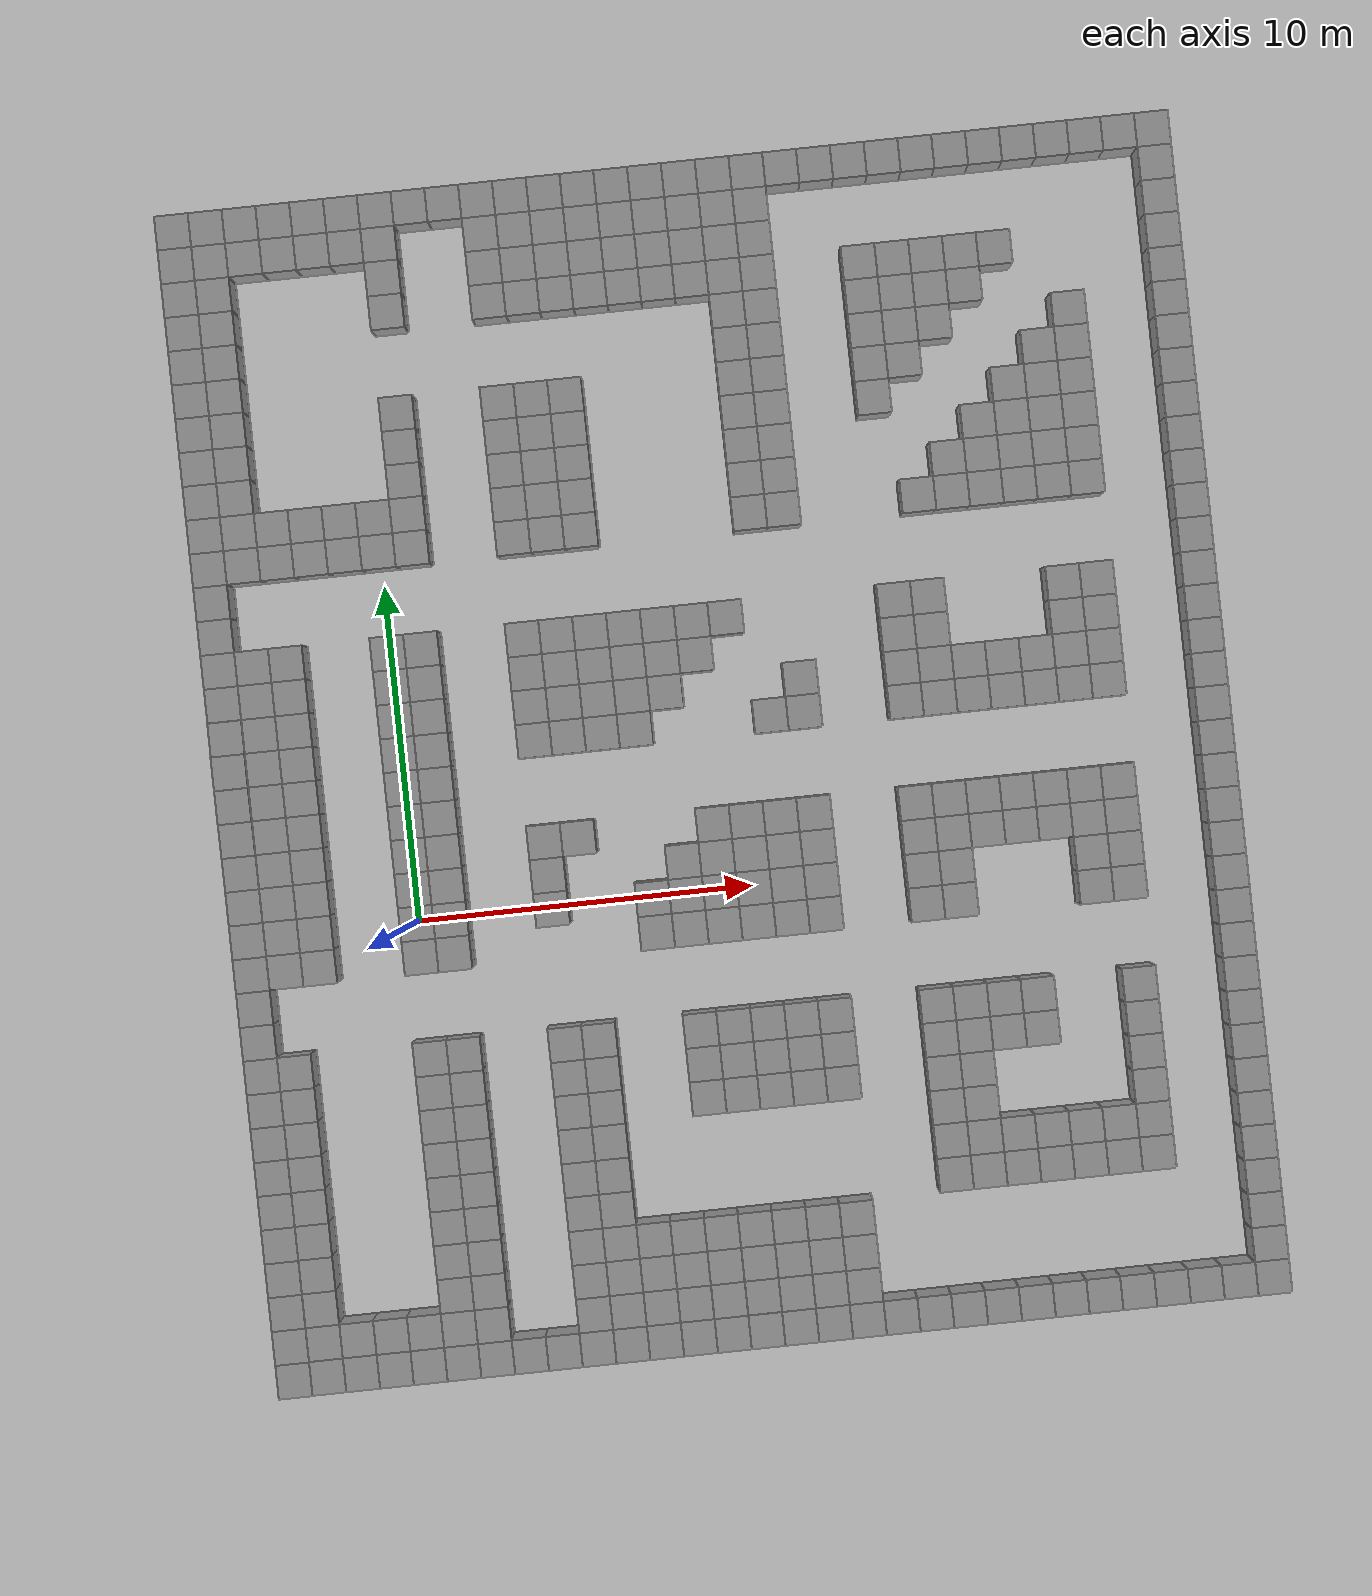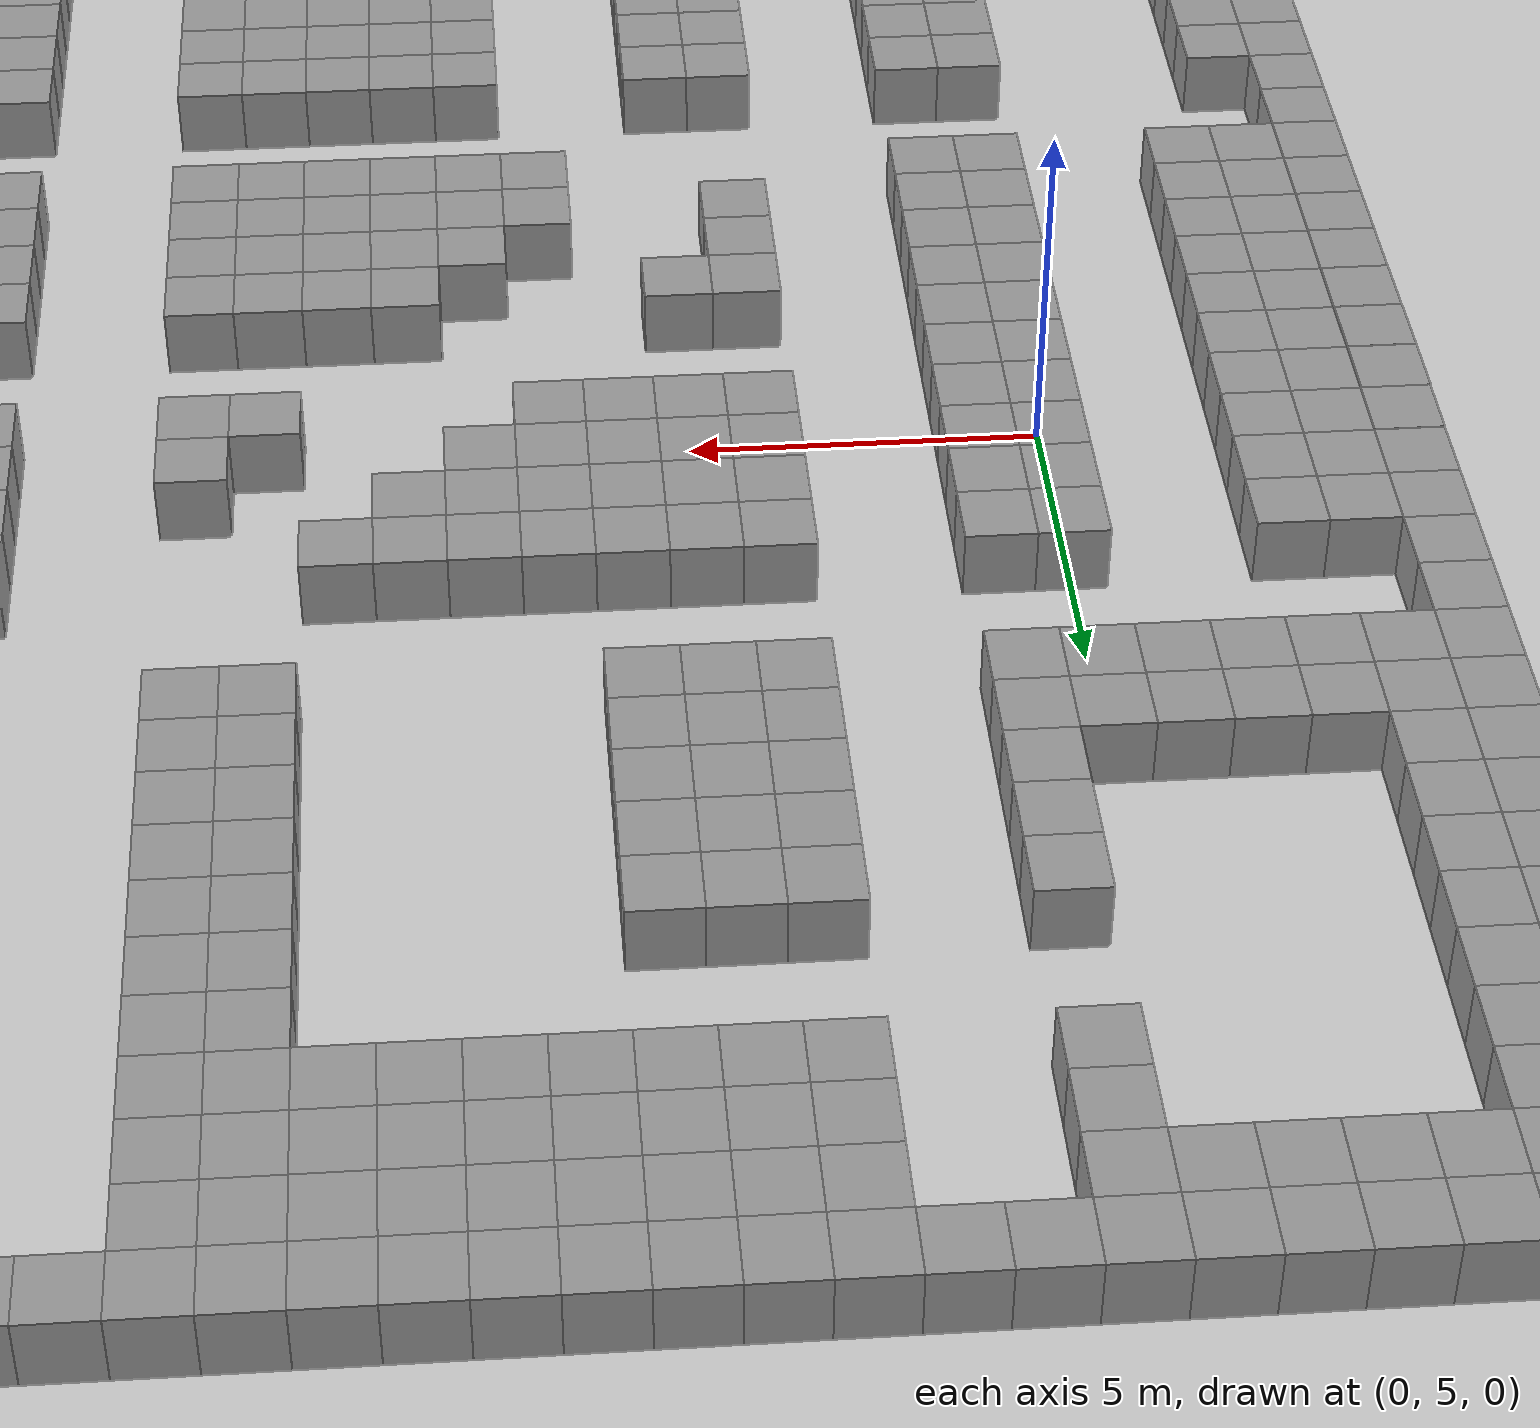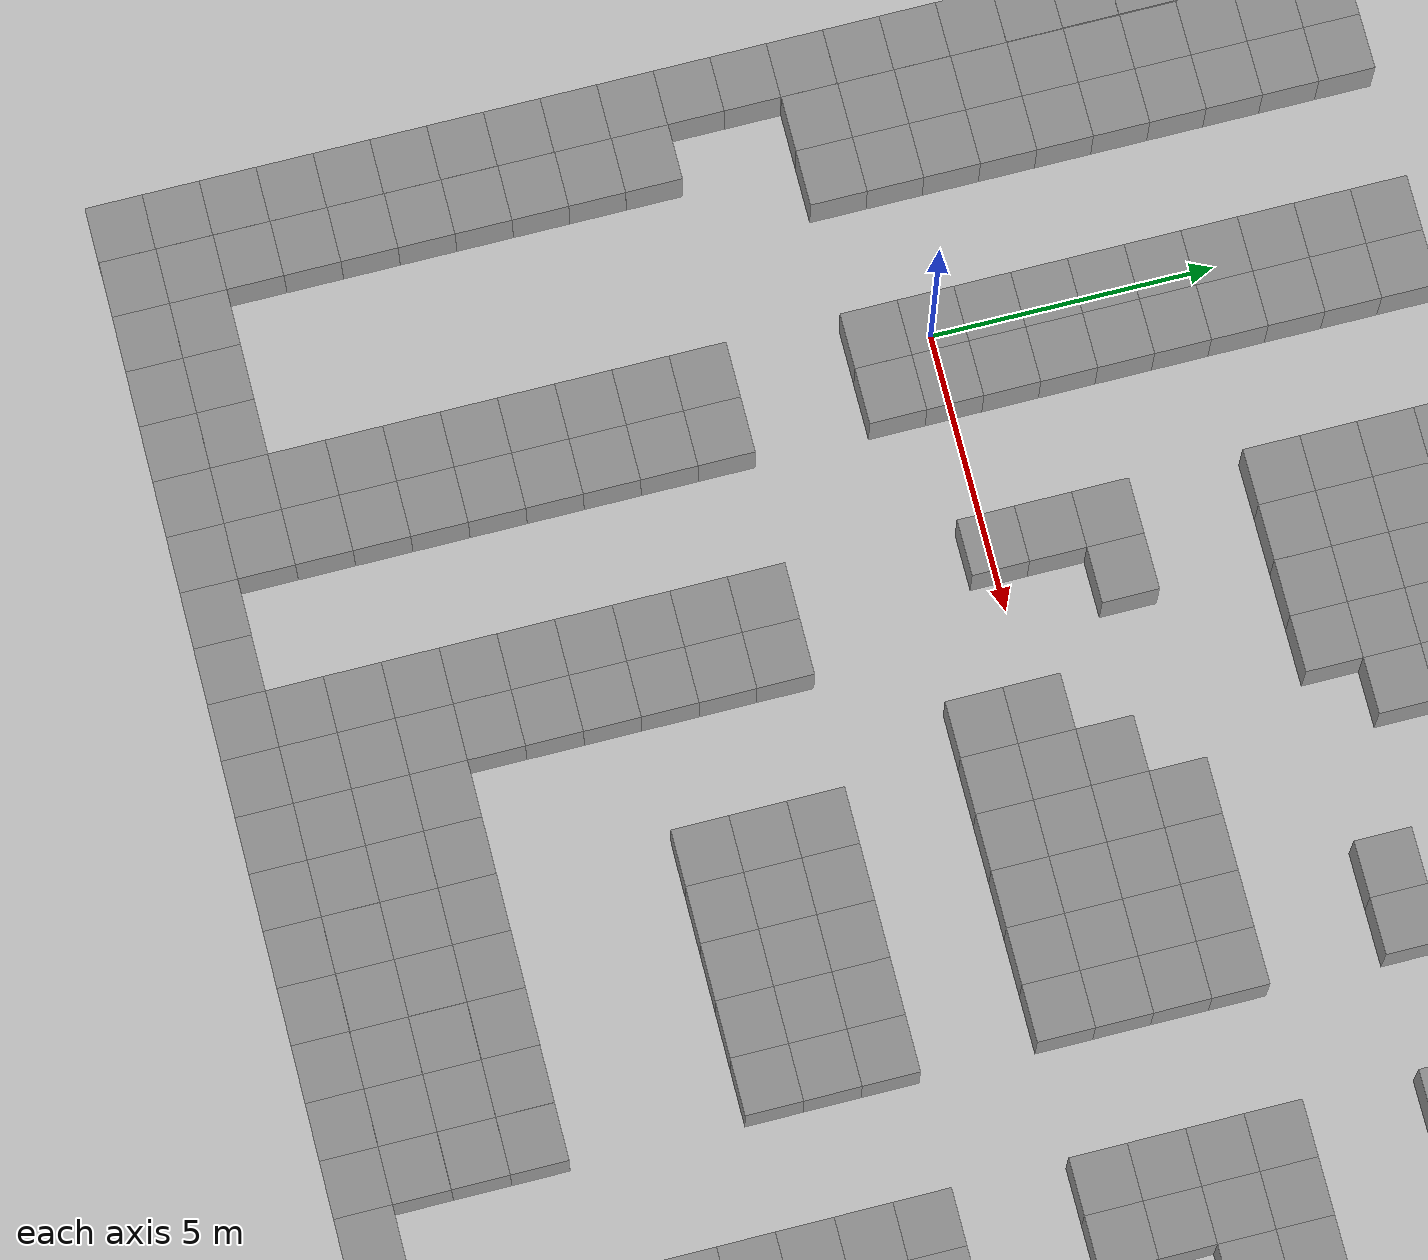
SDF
<sdf version="1.6">
 <world name="default">
  <plugin name="gazebo_occupancy_map" filename="libgazebo_2Dmap_plugin.so">
   <map_resolution>0.05</map_resolution>
   <map_z>0.7</map_z>
   <map_size_x>100</map_size_x>
   <map_size_y>100</map_size_y>
  </plugin>
  <light name="sun" type="directional">
   <pose>0 0 10 0 -0 0</pose>
   <diffuse>0.8 0.8 0.8 1</diffuse>
   <specular>0.2 0.2 0.2 1</specular>
   <attenuation>
    <range>1000</range>
    <constant>0.9</constant>
    <linear>0.01</linear>
    <quadratic>0.001</quadratic>
   </attenuation>
   <direction>-0.5 0.1 -0.9</direction>
  </light>
  <model name="ground_plane">
   <static>1</static>
   <link name="link">
    <collision name="collision">
     <geometry><plane><normal>0 0 1</normal><size>100 100</size></plane></geometry>
     <surface><friction><ode><mu>100</mu><mu2>50</mu2></ode></friction></surface>
    </collision>
    <visual name="visual">
     <cast_shadows>0</cast_shadows>
     <geometry><plane><normal>0 0 1</normal><size>100 100</size></plane></geometry>
     <material>
      <script><uri>file://media/materials/scripts/gazebo.material</uri><name>Gazebo/Grey</name></script>
     </material>
    </visual>
    <velocity_decay><linear>0</linear><angular>0</angular></velocity_decay>
   </link>
  </model>
  <physics name="default_physics" default="0" type="ode">
   <max_step_size>0.001</max_step_size>
   <real_time_factor>1</real_time_factor>
   <real_time_update_rate>1000</real_time_update_rate>
  </physics>
  <scene><ambient>0.4 0.4 0.4 1</ambient><background>0.7 0.7 0.7 1</background><shadows>1</shadows></scene>
  <spherical_coordinates>
   <surface_model>EARTH_WGS84</surface_model>
   <latitude_deg>0</latitude_deg>
   <longitude_deg>0</longitude_deg>
   <elevation>0</elevation>
   <heading_deg>0</heading_deg>
  </spherical_coordinates>
  <model name="unit_box_1">
   <pose>-5.01661 4.99523 0.5 0 -0 0.000223</pose>
   <static>1</static>
   <link name="link">
    <inertial>
     <mass>1</mass>
     <inertia><ixx>1</ixx><ixy>0</ixy><ixz>0</ixz><iyy>1</iyy><iyz>0</iyz><izz>1</izz></inertia>
    </inertial>
    <collision name="collision"><geometry><box><size>1 1 1</size></box></geometry></collision>
    <visual name="visual">
     <geometry><box><size>1 1 1</size></box></geometry>
     <material>
      <script><uri>file://media/materials/scripts/gazebo.material</uri><name>Gazebo/Grey</name></script>
     </material>
    </visual>
    <velocity_decay><linear>0</linear><angular>0</angular></velocity_decay>
   </link>
   <static>1</static>
  </model>
  <model name="unit_box_40">
   <pose>-5.01481 3.99235 0.5 0 -0 0.003225</pose>
   <static>1</static>
   <link name="link">
    <inertial>
     <mass>1</mass>
     <inertia><ixx>1</ixx><ixy>0</ixy><ixz>0</ixz><iyy>1</iyy><iyz>0</iyz><izz>1</izz></inertia>
    </inertial>
    <collision name="collision"><geometry><box><size>1 1 1</size></box></geometry></collision>
    <visual name="visual">
     <geometry><box><size>1 1 1</size></box></geometry>
     <material>
      <script><uri>file://media/materials/scripts/gazebo.material</uri><name>Gazebo/Grey</name></script>
     </material>
    </visual>
    <velocity_decay><linear>0</linear><angular>0</angular></velocity_decay>
   </link>
   <static>1</static>
  </model>
  <model name="unit_box_41">
   <pose>-5.00826 2.99203 0.5 0 -0 0.002598</pose>
   <static>1</static>
   <link name="link">
    <inertial>
     <mass>1</mass>
     <inertia><ixx>1</ixx><ixy>0</ixy><ixz>0</ixz><iyy>1</iyy><iyz>0</iyz><izz>1</izz></inertia>
    </inertial>
    <collision name="collision"><geometry><box><size>1 1 1</size></box></geometry></collision>
    <visual name="visual">
     <geometry><box><size>1 1 1</size></box></geometry>
     <material>
      <script><uri>file://media/materials/scripts/gazebo.material</uri><name>Gazebo/Grey</name></script>
     </material>
    </visual>
    <velocity_decay><linear>0</linear><angular>0</angular></velocity_decay>
   </link>
   <static>1</static>
  </model>
  <model name="unit_box_42">
   <pose>-5.0021 1.99164 0.5 0 -0 0.001796</pose>
   <static>1</static>
   <link name="link">
    <inertial>
     <mass>1</mass>
     <inertia><ixx>1</ixx><ixy>0</ixy><ixz>0</ixz><iyy>1</iyy><iyz>0</iyz><izz>1</izz></inertia>
    </inertial>
    <collision name="collision"><geometry><box><size>1 1 1</size></box></geometry></collision>
    <visual name="visual">
     <geometry><box><size>1 1 1</size></box></geometry>
     <material>
      <script><uri>file://media/materials/scripts/gazebo.material</uri><name>Gazebo/Grey</name></script>
     </material>
    </visual>
    <velocity_decay><linear>0</linear><angular>0</angular></velocity_decay>
   </link>
   <static>1</static>
  </model>
  <model name="unit_box_43">
   <pose>-5.00197 0.99143 0.5 0 -0 0.001375</pose>
   <static>1</static>
   <link name="link">
    <inertial>
     <mass>1</mass>
     <inertia><ixx>1</ixx><ixy>0</ixy><ixz>0</ixz><iyy>1</iyy><iyz>0</iyz><izz>1</izz></inertia>
    </inertial>
    <collision name="collision"><geometry><box><size>1 1 1</size></box></geometry></collision>
    <visual name="visual">
     <geometry><box><size>1 1 1</size></box></geometry>
     <material>
      <script><uri>file://media/materials/scripts/gazebo.material</uri><name>Gazebo/Grey</name></script>
     </material>
    </visual>
    <velocity_decay><linear>0</linear><angular>0</angular></velocity_decay>
   </link>
   <static>1</static>
  </model>
  <model name="unit_box_44">
   <pose>-5.00065 -0.008792 0.5 0 -0 0.000932</pose>
   <static>1</static>
   <link name="link">
    <inertial>
     <mass>1</mass>
     <inertia><ixx>1</ixx><ixy>0</ixy><ixz>0</ixz><iyy>1</iyy><iyz>0</iyz><izz>1</izz></inertia>
    </inertial>
    <collision name="collision"><geometry><box><size>1 1 1</size></box></geometry></collision>
    <visual name="visual">
     <geometry><box><size>1 1 1</size></box></geometry>
     <material>
      <script><uri>file://media/materials/scripts/gazebo.material</uri><name>Gazebo/Grey</name></script>
     </material>
    </visual>
    <velocity_decay><linear>0</linear><angular>0</angular></velocity_decay>
   </link>
   <static>1</static>
  </model>
  <model name="unit_box_45">
   <pose>-5.00074 -1.00881 0.5 0 -0 0.000893</pose>
   <static>1</static>
   <link name="link">
    <inertial>
     <mass>1</mass>
     <inertia><ixx>1</ixx><ixy>0</ixy><ixz>0</ixz><iyy>1</iyy><iyz>0</iyz><izz>1</izz></inertia>
    </inertial>
    <collision name="collision"><geometry><box><size>1 1 1</size></box></geometry></collision>
    <visual name="visual">
     <geometry><box><size>1 1 1</size></box></geometry>
     <material>
      <script><uri>file://media/materials/scripts/gazebo.material</uri><name>Gazebo/Grey</name></script>
     </material>
    </visual>
    <velocity_decay><linear>0</linear><angular>0</angular></velocity_decay>
   </link>
   <static>1</static>
  </model>
  <model name="unit_box_46">
   <pose>-5.00037 -2.00886 0.5 0 -0 0.000802</pose>
   <static>1</static>
   <link name="link">
    <inertial>
     <mass>1</mass>
     <inertia><ixx>1</ixx><ixy>0</ixy><ixz>0</ixz><iyy>1</iyy><iyz>0</iyz><izz>1</izz></inertia>
    </inertial>
    <collision name="collision"><geometry><box><size>1 1 1</size></box></geometry></collision>
    <visual name="visual">
     <geometry><box><size>1 1 1</size></box></geometry>
     <material>
      <script><uri>file://media/materials/scripts/gazebo.material</uri><name>Gazebo/Grey</name></script>
     </material>
    </visual>
    <velocity_decay><linear>0</linear><angular>0</angular></velocity_decay>
   </link>
   <static>1</static>
  </model>
  <model name="unit_box_47">
   <pose>-5.00047 -3.0089 0.5 0 -0 0.000729</pose>
   <static>1</static>
   <link name="link">
    <inertial>
     <mass>1</mass>
     <inertia><ixx>1</ixx><ixy>0</ixy><ixz>0</ixz><iyy>1</iyy><iyz>0</iyz><izz>1</izz></inertia>
    </inertial>
    <collision name="collision"><geometry><box><size>1 1 1</size></box></geometry></collision>
    <visual name="visual">
     <geometry><box><size>1 1 1</size></box></geometry>
     <material>
      <script><uri>file://media/materials/scripts/gazebo.material</uri><name>Gazebo/Grey</name></script>
     </material>
    </visual>
    <velocity_decay><linear>0</linear><angular>0</angular></velocity_decay>
   </link>
   <static>1</static>
  </model>
  <model name="unit_box_61">
   <pose>-5.0071 5.99581 0.5 0 0 -0.000452</pose>
   <static>1</static>
   <link name="link">
    <inertial>
     <mass>1</mass>
     <inertia><ixx>1</ixx><ixy>0</ixy><ixz>0</ixz><iyy>1</iyy><iyz>0</iyz><izz>1</izz></inertia>
    </inertial>
    <collision name="collision"><geometry><box><size>1 1 1</size></box></geometry></collision>
    <visual name="visual">
     <geometry><box><size>1 1 1</size></box></geometry>
     <material>
      <script><uri>file://media/materials/scripts/gazebo.material</uri><name>Gazebo/Grey</name></script>
     </material>
    </visual>
    <velocity_decay><linear>0</linear><angular>0</angular></velocity_decay>
   </link>
   <static>1</static>
  </model>
  <model name="unit_box_67">
   <pose>-5.00001 6.99999 0.5 0 -0 9e-06</pose>
   <static>1</static>
   <link name="link">
    <inertial>
     <mass>1</mass>
     <inertia><ixx>1</ixx><ixy>0</ixy><ixz>0</ixz><iyy>1</iyy><iyz>0</iyz><izz>1</izz></inertia>
    </inertial>
    <collision name="collision"><geometry><box><size>1 1 1</size></box></geometry></collision>
    <visual name="visual">
     <geometry><box><size>1 1 1</size></box></geometry>
     <material>
      <script><uri>file://media/materials/scripts/gazebo.material</uri><name>Gazebo/Grey</name></script>
     </material>
    </visual>
    <velocity_decay><linear>0</linear><angular>0</angular></velocity_decay>
   </link>
   <static>1</static>
  </model>
  <model name="unit_box_68">
   <pose>-5.00001 7.99999 0.5 0 -0 8e-06</pose>
   <static>1</static>
   <link name="link">
    <inertial>
     <mass>1</mass>
     <inertia><ixx>1</ixx><ixy>0</ixy><ixz>0</ixz><iyy>1</iyy><iyz>0</iyz><izz>1</izz></inertia>
    </inertial>
    <collision name="collision"><geometry><box><size>1 1 1</size></box></geometry></collision>
    <visual name="visual">
     <geometry><box><size>1 1 1</size></box></geometry>
     <material>
      <script><uri>file://media/materials/scripts/gazebo.material</uri><name>Gazebo/Grey</name></script>
     </material>
    </visual>
    <velocity_decay><linear>0</linear><angular>0</angular></velocity_decay>
   </link>
   <static>1</static>
  </model>
  <model name="unit_box_69">
   <pose>-5 8.99999 0.5 0 -0 7e-06</pose>
   <static>1</static>
   <link name="link">
    <inertial>
     <mass>1</mass>
     <inertia><ixx>1</ixx><ixy>0</ixy><ixz>0</ixz><iyy>1</iyy><iyz>0</iyz><izz>1</izz></inertia>
    </inertial>
    <collision name="collision"><geometry><box><size>1 1 1</size></box></geometry></collision>
    <visual name="visual">
     <geometry><box><size>1 1 1</size></box></geometry>
     <material>
      <script><uri>file://media/materials/scripts/gazebo.material</uri><name>Gazebo/Grey</name></script>
     </material>
    </visual>
    <velocity_decay><linear>0</linear><angular>0</angular></velocity_decay>
   </link>
   <static>1</static>
  </model>
  <model name="unit_box_72">
   <pose>-4.99999 9.99999 0.5 0 -0 7e-06</pose>
   <static>1</static>
   <link name="link">
    <inertial>
     <mass>1</mass>
     <inertia><ixx>1</ixx><ixy>0</ixy><ixz>0</ixz><iyy>1</iyy><iyz>0</iyz><izz>1</izz></inertia>
    </inertial>
    <collision name="collision"><geometry><box><size>1 1 1</size></box></geometry></collision>
    <visual name="visual">
     <geometry><box><size>1 1 1</size></box></geometry>
     <material>
      <script><uri>file://media/materials/scripts/gazebo.material</uri><name>Gazebo/Grey</name></script>
     </material>
    </visual>
    <velocity_decay><linear>0</linear><angular>0</angular></velocity_decay>
   </link>
   <static>1</static>
  </model>
  <model name="unit_box_73">
   <pose>-5.00001 11 0.5 0 -0 8e-06</pose>
   <static>1</static>
   <link name="link">
    <inertial>
     <mass>1</mass>
     <inertia><ixx>1</ixx><ixy>0</ixy><ixz>0</ixz><iyy>1</iyy><iyz>0</iyz><izz>1</izz></inertia>
    </inertial>
    <collision name="collision"><geometry><box><size>1 1 1</size></box></geometry></collision>
    <visual name="visual">
     <geometry><box><size>1 1 1</size></box></geometry>
     <material>
      <script><uri>file://media/materials/scripts/gazebo.material</uri><name>Gazebo/Grey</name></script>
     </material>
    </visual>
    <velocity_decay><linear>0</linear><angular>0</angular></velocity_decay>
   </link>
   <static>1</static>
  </model>
  <model name="unit_box_74">
   <pose>-5.00001 12 0.5 0 -0 8e-06</pose>
   <static>1</static>
   <link name="link">
    <inertial>
     <mass>1</mass>
     <inertia><ixx>1</ixx><ixy>0</ixy><ixz>0</ixz><iyy>1</iyy><iyz>0</iyz><izz>1</izz></inertia>
    </inertial>
    <collision name="collision"><geometry><box><size>1 1 1</size></box></geometry></collision>
    <visual name="visual">
     <geometry><box><size>1 1 1</size></box></geometry>
     <material>
      <script><uri>file://media/materials/scripts/gazebo.material</uri><name>Gazebo/Grey</name></script>
     </material>
    </visual>
    <velocity_decay><linear>0</linear><angular>0</angular></velocity_decay>
   </link>
   <static>1</static>
  </model>
  <model name="unit_box_75">
   <pose>-5 13 0.5 0 -0 5e-06</pose>
   <static>1</static>
   <link name="link">
    <inertial>
     <mass>1</mass>
     <inertia><ixx>1</ixx><ixy>0</ixy><ixz>0</ixz><iyy>1</iyy><iyz>0</iyz><izz>1</izz></inertia>
    </inertial>
    <collision name="collision"><geometry><box><size>1 1 1</size></box></geometry></collision>
    <visual name="visual">
     <geometry><box><size>1 1 1</size></box></geometry>
     <material>
      <script><uri>file://media/materials/scripts/gazebo.material</uri><name>Gazebo/Grey</name></script>
     </material>
    </visual>
    <velocity_decay><linear>0</linear><angular>0</angular></velocity_decay>
   </link>
   <static>1</static>
  </model>
  <model name="unit_box_76">
   <pose>-5 14 0.5 0 -0 6e-06</pose>
   <static>1</static>
   <link name="link">
    <inertial>
     <mass>1</mass>
     <inertia><ixx>1</ixx><ixy>0</ixy><ixz>0</ixz><iyy>1</iyy><iyz>0</iyz><izz>1</izz></inertia>
    </inertial>
    <collision name="collision"><geometry><box><size>1 1 1</size></box></geometry></collision>
    <visual name="visual">
     <geometry><box><size>1 1 1</size></box></geometry>
     <material>
      <script><uri>file://media/materials/scripts/gazebo.material</uri><name>Gazebo/Grey</name></script>
     </material>
    </visual>
    <velocity_decay><linear>0</linear><angular>0</angular></velocity_decay>
   </link>
   <static>1</static>
  </model>
  <model name="unit_box_77">
   <pose>-4.99999 15 0.5 0 -0 7e-06</pose>
   <static>1</static>
   <link name="link">
    <inertial>
     <mass>1</mass>
     <inertia><ixx>1</ixx><ixy>0</ixy><ixz>0</ixz><iyy>1</iyy><iyz>0</iyz><izz>1</izz></inertia>
    </inertial>
    <collision name="collision"><geometry><box><size>1 1 1</size></box></geometry></collision>
    <visual name="visual">
     <geometry><box><size>1 1 1</size></box></geometry>
     <material>
      <script><uri>file://media/materials/scripts/gazebo.material</uri><name>Gazebo/Grey</name></script>
     </material>
    </visual>
    <velocity_decay><linear>0</linear><angular>0</angular></velocity_decay>
   </link>
   <static>1</static>
  </model>
  <model name="unit_box_78">
   <pose>-5 16 0.5 0 -0 7e-06</pose>
   <static>1</static>
   <link name="link">
    <inertial>
     <mass>1</mass>
     <inertia><ixx>1</ixx><ixy>0</ixy><ixz>0</ixz><iyy>1</iyy><iyz>0</iyz><izz>1</izz></inertia>
    </inertial>
    <collision name="collision"><geometry><box><size>1 1 1</size></box></geometry></collision>
    <visual name="visual">
     <geometry><box><size>1 1 1</size></box></geometry>
     <material>
      <script><uri>file://media/materials/scripts/gazebo.material</uri><name>Gazebo/Grey</name></script>
     </material>
    </visual>
    <velocity_decay><linear>0</linear><angular>0</angular></velocity_decay>
   </link>
   <static>1</static>
  </model>
  <model name="unit_box_79">
   <pose>-4.99997 17 0.5 0 -0 6e-06</pose>
   <static>1</static>
   <link name="link">
    <inertial>
     <mass>1</mass>
     <inertia><ixx>1</ixx><ixy>0</ixy><ixz>0</ixz><iyy>1</iyy><iyz>0</iyz><izz>1</izz></inertia>
    </inertial>
    <collision name="collision"><geometry><box><size>1 1 1</size></box></geometry></collision>
    <visual name="visual">
     <geometry><box><size>1 1 1</size></box></geometry>
     <material>
      <script><uri>file://media/materials/scripts/gazebo.material</uri><name>Gazebo/Grey</name></script>
     </material>
    </visual>
    <velocity_decay><linear>0</linear><angular>0</angular></velocity_decay>
   </link>
   <static>1</static>
  </model>
  <model name="unit_box_80">
   <pose>-4.99997 18 0.5 0 -0 3e-06</pose>
   <static>1</static>
   <link name="link">
    <inertial>
     <mass>1</mass>
     <inertia><ixx>1</ixx><ixy>0</ixy><ixz>0</ixz><iyy>1</iyy><iyz>0</iyz><izz>1</izz></inertia>
    </inertial>
    <collision name="collision"><geometry><box><size>1 1 1</size></box></geometry></collision>
    <visual name="visual">
     <geometry><box><size>1 1 1</size></box></geometry>
     <material>
      <script><uri>file://media/materials/scripts/gazebo.material</uri><name>Gazebo/Grey</name></script>
     </material>
    </visual>
    <velocity_decay><linear>0</linear><angular>0</angular></velocity_decay>
   </link>
   <static>1</static>
  </model>
  <model name="unit_box_96">
   <pose>-4.99997 19 0.5 0 -0 1e-06</pose>
   <static>1</static>
   <link name="link">
    <inertial>
     <mass>1</mass>
     <inertia><ixx>1</ixx><ixy>0</ixy><ixz>0</ixz><iyy>1</iyy><iyz>0</iyz><izz>1</izz></inertia>
    </inertial>
    <collision name="collision"><geometry><box><size>1 1 1</size></box></geometry></collision>
    <visual name="visual">
     <geometry><box><size>1 1 1</size></box></geometry>
     <material>
      <script><uri>file://media/materials/scripts/gazebo.material</uri><name>Gazebo/Grey</name></script>
     </material>
    </visual>
    <velocity_decay><linear>0</linear><angular>0</angular></velocity_decay>
   </link>
   <static>1</static>
  </model>
  <model name="unit_box_97">
   <pose>-4.99997 20 0.5 0 -0 1e-06</pose>
   <static>1</static>
   <link name="link">
    <inertial>
     <mass>1</mass>
     <inertia><ixx>1</ixx><ixy>0</ixy><ixz>0</ixz><iyy>1</iyy><iyz>0</iyz><izz>1</izz></inertia>
    </inertial>
    <collision name="collision"><geometry><box><size>1 1 1</size></box></geometry></collision>
    <visual name="visual">
     <geometry><box><size>1 1 1</size></box></geometry>
     <material>
      <script><uri>file://media/materials/scripts/gazebo.material</uri><name>Gazebo/Grey</name></script>
     </material>
    </visual>
    <velocity_decay><linear>0</linear><angular>0</angular></velocity_decay>
   </link>
   <static>1</static>
  </model>
  <model name="unit_box_98">
   <pose>-5.00001 21 0.5 0 -0 0</pose>
   <static>1</static>
   <link name="link">
    <inertial>
     <mass>1</mass>
     <inertia><ixx>1</ixx><ixy>0</ixy><ixz>0</ixz><iyy>1</iyy><iyz>0</iyz><izz>1</izz></inertia>
    </inertial>
    <collision name="collision"><geometry><box><size>1 1 1</size></box></geometry></collision>
    <visual name="visual">
     <geometry><box><size>1 1 1</size></box></geometry>
     <material>
      <script><uri>file://media/materials/scripts/gazebo.material</uri><name>Gazebo/Grey</name></script>
     </material>
    </visual>
    <velocity_decay><linear>0</linear><angular>0</angular></velocity_decay>
   </link>
   <static>1</static>
  </model>
  <model name="unit_box_99">
   <pose>-4.00001 21 0.5 0 0 -1e-06</pose>
   <static>1</static>
   <link name="link">
    <inertial>
     <mass>1</mass>
     <inertia><ixx>1</ixx><ixy>0</ixy><ixz>0</ixz><iyy>1</iyy><iyz>0</iyz><izz>1</izz></inertia>
    </inertial>
    <collision name="collision"><geometry><box><size>1 1 1</size></box></geometry></collision>
    <visual name="visual">
     <geometry><box><size>1 1 1</size></box></geometry>
     <material>
      <script><uri>file://media/materials/scripts/gazebo.material</uri><name>Gazebo/Grey</name></script>
     </material>
    </visual>
    <velocity_decay><linear>0</linear><angular>0</angular></velocity_decay>
   </link>
   <static>1</static>
  </model>
  <model name="unit_box_100">
   <pose>-3.00001 21 0.5 0 0 -1e-06</pose>
   <static>1</static>
   <link name="link">
    <inertial>
     <mass>1</mass>
     <inertia><ixx>1</ixx><ixy>0</ixy><ixz>0</ixz><iyy>1</iyy><iyz>0</iyz><izz>1</izz></inertia>
    </inertial>
    <collision name="collision"><geometry><box><size>1 1 1</size></box></geometry></collision>
    <visual name="visual">
     <geometry><box><size>1 1 1</size></box></geometry>
     <material>
      <script><uri>file://media/materials/scripts/gazebo.material</uri><name>Gazebo/Grey</name></script>
     </material>
    </visual>
    <velocity_decay><linear>0</linear><angular>0</angular></velocity_decay>
   </link>
   <static>1</static>
  </model>
  <model name="unit_box_101">
   <pose>-2.00001 21 0.5 0 0 -1e-06</pose>
   <static>1</static>
   <link name="link">
    <inertial>
     <mass>1</mass>
     <inertia><ixx>1</ixx><ixy>0</ixy><ixz>0</ixz><iyy>1</iyy><iyz>0</iyz><izz>1</izz></inertia>
    </inertial>
    <collision name="collision"><geometry><box><size>1 1 1</size></box></geometry></collision>
    <visual name="visual">
     <geometry><box><size>1 1 1</size></box></geometry>
     <material>
      <script><uri>file://media/materials/scripts/gazebo.material</uri><name>Gazebo/Grey</name></script>
     </material>
    </visual>
    <velocity_decay><linear>0</linear><angular>0</angular></velocity_decay>
   </link>
   <static>1</static>
  </model>
  <model name="unit_box_102">
   <pose>-1.00001 21 0.5 0 -0 0</pose>
   <static>1</static>
   <link name="link">
    <inertial>
     <mass>1</mass>
     <inertia><ixx>1</ixx><ixy>0</ixy><ixz>0</ixz><iyy>1</iyy><iyz>0</iyz><izz>1</izz></inertia>
    </inertial>
    <collision name="collision"><geometry><box><size>1 1 1</size></box></geometry></collision>
    <visual name="visual">
     <geometry><box><size>1 1 1</size></box></geometry>
     <material>
      <script><uri>file://media/materials/scripts/gazebo.material</uri><name>Gazebo/Grey</name></script>
     </material>
    </visual>
    <velocity_decay><linear>0</linear><angular>0</angular></velocity_decay>
   </link>
   <static>1</static>
  </model>
  <model name="unit_box_103">
   <pose>-1e-05 21 0.5 0 -0 0</pose>
   <static>1</static>
   <link name="link">
    <inertial>
     <mass>1</mass>
     <inertia><ixx>1</ixx><ixy>0</ixy><ixz>0</ixz><iyy>1</iyy><iyz>0</iyz><izz>1</izz></inertia>
    </inertial>
    <collision name="collision"><geometry><box><size>1 1 1</size></box></geometry></collision>
    <visual name="visual">
     <geometry><box><size>1 1 1</size></box></geometry>
     <material>
      <script><uri>file://media/materials/scripts/gazebo.material</uri><name>Gazebo/Grey</name></script>
     </material>
    </visual>
    <velocity_decay><linear>0</linear><angular>0</angular></velocity_decay>
   </link>
   <static>1</static>
  </model>
  <model name="unit_box_104">
   <pose>0.999991 21 0.5 0 -0 0</pose>
   <static>1</static>
   <link name="link">
    <inertial>
     <mass>1</mass>
     <inertia><ixx>1</ixx><ixy>0</ixy><ixz>0</ixz><iyy>1</iyy><iyz>0</iyz><izz>1</izz></inertia>
    </inertial>
    <collision name="collision"><geometry><box><size>1 1 1</size></box></geometry></collision>
    <visual name="visual">
     <geometry><box><size>1 1 1</size></box></geometry>
     <material>
      <script><uri>file://media/materials/scripts/gazebo.material</uri><name>Gazebo/Grey</name></script>
     </material>
    </visual>
    <velocity_decay><linear>0</linear><angular>0</angular></velocity_decay>
   </link>
   <static>1</static>
  </model>
  <model name="unit_box_105">
   <pose>1.99999 21 0.5 0 -0 0</pose>
   <static>1</static>
   <link name="link">
    <inertial>
     <mass>1</mass>
     <inertia><ixx>1</ixx><ixy>0</ixy><ixz>0</ixz><iyy>1</iyy><iyz>0</iyz><izz>1</izz></inertia>
    </inertial>
    <collision name="collision"><geometry><box><size>1 1 1</size></box></geometry></collision>
    <visual name="visual">
     <geometry><box><size>1 1 1</size></box></geometry>
     <material>
      <script><uri>file://media/materials/scripts/gazebo.material</uri><name>Gazebo/Grey</name></script>
     </material>
    </visual>
    <velocity_decay><linear>0</linear><angular>0</angular></velocity_decay>
   </link>
   <static>1</static>
  </model>
  <model name="unit_box_106">
   <pose>2.99999 21 0.5 0 -0 1e-06</pose>
   <static>1</static>
   <link name="link">
    <inertial>
     <mass>1</mass>
     <inertia><ixx>1</ixx><ixy>0</ixy><ixz>0</ixz><iyy>1</iyy><iyz>0</iyz><izz>1</izz></inertia>
    </inertial>
    <collision name="collision"><geometry><box><size>1 1 1</size></box></geometry></collision>
    <visual name="visual">
     <geometry><box><size>1 1 1</size></box></geometry>
     <material>
      <script><uri>file://media/materials/scripts/gazebo.material</uri><name>Gazebo/Grey</name></script>
     </material>
    </visual>
    <velocity_decay><linear>0</linear><angular>0</angular></velocity_decay>
   </link>
   <static>1</static>
  </model>
  <model name="unit_box_107">
   <pose>3.99999 21 0.5 0 -0 2e-06</pose>
   <static>1</static>
   <link name="link">
    <inertial>
     <mass>1</mass>
     <inertia><ixx>1</ixx><ixy>0</ixy><ixz>0</ixz><iyy>1</iyy><iyz>0</iyz><izz>1</izz></inertia>
    </inertial>
    <collision name="collision"><geometry><box><size>1 1 1</size></box></geometry></collision>
    <visual name="visual">
     <geometry><box><size>1 1 1</size></box></geometry>
     <material>
      <script><uri>file://media/materials/scripts/gazebo.material</uri><name>Gazebo/Grey</name></script>
     </material>
    </visual>
    <velocity_decay><linear>0</linear><angular>0</angular></velocity_decay>
   </link>
   <static>1</static>
  </model>
  <model name="unit_box_108">
   <pose>5 21 0.5 0 -0 3e-06</pose>
   <static>1</static>
   <link name="link">
    <inertial>
     <mass>1</mass>
     <inertia><ixx>1</ixx><ixy>0</ixy><ixz>0</ixz><iyy>1</iyy><iyz>0</iyz><izz>1</izz></inertia>
    </inertial>
    <collision name="collision"><geometry><box><size>1 1 1</size></box></geometry></collision>
    <visual name="visual">
     <geometry><box><size>1 1 1</size></box></geometry>
     <material>
      <script><uri>file://media/materials/scripts/gazebo.material</uri><name>Gazebo/Grey</name></script>
     </material>
    </visual>
    <velocity_decay><linear>0</linear><angular>0</angular></velocity_decay>
   </link>
   <static>1</static>
  </model>
  <model name="unit_box_109">
   <pose>6 20.9999 0.5 0 -0 3e-06</pose>
   <static>1</static>
   <link name="link">
    <inertial>
     <mass>1</mass>
     <inertia><ixx>1</ixx><ixy>0</ixy><ixz>0</ixz><iyy>1</iyy><iyz>0</iyz><izz>1</izz></inertia>
    </inertial>
    <collision name="collision"><geometry><box><size>1 1 1</size></box></geometry></collision>
    <visual name="visual">
     <geometry><box><size>1 1 1</size></box></geometry>
     <material>
      <script><uri>file://media/materials/scripts/gazebo.material</uri><name>Gazebo/Grey</name></script>
     </material>
    </visual>
    <velocity_decay><linear>0</linear><angular>0</angular></velocity_decay>
   </link>
   <static>1</static>
  </model>
  <model name="unit_box_110">
   <pose>7 21 0.5 0 -0 4e-06</pose>
   <static>1</static>
   <link name="link">
    <inertial>
     <mass>1</mass>
     <inertia><ixx>1</ixx><ixy>0</ixy><ixz>0</ixz><iyy>1</iyy><iyz>0</iyz><izz>1</izz></inertia>
    </inertial>
    <collision name="collision"><geometry><box><size>1 1 1</size></box></geometry></collision>
    <visual name="visual">
     <geometry><box><size>1 1 1</size></box></geometry>
     <material>
      <script><uri>file://media/materials/scripts/gazebo.material</uri><name>Gazebo/Grey</name></script>
     </material>
    </visual>
    <velocity_decay><linear>0</linear><angular>0</angular></velocity_decay>
   </link>
   <static>1</static>
  </model>
  <model name="unit_box_111">
   <pose>8 21 0.5 0 -0 3e-06</pose>
   <static>1</static>
   <link name="link">
    <inertial>
     <mass>1</mass>
     <inertia><ixx>1</ixx><ixy>0</ixy><ixz>0</ixz><iyy>1</iyy><iyz>0</iyz><izz>1</izz></inertia>
    </inertial>
    <collision name="collision"><geometry><box><size>1 1 1</size></box></geometry></collision>
    <visual name="visual">
     <geometry><box><size>1 1 1</size></box></geometry>
     <material>
      <script><uri>file://media/materials/scripts/gazebo.material</uri><name>Gazebo/Grey</name></script>
     </material>
    </visual>
    <velocity_decay><linear>0</linear><angular>0</angular></velocity_decay>
   </link>
   <static>1</static>
  </model>
  <model name="unit_box_112">
   <pose>9 21 0.5 0 -0 3e-06</pose>
   <static>1</static>
   <link name="link">
    <inertial>
     <mass>1</mass>
     <inertia><ixx>1</ixx><ixy>0</ixy><ixz>0</ixz><iyy>1</iyy><iyz>0</iyz><izz>1</izz></inertia>
    </inertial>
    <collision name="collision"><geometry><box><size>1 1 1</size></box></geometry></collision>
    <visual name="visual">
     <geometry><box><size>1 1 1</size></box></geometry>
     <material>
      <script><uri>file://media/materials/scripts/gazebo.material</uri><name>Gazebo/Grey</name></script>
     </material>
    </visual>
    <velocity_decay><linear>0</linear><angular>0</angular></velocity_decay>
   </link>
   <static>1</static>
  </model>
  <model name="unit_box_113">
   <pose>10 21 0.5 0 -0 1e-06</pose>
   <static>1</static>
   <link name="link">
    <inertial>
     <mass>1</mass>
     <inertia><ixx>1</ixx><ixy>0</ixy><ixz>0</ixz><iyy>1</iyy><iyz>0</iyz><izz>1</izz></inertia>
    </inertial>
    <collision name="collision"><geometry><box><size>1 1 1</size></box></geometry></collision>
    <visual name="visual">
     <geometry><box><size>1 1 1</size></box></geometry>
     <material>
      <script><uri>file://media/materials/scripts/gazebo.material</uri><name>Gazebo/Grey</name></script>
     </material>
    </visual>
    <velocity_decay><linear>0</linear><angular>0</angular></velocity_decay>
   </link>
   <static>1</static>
  </model>
  <model name="unit_box_114">
   <pose>11 21 0.5 0 -0 1e-06</pose>
   <static>1</static>
   <link name="link">
    <inertial>
     <mass>1</mass>
     <inertia><ixx>1</ixx><ixy>0</ixy><ixz>0</ixz><iyy>1</iyy><iyz>0</iyz><izz>1</izz></inertia>
    </inertial>
    <collision name="collision"><geometry><box><size>1 1 1</size></box></geometry></collision>
    <visual name="visual">
     <geometry><box><size>1 1 1</size></box></geometry>
     <material>
      <script><uri>file://media/materials/scripts/gazebo.material</uri><name>Gazebo/Grey</name></script>
     </material>
    </visual>
    <velocity_decay><linear>0</linear><angular>0</angular></velocity_decay>
   </link>
   <static>1</static>
  </model>
  <model name="unit_box_115">
   <pose>12 21 0.5 0 0 -2e-06</pose>
   <static>1</static>
   <link name="link">
    <inertial>
     <mass>1</mass>
     <inertia><ixx>1</ixx><ixy>0</ixy><ixz>0</ixz><iyy>1</iyy><iyz>0</iyz><izz>1</izz></inertia>
    </inertial>
    <collision name="collision"><geometry><box><size>1 1 1</size></box></geometry></collision>
    <visual name="visual">
     <geometry><box><size>1 1 1</size></box></geometry>
     <material>
      <script><uri>file://media/materials/scripts/gazebo.material</uri><name>Gazebo/Grey</name></script>
     </material>
    </visual>
    <velocity_decay><linear>0</linear><angular>0</angular></velocity_decay>
   </link>
   <static>1</static>
  </model>
  <model name="unit_box_116">
   <pose>13 21 0.5 0 0 -2e-06</pose>
   <static>1</static>
   <link name="link">
    <inertial>
     <mass>1</mass>
     <inertia><ixx>1</ixx><ixy>0</ixy><ixz>0</ixz><iyy>1</iyy><iyz>0</iyz><izz>1</izz></inertia>
    </inertial>
    <collision name="collision"><geometry><box><size>1 1 1</size></box></geometry></collision>
    <visual name="visual">
     <geometry><box><size>1 1 1</size></box></geometry>
     <material>
      <script><uri>file://media/materials/scripts/gazebo.material</uri><name>Gazebo/Grey</name></script>
     </material>
    </visual>
    <velocity_decay><linear>0</linear><angular>0</angular></velocity_decay>
   </link>
   <static>1</static>
  </model>
  <model name="unit_box_121">
   <pose>14 21 0.5 0 0 -2e-06</pose>
   <static>1</static>
   <link name="link">
    <inertial>
     <mass>1</mass>
     <inertia><ixx>1</ixx><ixy>0</ixy><ixz>0</ixz><iyy>1</iyy><iyz>0</iyz><izz>1</izz></inertia>
    </inertial>
    <collision name="collision"><geometry><box><size>1 1 1</size></box></geometry></collision>
    <visual name="visual">
     <geometry><box><size>1 1 1</size></box></geometry>
     <material>
      <script><uri>file://media/materials/scripts/gazebo.material</uri><name>Gazebo/Grey</name></script>
     </material>
    </visual>
    <velocity_decay><linear>0</linear><angular>0</angular></velocity_decay>
   </link>
   <static>1</static>
  </model>
  <model name="unit_box_134">
   <pose>15 21 0.5 0 -0 1e-06</pose>
   <static>1</static>
   <link name="link">
    <inertial>
     <mass>1</mass>
     <inertia><ixx>1</ixx><ixy>0</ixy><ixz>0</ixz><iyy>1</iyy><iyz>0</iyz><izz>1</izz></inertia>
    </inertial>
    <collision name="collision"><geometry><box><size>1 1 1</size></box></geometry></collision>
    <visual name="visual">
     <geometry><box><size>1 1 1</size></box></geometry>
     <material>
      <script><uri>file://media/materials/scripts/gazebo.material</uri><name>Gazebo/Grey</name></script>
     </material>
    </visual>
    <velocity_decay><linear>0</linear><angular>0</angular></velocity_decay>
   </link>
   <static>1</static>
  </model>
  <model name="unit_box_135">
   <pose>16 21 0.5 0 -0 1e-06</pose>
   <static>1</static>
   <link name="link">
    <inertial>
     <mass>1</mass>
     <inertia><ixx>1</ixx><ixy>0</ixy><ixz>0</ixz><iyy>1</iyy><iyz>0</iyz><izz>1</izz></inertia>
    </inertial>
    <collision name="collision"><geometry><box><size>1 1 1</size></box></geometry></collision>
    <visual name="visual">
     <geometry><box><size>1 1 1</size></box></geometry>
     <material>
      <script><uri>file://media/materials/scripts/gazebo.material</uri><name>Gazebo/Grey</name></script>
     </material>
    </visual>
    <velocity_decay><linear>0</linear><angular>0</angular></velocity_decay>
   </link>
   <static>1</static>
  </model>
  <model name="unit_box_136">
   <pose>17 21 0.5 0 -0 3e-06</pose>
   <static>1</static>
   <link name="link">
    <inertial>
     <mass>1</mass>
     <inertia><ixx>1</ixx><ixy>0</ixy><ixz>0</ixz><iyy>1</iyy><iyz>0</iyz><izz>1</izz></inertia>
    </inertial>
    <collision name="collision"><geometry><box><size>1 1 1</size></box></geometry></collision>
    <visual name="visual">
     <geometry><box><size>1 1 1</size></box></geometry>
     <material>
      <script><uri>file://media/materials/scripts/gazebo.material</uri><name>Gazebo/Grey</name></script>
     </material>
    </visual>
    <velocity_decay><linear>0</linear><angular>0</angular></velocity_decay>
   </link>
   <static>1</static>
  </model>
  <model name="unit_box_137">
   <pose>18 21 0.5 0 -0 3e-06</pose>
   <static>1</static>
   <link name="link">
    <inertial>
     <mass>1</mass>
     <inertia><ixx>1</ixx><ixy>0</ixy><ixz>0</ixz><iyy>1</iyy><iyz>0</iyz><izz>1</izz></inertia>
    </inertial>
    <collision name="collision"><geometry><box><size>1 1 1</size></box></geometry></collision>
    <visual name="visual">
     <geometry><box><size>1 1 1</size></box></geometry>
     <material>
      <script><uri>file://media/materials/scripts/gazebo.material</uri><name>Gazebo/Grey</name></script>
     </material>
    </visual>
    <velocity_decay><linear>0</linear><angular>0</angular></velocity_decay>
   </link>
   <static>1</static>
  </model>
  <model name="unit_box_146">
   <pose>19 21 0.5 0 -0 3e-06</pose>
   <static>1</static>
   <link name="link">
    <inertial>
     <mass>1</mass>
     <inertia><ixx>1</ixx><ixy>0</ixy><ixz>0</ixz><iyy>1</iyy><iyz>0</iyz><izz>1</izz></inertia>
    </inertial>
    <collision name="collision"><geometry><box><size>1 1 1</size></box></geometry></collision>
    <visual name="visual">
     <geometry><box><size>1 1 1</size></box></geometry>
     <material>
      <script><uri>file://media/materials/scripts/gazebo.material</uri><name>Gazebo/Grey</name></script>
     </material>
    </visual>
    <velocity_decay><linear>0</linear><angular>0</angular></velocity_decay>
   </link>
   <static>1</static>
  </model>
  <model name="unit_box_147">
   <pose>20.0003 21 0.5 0 -0 1.4e-05</pose>
   <static>1</static>
   <link name="link">
    <inertial>
     <mass>1</mass>
     <inertia><ixx>1</ixx><ixy>0</ixy><ixz>0</ixz><iyy>1</iyy><iyz>0</iyz><izz>1</izz></inertia>
    </inertial>
    <collision name="collision"><geometry><box><size>1 1 1</size></box></geometry></collision>
    <visual name="visual">
     <geometry><box><size>1 1 1</size></box></geometry>
     <material>
      <script><uri>file://media/materials/scripts/gazebo.material</uri><name>Gazebo/Grey</name></script>
     </material>
    </visual>
    <velocity_decay><linear>0</linear><angular>0</angular></velocity_decay>
   </link>
   <static>1</static>
  </model>
  <model name="unit_box_148">
   <pose>21.0003 21 0.5 0 -0 3.3e-05</pose>
   <static>1</static>
   <link name="link">
    <inertial>
     <mass>1</mass>
     <inertia><ixx>1</ixx><ixy>0</ixy><ixz>0</ixz><iyy>1</iyy><iyz>0</iyz><izz>1</izz></inertia>
    </inertial>
    <collision name="collision"><geometry><box><size>1 1 1</size></box></geometry></collision>
    <visual name="visual">
     <geometry><box><size>1 1 1</size></box></geometry>
     <material>
      <script><uri>file://media/materials/scripts/gazebo.material</uri><name>Gazebo/Grey</name></script>
     </material>
    </visual>
    <velocity_decay><linear>0</linear><angular>0</angular></velocity_decay>
   </link>
   <static>1</static>
  </model>
  <model name="unit_box_150">
   <pose>22.0003 21.0001 0.5 0 -0 7.3e-05</pose>
   <static>1</static>
   <link name="link">
    <inertial>
     <mass>1</mass>
     <inertia><ixx>1</ixx><ixy>0</ixy><ixz>0</ixz><iyy>1</iyy><iyz>0</iyz><izz>1</izz></inertia>
    </inertial>
    <collision name="collision"><geometry><box><size>1 1 1</size></box></geometry></collision>
    <visual name="visual">
     <geometry><box><size>1 1 1</size></box></geometry>
     <material>
      <script><uri>file://media/materials/scripts/gazebo.material</uri><name>Gazebo/Grey</name></script>
     </material>
    </visual>
    <velocity_decay><linear>0</linear><angular>0</angular></velocity_decay>
   </link>
   <static>1</static>
  </model>
  <model name="unit_box_151">
   <pose>23.0004 21.0004 0.5 0 -0 0.000111</pose>
   <static>1</static>
   <link name="link">
    <inertial>
     <mass>1</mass>
     <inertia><ixx>1</ixx><ixy>0</ixy><ixz>0</ixz><iyy>1</iyy><iyz>0</iyz><izz>1</izz></inertia>
    </inertial>
    <collision name="collision"><geometry><box><size>1 1 1</size></box></geometry></collision>
    <visual name="visual">
     <geometry><box><size>1 1 1</size></box></geometry>
     <material>
      <script><uri>file://media/materials/scripts/gazebo.material</uri><name>Gazebo/Grey</name></script>
     </material>
    </visual>
    <velocity_decay><linear>0</linear><angular>0</angular></velocity_decay>
   </link>
   <static>1</static>
  </model>
  <model name="unit_box_152">
   <pose>24.0004 21.0005 0.5 0 -0 4.7e-05</pose>
   <static>1</static>
   <link name="link">
    <inertial>
     <mass>1</mass>
     <inertia><ixx>1</ixx><ixy>0</ixy><ixz>0</ixz><iyy>1</iyy><iyz>0</iyz><izz>1</izz></inertia>
    </inertial>
    <collision name="collision"><geometry><box><size>1 1 1</size></box></geometry></collision>
    <visual name="visual">
     <geometry><box><size>1 1 1</size></box></geometry>
     <material>
      <script><uri>file://media/materials/scripts/gazebo.material</uri><name>Gazebo/Grey</name></script>
     </material>
    </visual>
    <velocity_decay><linear>0</linear><angular>0</angular></velocity_decay>
   </link>
   <static>1</static>
  </model>
  <model name="unit_box_153">
   <pose>24.0001 20.0005 0.5 0 -0 2.5e-05</pose>
   <static>1</static>
   <link name="link">
    <inertial>
     <mass>1</mass>
     <inertia><ixx>1</ixx><ixy>0</ixy><ixz>0</ixz><iyy>1</iyy><iyz>0</iyz><izz>1</izz></inertia>
    </inertial>
    <collision name="collision"><geometry><box><size>1 1 1</size></box></geometry></collision>
    <visual name="visual">
     <geometry><box><size>1 1 1</size></box></geometry>
     <material>
      <script><uri>file://media/materials/scripts/gazebo.material</uri><name>Gazebo/Grey</name></script>
     </material>
    </visual>
    <velocity_decay><linear>0</linear><angular>0</angular></velocity_decay>
   </link>
   <static>1</static>
  </model>
  <model name="unit_box_154">
   <pose>24.0001 19.0005 0.5 0 -0 1.7e-05</pose>
   <static>1</static>
   <link name="link">
    <inertial>
     <mass>1</mass>
     <inertia><ixx>1</ixx><ixy>0</ixy><ixz>0</ixz><iyy>1</iyy><iyz>0</iyz><izz>1</izz></inertia>
    </inertial>
    <collision name="collision"><geometry><box><size>1 1 1</size></box></geometry></collision>
    <visual name="visual">
     <geometry><box><size>1 1 1</size></box></geometry>
     <material>
      <script><uri>file://media/materials/scripts/gazebo.material</uri><name>Gazebo/Grey</name></script>
     </material>
    </visual>
    <velocity_decay><linear>0</linear><angular>0</angular></velocity_decay>
   </link>
   <static>1</static>
  </model>
  <model name="unit_box_155">
   <pose>24.0001 18.0005 0.5 0 -0 1.3e-05</pose>
   <static>1</static>
   <link name="link">
    <inertial>
     <mass>1</mass>
     <inertia><ixx>1</ixx><ixy>0</ixy><ixz>0</ixz><iyy>1</iyy><iyz>0</iyz><izz>1</izz></inertia>
    </inertial>
    <collision name="collision"><geometry><box><size>1 1 1</size></box></geometry></collision>
    <visual name="visual">
     <geometry><box><size>1 1 1</size></box></geometry>
     <material>
      <script><uri>file://media/materials/scripts/gazebo.material</uri><name>Gazebo/Grey</name></script>
     </material>
    </visual>
    <velocity_decay><linear>0</linear><angular>0</angular></velocity_decay>
   </link>
   <static>1</static>
  </model>
  <model name="unit_box_156">
   <pose>24.0001 17.0005 0.5 0 -0 1.4e-05</pose>
   <static>1</static>
   <link name="link">
    <inertial>
     <mass>1</mass>
     <inertia><ixx>1</ixx><ixy>0</ixy><ixz>0</ixz><iyy>1</iyy><iyz>0</iyz><izz>1</izz></inertia>
    </inertial>
    <collision name="collision"><geometry><box><size>1 1 1</size></box></geometry></collision>
    <visual name="visual">
     <geometry><box><size>1 1 1</size></box></geometry>
     <material>
      <script><uri>file://media/materials/scripts/gazebo.material</uri><name>Gazebo/Grey</name></script>
     </material>
    </visual>
    <velocity_decay><linear>0</linear><angular>0</angular></velocity_decay>
   </link>
   <static>1</static>
  </model>
  <model name="unit_box_157">
   <pose>24.0002 16.0005 0.5 0 -0 1.5e-05</pose>
   <static>1</static>
   <link name="link">
    <inertial>
     <mass>1</mass>
     <inertia><ixx>1</ixx><ixy>0</ixy><ixz>0</ixz><iyy>1</iyy><iyz>0</iyz><izz>1</izz></inertia>
    </inertial>
    <collision name="collision"><geometry><box><size>1 1 1</size></box></geometry></collision>
    <visual name="visual">
     <geometry><box><size>1 1 1</size></box></geometry>
     <material>
      <script><uri>file://media/materials/scripts/gazebo.material</uri><name>Gazebo/Grey</name></script>
     </material>
    </visual>
    <velocity_decay><linear>0</linear><angular>0</angular></velocity_decay>
   </link>
   <static>1</static>
  </model>
  <model name="unit_box_158">
   <pose>24.0001 15.0005 0.5 0 -0 1.7e-05</pose>
   <static>1</static>
   <link name="link">
    <inertial>
     <mass>1</mass>
     <inertia><ixx>1</ixx><ixy>0</ixy><ixz>0</ixz><iyy>1</iyy><iyz>0</iyz><izz>1</izz></inertia>
    </inertial>
    <collision name="collision"><geometry><box><size>1 1 1</size></box></geometry></collision>
    <visual name="visual">
     <geometry><box><size>1 1 1</size></box></geometry>
     <material>
      <script><uri>file://media/materials/scripts/gazebo.material</uri><name>Gazebo/Grey</name></script>
     </material>
    </visual>
    <velocity_decay><linear>0</linear><angular>0</angular></velocity_decay>
   </link>
   <static>1</static>
  </model>
  <model name="unit_box_159">
   <pose>24 14.0005 0.5 0 -0 2e-05</pose>
   <static>1</static>
   <link name="link">
    <inertial>
     <mass>1</mass>
     <inertia><ixx>1</ixx><ixy>0</ixy><ixz>0</ixz><iyy>1</iyy><iyz>0</iyz><izz>1</izz></inertia>
    </inertial>
    <collision name="collision"><geometry><box><size>1 1 1</size></box></geometry></collision>
    <visual name="visual">
     <geometry><box><size>1 1 1</size></box></geometry>
     <material>
      <script><uri>file://media/materials/scripts/gazebo.material</uri><name>Gazebo/Grey</name></script>
     </material>
    </visual>
    <velocity_decay><linear>0</linear><angular>0</angular></velocity_decay>
   </link>
   <static>1</static>
  </model>
  <model name="unit_box_160">
   <pose>24 13.0005 0.5 0 -0 2.1e-05</pose>
   <static>1</static>
   <link name="link">
    <inertial>
     <mass>1</mass>
     <inertia><ixx>1</ixx><ixy>0</ixy><ixz>0</ixz><iyy>1</iyy><iyz>0</iyz><izz>1</izz></inertia>
    </inertial>
    <collision name="collision"><geometry><box><size>1 1 1</size></box></geometry></collision>
    <visual name="visual">
     <geometry><box><size>1 1 1</size></box></geometry>
     <material>
      <script><uri>file://media/materials/scripts/gazebo.material</uri><name>Gazebo/Grey</name></script>
     </material>
    </visual>
    <velocity_decay><linear>0</linear><angular>0</angular></velocity_decay>
   </link>
   <static>1</static>
  </model>
  <model name="unit_box_161">
   <pose>24.0001 12.0005 0.5 0 -0 2.2e-05</pose>
   <static>1</static>
   <link name="link">
    <inertial>
     <mass>1</mass>
     <inertia><ixx>1</ixx><ixy>0</ixy><ixz>0</ixz><iyy>1</iyy><iyz>0</iyz><izz>1</izz></inertia>
    </inertial>
    <collision name="collision"><geometry><box><size>1 1 1</size></box></geometry></collision>
    <visual name="visual">
     <geometry><box><size>1 1 1</size></box></geometry>
     <material>
      <script><uri>file://media/materials/scripts/gazebo.material</uri><name>Gazebo/Grey</name></script>
     </material>
    </visual>
    <velocity_decay><linear>0</linear><angular>0</angular></velocity_decay>
   </link>
   <static>1</static>
  </model>
  <model name="unit_box_162">
   <pose>24.0002 11.0004 0.5 0 -0 4e-05</pose>
   <static>1</static>
   <link name="link">
    <inertial>
     <mass>1</mass>
     <inertia><ixx>1</ixx><ixy>0</ixy><ixz>0</ixz><iyy>1</iyy><iyz>0</iyz><izz>1</izz></inertia>
    </inertial>
    <collision name="collision"><geometry><box><size>1 1 1</size></box></geometry></collision>
    <visual name="visual">
     <geometry><box><size>1 1 1</size></box></geometry>
     <material>
      <script><uri>file://media/materials/scripts/gazebo.material</uri><name>Gazebo/Grey</name></script>
     </material>
    </visual>
    <velocity_decay><linear>0</linear><angular>0</angular></velocity_decay>
   </link>
   <static>1</static>
  </model>
  <model name="unit_box_182">
   <pose>24.0018 -0.999661 0.5 0 -0 7.7e-05</pose>
   <static>1</static>
   <link name="link">
    <inertial>
     <mass>1</mass>
     <inertia><ixx>1</ixx><ixy>0</ixy><ixz>0</ixz><iyy>1</iyy><iyz>0</iyz><izz>1</izz></inertia>
    </inertial>
    <collision name="collision"><geometry><box><size>1 1 1</size></box></geometry></collision>
    <visual name="visual">
     <geometry><box><size>1 1 1</size></box></geometry>
     <material>
      <script><uri>file://media/materials/scripts/gazebo.material</uri><name>Gazebo/Grey</name></script>
     </material>
    </visual>
    <velocity_decay><linear>0</linear><angular>0</angular></velocity_decay>
   </link>
   <static>1</static>
  </model>
  <model name="unit_box_188">
   <pose>24.0001 10.0004 0.5 0 -0 3.9e-05</pose>
   <static>1</static>
   <link name="link">
    <inertial>
     <mass>1</mass>
     <inertia><ixx>1</ixx><ixy>0</ixy><ixz>0</ixz><iyy>1</iyy><iyz>0</iyz><izz>1</izz></inertia>
    </inertial>
    <collision name="collision"><geometry><box><size>1 1 1</size></box></geometry></collision>
    <visual name="visual">
     <geometry><box><size>1 1 1</size></box></geometry>
     <material>
      <script><uri>file://media/materials/scripts/gazebo.material</uri><name>Gazebo/Grey</name></script>
     </material>
    </visual>
    <velocity_decay><linear>0</linear><angular>0</angular></velocity_decay>
   </link>
   <static>1</static>
  </model>
  <model name="unit_box_189">
   <pose>24.0001 9.00043 0.5 0 -0 4.6e-05</pose>
   <static>1</static>
   <link name="link">
    <inertial>
     <mass>1</mass>
     <inertia><ixx>1</ixx><ixy>0</ixy><ixz>0</ixz><iyy>1</iyy><iyz>0</iyz><izz>1</izz></inertia>
    </inertial>
    <collision name="collision"><geometry><box><size>1 1 1</size></box></geometry></collision>
    <visual name="visual">
     <geometry><box><size>1 1 1</size></box></geometry>
     <material>
      <script><uri>file://media/materials/scripts/gazebo.material</uri><name>Gazebo/Grey</name></script>
     </material>
    </visual>
    <velocity_decay><linear>0</linear><angular>0</angular></velocity_decay>
   </link>
   <static>1</static>
  </model>
  <model name="unit_box_190">
   <pose>24.0001 8.00042 0.5 0 -0 3.9e-05</pose>
   <static>1</static>
   <link name="link">
    <inertial>
     <mass>1</mass>
     <inertia><ixx>1</ixx><ixy>0</ixy><ixz>0</ixz><iyy>1</iyy><iyz>0</iyz><izz>1</izz></inertia>
    </inertial>
    <collision name="collision"><geometry><box><size>1 1 1</size></box></geometry></collision>
    <visual name="visual">
     <geometry><box><size>1 1 1</size></box></geometry>
     <material>
      <script><uri>file://media/materials/scripts/gazebo.material</uri><name>Gazebo/Grey</name></script>
     </material>
    </visual>
    <velocity_decay><linear>0</linear><angular>0</angular></velocity_decay>
   </link>
   <static>1</static>
  </model>
  <model name="unit_box_191">
   <pose>24.0002 7.00042 0.5 0 -0 3.8e-05</pose>
   <static>1</static>
   <link name="link">
    <inertial>
     <mass>1</mass>
     <inertia><ixx>1</ixx><ixy>0</ixy><ixz>0</ixz><iyy>1</iyy><iyz>0</iyz><izz>1</izz></inertia>
    </inertial>
    <collision name="collision"><geometry><box><size>1 1 1</size></box></geometry></collision>
    <visual name="visual">
     <geometry><box><size>1 1 1</size></box></geometry>
     <material>
      <script><uri>file://media/materials/scripts/gazebo.material</uri><name>Gazebo/Grey</name></script>
     </material>
    </visual>
    <velocity_decay><linear>0</linear><angular>0</angular></velocity_decay>
   </link>
   <static>1</static>
  </model>
  <model name="unit_box_192">
   <pose>24.0014 6.00042 0.5 0 -0 3.8e-05</pose>
   <static>1</static>
   <link name="link">
    <inertial>
     <mass>1</mass>
     <inertia><ixx>1</ixx><ixy>0</ixy><ixz>0</ixz><iyy>1</iyy><iyz>0</iyz><izz>1</izz></inertia>
    </inertial>
    <collision name="collision"><geometry><box><size>1 1 1</size></box></geometry></collision>
    <visual name="visual">
     <geometry><box><size>1 1 1</size></box></geometry>
     <material>
      <script><uri>file://media/materials/scripts/gazebo.material</uri><name>Gazebo/Grey</name></script>
     </material>
    </visual>
    <velocity_decay><linear>0</linear><angular>0</angular></velocity_decay>
   </link>
   <static>1</static>
  </model>
  <model name="unit_box_194">
   <pose>24.0008 5.00042 0.5 0 -0 3.8e-05</pose>
   <static>1</static>
   <link name="link">
    <inertial>
     <mass>1</mass>
     <inertia><ixx>1</ixx><ixy>0</ixy><ixz>0</ixz><iyy>1</iyy><iyz>0</iyz><izz>1</izz></inertia>
    </inertial>
    <collision name="collision"><geometry><box><size>1 1 1</size></box></geometry></collision>
    <visual name="visual">
     <geometry><box><size>1 1 1</size></box></geometry>
     <material>
      <script><uri>file://media/materials/scripts/gazebo.material</uri><name>Gazebo/Grey</name></script>
     </material>
    </visual>
    <velocity_decay><linear>0</linear><angular>0</angular></velocity_decay>
   </link>
   <static>1</static>
  </model>
  <model name="unit_box_195">
   <pose>24.0001 4.00041 0.5 0 -0 5.9e-05</pose>
   <static>1</static>
   <link name="link">
    <inertial>
     <mass>1</mass>
     <inertia><ixx>1</ixx><ixy>0</ixy><ixz>0</ixz><iyy>1</iyy><iyz>0</iyz><izz>1</izz></inertia>
    </inertial>
    <collision name="collision"><geometry><box><size>1 1 1</size></box></geometry></collision>
    <visual name="visual">
     <geometry><box><size>1 1 1</size></box></geometry>
     <material>
      <script><uri>file://media/materials/scripts/gazebo.material</uri><name>Gazebo/Grey</name></script>
     </material>
    </visual>
    <velocity_decay><linear>0</linear><angular>0</angular></velocity_decay>
   </link>
   <static>1</static>
  </model>
  <model name="unit_box_196">
   <pose>24 3.00041 0.5 0 -0 5.5e-05</pose>
   <static>1</static>
   <link name="link">
    <inertial>
     <mass>1</mass>
     <inertia><ixx>1</ixx><ixy>0</ixy><ixz>0</ixz><iyy>1</iyy><iyz>0</iyz><izz>1</izz></inertia>
    </inertial>
    <collision name="collision"><geometry><box><size>1 1 1</size></box></geometry></collision>
    <visual name="visual">
     <geometry><box><size>1 1 1</size></box></geometry>
     <material>
      <script><uri>file://media/materials/scripts/gazebo.material</uri><name>Gazebo/Grey</name></script>
     </material>
    </visual>
    <velocity_decay><linear>0</linear><angular>0</angular></velocity_decay>
   </link>
   <static>1</static>
  </model>
  <model name="unit_box_197">
   <pose>23.9999 2.00038 0.5 0 -0 6.3e-05</pose>
   <static>1</static>
   <link name="link">
    <inertial>
     <mass>1</mass>
     <inertia><ixx>1</ixx><ixy>0</ixy><ixz>0</ixz><iyy>1</iyy><iyz>0</iyz><izz>1</izz></inertia>
    </inertial>
    <collision name="collision"><geometry><box><size>1 1 1</size></box></geometry></collision>
    <visual name="visual">
     <geometry><box><size>1 1 1</size></box></geometry>
     <material>
      <script><uri>file://media/materials/scripts/gazebo.material</uri><name>Gazebo/Grey</name></script>
     </material>
    </visual>
    <velocity_decay><linear>0</linear><angular>0</angular></velocity_decay>
   </link>
   <static>1</static>
  </model>
  <model name="unit_box_198">
   <pose>23.9999 1.00035 0.5 0 -0 7.1e-05</pose>
   <static>1</static>
   <link name="link">
    <inertial>
     <mass>1</mass>
     <inertia><ixx>1</ixx><ixy>0</ixy><ixz>0</ixz><iyy>1</iyy><iyz>0</iyz><izz>1</izz></inertia>
    </inertial>
    <collision name="collision"><geometry><box><size>1 1 1</size></box></geometry></collision>
    <visual name="visual">
     <geometry><box><size>1 1 1</size></box></geometry>
     <material>
      <script><uri>file://media/materials/scripts/gazebo.material</uri><name>Gazebo/Grey</name></script>
     </material>
    </visual>
    <velocity_decay><linear>0</linear><angular>0</angular></velocity_decay>
   </link>
   <static>1</static>
  </model>
  <model name="unit_box_199">
   <pose>23.9997 0.000344 0.5 0 -0 7.4e-05</pose>
   <static>1</static>
   <link name="link">
    <inertial>
     <mass>1</mass>
     <inertia><ixx>1</ixx><ixy>0</ixy><ixz>0</ixz><iyy>1</iyy><iyz>0</iyz><izz>1</izz></inertia>
    </inertial>
    <collision name="collision"><geometry><box><size>1 1 1</size></box></geometry></collision>
    <visual name="visual">
     <geometry><box><size>1 1 1</size></box></geometry>
     <material>
      <script><uri>file://media/materials/scripts/gazebo.material</uri><name>Gazebo/Grey</name></script>
     </material>
    </visual>
    <velocity_decay><linear>0</linear><angular>0</angular></velocity_decay>
   </link>
   <static>1</static>
  </model>
  <model name="unit_box_204">
   <pose>24 -1.99999 0.5 0 -0 1e-06</pose>
   <static>1</static>
   <link name="link">
    <inertial>
     <mass>1</mass>
     <inertia><ixx>1</ixx><ixy>0</ixy><ixz>0</ixz><iyy>1</iyy><iyz>0</iyz><izz>1</izz></inertia>
    </inertial>
    <collision name="collision"><geometry><box><size>1 1 1</size></box></geometry></collision>
    <visual name="visual">
     <geometry><box><size>1 1 1</size></box></geometry>
     <material>
      <script><uri>file://media/materials/scripts/gazebo.material</uri><name>Gazebo/Grey</name></script>
     </material>
    </visual>
    <velocity_decay><linear>0</linear><angular>0</angular></velocity_decay>
   </link>
   <static>1</static>
  </model>
  <model name="unit_box_205">
   <pose>24 -2.99999 0.5 0 -0 1e-06</pose>
   <static>1</static>
   <link name="link">
    <inertial>
     <mass>1</mass>
     <inertia><ixx>1</ixx><ixy>0</ixy><ixz>0</ixz><iyy>1</iyy><iyz>0</iyz><izz>1</izz></inertia>
    </inertial>
    <collision name="collision"><geometry><box><size>1 1 1</size></box></geometry></collision>
    <visual name="visual">
     <geometry><box><size>1 1 1</size></box></geometry>
     <material>
      <script><uri>file://media/materials/scripts/gazebo.material</uri><name>Gazebo/Grey</name></script>
     </material>
    </visual>
    <velocity_decay><linear>0</linear><angular>0</angular></velocity_decay>
   </link>
   <static>1</static>
  </model>
  <model name="unit_box_206">
   <pose>24 -3.99999 0.5 0 0 -1e-06</pose>
   <static>1</static>
   <link name="link">
    <inertial>
     <mass>1</mass>
     <inertia><ixx>1</ixx><ixy>0</ixy><ixz>0</ixz><iyy>1</iyy><iyz>0</iyz><izz>1</izz></inertia>
    </inertial>
    <collision name="collision"><geometry><box><size>1 1 1</size></box></geometry></collision>
    <visual name="visual">
     <geometry><box><size>1 1 1</size></box></geometry>
     <material>
      <script><uri>file://media/materials/scripts/gazebo.material</uri><name>Gazebo/Grey</name></script>
     </material>
    </visual>
    <velocity_decay><linear>0</linear><angular>0</angular></velocity_decay>
   </link>
   <static>1</static>
  </model>
  <model name="unit_box_207">
   <pose>24 -4.99999 0.5 0 0 -1e-06</pose>
   <static>1</static>
   <link name="link">
    <inertial>
     <mass>1</mass>
     <inertia><ixx>1</ixx><ixy>0</ixy><ixz>0</ixz><iyy>1</iyy><iyz>0</iyz><izz>1</izz></inertia>
    </inertial>
    <collision name="collision"><geometry><box><size>1 1 1</size></box></geometry></collision>
    <visual name="visual">
     <geometry><box><size>1 1 1</size></box></geometry>
     <material>
      <script><uri>file://media/materials/scripts/gazebo.material</uri><name>Gazebo/Grey</name></script>
     </material>
    </visual>
    <velocity_decay><linear>0</linear><angular>0</angular></velocity_decay>
   </link>
   <static>1</static>
  </model>
  <model name="unit_box_208">
   <pose>24 -6 0.5 0 0 -2e-06</pose>
   <static>1</static>
   <link name="link">
    <inertial>
     <mass>1</mass>
     <inertia><ixx>1</ixx><ixy>0</ixy><ixz>0</ixz><iyy>1</iyy><iyz>0</iyz><izz>1</izz></inertia>
    </inertial>
    <collision name="collision"><geometry><box><size>1 1 1</size></box></geometry></collision>
    <visual name="visual">
     <geometry><box><size>1 1 1</size></box></geometry>
     <material>
      <script><uri>file://media/materials/scripts/gazebo.material</uri><name>Gazebo/Grey</name></script>
     </material>
    </visual>
    <velocity_decay><linear>0</linear><angular>0</angular></velocity_decay>
   </link>
   <static>1</static>
  </model>
  <model name="unit_box_215">
   <pose>24 -7 0.5 0 0 -2e-06</pose>
   <static>1</static>
   <link name="link">
    <inertial>
     <mass>1</mass>
     <inertia><ixx>1</ixx><ixy>0</ixy><ixz>0</ixz><iyy>1</iyy><iyz>0</iyz><izz>1</izz></inertia>
    </inertial>
    <collision name="collision"><geometry><box><size>1 1 1</size></box></geometry></collision>
    <visual name="visual">
     <geometry><box><size>1 1 1</size></box></geometry>
     <material>
      <script><uri>file://media/materials/scripts/gazebo.material</uri><name>Gazebo/Grey</name></script>
     </material>
    </visual>
    <velocity_decay><linear>0</linear><angular>0</angular></velocity_decay>
   </link>
   <static>1</static>
  </model>
  <model name="unit_box_216">
   <pose>24 -8 0.5 0 0 -3e-06</pose>
   <static>1</static>
   <link name="link">
    <inertial>
     <mass>1</mass>
     <inertia><ixx>1</ixx><ixy>0</ixy><ixz>0</ixz><iyy>1</iyy><iyz>0</iyz><izz>1</izz></inertia>
    </inertial>
    <collision name="collision"><geometry><box><size>1 1 1</size></box></geometry></collision>
    <visual name="visual">
     <geometry><box><size>1 1 1</size></box></geometry>
     <material>
      <script><uri>file://media/materials/scripts/gazebo.material</uri><name>Gazebo/Grey</name></script>
     </material>
    </visual>
    <velocity_decay><linear>0</linear><angular>0</angular></velocity_decay>
   </link>
   <static>1</static>
  </model>
  <model name="unit_box_241">
   <pose>-4.99974 -4.00895 0.5 0 -0 0.000637</pose>
   <static>1</static>
   <link name="link">
    <inertial>
     <mass>1</mass>
     <inertia><ixx>1</ixx><ixy>0</ixy><ixz>0</ixz><iyy>1</iyy><iyz>0</iyz><izz>1</izz></inertia>
    </inertial>
    <collision name="collision"><geometry><box><size>1 1 1</size></box></geometry></collision>
    <visual name="visual">
     <geometry><box><size>1 1 1</size></box></geometry>
     <material>
      <script><uri>file://media/materials/scripts/gazebo.material</uri><name>Gazebo/Grey</name></script>
     </material>
    </visual>
    <velocity_decay><linear>0</linear><angular>0</angular></velocity_decay>
   </link>
   <static>1</static>
  </model>
  <model name="unit_box_251">
   <pose>-4.00002 -13 0.5 0 -1e-06 -1.2e-05</pose>
   <static>1</static>
   <link name="link">
    <inertial>
     <mass>1</mass>
     <inertia><ixx>1</ixx><ixy>0</ixy><ixz>0</ixz><iyy>1</iyy><iyz>0</iyz><izz>1</izz></inertia>
    </inertial>
    <collision name="collision"><geometry><box><size>1 1 1</size></box></geometry></collision>
    <visual name="visual">
     <geometry><box><size>1 1 1</size></box></geometry>
     <material>
      <script><uri>file://media/materials/scripts/gazebo.material</uri><name>Gazebo/Grey</name></script>
     </material>
    </visual>
    <velocity_decay><linear>0</linear><angular>0</angular></velocity_decay>
   </link>
   <static>1</static>
  </model>
  <model name="unit_box_252">
   <pose>-3.00002 -13 0.5 0 0 -1.1e-05</pose>
   <static>1</static>
   <link name="link">
    <inertial>
     <mass>1</mass>
     <inertia><ixx>1</ixx><ixy>0</ixy><ixz>0</ixz><iyy>1</iyy><iyz>0</iyz><izz>1</izz></inertia>
    </inertial>
    <collision name="collision"><geometry><box><size>1 1 1</size></box></geometry></collision>
    <visual name="visual">
     <geometry><box><size>1 1 1</size></box></geometry>
     <material>
      <script><uri>file://media/materials/scripts/gazebo.material</uri><name>Gazebo/Grey</name></script>
     </material>
    </visual>
    <velocity_decay><linear>0</linear><angular>0</angular></velocity_decay>
   </link>
   <static>1</static>
  </model>
  <model name="unit_box_253">
   <pose>-2.00001 -13 0.5 0 0 -1e-05</pose>
   <static>1</static>
   <link name="link">
    <inertial>
     <mass>1</mass>
     <inertia><ixx>1</ixx><ixy>0</ixy><ixz>0</ixz><iyy>1</iyy><iyz>0</iyz><izz>1</izz></inertia>
    </inertial>
    <collision name="collision"><geometry><box><size>1 1 1</size></box></geometry></collision>
    <visual name="visual">
     <geometry><box><size>1 1 1</size></box></geometry>
     <material>
      <script><uri>file://media/materials/scripts/gazebo.material</uri><name>Gazebo/Grey</name></script>
     </material>
    </visual>
    <velocity_decay><linear>0</linear><angular>0</angular></velocity_decay>
   </link>
   <static>1</static>
  </model>
  <model name="unit_box_254">
   <pose>-1.00001 -13 0.5 0 0 -1e-05</pose>
   <static>1</static>
   <link name="link">
    <inertial>
     <mass>1</mass>
     <inertia><ixx>1</ixx><ixy>0</ixy><ixz>0</ixz><iyy>1</iyy><iyz>0</iyz><izz>1</izz></inertia>
    </inertial>
    <collision name="collision"><geometry><box><size>1 1 1</size></box></geometry></collision>
    <visual name="visual">
     <geometry><box><size>1 1 1</size></box></geometry>
     <material>
      <script><uri>file://media/materials/scripts/gazebo.material</uri><name>Gazebo/Grey</name></script>
     </material>
    </visual>
    <velocity_decay><linear>0</linear><angular>0</angular></velocity_decay>
   </link>
   <static>1</static>
  </model>
  <model name="unit_box_255">
   <pose>-1.2e-05 -12.9999 0.5 0 0 -8e-06</pose>
   <static>1</static>
   <link name="link">
    <inertial>
     <mass>1</mass>
     <inertia><ixx>1</ixx><ixy>0</ixy><ixz>0</ixz><iyy>1</iyy><iyz>0</iyz><izz>1</izz></inertia>
    </inertial>
    <collision name="collision"><geometry><box><size>1 1 1</size></box></geometry></collision>
    <visual name="visual">
     <geometry><box><size>1 1 1</size></box></geometry>
     <material>
      <script><uri>file://media/materials/scripts/gazebo.material</uri><name>Gazebo/Grey</name></script>
     </material>
    </visual>
    <velocity_decay><linear>0</linear><angular>0</angular></velocity_decay>
   </link>
   <static>1</static>
  </model>
  <model name="unit_box_256">
   <pose>0.999991 -12.9999 0.5 0 0 -7e-06</pose>
   <static>1</static>
   <link name="link">
    <inertial>
     <mass>1</mass>
     <inertia><ixx>1</ixx><ixy>0</ixy><ixz>0</ixz><iyy>1</iyy><iyz>0</iyz><izz>1</izz></inertia>
    </inertial>
    <collision name="collision"><geometry><box><size>1 1 1</size></box></geometry></collision>
    <visual name="visual">
     <geometry><box><size>1 1 1</size></box></geometry>
     <material>
      <script><uri>file://media/materials/scripts/gazebo.material</uri><name>Gazebo/Grey</name></script>
     </material>
    </visual>
    <velocity_decay><linear>0</linear><angular>0</angular></velocity_decay>
   </link>
   <static>1</static>
  </model>
  <model name="unit_box_257">
   <pose>1.99999 -12.9999 0.5 0 0 -7e-06</pose>
   <static>1</static>
   <link name="link">
    <inertial>
     <mass>1</mass>
     <inertia><ixx>1</ixx><ixy>0</ixy><ixz>0</ixz><iyy>1</iyy><iyz>0</iyz><izz>1</izz></inertia>
    </inertial>
    <collision name="collision"><geometry><box><size>1 1 1</size></box></geometry></collision>
    <visual name="visual">
     <geometry><box><size>1 1 1</size></box></geometry>
     <material>
      <script><uri>file://media/materials/scripts/gazebo.material</uri><name>Gazebo/Grey</name></script>
     </material>
    </visual>
    <velocity_decay><linear>0</linear><angular>0</angular></velocity_decay>
   </link>
   <static>1</static>
  </model>
  <model name="unit_box_258">
   <pose>2.99999 -12.9999 0.5 0 0 -5e-06</pose>
   <static>1</static>
   <link name="link">
    <inertial>
     <mass>1</mass>
     <inertia><ixx>1</ixx><ixy>0</ixy><ixz>0</ixz><iyy>1</iyy><iyz>0</iyz><izz>1</izz></inertia>
    </inertial>
    <collision name="collision"><geometry><box><size>1 1 1</size></box></geometry></collision>
    <visual name="visual">
     <geometry><box><size>1 1 1</size></box></geometry>
     <material>
      <script><uri>file://media/materials/scripts/gazebo.material</uri><name>Gazebo/Grey</name></script>
     </material>
    </visual>
    <velocity_decay><linear>0</linear><angular>0</angular></velocity_decay>
   </link>
   <static>1</static>
  </model>
  <model name="unit_box_259">
   <pose>4 -13 0.5 0 0 -5e-06</pose>
   <static>1</static>
   <link name="link">
    <inertial>
     <mass>1</mass>
     <inertia><ixx>1</ixx><ixy>0</ixy><ixz>0</ixz><iyy>1</iyy><iyz>0</iyz><izz>1</izz></inertia>
    </inertial>
    <collision name="collision"><geometry><box><size>1 1 1</size></box></geometry></collision>
    <visual name="visual">
     <geometry><box><size>1 1 1</size></box></geometry>
     <material>
      <script><uri>file://media/materials/scripts/gazebo.material</uri><name>Gazebo/Grey</name></script>
     </material>
    </visual>
    <velocity_decay><linear>0</linear><angular>0</angular></velocity_decay>
   </link>
   <static>1</static>
  </model>
  <model name="unit_box_260">
   <pose>5 -12.9999 0.499989 -3e-06 -0 -7e-06</pose>
   <static>1</static>
   <link name="link">
    <inertial>
     <mass>1</mass>
     <inertia><ixx>1</ixx><ixy>0</ixy><ixz>0</ixz><iyy>1</iyy><iyz>0</iyz><izz>1</izz></inertia>
    </inertial>
    <collision name="collision"><geometry><box><size>1 1 1</size></box></geometry></collision>
    <visual name="visual">
     <geometry><box><size>1 1 1</size></box></geometry>
     <material>
      <script><uri>file://media/materials/scripts/gazebo.material</uri><name>Gazebo/Grey</name></script>
     </material>
    </visual>
    <velocity_decay><linear>0</linear><angular>0</angular></velocity_decay>
   </link>
   <static>1</static>
  </model>
  <model name="unit_box_261">
   <pose>6 -13 0.500001 2e-06 0 -7e-06</pose>
   <static>1</static>
   <link name="link">
    <inertial>
     <mass>1</mass>
     <inertia><ixx>1</ixx><ixy>0</ixy><ixz>0</ixz><iyy>1</iyy><iyz>0</iyz><izz>1</izz></inertia>
    </inertial>
    <collision name="collision"><geometry><box><size>1 1 1</size></box></geometry></collision>
    <visual name="visual">
     <geometry><box><size>1 1 1</size></box></geometry>
     <material>
      <script><uri>file://media/materials/scripts/gazebo.material</uri><name>Gazebo/Grey</name></script>
     </material>
    </visual>
    <velocity_decay><linear>0</linear><angular>0</angular></velocity_decay>
   </link>
   <static>1</static>
  </model>
  <model name="unit_box_262">
   <pose>7 -13 0.5 0 0 -1.1e-05</pose>
   <static>1</static>
   <link name="link">
    <inertial>
     <mass>1</mass>
     <inertia><ixx>1</ixx><ixy>0</ixy><ixz>0</ixz><iyy>1</iyy><iyz>0</iyz><izz>1</izz></inertia>
    </inertial>
    <collision name="collision"><geometry><box><size>1 1 1</size></box></geometry></collision>
    <visual name="visual">
     <geometry><box><size>1 1 1</size></box></geometry>
     <material>
      <script><uri>file://media/materials/scripts/gazebo.material</uri><name>Gazebo/Grey</name></script>
     </material>
    </visual>
    <velocity_decay><linear>0</linear><angular>0</angular></velocity_decay>
   </link>
   <static>1</static>
  </model>
  <model name="unit_box_263">
   <pose>8 -13 0.499998 3e-06 -0 -1.1e-05</pose>
   <static>1</static>
   <link name="link">
    <inertial>
     <mass>1</mass>
     <inertia><ixx>1</ixx><ixy>0</ixy><ixz>0</ixz><iyy>1</iyy><iyz>0</iyz><izz>1</izz></inertia>
    </inertial>
    <collision name="collision"><geometry><box><size>1 1 1</size></box></geometry></collision>
    <visual name="visual">
     <geometry><box><size>1 1 1</size></box></geometry>
     <material>
      <script><uri>file://media/materials/scripts/gazebo.material</uri><name>Gazebo/Grey</name></script>
     </material>
    </visual>
    <velocity_decay><linear>0</linear><angular>0</angular></velocity_decay>
   </link>
   <static>1</static>
  </model>
  <model name="unit_box_264">
   <pose>9 -13 0.5 0 0 -1.1e-05</pose>
   <static>1</static>
   <link name="link">
    <inertial>
     <mass>1</mass>
     <inertia><ixx>1</ixx><ixy>0</ixy><ixz>0</ixz><iyy>1</iyy><iyz>0</iyz><izz>1</izz></inertia>
    </inertial>
    <collision name="collision"><geometry><box><size>1 1 1</size></box></geometry></collision>
    <visual name="visual">
     <geometry><box><size>1 1 1</size></box></geometry>
     <material>
      <script><uri>file://media/materials/scripts/gazebo.material</uri><name>Gazebo/Grey</name></script>
     </material>
    </visual>
    <velocity_decay><linear>0</linear><angular>0</angular></velocity_decay>
   </link>
   <static>1</static>
  </model>
  <model name="unit_box_265">
   <pose>10 -13 0.500001 2e-06 -0 -1.1e-05</pose>
   <static>1</static>
   <link name="link">
    <inertial>
     <mass>1</mass>
     <inertia><ixx>1</ixx><ixy>0</ixy><ixz>0</ixz><iyy>1</iyy><iyz>0</iyz><izz>1</izz></inertia>
    </inertial>
    <collision name="collision"><geometry><box><size>1 1 1</size></box></geometry></collision>
    <visual name="visual">
     <geometry><box><size>1 1 1</size></box></geometry>
     <material>
      <script><uri>file://media/materials/scripts/gazebo.material</uri><name>Gazebo/Grey</name></script>
     </material>
    </visual>
    <velocity_decay><linear>0</linear><angular>0</angular></velocity_decay>
   </link>
   <static>1</static>
  </model>
  <model name="unit_box_266">
   <pose>11 -13 0.499992 1e-06 0 -8e-06</pose>
   <static>1</static>
   <link name="link">
    <inertial>
     <mass>1</mass>
     <inertia><ixx>1</ixx><ixy>0</ixy><ixz>0</ixz><iyy>1</iyy><iyz>0</iyz><izz>1</izz></inertia>
    </inertial>
    <collision name="collision"><geometry><box><size>1 1 1</size></box></geometry></collision>
    <visual name="visual">
     <geometry><box><size>1 1 1</size></box></geometry>
     <material>
      <script><uri>file://media/materials/scripts/gazebo.material</uri><name>Gazebo/Grey</name></script>
     </material>
    </visual>
    <velocity_decay><linear>0</linear><angular>0</angular></velocity_decay>
   </link>
   <static>1</static>
  </model>
  <model name="unit_box_267">
   <pose>12 -13 0.5 0 0 -8e-06</pose>
   <static>1</static>
   <link name="link">
    <inertial>
     <mass>1</mass>
     <inertia><ixx>1</ixx><ixy>0</ixy><ixz>0</ixz><iyy>1</iyy><iyz>0</iyz><izz>1</izz></inertia>
    </inertial>
    <collision name="collision"><geometry><box><size>1 1 1</size></box></geometry></collision>
    <visual name="visual">
     <geometry><box><size>1 1 1</size></box></geometry>
     <material>
      <script><uri>file://media/materials/scripts/gazebo.material</uri><name>Gazebo/Grey</name></script>
     </material>
    </visual>
    <velocity_decay><linear>0</linear><angular>0</angular></velocity_decay>
   </link>
   <static>1</static>
  </model>
  <model name="unit_box_268">
   <pose>13 -13 0.500001 1e-06 0 -7e-06</pose>
   <static>1</static>
   <link name="link">
    <inertial>
     <mass>1</mass>
     <inertia><ixx>1</ixx><ixy>0</ixy><ixz>0</ixz><iyy>1</iyy><iyz>0</iyz><izz>1</izz></inertia>
    </inertial>
    <collision name="collision"><geometry><box><size>1 1 1</size></box></geometry></collision>
    <visual name="visual">
     <geometry><box><size>1 1 1</size></box></geometry>
     <material>
      <script><uri>file://media/materials/scripts/gazebo.material</uri><name>Gazebo/Grey</name></script>
     </material>
    </visual>
    <velocity_decay><linear>0</linear><angular>0</angular></velocity_decay>
   </link>
   <static>1</static>
  </model>
  <model name="unit_box_269">
   <pose>14 -13 0.5 0 0 -1e-05</pose>
   <static>1</static>
   <link name="link">
    <inertial>
     <mass>1</mass>
     <inertia><ixx>1</ixx><ixy>0</ixy><ixz>0</ixz><iyy>1</iyy><iyz>0</iyz><izz>1</izz></inertia>
    </inertial>
    <collision name="collision"><geometry><box><size>1 1 1</size></box></geometry></collision>
    <visual name="visual">
     <geometry><box><size>1 1 1</size></box></geometry>
     <material>
      <script><uri>file://media/materials/scripts/gazebo.material</uri><name>Gazebo/Grey</name></script>
     </material>
    </visual>
    <velocity_decay><linear>0</linear><angular>0</angular></velocity_decay>
   </link>
   <static>1</static>
  </model>
  <model name="unit_box_274">
   <pose>24 -9 0.5 0 0 -6e-06</pose>
   <static>1</static>
   <link name="link">
    <inertial>
     <mass>1</mass>
     <inertia><ixx>1</ixx><ixy>0</ixy><ixz>0</ixz><iyy>1</iyy><iyz>0</iyz><izz>1</izz></inertia>
    </inertial>
    <collision name="collision"><geometry><box><size>1 1 1</size></box></geometry></collision>
    <visual name="visual">
     <geometry><box><size>1 1 1</size></box></geometry>
     <material>
      <script><uri>file://media/materials/scripts/gazebo.material</uri><name>Gazebo/Grey</name></script>
     </material>
    </visual>
    <velocity_decay><linear>0</linear><angular>0</angular></velocity_decay>
   </link>
   <static>1</static>
  </model>
  <model name="unit_box_275">
   <pose>24 -10 0.5 0 0 -6e-06</pose>
   <static>1</static>
   <link name="link">
    <inertial>
     <mass>1</mass>
     <inertia><ixx>1</ixx><ixy>0</ixy><ixz>0</ixz><iyy>1</iyy><iyz>0</iyz><izz>1</izz></inertia>
    </inertial>
    <collision name="collision"><geometry><box><size>1 1 1</size></box></geometry></collision>
    <visual name="visual">
     <geometry><box><size>1 1 1</size></box></geometry>
     <material>
      <script><uri>file://media/materials/scripts/gazebo.material</uri><name>Gazebo/Grey</name></script>
     </material>
    </visual>
    <velocity_decay><linear>0</linear><angular>0</angular></velocity_decay>
   </link>
   <static>1</static>
  </model>
  <model name="unit_box_276">
   <pose>24 -11 0.5 0 0 -4e-06</pose>
   <static>1</static>
   <link name="link">
    <inertial>
     <mass>1</mass>
     <inertia><ixx>1</ixx><ixy>0</ixy><ixz>0</ixz><iyy>1</iyy><iyz>0</iyz><izz>1</izz></inertia>
    </inertial>
    <collision name="collision"><geometry><box><size>1 1 1</size></box></geometry></collision>
    <visual name="visual">
     <geometry><box><size>1 1 1</size></box></geometry>
     <material>
      <script><uri>file://media/materials/scripts/gazebo.material</uri><name>Gazebo/Grey</name></script>
     </material>
    </visual>
    <velocity_decay><linear>0</linear><angular>0</angular></velocity_decay>
   </link>
   <static>1</static>
  </model>
  <model name="unit_box_277">
   <pose>24 -12 0.5 0 0 -4e-06</pose>
   <static>1</static>
   <link name="link">
    <inertial>
     <mass>1</mass>
     <inertia><ixx>1</ixx><ixy>0</ixy><ixz>0</ixz><iyy>1</iyy><iyz>0</iyz><izz>1</izz></inertia>
    </inertial>
    <collision name="collision"><geometry><box><size>1 1 1</size></box></geometry></collision>
    <visual name="visual">
     <geometry><box><size>1 1 1</size></box></geometry>
     <material>
      <script><uri>file://media/materials/scripts/gazebo.material</uri><name>Gazebo/Grey</name></script>
     </material>
    </visual>
    <velocity_decay><linear>0</linear><angular>0</angular></velocity_decay>
   </link>
   <static>1</static>
  </model>
  <model name="unit_box_278">
   <pose>15 -13 0.499998 -1e-06 5e-06 -1e-05</pose>
   <static>1</static>
   <link name="link">
    <inertial>
     <mass>1</mass>
     <inertia><ixx>1</ixx><ixy>0</ixy><ixz>0</ixz><iyy>1</iyy><iyz>0</iyz><izz>1</izz></inertia>
    </inertial>
    <collision name="collision"><geometry><box><size>1 1 1</size></box></geometry></collision>
    <visual name="visual">
     <geometry><box><size>1 1 1</size></box></geometry>
     <material>
      <script><uri>file://media/materials/scripts/gazebo.material</uri><name>Gazebo/Grey</name></script>
     </material>
    </visual>
    <velocity_decay><linear>0</linear><angular>0</angular></velocity_decay>
   </link>
   <static>1</static>
  </model>
  <model name="unit_box_279">
   <pose>16 -13 0.49999 0 0 -1e-05</pose>
   <static>1</static>
   <link name="link">
    <inertial>
     <mass>1</mass>
     <inertia><ixx>1</ixx><ixy>0</ixy><ixz>0</ixz><iyy>1</iyy><iyz>0</iyz><izz>1</izz></inertia>
    </inertial>
    <collision name="collision"><geometry><box><size>1 1 1</size></box></geometry></collision>
    <visual name="visual">
     <geometry><box><size>1 1 1</size></box></geometry>
     <material>
      <script><uri>file://media/materials/scripts/gazebo.material</uri><name>Gazebo/Grey</name></script>
     </material>
    </visual>
    <velocity_decay><linear>0</linear><angular>0</angular></velocity_decay>
   </link>
   <static>1</static>
  </model>
  <model name="unit_box_280">
   <pose>17 -13 0.5 -1e-06 0 -1.1e-05</pose>
   <static>1</static>
   <link name="link">
    <inertial>
     <mass>1</mass>
     <inertia><ixx>1</ixx><ixy>0</ixy><ixz>0</ixz><iyy>1</iyy><iyz>0</iyz><izz>1</izz></inertia>
    </inertial>
    <collision name="collision"><geometry><box><size>1 1 1</size></box></geometry></collision>
    <visual name="visual">
     <geometry><box><size>1 1 1</size></box></geometry>
     <material>
      <script><uri>file://media/materials/scripts/gazebo.material</uri><name>Gazebo/Grey</name></script>
     </material>
    </visual>
    <velocity_decay><linear>0</linear><angular>0</angular></velocity_decay>
   </link>
   <static>1</static>
  </model>
  <model name="unit_box_281">
   <pose>18 -13 0.5 0 0 -1.1e-05</pose>
   <static>1</static>
   <link name="link">
    <inertial>
     <mass>1</mass>
     <inertia><ixx>1</ixx><ixy>0</ixy><ixz>0</ixz><iyy>1</iyy><iyz>0</iyz><izz>1</izz></inertia>
    </inertial>
    <collision name="collision"><geometry><box><size>1 1 1</size></box></geometry></collision>
    <visual name="visual">
     <geometry><box><size>1 1 1</size></box></geometry>
     <material>
      <script><uri>file://media/materials/scripts/gazebo.material</uri><name>Gazebo/Grey</name></script>
     </material>
    </visual>
    <velocity_decay><linear>0</linear><angular>0</angular></velocity_decay>
   </link>
   <static>1</static>
  </model>
  <model name="unit_box_282">
   <pose>19 -13 0.5 0 0 -9e-06</pose>
   <static>1</static>
   <link name="link">
    <inertial>
     <mass>1</mass>
     <inertia><ixx>1</ixx><ixy>0</ixy><ixz>0</ixz><iyy>1</iyy><iyz>0</iyz><izz>1</izz></inertia>
    </inertial>
    <collision name="collision"><geometry><box><size>1 1 1</size></box></geometry></collision>
    <visual name="visual">
     <geometry><box><size>1 1 1</size></box></geometry>
     <material>
      <script><uri>file://media/materials/scripts/gazebo.material</uri><name>Gazebo/Grey</name></script>
     </material>
    </visual>
    <velocity_decay><linear>0</linear><angular>0</angular></velocity_decay>
   </link>
   <static>1</static>
  </model>
  <model name="unit_box_283">
   <pose>20 -13 0.5 0 0 -9e-06</pose>
   <static>1</static>
   <link name="link">
    <inertial>
     <mass>1</mass>
     <inertia><ixx>1</ixx><ixy>0</ixy><ixz>0</ixz><iyy>1</iyy><iyz>0</iyz><izz>1</izz></inertia>
    </inertial>
    <collision name="collision"><geometry><box><size>1 1 1</size></box></geometry></collision>
    <visual name="visual">
     <geometry><box><size>1 1 1</size></box></geometry>
     <material>
      <script><uri>file://media/materials/scripts/gazebo.material</uri><name>Gazebo/Grey</name></script>
     </material>
    </visual>
    <velocity_decay><linear>0</linear><angular>0</angular></velocity_decay>
   </link>
   <static>1</static>
  </model>
  <model name="unit_box_284">
   <pose>21 -13 0.5 0 0 -6e-06</pose>
   <static>1</static>
   <link name="link">
    <inertial>
     <mass>1</mass>
     <inertia><ixx>1</ixx><ixy>0</ixy><ixz>0</ixz><iyy>1</iyy><iyz>0</iyz><izz>1</izz></inertia>
    </inertial>
    <collision name="collision"><geometry><box><size>1 1 1</size></box></geometry></collision>
    <visual name="visual">
     <geometry><box><size>1 1 1</size></box></geometry>
     <material>
      <script><uri>file://media/materials/scripts/gazebo.material</uri><name>Gazebo/Grey</name></script>
     </material>
    </visual>
    <velocity_decay><linear>0</linear><angular>0</angular></velocity_decay>
   </link>
   <static>1</static>
  </model>
  <model name="unit_box_285">
   <pose>22 -13 0.5 1e-06 -0 -6e-06</pose>
   <static>1</static>
   <link name="link">
    <inertial>
     <mass>1</mass>
     <inertia><ixx>1</ixx><ixy>0</ixy><ixz>0</ixz><iyy>1</iyy><iyz>0</iyz><izz>1</izz></inertia>
    </inertial>
    <collision name="collision"><geometry><box><size>1 1 1</size></box></geometry></collision>
    <visual name="visual">
     <geometry><box><size>1 1 1</size></box></geometry>
     <material>
      <script><uri>file://media/materials/scripts/gazebo.material</uri><name>Gazebo/Grey</name></script>
     </material>
    </visual>
    <velocity_decay><linear>0</linear><angular>0</angular></velocity_decay>
   </link>
   <static>1</static>
  </model>
  <model name="unit_box_286">
   <pose>23 -13 0.5 0 0 -6e-06</pose>
   <static>1</static>
   <link name="link">
    <inertial>
     <mass>1</mass>
     <inertia><ixx>1</ixx><ixy>0</ixy><ixz>0</ixz><iyy>1</iyy><iyz>0</iyz><izz>1</izz></inertia>
    </inertial>
    <collision name="collision"><geometry><box><size>1 1 1</size></box></geometry></collision>
    <visual name="visual">
     <geometry><box><size>1 1 1</size></box></geometry>
     <material>
      <script><uri>file://media/materials/scripts/gazebo.material</uri><name>Gazebo/Grey</name></script>
     </material>
    </visual>
    <velocity_decay><linear>0</linear><angular>0</angular></velocity_decay>
   </link>
   <static>1</static>
  </model>
  <model name="unit_box_287">
   <pose>24 -13 0.5 0 0 -5e-06</pose>
   <static>1</static>
   <link name="link">
    <inertial>
     <mass>1</mass>
     <inertia><ixx>1</ixx><ixy>0</ixy><ixz>0</ixz><iyy>1</iyy><iyz>0</iyz><izz>1</izz></inertia>
    </inertial>
    <collision name="collision"><geometry><box><size>1 1 1</size></box></geometry></collision>
    <visual name="visual">
     <geometry><box><size>1 1 1</size></box></geometry>
     <material>
      <script><uri>file://media/materials/scripts/gazebo.material</uri><name>Gazebo/Grey</name></script>
     </material>
    </visual>
    <velocity_decay><linear>0</linear><angular>0</angular></velocity_decay>
   </link>
   <static>1</static>
  </model>
  <model name="unit_box_1_0">
   <pose>-4.99972 -5.00912 0.5 0 -0 0.000296</pose>
   <link name="link">
    <inertial>
     <mass>1</mass>
     <inertia><ixx>1</ixx><ixy>0</ixy><ixz>0</ixz><iyy>1</iyy><iyz>0</iyz><izz>1</izz></inertia>
    </inertial>
    <collision name="collision"><geometry><box><size>1 1 1</size></box></geometry></collision>
    <visual name="visual">
     <geometry><box><size>1 1 1</size></box></geometry>
     <material>
      <script><uri>file://media/materials/scripts/gazebo.material</uri><name>Gazebo/Grey</name></script>
     </material>
    </visual>
    <velocity_decay><linear>0</linear><angular>0</angular></velocity_decay>
   </link>
   <static>1</static>
  </model>
  <model name="unit_box_2_0">
   <pose>-4.99974 -6.00913 0.5 0 -0 0.000303</pose>
   <link name="link">
    <inertial>
     <mass>1</mass>
     <inertia><ixx>1</ixx><ixy>0</ixy><ixz>0</ixz><iyy>1</iyy><iyz>0</iyz><izz>1</izz></inertia>
    </inertial>
    <collision name="collision"><geometry><box><size>1 1 1</size></box></geometry></collision>
    <visual name="visual">
     <geometry><box><size>1 1 1</size></box></geometry>
     <material>
      <script><uri>file://media/materials/scripts/gazebo.material</uri><name>Gazebo/Grey</name></script>
     </material>
    </visual>
    <velocity_decay><linear>0</linear><angular>0</angular></velocity_decay>
   </link>
   <static>1</static>
  </model>
  <model name="unit_box_3_0">
   <pose>-5.00136 -7.00916 0.5 0 -0 0.000356</pose>
   <link name="link">
    <inertial>
     <mass>1</mass>
     <inertia><ixx>1</ixx><ixy>0</ixy><ixz>0</ixz><iyy>1</iyy><iyz>0</iyz><izz>1</izz></inertia>
    </inertial>
    <collision name="collision"><geometry><box><size>1 1 1</size></box></geometry></collision>
    <visual name="visual">
     <geometry><box><size>1 1 1</size></box></geometry>
     <material>
      <script><uri>file://media/materials/scripts/gazebo.material</uri><name>Gazebo/Grey</name></script>
     </material>
    </visual>
    <velocity_decay><linear>0</linear><angular>0</angular></velocity_decay>
   </link>
   <static>1</static>
  </model>
  <model name="unit_box_4_0">
   <pose>-5.00078 -8.00916 0.5 0 -0 0.000358</pose>
   <link name="link">
    <inertial>
     <mass>1</mass>
     <inertia><ixx>1</ixx><ixy>0</ixy><ixz>0</ixz><iyy>1</iyy><iyz>0</iyz><izz>1</izz></inertia>
    </inertial>
    <collision name="collision"><geometry><box><size>1 1 1</size></box></geometry></collision>
    <visual name="visual">
     <geometry><box><size>1 1 1</size></box></geometry>
     <material>
      <script><uri>file://media/materials/scripts/gazebo.material</uri><name>Gazebo/Grey</name></script>
     </material>
    </visual>
    <velocity_decay><linear>0</linear><angular>0</angular></velocity_decay>
   </link>
   <static>1</static>
  </model>
  <model name="unit_box_5_0">
   <pose>-5.00004 -9.00916 0.5 0 -0 0.000358</pose>
   <link name="link">
    <inertial>
     <mass>1</mass>
     <inertia><ixx>1</ixx><ixy>0</ixy><ixz>0</ixz><iyy>1</iyy><iyz>0</iyz><izz>1</izz></inertia>
    </inertial>
    <collision name="collision"><geometry><box><size>1 1 1</size></box></geometry></collision>
    <visual name="visual">
     <geometry><box><size>1 1 1</size></box></geometry>
     <material>
      <script><uri>file://media/materials/scripts/gazebo.material</uri><name>Gazebo/Grey</name></script>
     </material>
    </visual>
    <velocity_decay><linear>0</linear><angular>0</angular></velocity_decay>
   </link>
   <static>1</static>
  </model>
  <model name="unit_box_6_0">
   <pose>-5.00024 -10.0092 0.5 0 -0 0.000433</pose>
   <link name="link">
    <inertial>
     <mass>1</mass>
     <inertia><ixx>1</ixx><ixy>0</ixy><ixz>0</ixz><iyy>1</iyy><iyz>0</iyz><izz>1</izz></inertia>
    </inertial>
    <collision name="collision"><geometry><box><size>1 1 1</size></box></geometry></collision>
    <visual name="visual">
     <geometry><box><size>1 1 1</size></box></geometry>
     <material>
      <script><uri>file://media/materials/scripts/gazebo.material</uri><name>Gazebo/Grey</name></script>
     </material>
    </visual>
    <velocity_decay><linear>0</linear><angular>0</angular></velocity_decay>
   </link>
   <static>1</static>
  </model>
  <model name="unit_box_7_0">
   <pose>-5.00172 -11.0092 0.5 0 -0 0.000435</pose>
   <link name="link">
    <inertial>
     <mass>1</mass>
     <inertia><ixx>1</ixx><ixy>0</ixy><ixz>0</ixz><iyy>1</iyy><iyz>0</iyz><izz>1</izz></inertia>
    </inertial>
    <collision name="collision"><geometry><box><size>1 1 1</size></box></geometry></collision>
    <visual name="visual">
     <geometry><box><size>1 1 1</size></box></geometry>
     <material>
      <script><uri>file://media/materials/scripts/gazebo.material</uri><name>Gazebo/Grey</name></script>
     </material>
    </visual>
    <velocity_decay><linear>0</linear><angular>0</angular></velocity_decay>
   </link>
   <static>1</static>
  </model>
  <model name="unit_box_8_0">
   <pose>-5.00096 -12.0092 0.5 0 -0 0.000437</pose>
   <link name="link">
    <inertial>
     <mass>1</mass>
     <inertia><ixx>1</ixx><ixy>0</ixy><ixz>0</ixz><iyy>1</iyy><iyz>0</iyz><izz>1</izz></inertia>
    </inertial>
    <collision name="collision"><geometry><box><size>1 1 1</size></box></geometry></collision>
    <visual name="visual">
     <geometry><box><size>1 1 1</size></box></geometry>
     <material>
      <script><uri>file://media/materials/scripts/gazebo.material</uri><name>Gazebo/Grey</name></script>
     </material>
    </visual>
    <velocity_decay><linear>0</linear><angular>0</angular></velocity_decay>
   </link>
   <static>1</static>
  </model>
  <model name="unit_box_9_0">
   <pose>-5.00026 -13.0092 0.5 0 -0 0.00045</pose>
   <link name="link">
    <inertial>
     <mass>1</mass>
     <inertia><ixx>1</ixx><ixy>0</ixy><ixz>0</ixz><iyy>1</iyy><iyz>0</iyz><izz>1</izz></inertia>
    </inertial>
    <collision name="collision"><geometry><box><size>1 1 1</size></box></geometry></collision>
    <visual name="visual">
     <geometry><box><size>1 1 1</size></box></geometry>
     <material>
      <script><uri>file://media/materials/scripts/gazebo.material</uri><name>Gazebo/Grey</name></script>
     </material>
    </visual>
    <velocity_decay><linear>0</linear><angular>0</angular></velocity_decay>
   </link>
   <static>1</static>
  </model>
  <model name="unit_box_29_0">
   <pose>-4.00004 -12 0.5 0 0 -4.6e-05</pose>
   <link name="link">
    <inertial>
     <mass>1</mass>
     <inertia><ixx>1</ixx><ixy>0</ixy><ixz>0</ixz><iyy>1</iyy><iyz>0</iyz><izz>1</izz></inertia>
    </inertial>
    <collision name="collision"><geometry><box><size>1 1 1</size></box></geometry></collision>
    <visual name="visual">
     <geometry><box><size>1 1 1</size></box></geometry>
     <material>
      <script><uri>file://media/materials/scripts/gazebo.material</uri><name>Gazebo/Grey</name></script>
     </material>
    </visual>
    <velocity_decay><linear>0</linear><angular>0</angular></velocity_decay>
   </link>
   <static>1</static>
  </model>
  <model name="unit_box_30_0">
   <pose>-3.00003 -11.9996 0.5 0 0 -3.6e-05</pose>
   <link name="link">
    <inertial>
     <mass>1</mass>
     <inertia><ixx>1</ixx><ixy>0</ixy><ixz>0</ixz><iyy>1</iyy><iyz>0</iyz><izz>1</izz></inertia>
    </inertial>
    <collision name="collision"><geometry><box><size>1 1 1</size></box></geometry></collision>
    <visual name="visual">
     <geometry><box><size>1 1 1</size></box></geometry>
     <material>
      <script><uri>file://media/materials/scripts/gazebo.material</uri><name>Gazebo/Grey</name></script>
     </material>
    </visual>
    <velocity_decay><linear>0</linear><angular>0</angular></velocity_decay>
   </link>
   <static>1</static>
  </model>
  <model name="unit_box_31_0">
   <pose>-2.00003 -11.9996 0.5 0 0 -3.2e-05</pose>
   <link name="link">
    <inertial>
     <mass>1</mass>
     <inertia><ixx>1</ixx><ixy>0</ixy><ixz>0</ixz><iyy>1</iyy><iyz>0</iyz><izz>1</izz></inertia>
    </inertial>
    <collision name="collision"><geometry><box><size>1 1 1</size></box></geometry></collision>
    <visual name="visual">
     <geometry><box><size>1 1 1</size></box></geometry>
     <material>
      <script><uri>file://media/materials/scripts/gazebo.material</uri><name>Gazebo/Grey</name></script>
     </material>
    </visual>
    <velocity_decay><linear>0</linear><angular>0</angular></velocity_decay>
   </link>
   <static>1</static>
  </model>
  <model name="unit_box_32_0">
   <pose>-1.00003 -11.9996 0.5 0 0 -2.6e-05</pose>
   <link name="link">
    <inertial>
     <mass>1</mass>
     <inertia><ixx>1</ixx><ixy>0</ixy><ixz>0</ixz><iyy>1</iyy><iyz>0</iyz><izz>1</izz></inertia>
    </inertial>
    <collision name="collision"><geometry><box><size>1 1 1</size></box></geometry></collision>
    <visual name="visual">
     <geometry><box><size>1 1 1</size></box></geometry>
     <material>
      <script><uri>file://media/materials/scripts/gazebo.material</uri><name>Gazebo/Grey</name></script>
     </material>
    </visual>
    <velocity_decay><linear>0</linear><angular>0</angular></velocity_decay>
   </link>
   <static>1</static>
  </model>
  <model name="unit_box_33_0">
   <pose>-5e-06 -11.9999 0.5 0 0 -8e-06</pose>
   <link name="link">
    <inertial>
     <mass>1</mass>
     <inertia><ixx>1</ixx><ixy>0</ixy><ixz>0</ixz><iyy>1</iyy><iyz>0</iyz><izz>1</izz></inertia>
    </inertial>
    <collision name="collision"><geometry><box><size>1 1 1</size></box></geometry></collision>
    <visual name="visual">
     <geometry><box><size>1 1 1</size></box></geometry>
     <material>
      <script><uri>file://media/materials/scripts/gazebo.material</uri><name>Gazebo/Grey</name></script>
     </material>
    </visual>
    <velocity_decay><linear>0</linear><angular>0</angular></velocity_decay>
   </link>
   <static>1</static>
  </model>
  <model name="unit_box_34_0">
   <pose>0.999998 -11.9999 0.5 0 0 -8e-06</pose>
   <link name="link">
    <inertial>
     <mass>1</mass>
     <inertia><ixx>1</ixx><ixy>0</ixy><ixz>0</ixz><iyy>1</iyy><iyz>0</iyz><izz>1</izz></inertia>
    </inertial>
    <collision name="collision"><geometry><box><size>1 1 1</size></box></geometry></collision>
    <visual name="visual">
     <geometry><box><size>1 1 1</size></box></geometry>
     <material>
      <script><uri>file://media/materials/scripts/gazebo.material</uri><name>Gazebo/Grey</name></script>
     </material>
    </visual>
    <velocity_decay><linear>0</linear><angular>0</angular></velocity_decay>
   </link>
   <static>1</static>
  </model>
  <model name="unit_box_35_0">
   <pose>3.99999 -12 0.5 0 -0 7e-06</pose>
   <link name="link">
    <inertial>
     <mass>1</mass>
     <inertia><ixx>1</ixx><ixy>0</ixy><ixz>0</ixz><iyy>1</iyy><iyz>0</iyz><izz>1</izz></inertia>
    </inertial>
    <collision name="collision"><geometry><box><size>1 1 1</size></box></geometry></collision>
    <visual name="visual">
     <geometry><box><size>1 1 1</size></box></geometry>
     <material>
      <script><uri>file://media/materials/scripts/gazebo.material</uri><name>Gazebo/Grey</name></script>
     </material>
    </visual>
    <velocity_decay><linear>0</linear><angular>0</angular></velocity_decay>
   </link>
   <static>1</static>
  </model>
  <model name="unit_box_36_0">
   <pose>5 -11.9999 0.5 0 0 -7e-06</pose>
   <link name="link">
    <inertial>
     <mass>1</mass>
     <inertia><ixx>1</ixx><ixy>0</ixy><ixz>0</ixz><iyy>1</iyy><iyz>0</iyz><izz>1</izz></inertia>
    </inertial>
    <collision name="collision"><geometry><box><size>1 1 1</size></box></geometry></collision>
    <visual name="visual">
     <geometry><box><size>1 1 1</size></box></geometry>
     <material>
      <script><uri>file://media/materials/scripts/gazebo.material</uri><name>Gazebo/Grey</name></script>
     </material>
    </visual>
    <velocity_decay><linear>0</linear><angular>0</angular></velocity_decay>
   </link>
   <static>1</static>
  </model>
  <model name="unit_box_37_0">
   <pose>6.00003 -12 0.5 0 0 -3e-05</pose>
   <link name="link">
    <inertial>
     <mass>1</mass>
     <inertia><ixx>1</ixx><ixy>0</ixy><ixz>0</ixz><iyy>1</iyy><iyz>0</iyz><izz>1</izz></inertia>
    </inertial>
    <collision name="collision"><geometry><box><size>1 1 1</size></box></geometry></collision>
    <visual name="visual">
     <geometry><box><size>1 1 1</size></box></geometry>
     <material>
      <script><uri>file://media/materials/scripts/gazebo.material</uri><name>Gazebo/Grey</name></script>
     </material>
    </visual>
    <velocity_decay><linear>0</linear><angular>0</angular></velocity_decay>
   </link>
   <static>1</static>
  </model>
  <model name="unit_box_38_0">
   <pose>7.00003 -12 0.5 0 0 -3e-05</pose>
   <link name="link">
    <inertial>
     <mass>1</mass>
     <inertia><ixx>1</ixx><ixy>0</ixy><ixz>0</ixz><iyy>1</iyy><iyz>0</iyz><izz>1</izz></inertia>
    </inertial>
    <collision name="collision"><geometry><box><size>1 1 1</size></box></geometry></collision>
    <visual name="visual">
     <geometry><box><size>1 1 1</size></box></geometry>
     <material>
      <script><uri>file://media/materials/scripts/gazebo.material</uri><name>Gazebo/Grey</name></script>
     </material>
    </visual>
    <velocity_decay><linear>0</linear><angular>0</angular></velocity_decay>
   </link>
   <static>1</static>
  </model>
  <model name="unit_box_39_0">
   <pose>8.00115 -11.9995 0.5 0 -0 0.000206</pose>
   <link name="link">
    <inertial>
     <mass>1</mass>
     <inertia><ixx>1</ixx><ixy>0</ixy><ixz>0</ixz><iyy>1</iyy><iyz>0</iyz><izz>1</izz></inertia>
    </inertial>
    <collision name="collision"><geometry><box><size>1 1 1</size></box></geometry></collision>
    <visual name="visual">
     <geometry><box><size>1 1 1</size></box></geometry>
     <material>
      <script><uri>file://media/materials/scripts/gazebo.material</uri><name>Gazebo/Grey</name></script>
     </material>
    </visual>
    <velocity_decay><linear>0</linear><angular>0</angular></velocity_decay>
   </link>
   <static>1</static>
  </model>
  <model name="unit_box_40_0">
   <pose>9.00203 -11.9957 0.5 0 0 -0.000187</pose>
   <link name="link">
    <inertial>
     <mass>1</mass>
     <inertia><ixx>1</ixx><ixy>0</ixy><ixz>0</ixz><iyy>1</iyy><iyz>0</iyz><izz>1</izz></inertia>
    </inertial>
    <collision name="collision"><geometry><box><size>1 1 1</size></box></geometry></collision>
    <visual name="visual">
     <geometry><box><size>1 1 1</size></box></geometry>
     <material>
      <script><uri>file://media/materials/scripts/gazebo.material</uri><name>Gazebo/Grey</name></script>
     </material>
    </visual>
    <velocity_decay><linear>0</linear><angular>0</angular></velocity_decay>
   </link>
   <static>1</static>
  </model>
  <model name="unit_box_41_0">
   <pose>10.0022 -11.9997 0.5 0 0 -0.000119</pose>
   <link name="link">
    <inertial>
     <mass>1</mass>
     <inertia><ixx>1</ixx><ixy>0</ixy><ixz>0</ixz><iyy>1</iyy><iyz>0</iyz><izz>1</izz></inertia>
    </inertial>
    <collision name="collision"><geometry><box><size>1 1 1</size></box></geometry></collision>
    <visual name="visual">
     <geometry><box><size>1 1 1</size></box></geometry>
     <material>
      <script><uri>file://media/materials/scripts/gazebo.material</uri><name>Gazebo/Grey</name></script>
     </material>
    </visual>
    <velocity_decay><linear>0</linear><angular>0</angular></velocity_decay>
   </link>
   <static>1</static>
  </model>
  <model name="unit_box_42_0">
   <pose>11.0022 -11.9991 0.5 0 0 -0.000157</pose>
   <link name="link">
    <inertial>
     <mass>1</mass>
     <inertia><ixx>1</ixx><ixy>0</ixy><ixz>0</ixz><iyy>1</iyy><iyz>0</iyz><izz>1</izz></inertia>
    </inertial>
    <collision name="collision"><geometry><box><size>1 1 1</size></box></geometry></collision>
    <visual name="visual">
     <geometry><box><size>1 1 1</size></box></geometry>
     <material>
      <script><uri>file://media/materials/scripts/gazebo.material</uri><name>Gazebo/Grey</name></script>
     </material>
    </visual>
    <velocity_decay><linear>0</linear><angular>0</angular></velocity_decay>
   </link>
   <static>1</static>
  </model>
  <model name="unit_box_43_0">
   <pose>12.0026 -11.9996 0.5 0 0 -0.000202</pose>
   <link name="link">
    <inertial>
     <mass>1</mass>
     <inertia><ixx>1</ixx><ixy>0</ixy><ixz>0</ixz><iyy>1</iyy><iyz>0</iyz><izz>1</izz></inertia>
    </inertial>
    <collision name="collision"><geometry><box><size>1 1 1</size></box></geometry></collision>
    <visual name="visual">
     <geometry><box><size>1 1 1</size></box></geometry>
     <material>
      <script><uri>file://media/materials/scripts/gazebo.material</uri><name>Gazebo/Grey</name></script>
     </material>
    </visual>
    <velocity_decay><linear>0</linear><angular>0</angular></velocity_decay>
   </link>
   <static>1</static>
  </model>
  <model name="unit_box_44_0">
   <pose>-3.99998 -11 0.5 0 0 -7.9e-05</pose>
   <link name="link">
    <inertial>
     <mass>1</mass>
     <inertia><ixx>1</ixx><ixy>0</ixy><ixz>0</ixz><iyy>1</iyy><iyz>0</iyz><izz>1</izz></inertia>
    </inertial>
    <collision name="collision"><geometry><box><size>1 1 1</size></box></geometry></collision>
    <visual name="visual">
     <geometry><box><size>1 1 1</size></box></geometry>
     <material>
      <script><uri>file://media/materials/scripts/gazebo.material</uri><name>Gazebo/Grey</name></script>
     </material>
    </visual>
    <velocity_decay><linear>0</linear><angular>0</angular></velocity_decay>
   </link>
   <static>1</static>
  </model>
  <model name="unit_box_45_0">
   <pose>-3.99957 -9.99996 0.5 0 0 -7.8e-05</pose>
   <link name="link">
    <inertial>
     <mass>1</mass>
     <inertia><ixx>1</ixx><ixy>0</ixy><ixz>0</ixz><iyy>1</iyy><iyz>0</iyz><izz>1</izz></inertia>
    </inertial>
    <collision name="collision"><geometry><box><size>1 1 1</size></box></geometry></collision>
    <visual name="visual">
     <geometry><box><size>1 1 1</size></box></geometry>
     <material>
      <script><uri>file://media/materials/scripts/gazebo.material</uri><name>Gazebo/Grey</name></script>
     </material>
    </visual>
    <velocity_decay><linear>0</linear><angular>0</angular></velocity_decay>
   </link>
   <static>1</static>
  </model>
  <model name="unit_box_46_0">
   <pose>-3.99972 -8.99996 0.5 0 0 -7.9e-05</pose>
   <link name="link">
    <inertial>
     <mass>1</mass>
     <inertia><ixx>1</ixx><ixy>0</ixy><ixz>0</ixz><iyy>1</iyy><iyz>0</iyz><izz>1</izz></inertia>
    </inertial>
    <collision name="collision"><geometry><box><size>1 1 1</size></box></geometry></collision>
    <visual name="visual">
     <geometry><box><size>1 1 1</size></box></geometry>
     <material>
      <script><uri>file://media/materials/scripts/gazebo.material</uri><name>Gazebo/Grey</name></script>
     </material>
    </visual>
    <velocity_decay><linear>0</linear><angular>0</angular></velocity_decay>
   </link>
   <static>1</static>
  </model>
  <model name="unit_box_47_0">
   <pose>-3.99969 -7.99996 0.5 0 0 -7.9e-05</pose>
   <link name="link">
    <inertial>
     <mass>1</mass>
     <inertia><ixx>1</ixx><ixy>0</ixy><ixz>0</ixz><iyy>1</iyy><iyz>0</iyz><izz>1</izz></inertia>
    </inertial>
    <collision name="collision"><geometry><box><size>1 1 1</size></box></geometry></collision>
    <visual name="visual">
     <geometry><box><size>1 1 1</size></box></geometry>
     <material>
      <script><uri>file://media/materials/scripts/gazebo.material</uri><name>Gazebo/Grey</name></script>
     </material>
    </visual>
    <velocity_decay><linear>0</linear><angular>0</angular></velocity_decay>
   </link>
   <static>1</static>
  </model>
  <model name="unit_box_48_0">
   <pose>-3.99926 -6.99996 0.5 0 0 -7.9e-05</pose>
   <link name="link">
    <inertial>
     <mass>1</mass>
     <inertia><ixx>1</ixx><ixy>0</ixy><ixz>0</ixz><iyy>1</iyy><iyz>0</iyz><izz>1</izz></inertia>
    </inertial>
    <collision name="collision"><geometry><box><size>1 1 1</size></box></geometry></collision>
    <visual name="visual">
     <geometry><box><size>1 1 1</size></box></geometry>
     <material>
      <script><uri>file://media/materials/scripts/gazebo.material</uri><name>Gazebo/Grey</name></script>
     </material>
    </visual>
    <velocity_decay><linear>0</linear><angular>0</angular></velocity_decay>
   </link>
   <static>1</static>
  </model>
  <model name="unit_box_49_0">
   <pose>-3.99936 -5.99995 0.5 0 0 -8.2e-05</pose>
   <link name="link">
    <inertial>
     <mass>1</mass>
     <inertia><ixx>1</ixx><ixy>0</ixy><ixz>0</ixz><iyy>1</iyy><iyz>0</iyz><izz>1</izz></inertia>
    </inertial>
    <collision name="collision"><geometry><box><size>1 1 1</size></box></geometry></collision>
    <visual name="visual">
     <geometry><box><size>1 1 1</size></box></geometry>
     <material>
      <script><uri>file://media/materials/scripts/gazebo.material</uri><name>Gazebo/Grey</name></script>
     </material>
    </visual>
    <velocity_decay><linear>0</linear><angular>0</angular></velocity_decay>
   </link>
   <static>1</static>
  </model>
  <model name="unit_box_50_0">
   <pose>-3.99937 -4.99995 0.5 0 0 -8.2e-05</pose>
   <link name="link">
    <inertial>
     <mass>1</mass>
     <inertia><ixx>1</ixx><ixy>0</ixy><ixz>0</ixz><iyy>1</iyy><iyz>0</iyz><izz>1</izz></inertia>
    </inertial>
    <collision name="collision"><geometry><box><size>1 1 1</size></box></geometry></collision>
    <visual name="visual">
     <geometry><box><size>1 1 1</size></box></geometry>
     <material>
      <script><uri>file://media/materials/scripts/gazebo.material</uri><name>Gazebo/Grey</name></script>
     </material>
    </visual>
    <velocity_decay><linear>0</linear><angular>0</angular></velocity_decay>
   </link>
   <static>1</static>
  </model>
  <model name="unit_box_51_0">
   <pose>-3.99952 -3.99982 0.5 0 -0 0.000178</pose>
   <link name="link">
    <inertial>
     <mass>1</mass>
     <inertia><ixx>1</ixx><ixy>0</ixy><ixz>0</ixz><iyy>1</iyy><iyz>0</iyz><izz>1</izz></inertia>
    </inertial>
    <collision name="collision"><geometry><box><size>1 1 1</size></box></geometry></collision>
    <visual name="visual">
     <geometry><box><size>1 1 1</size></box></geometry>
     <material>
      <script><uri>file://media/materials/scripts/gazebo.material</uri><name>Gazebo/Grey</name></script>
     </material>
    </visual>
    <velocity_decay><linear>0</linear><angular>0</angular></velocity_decay>
   </link>
   <static>1</static>
  </model>
  <model name="unit_box_52_0">
   <pose>1.00001 -10.9999 0.5 0 0 -9e-06</pose>
   <link name="link">
    <inertial>
     <mass>1</mass>
     <inertia><ixx>1</ixx><ixy>0</ixy><ixz>0</ixz><iyy>1</iyy><iyz>0</iyz><izz>1</izz></inertia>
    </inertial>
    <collision name="collision"><geometry><box><size>1 1 1</size></box></geometry></collision>
    <visual name="visual">
     <geometry><box><size>1 1 1</size></box></geometry>
     <material>
      <script><uri>file://media/materials/scripts/gazebo.material</uri><name>Gazebo/Grey</name></script>
     </material>
    </visual>
    <velocity_decay><linear>0</linear><angular>0</angular></velocity_decay>
   </link>
   <static>1</static>
  </model>
  <model name="unit_box_53_0">
   <pose>0.999998 -9.99989 0.5 0 0 -8e-06</pose>
   <link name="link">
    <inertial>
     <mass>1</mass>
     <inertia><ixx>1</ixx><ixy>0</ixy><ixz>0</ixz><iyy>1</iyy><iyz>0</iyz><izz>1</izz></inertia>
    </inertial>
    <collision name="collision"><geometry><box><size>1 1 1</size></box></geometry></collision>
    <visual name="visual">
     <geometry><box><size>1 1 1</size></box></geometry>
     <material>
      <script><uri>file://media/materials/scripts/gazebo.material</uri><name>Gazebo/Grey</name></script>
     </material>
    </visual>
    <velocity_decay><linear>0</linear><angular>0</angular></velocity_decay>
   </link>
   <static>1</static>
  </model>
  <model name="unit_box_54_0">
   <pose>1.00002 -8.99989 0.5 0 0 -8e-06</pose>
   <link name="link">
    <inertial>
     <mass>1</mass>
     <inertia><ixx>1</ixx><ixy>0</ixy><ixz>0</ixz><iyy>1</iyy><iyz>0</iyz><izz>1</izz></inertia>
    </inertial>
    <collision name="collision"><geometry><box><size>1 1 1</size></box></geometry></collision>
    <visual name="visual">
     <geometry><box><size>1 1 1</size></box></geometry>
     <material>
      <script><uri>file://media/materials/scripts/gazebo.material</uri><name>Gazebo/Grey</name></script>
     </material>
    </visual>
    <velocity_decay><linear>0</linear><angular>0</angular></velocity_decay>
   </link>
   <static>1</static>
  </model>
  <model name="unit_box_55_0">
   <pose>1 -7.99989 0.5 0 0 -8e-06</pose>
   <link name="link">
    <inertial>
     <mass>1</mass>
     <inertia><ixx>1</ixx><ixy>0</ixy><ixz>0</ixz><iyy>1</iyy><iyz>0</iyz><izz>1</izz></inertia>
    </inertial>
    <collision name="collision"><geometry><box><size>1 1 1</size></box></geometry></collision>
    <visual name="visual">
     <geometry><box><size>1 1 1</size></box></geometry>
     <material>
      <script><uri>file://media/materials/scripts/gazebo.material</uri><name>Gazebo/Grey</name></script>
     </material>
    </visual>
    <velocity_decay><linear>0</linear><angular>0</angular></velocity_decay>
   </link>
   <static>1</static>
  </model>
  <model name="unit_box_56_0">
   <pose>1.00001 -6.99989 0.5 0 0 -7e-06</pose>
   <link name="link">
    <inertial>
     <mass>1</mass>
     <inertia><ixx>1</ixx><ixy>0</ixy><ixz>0</ixz><iyy>1</iyy><iyz>0</iyz><izz>1</izz></inertia>
    </inertial>
    <collision name="collision"><geometry><box><size>1 1 1</size></box></geometry></collision>
    <visual name="visual">
     <geometry><box><size>1 1 1</size></box></geometry>
     <material>
      <script><uri>file://media/materials/scripts/gazebo.material</uri><name>Gazebo/Grey</name></script>
     </material>
    </visual>
    <velocity_decay><linear>0</linear><angular>0</angular></velocity_decay>
   </link>
   <static>1</static>
  </model>
  <model name="unit_box_57_0">
   <pose>1 -5.99988 0.5 0 0 -5e-06</pose>
   <link name="link">
    <inertial>
     <mass>1</mass>
     <inertia><ixx>1</ixx><ixy>0</ixy><ixz>0</ixz><iyy>1</iyy><iyz>0</iyz><izz>1</izz></inertia>
    </inertial>
    <collision name="collision"><geometry><box><size>1 1 1</size></box></geometry></collision>
    <visual name="visual">
     <geometry><box><size>1 1 1</size></box></geometry>
     <material>
      <script><uri>file://media/materials/scripts/gazebo.material</uri><name>Gazebo/Grey</name></script>
     </material>
    </visual>
    <velocity_decay><linear>0</linear><angular>0</angular></velocity_decay>
   </link>
   <static>1</static>
  </model>
  <model name="unit_box_58_0">
   <pose>1 -4.99988 0.5 0 0 -5e-06</pose>
   <link name="link">
    <inertial>
     <mass>1</mass>
     <inertia><ixx>1</ixx><ixy>0</ixy><ixz>0</ixz><iyy>1</iyy><iyz>0</iyz><izz>1</izz></inertia>
    </inertial>
    <collision name="collision"><geometry><box><size>1 1 1</size></box></geometry></collision>
    <visual name="visual">
     <geometry><box><size>1 1 1</size></box></geometry>
     <material>
      <script><uri>file://media/materials/scripts/gazebo.material</uri><name>Gazebo/Grey</name></script>
     </material>
    </visual>
    <velocity_decay><linear>0</linear><angular>0</angular></velocity_decay>
   </link>
   <static>1</static>
  </model>
  <model name="unit_box_59_0">
   <pose>1.00001 -3.99988 0.5 0 0 -4e-06</pose>
   <link name="link">
    <inertial>
     <mass>1</mass>
     <inertia><ixx>1</ixx><ixy>0</ixy><ixz>0</ixz><iyy>1</iyy><iyz>0</iyz><izz>1</izz></inertia>
    </inertial>
    <collision name="collision"><geometry><box><size>1 1 1</size></box></geometry></collision>
    <visual name="visual">
     <geometry><box><size>1 1 1</size></box></geometry>
     <material>
      <script><uri>file://media/materials/scripts/gazebo.material</uri><name>Gazebo/Grey</name></script>
     </material>
    </visual>
    <velocity_decay><linear>0</linear><angular>0</angular></velocity_decay>
   </link>
   <static>1</static>
  </model>
  <model name="unit_box_60_0">
   <pose>-4 -1.00001 0.5 0 0 -3e-06</pose>
   <link name="link">
    <inertial>
     <mass>1</mass>
     <inertia><ixx>1</ixx><ixy>0</ixy><ixz>0</ixz><iyy>1</iyy><iyz>0</iyz><izz>1</izz></inertia>
    </inertial>
    <collision name="collision"><geometry><box><size>1 1 1</size></box></geometry></collision>
    <visual name="visual">
     <geometry><box><size>1 1 1</size></box></geometry>
     <material>
      <script><uri>file://media/materials/scripts/gazebo.material</uri><name>Gazebo/Grey</name></script>
     </material>
    </visual>
    <velocity_decay><linear>0</linear><angular>0</angular></velocity_decay>
   </link>
   <static>1</static>
  </model>
  <model name="unit_box_61_0">
   <pose>-4 -6e-06 0.5 0 0 -3e-06</pose>
   <link name="link">
    <inertial>
     <mass>1</mass>
     <inertia><ixx>1</ixx><ixy>0</ixy><ixz>0</ixz><iyy>1</iyy><iyz>0</iyz><izz>1</izz></inertia>
    </inertial>
    <collision name="collision"><geometry><box><size>1 1 1</size></box></geometry></collision>
    <visual name="visual">
     <geometry><box><size>1 1 1</size></box></geometry>
     <material>
      <script><uri>file://media/materials/scripts/gazebo.material</uri><name>Gazebo/Grey</name></script>
     </material>
    </visual>
    <velocity_decay><linear>0</linear><angular>0</angular></velocity_decay>
   </link>
   <static>1</static>
  </model>
  <model name="unit_box_62_0">
   <pose>-3.99999 0.999997 0.5 0 0 -5e-06</pose>
   <link name="link">
    <inertial>
     <mass>1</mass>
     <inertia><ixx>1</ixx><ixy>0</ixy><ixz>0</ixz><iyy>1</iyy><iyz>0</iyz><izz>1</izz></inertia>
    </inertial>
    <collision name="collision"><geometry><box><size>1 1 1</size></box></geometry></collision>
    <visual name="visual">
     <geometry><box><size>1 1 1</size></box></geometry>
     <material>
      <script><uri>file://media/materials/scripts/gazebo.material</uri><name>Gazebo/Grey</name></script>
     </material>
    </visual>
    <velocity_decay><linear>0</linear><angular>0</angular></velocity_decay>
   </link>
   <static>1</static>
  </model>
  <model name="unit_box_63_0">
   <pose>-3.99999 2 0.5 0 0 -5e-06</pose>
   <link name="link">
    <inertial>
     <mass>1</mass>
     <inertia><ixx>1</ixx><ixy>0</ixy><ixz>0</ixz><iyy>1</iyy><iyz>0</iyz><izz>1</izz></inertia>
    </inertial>
    <collision name="collision"><geometry><box><size>1 1 1</size></box></geometry></collision>
    <visual name="visual">
     <geometry><box><size>1 1 1</size></box></geometry>
     <material>
      <script><uri>file://media/materials/scripts/gazebo.material</uri><name>Gazebo/Grey</name></script>
     </material>
    </visual>
    <velocity_decay><linear>0</linear><angular>0</angular></velocity_decay>
   </link>
   <static>1</static>
  </model>
  <model name="unit_box_64_0">
   <pose>-4.00001 3 0.5 0 0 -4e-06</pose>
   <link name="link">
    <inertial>
     <mass>1</mass>
     <inertia><ixx>1</ixx><ixy>0</ixy><ixz>0</ixz><iyy>1</iyy><iyz>0</iyz><izz>1</izz></inertia>
    </inertial>
    <collision name="collision"><geometry><box><size>1 1 1</size></box></geometry></collision>
    <visual name="visual">
     <geometry><box><size>1 1 1</size></box></geometry>
     <material>
      <script><uri>file://media/materials/scripts/gazebo.material</uri><name>Gazebo/Grey</name></script>
     </material>
    </visual>
    <velocity_decay><linear>0</linear><angular>0</angular></velocity_decay>
   </link>
   <static>1</static>
  </model>
  <model name="unit_box_65_0">
   <pose>-4 4 0.5 0 0 -3e-06</pose>
   <link name="link">
    <inertial>
     <mass>1</mass>
     <inertia><ixx>1</ixx><ixy>0</ixy><ixz>0</ixz><iyy>1</iyy><iyz>0</iyz><izz>1</izz></inertia>
    </inertial>
    <collision name="collision"><geometry><box><size>1 1 1</size></box></geometry></collision>
    <visual name="visual">
     <geometry><box><size>1 1 1</size></box></geometry>
     <material>
      <script><uri>file://media/materials/scripts/gazebo.material</uri><name>Gazebo/Grey</name></script>
     </material>
    </visual>
    <velocity_decay><linear>0</linear><angular>0</angular></velocity_decay>
   </link>
   <static>1</static>
  </model>
  <model name="unit_box_66_0">
   <pose>-4 5.00001 0.5 0 0 -3e-06</pose>
   <link name="link">
    <inertial>
     <mass>1</mass>
     <inertia><ixx>1</ixx><ixy>0</ixy><ixz>0</ixz><iyy>1</iyy><iyz>0</iyz><izz>1</izz></inertia>
    </inertial>
    <collision name="collision"><geometry><box><size>1 1 1</size></box></geometry></collision>
    <visual name="visual">
     <geometry><box><size>1 1 1</size></box></geometry>
     <material>
      <script><uri>file://media/materials/scripts/gazebo.material</uri><name>Gazebo/Grey</name></script>
     </material>
    </visual>
    <velocity_decay><linear>0</linear><angular>0</angular></velocity_decay>
   </link>
   <static>1</static>
  </model>
  <model name="unit_box_67_0">
   <pose>-3.99999 6.00001 0.5 0 0 -3e-06</pose>
   <link name="link">
    <inertial>
     <mass>1</mass>
     <inertia><ixx>1</ixx><ixy>0</ixy><ixz>0</ixz><iyy>1</iyy><iyz>0</iyz><izz>1</izz></inertia>
    </inertial>
    <collision name="collision"><geometry><box><size>1 1 1</size></box></geometry></collision>
    <visual name="visual">
     <geometry><box><size>1 1 1</size></box></geometry>
     <material>
      <script><uri>file://media/materials/scripts/gazebo.material</uri><name>Gazebo/Grey</name></script>
     </material>
    </visual>
    <velocity_decay><linear>0</linear><angular>0</angular></velocity_decay>
   </link>
   <static>1</static>
  </model>
  <model name="unit_box_68_0">
   <pose>-4 7.00001 0.5 0 0 -2e-06</pose>
   <link name="link">
    <inertial>
     <mass>1</mass>
     <inertia><ixx>1</ixx><ixy>0</ixy><ixz>0</ixz><iyy>1</iyy><iyz>0</iyz><izz>1</izz></inertia>
    </inertial>
    <collision name="collision"><geometry><box><size>1 1 1</size></box></geometry></collision>
    <visual name="visual">
     <geometry><box><size>1 1 1</size></box></geometry>
     <material>
      <script><uri>file://media/materials/scripts/gazebo.material</uri><name>Gazebo/Grey</name></script>
     </material>
    </visual>
    <velocity_decay><linear>0</linear><angular>0</angular></velocity_decay>
   </link>
   <static>1</static>
  </model>
  <model name="unit_box_69_0">
   <pose>-4 8.00001 0.5 0 0 -2e-06</pose>
   <link name="link">
    <inertial>
     <mass>1</mass>
     <inertia><ixx>1</ixx><ixy>0</ixy><ixz>0</ixz><iyy>1</iyy><iyz>0</iyz><izz>1</izz></inertia>
    </inertial>
    <collision name="collision"><geometry><box><size>1 1 1</size></box></geometry></collision>
    <visual name="visual">
     <geometry><box><size>1 1 1</size></box></geometry>
     <material>
      <script><uri>file://media/materials/scripts/gazebo.material</uri><name>Gazebo/Grey</name></script>
     </material>
    </visual>
    <velocity_decay><linear>0</linear><angular>0</angular></velocity_decay>
   </link>
   <static>1</static>
  </model>
  <model name="unit_box_70_0">
   <pose>-4 11 0.5 0 0 -4e-06</pose>
   <link name="link">
    <inertial>
     <mass>1</mass>
     <inertia><ixx>1</ixx><ixy>0</ixy><ixz>0</ixz><iyy>1</iyy><iyz>0</iyz><izz>1</izz></inertia>
    </inertial>
    <collision name="collision"><geometry><box><size>1 1 1</size></box></geometry></collision>
    <visual name="visual">
     <geometry><box><size>1 1 1</size></box></geometry>
     <material>
      <script><uri>file://media/materials/scripts/gazebo.material</uri><name>Gazebo/Grey</name></script>
     </material>
    </visual>
    <velocity_decay><linear>0</linear><angular>0</angular></velocity_decay>
   </link>
   <static>1</static>
  </model>
  <model name="unit_box_71_0">
   <pose>-4 12 0.5 0 0 -4e-06</pose>
   <link name="link">
    <inertial>
     <mass>1</mass>
     <inertia><ixx>1</ixx><ixy>0</ixy><ixz>0</ixz><iyy>1</iyy><iyz>0</iyz><izz>1</izz></inertia>
    </inertial>
    <collision name="collision"><geometry><box><size>1 1 1</size></box></geometry></collision>
    <visual name="visual">
     <geometry><box><size>1 1 1</size></box></geometry>
     <material>
      <script><uri>file://media/materials/scripts/gazebo.material</uri><name>Gazebo/Grey</name></script>
     </material>
    </visual>
    <velocity_decay><linear>0</linear><angular>0</angular></velocity_decay>
   </link>
   <static>1</static>
  </model>
  <model name="unit_box_72_0">
   <pose>-4 13 0.5 0 0 -4e-06</pose>
   <link name="link">
    <inertial>
     <mass>1</mass>
     <inertia><ixx>1</ixx><ixy>0</ixy><ixz>0</ixz><iyy>1</iyy><iyz>0</iyz><izz>1</izz></inertia>
    </inertial>
    <collision name="collision"><geometry><box><size>1 1 1</size></box></geometry></collision>
    <visual name="visual">
     <geometry><box><size>1 1 1</size></box></geometry>
     <material>
      <script><uri>file://media/materials/scripts/gazebo.material</uri><name>Gazebo/Grey</name></script>
     </material>
    </visual>
    <velocity_decay><linear>0</linear><angular>0</angular></velocity_decay>
   </link>
   <static>1</static>
  </model>
  <model name="unit_box_73_0">
   <pose>-3.99993 14 0.5 0 0 -2e-06</pose>
   <link name="link">
    <inertial>
     <mass>1</mass>
     <inertia><ixx>1</ixx><ixy>0</ixy><ixz>0</ixz><iyy>1</iyy><iyz>0</iyz><izz>1</izz></inertia>
    </inertial>
    <collision name="collision"><geometry><box><size>1 1 1</size></box></geometry></collision>
    <visual name="visual">
     <geometry><box><size>1 1 1</size></box></geometry>
     <material>
      <script><uri>file://media/materials/scripts/gazebo.material</uri><name>Gazebo/Grey</name></script>
     </material>
    </visual>
    <velocity_decay><linear>0</linear><angular>0</angular></velocity_decay>
   </link>
   <static>1</static>
  </model>
  <model name="unit_box_74_0">
   <pose>-3.99993 15 0.5 0 0 -4e-06</pose>
   <link name="link">
    <inertial>
     <mass>1</mass>
     <inertia><ixx>1</ixx><ixy>0</ixy><ixz>0</ixz><iyy>1</iyy><iyz>0</iyz><izz>1</izz></inertia>
    </inertial>
    <collision name="collision"><geometry><box><size>1 1 1</size></box></geometry></collision>
    <visual name="visual">
     <geometry><box><size>1 1 1</size></box></geometry>
     <material>
      <script><uri>file://media/materials/scripts/gazebo.material</uri><name>Gazebo/Grey</name></script>
     </material>
    </visual>
    <velocity_decay><linear>0</linear><angular>0</angular></velocity_decay>
   </link>
   <static>1</static>
  </model>
  <model name="unit_box_75_0">
   <pose>-3.99999 16 0.5 0 0 -3e-06</pose>
   <link name="link">
    <inertial>
     <mass>1</mass>
     <inertia><ixx>1</ixx><ixy>0</ixy><ixz>0</ixz><iyy>1</iyy><iyz>0</iyz><izz>1</izz></inertia>
    </inertial>
    <collision name="collision"><geometry><box><size>1 1 1</size></box></geometry></collision>
    <visual name="visual">
     <geometry><box><size>1 1 1</size></box></geometry>
     <material>
      <script><uri>file://media/materials/scripts/gazebo.material</uri><name>Gazebo/Grey</name></script>
     </material>
    </visual>
    <velocity_decay><linear>0</linear><angular>0</angular></velocity_decay>
   </link>
   <static>1</static>
  </model>
  <model name="unit_box_76_0">
   <pose>-3.99995 17 0.5 0 0 -4e-06</pose>
   <link name="link">
    <inertial>
     <mass>1</mass>
     <inertia><ixx>1</ixx><ixy>0</ixy><ixz>0</ixz><iyy>1</iyy><iyz>0</iyz><izz>1</izz></inertia>
    </inertial>
    <collision name="collision"><geometry><box><size>1 1 1</size></box></geometry></collision>
    <visual name="visual">
     <geometry><box><size>1 1 1</size></box></geometry>
     <material>
      <script><uri>file://media/materials/scripts/gazebo.material</uri><name>Gazebo/Grey</name></script>
     </material>
    </visual>
    <velocity_decay><linear>0</linear><angular>0</angular></velocity_decay>
   </link>
   <static>1</static>
  </model>
  <model name="unit_box_77_0">
   <pose>-3.99995 18 0.5 0 0 -4e-06</pose>
   <link name="link">
    <inertial>
     <mass>1</mass>
     <inertia><ixx>1</ixx><ixy>0</ixy><ixz>0</ixz><iyy>1</iyy><iyz>0</iyz><izz>1</izz></inertia>
    </inertial>
    <collision name="collision"><geometry><box><size>1 1 1</size></box></geometry></collision>
    <visual name="visual">
     <geometry><box><size>1 1 1</size></box></geometry>
     <material>
      <script><uri>file://media/materials/scripts/gazebo.material</uri><name>Gazebo/Grey</name></script>
     </material>
    </visual>
    <velocity_decay><linear>0</linear><angular>0</angular></velocity_decay>
   </link>
   <static>1</static>
  </model>
  <model name="unit_box_78_0">
   <pose>-3.99992 19 0.5 0 0 -4e-06</pose>
   <link name="link">
    <inertial>
     <mass>1</mass>
     <inertia><ixx>1</ixx><ixy>0</ixy><ixz>0</ixz><iyy>1</iyy><iyz>0</iyz><izz>1</izz></inertia>
    </inertial>
    <collision name="collision"><geometry><box><size>1 1 1</size></box></geometry></collision>
    <visual name="visual">
     <geometry><box><size>1 1 1</size></box></geometry>
     <material>
      <script><uri>file://media/materials/scripts/gazebo.material</uri><name>Gazebo/Grey</name></script>
     </material>
    </visual>
    <velocity_decay><linear>0</linear><angular>0</angular></velocity_decay>
   </link>
   <static>1</static>
  </model>
  <model name="unit_box_79_0">
   <pose>-3.99997 20 0.5 0 0 -1e-06</pose>
   <link name="link">
    <inertial>
     <mass>1</mass>
     <inertia><ixx>1</ixx><ixy>0</ixy><ixz>0</ixz><iyy>1</iyy><iyz>0</iyz><izz>1</izz></inertia>
    </inertial>
    <collision name="collision"><geometry><box><size>1 1 1</size></box></geometry></collision>
    <visual name="visual">
     <geometry><box><size>1 1 1</size></box></geometry>
     <material>
      <script><uri>file://media/materials/scripts/gazebo.material</uri><name>Gazebo/Grey</name></script>
     </material>
    </visual>
    <velocity_decay><linear>0</linear><angular>0</angular></velocity_decay>
   </link>
   <static>1</static>
  </model>
  <model name="unit_box_80_0">
   <pose>-2.99997 20 0.5 0 0 -4e-06</pose>
   <link name="link">
    <inertial>
     <mass>1</mass>
     <inertia><ixx>1</ixx><ixy>0</ixy><ixz>0</ixz><iyy>1</iyy><iyz>0</iyz><izz>1</izz></inertia>
    </inertial>
    <collision name="collision"><geometry><box><size>1 1 1</size></box></geometry></collision>
    <visual name="visual">
     <geometry><box><size>1 1 1</size></box></geometry>
     <material>
      <script><uri>file://media/materials/scripts/gazebo.material</uri><name>Gazebo/Grey</name></script>
     </material>
    </visual>
    <velocity_decay><linear>0</linear><angular>0</angular></velocity_decay>
   </link>
   <static>1</static>
  </model>
  <model name="unit_box_81_0">
   <pose>-1.99996 20 0.5 0 0 -1e-06</pose>
   <link name="link">
    <inertial>
     <mass>1</mass>
     <inertia><ixx>1</ixx><ixy>0</ixy><ixz>0</ixz><iyy>1</iyy><iyz>0</iyz><izz>1</izz></inertia>
    </inertial>
    <collision name="collision"><geometry><box><size>1 1 1</size></box></geometry></collision>
    <visual name="visual">
     <geometry><box><size>1 1 1</size></box></geometry>
     <material>
      <script><uri>file://media/materials/scripts/gazebo.material</uri><name>Gazebo/Grey</name></script>
     </material>
    </visual>
    <velocity_decay><linear>0</linear><angular>0</angular></velocity_decay>
   </link>
   <static>1</static>
  </model>
  <model name="unit_box_82_0">
   <pose>-0.999961 20 0.5 0 0 -1e-06</pose>
   <link name="link">
    <inertial>
     <mass>1</mass>
     <inertia><ixx>1</ixx><ixy>0</ixy><ixz>0</ixz><iyy>1</iyy><iyz>0</iyz><izz>1</izz></inertia>
    </inertial>
    <collision name="collision"><geometry><box><size>1 1 1</size></box></geometry></collision>
    <visual name="visual">
     <geometry><box><size>1 1 1</size></box></geometry>
     <material>
      <script><uri>file://media/materials/scripts/gazebo.material</uri><name>Gazebo/Grey</name></script>
     </material>
    </visual>
    <velocity_decay><linear>0</linear><angular>0</angular></velocity_decay>
   </link>
   <static>1</static>
  </model>
  <model name="unit_box_83_0">
   <pose>4.2e-05 20 0.5 0 -0 1e-06</pose>
   <link name="link">
    <inertial>
     <mass>1</mass>
     <inertia><ixx>1</ixx><ixy>0</ixy><ixz>0</ixz><iyy>1</iyy><iyz>0</iyz><izz>1</izz></inertia>
    </inertial>
    <collision name="collision"><geometry><box><size>1 1 1</size></box></geometry></collision>
    <visual name="visual">
     <geometry><box><size>1 1 1</size></box></geometry>
     <material>
      <script><uri>file://media/materials/scripts/gazebo.material</uri><name>Gazebo/Grey</name></script>
     </material>
    </visual>
    <velocity_decay><linear>0</linear><angular>0</angular></velocity_decay>
   </link>
   <static>1</static>
  </model>
  <model name="unit_box_84_0">
   <pose>1.00004 20 0.5 0 -0 0</pose>
   <link name="link">
    <inertial>
     <mass>1</mass>
     <inertia><ixx>1</ixx><ixy>0</ixy><ixz>0</ixz><iyy>1</iyy><iyz>0</iyz><izz>1</izz></inertia>
    </inertial>
    <collision name="collision"><geometry><box><size>1 1 1</size></box></geometry></collision>
    <visual name="visual">
     <geometry><box><size>1 1 1</size></box></geometry>
     <material>
      <script><uri>file://media/materials/scripts/gazebo.material</uri><name>Gazebo/Grey</name></script>
     </material>
    </visual>
    <velocity_decay><linear>0</linear><angular>0</angular></velocity_decay>
   </link>
   <static>1</static>
  </model>
  <model name="unit_box_85_0">
   <pose>-3 11 0.5 0 0 -4e-06</pose>
   <link name="link">
    <inertial>
     <mass>1</mass>
     <inertia><ixx>1</ixx><ixy>0</ixy><ixz>0</ixz><iyy>1</iyy><iyz>0</iyz><izz>1</izz></inertia>
    </inertial>
    <collision name="collision"><geometry><box><size>1 1 1</size></box></geometry></collision>
    <visual name="visual">
     <geometry><box><size>1 1 1</size></box></geometry>
     <material>
      <script><uri>file://media/materials/scripts/gazebo.material</uri><name>Gazebo/Grey</name></script>
     </material>
    </visual>
    <velocity_decay><linear>0</linear><angular>0</angular></velocity_decay>
   </link>
   <static>1</static>
  </model>
  <model name="unit_box_86_0">
   <pose>-2 11 0.5 0 -0 0</pose>
   <link name="link">
    <inertial>
     <mass>1</mass>
     <inertia><ixx>1</ixx><ixy>0</ixy><ixz>0</ixz><iyy>1</iyy><iyz>0</iyz><izz>1</izz></inertia>
    </inertial>
    <collision name="collision"><geometry><box><size>1 1 1</size></box></geometry></collision>
    <visual name="visual">
     <geometry><box><size>1 1 1</size></box></geometry>
     <material>
      <script><uri>file://media/materials/scripts/gazebo.material</uri><name>Gazebo/Grey</name></script>
     </material>
    </visual>
    <velocity_decay><linear>0</linear><angular>0</angular></velocity_decay>
   </link>
   <static>1</static>
  </model>
  <model name="unit_box_87_0">
   <pose>-0.999998 11 0.5 0 -0 2e-06</pose>
   <link name="link">
    <inertial>
     <mass>1</mass>
     <inertia><ixx>1</ixx><ixy>0</ixy><ixz>0</ixz><iyy>1</iyy><iyz>0</iyz><izz>1</izz></inertia>
    </inertial>
    <collision name="collision"><geometry><box><size>1 1 1</size></box></geometry></collision>
    <visual name="visual">
     <geometry><box><size>1 1 1</size></box></geometry>
     <material>
      <script><uri>file://media/materials/scripts/gazebo.material</uri><name>Gazebo/Grey</name></script>
     </material>
    </visual>
    <velocity_decay><linear>0</linear><angular>0</angular></velocity_decay>
   </link>
   <static>1</static>
  </model>
  <model name="unit_box_88_0">
   <pose>9e-06 11 0.5 0 -0 5e-06</pose>
   <link name="link">
    <inertial>
     <mass>1</mass>
     <inertia><ixx>1</ixx><ixy>0</ixy><ixz>0</ixz><iyy>1</iyy><iyz>0</iyz><izz>1</izz></inertia>
    </inertial>
    <collision name="collision"><geometry><box><size>1 1 1</size></box></geometry></collision>
    <visual name="visual">
     <geometry><box><size>1 1 1</size></box></geometry>
     <material>
      <script><uri>file://media/materials/scripts/gazebo.material</uri><name>Gazebo/Grey</name></script>
     </material>
    </visual>
    <velocity_decay><linear>0</linear><angular>0</angular></velocity_decay>
   </link>
   <static>1</static>
  </model>
  <model name="unit_box_89_0">
   <pose>1.00001 11 0.5 0 -0 5e-06</pose>
   <link name="link">
    <inertial>
     <mass>1</mass>
     <inertia><ixx>1</ixx><ixy>0</ixy><ixz>0</ixz><iyy>1</iyy><iyz>0</iyz><izz>1</izz></inertia>
    </inertial>
    <collision name="collision"><geometry><box><size>1 1 1</size></box></geometry></collision>
    <visual name="visual">
     <geometry><box><size>1 1 1</size></box></geometry>
     <material>
      <script><uri>file://media/materials/scripts/gazebo.material</uri><name>Gazebo/Grey</name></script>
     </material>
    </visual>
    <velocity_decay><linear>0</linear><angular>0</angular></velocity_decay>
   </link>
   <static>1</static>
  </model>
  <model name="unit_box_90_0">
   <pose>1.00001 -1.00001 0.5 0 -0 0</pose>
   <link name="link">
    <inertial>
     <mass>1</mass>
     <inertia><ixx>1</ixx><ixy>0</ixy><ixz>0</ixz><iyy>1</iyy><iyz>0</iyz><izz>1</izz></inertia>
    </inertial>
    <collision name="collision"><geometry><box><size>1 1 1</size></box></geometry></collision>
    <visual name="visual">
     <geometry><box><size>1 1 1</size></box></geometry>
     <material>
      <script><uri>file://media/materials/scripts/gazebo.material</uri><name>Gazebo/Grey</name></script>
     </material>
    </visual>
    <velocity_decay><linear>0</linear><angular>0</angular></velocity_decay>
   </link>
   <static>1</static>
  </model>
  <model name="unit_box_91_0">
   <pose>1.00001 -1e-05 0.5 0 -0 1e-06</pose>
   <link name="link">
    <inertial>
     <mass>1</mass>
     <inertia><ixx>1</ixx><ixy>0</ixy><ixz>0</ixz><iyy>1</iyy><iyz>0</iyz><izz>1</izz></inertia>
    </inertial>
    <collision name="collision"><geometry><box><size>1 1 1</size></box></geometry></collision>
    <visual name="visual">
     <geometry><box><size>1 1 1</size></box></geometry>
     <material>
      <script><uri>file://media/materials/scripts/gazebo.material</uri><name>Gazebo/Grey</name></script>
     </material>
    </visual>
    <velocity_decay><linear>0</linear><angular>0</angular></velocity_decay>
   </link>
   <static>1</static>
  </model>
  <model name="unit_box_92_0">
   <pose>1.00001 0.99999 0.5 0 -0 0</pose>
   <link name="link">
    <inertial>
     <mass>1</mass>
     <inertia><ixx>1</ixx><ixy>0</ixy><ixz>0</ixz><iyy>1</iyy><iyz>0</iyz><izz>1</izz></inertia>
    </inertial>
    <collision name="collision"><geometry><box><size>1 1 1</size></box></geometry></collision>
    <visual name="visual">
     <geometry><box><size>1 1 1</size></box></geometry>
     <material>
      <script><uri>file://media/materials/scripts/gazebo.material</uri><name>Gazebo/Grey</name></script>
     </material>
    </visual>
    <velocity_decay><linear>0</linear><angular>0</angular></velocity_decay>
   </link>
   <static>1</static>
  </model>
  <model name="unit_box_93_0">
   <pose>1 1.99999 0.5 0 -0 2e-06</pose>
   <link name="link">
    <inertial>
     <mass>1</mass>
     <inertia><ixx>1</ixx><ixy>0</ixy><ixz>0</ixz><iyy>1</iyy><iyz>0</iyz><izz>1</izz></inertia>
    </inertial>
    <collision name="collision"><geometry><box><size>1 1 1</size></box></geometry></collision>
    <visual name="visual">
     <geometry><box><size>1 1 1</size></box></geometry>
     <material>
      <script><uri>file://media/materials/scripts/gazebo.material</uri><name>Gazebo/Grey</name></script>
     </material>
    </visual>
    <velocity_decay><linear>0</linear><angular>0</angular></velocity_decay>
   </link>
   <static>1</static>
  </model>
  <model name="unit_box_94_0">
   <pose>0.999999 3 0.5 0 -0 0</pose>
   <link name="link">
    <inertial>
     <mass>1</mass>
     <inertia><ixx>1</ixx><ixy>0</ixy><ixz>0</ixz><iyy>1</iyy><iyz>0</iyz><izz>1</izz></inertia>
    </inertial>
    <collision name="collision"><geometry><box><size>1 1 1</size></box></geometry></collision>
    <visual name="visual">
     <geometry><box><size>1 1 1</size></box></geometry>
     <material>
      <script><uri>file://media/materials/scripts/gazebo.material</uri><name>Gazebo/Grey</name></script>
     </material>
    </visual>
    <velocity_decay><linear>0</linear><angular>0</angular></velocity_decay>
   </link>
   <static>1</static>
  </model>
  <model name="unit_box_95_0">
   <pose>1.00001 4 0.5 0 -0 1e-06</pose>
   <link name="link">
    <inertial>
     <mass>1</mass>
     <inertia><ixx>1</ixx><ixy>0</ixy><ixz>0</ixz><iyy>1</iyy><iyz>0</iyz><izz>1</izz></inertia>
    </inertial>
    <collision name="collision"><geometry><box><size>1 1 1</size></box></geometry></collision>
    <visual name="visual">
     <geometry><box><size>1 1 1</size></box></geometry>
     <material>
      <script><uri>file://media/materials/scripts/gazebo.material</uri><name>Gazebo/Grey</name></script>
     </material>
    </visual>
    <velocity_decay><linear>0</linear><angular>0</angular></velocity_decay>
   </link>
   <static>1</static>
  </model>
  <model name="unit_box_96_0">
   <pose>1.00001 5 0.5 0 -0 0</pose>
   <link name="link">
    <inertial>
     <mass>1</mass>
     <inertia><ixx>1</ixx><ixy>0</ixy><ixz>0</ixz><iyy>1</iyy><iyz>0</iyz><izz>1</izz></inertia>
    </inertial>
    <collision name="collision"><geometry><box><size>1 1 1</size></box></geometry></collision>
    <visual name="visual">
     <geometry><box><size>1 1 1</size></box></geometry>
     <material>
      <script><uri>file://media/materials/scripts/gazebo.material</uri><name>Gazebo/Grey</name></script>
     </material>
    </visual>
    <velocity_decay><linear>0</linear><angular>0</angular></velocity_decay>
   </link>
   <static>1</static>
  </model>
  <model name="unit_box_97_0">
   <pose>1 6.00001 0.5 0 0 -1e-06</pose>
   <link name="link">
    <inertial>
     <mass>1</mass>
     <inertia><ixx>1</ixx><ixy>0</ixy><ixz>0</ixz><iyy>1</iyy><iyz>0</iyz><izz>1</izz></inertia>
    </inertial>
    <collision name="collision"><geometry><box><size>1 1 1</size></box></geometry></collision>
    <visual name="visual">
     <geometry><box><size>1 1 1</size></box></geometry>
     <material>
      <script><uri>file://media/materials/scripts/gazebo.material</uri><name>Gazebo/Grey</name></script>
     </material>
    </visual>
    <velocity_decay><linear>0</linear><angular>0</angular></velocity_decay>
   </link>
   <static>1</static>
  </model>
  <model name="unit_box_98_0">
   <pose>1 7.00001 0.5 0 -0 1e-06</pose>
   <link name="link">
    <inertial>
     <mass>1</mass>
     <inertia><ixx>1</ixx><ixy>0</ixy><ixz>0</ixz><iyy>1</iyy><iyz>0</iyz><izz>1</izz></inertia>
    </inertial>
    <collision name="collision"><geometry><box><size>1 1 1</size></box></geometry></collision>
    <visual name="visual">
     <geometry><box><size>1 1 1</size></box></geometry>
     <material>
      <script><uri>file://media/materials/scripts/gazebo.material</uri><name>Gazebo/Grey</name></script>
     </material>
    </visual>
    <velocity_decay><linear>0</linear><angular>0</angular></velocity_decay>
   </link>
   <static>1</static>
  </model>
  <model name="unit_box_99_0">
   <pose>1 8.00001 0.5 0 -0 0</pose>
   <link name="link">
    <inertial>
     <mass>1</mass>
     <inertia><ixx>1</ixx><ixy>0</ixy><ixz>0</ixz><iyy>1</iyy><iyz>0</iyz><izz>1</izz></inertia>
    </inertial>
    <collision name="collision"><geometry><box><size>1 1 1</size></box></geometry></collision>
    <visual name="visual">
     <geometry><box><size>1 1 1</size></box></geometry>
     <material>
      <script><uri>file://media/materials/scripts/gazebo.material</uri><name>Gazebo/Grey</name></script>
     </material>
    </visual>
    <velocity_decay><linear>0</linear><angular>0</angular></velocity_decay>
   </link>
   <static>1</static>
  </model>
  <model name="unit_box_100_0">
   <pose>1.00001 12 0.5 0 -0 3e-06</pose>
   <link name="link">
    <inertial>
     <mass>1</mass>
     <inertia><ixx>1</ixx><ixy>0</ixy><ixz>0</ixz><iyy>1</iyy><iyz>0</iyz><izz>1</izz></inertia>
    </inertial>
    <collision name="collision"><geometry><box><size>1 1 1</size></box></geometry></collision>
    <visual name="visual">
     <geometry><box><size>1 1 1</size></box></geometry>
     <material>
      <script><uri>file://media/materials/scripts/gazebo.material</uri><name>Gazebo/Grey</name></script>
     </material>
    </visual>
    <velocity_decay><linear>0</linear><angular>0</angular></velocity_decay>
   </link>
   <static>1</static>
  </model>
  <model name="unit_box_101_0">
   <pose>1.00001 13 0.5 0 -0 4e-06</pose>
   <link name="link">
    <inertial>
     <mass>1</mass>
     <inertia><ixx>1</ixx><ixy>0</ixy><ixz>0</ixz><iyy>1</iyy><iyz>0</iyz><izz>1</izz></inertia>
    </inertial>
    <collision name="collision"><geometry><box><size>1 1 1</size></box></geometry></collision>
    <visual name="visual">
     <geometry><box><size>1 1 1</size></box></geometry>
     <material>
      <script><uri>file://media/materials/scripts/gazebo.material</uri><name>Gazebo/Grey</name></script>
     </material>
    </visual>
    <velocity_decay><linear>0</linear><angular>0</angular></velocity_decay>
   </link>
   <static>1</static>
  </model>
  <model name="unit_box_102_0">
   <pose>0.999998 14 0.5 0 -0 2e-06</pose>
   <link name="link">
    <inertial>
     <mass>1</mass>
     <inertia><ixx>1</ixx><ixy>0</ixy><ixz>0</ixz><iyy>1</iyy><iyz>0</iyz><izz>1</izz></inertia>
    </inertial>
    <collision name="collision"><geometry><box><size>1 1 1</size></box></geometry></collision>
    <visual name="visual">
     <geometry><box><size>1 1 1</size></box></geometry>
     <material>
      <script><uri>file://media/materials/scripts/gazebo.material</uri><name>Gazebo/Grey</name></script>
     </material>
    </visual>
    <velocity_decay><linear>0</linear><angular>0</angular></velocity_decay>
   </link>
   <static>1</static>
  </model>
  <model name="unit_box_103_0">
   <pose>1 15 0.5 0 -0 1e-06</pose>
   <link name="link">
    <inertial>
     <mass>1</mass>
     <inertia><ixx>1</ixx><ixy>0</ixy><ixz>0</ixz><iyy>1</iyy><iyz>0</iyz><izz>1</izz></inertia>
    </inertial>
    <collision name="collision"><geometry><box><size>1 1 1</size></box></geometry></collision>
    <visual name="visual">
     <geometry><box><size>1 1 1</size></box></geometry>
     <material>
      <script><uri>file://media/materials/scripts/gazebo.material</uri><name>Gazebo/Grey</name></script>
     </material>
    </visual>
    <velocity_decay><linear>0</linear><angular>0</angular></velocity_decay>
   </link>
   <static>1</static>
  </model>
  <model name="unit_box_104_0">
   <pose>1 19 0.5 0 -0 0</pose>
   <link name="link">
    <inertial>
     <mass>1</mass>
     <inertia><ixx>1</ixx><ixy>0</ixy><ixz>0</ixz><iyy>1</iyy><iyz>0</iyz><izz>1</izz></inertia>
    </inertial>
    <collision name="collision"><geometry><box><size>1 1 1</size></box></geometry></collision>
    <visual name="visual">
     <geometry><box><size>1 1 1</size></box></geometry>
     <material>
      <script><uri>file://media/materials/scripts/gazebo.material</uri><name>Gazebo/Grey</name></script>
     </material>
    </visual>
    <velocity_decay><linear>0</linear><angular>0</angular></velocity_decay>
   </link>
   <static>1</static>
  </model>
  <model name="unit_box_105_0">
   <pose>1 18 0.5 0 -0 1e-06</pose>
   <link name="link">
    <inertial>
     <mass>1</mass>
     <inertia><ixx>1</ixx><ixy>0</ixy><ixz>0</ixz><iyy>1</iyy><iyz>0</iyz><izz>1</izz></inertia>
    </inertial>
    <collision name="collision"><geometry><box><size>1 1 1</size></box></geometry></collision>
    <visual name="visual">
     <geometry><box><size>1 1 1</size></box></geometry>
     <material>
      <script><uri>file://media/materials/scripts/gazebo.material</uri><name>Gazebo/Grey</name></script>
     </material>
    </visual>
    <velocity_decay><linear>0</linear><angular>0</angular></velocity_decay>
   </link>
   <static>1</static>
  </model>
  <model name="unit_box_106_0">
   <pose>-3 -1.00001 0.5 0 0 -4e-06</pose>
   <link name="link">
    <inertial>
     <mass>1</mass>
     <inertia><ixx>1</ixx><ixy>0</ixy><ixz>0</ixz><iyy>1</iyy><iyz>0</iyz><izz>1</izz></inertia>
    </inertial>
    <collision name="collision"><geometry><box><size>1 1 1</size></box></geometry></collision>
    <visual name="visual">
     <geometry><box><size>1 1 1</size></box></geometry>
     <material>
      <script><uri>file://media/materials/scripts/gazebo.material</uri><name>Gazebo/Grey</name></script>
     </material>
    </visual>
    <velocity_decay><linear>0</linear><angular>0</angular></velocity_decay>
   </link>
   <static>1</static>
  </model>
  <model name="unit_box_107_0">
   <pose>-3 -6e-06 0.5 0 0 -4e-06</pose>
   <link name="link">
    <inertial>
     <mass>1</mass>
     <inertia><ixx>1</ixx><ixy>0</ixy><ixz>0</ixz><iyy>1</iyy><iyz>0</iyz><izz>1</izz></inertia>
    </inertial>
    <collision name="collision"><geometry><box><size>1 1 1</size></box></geometry></collision>
    <visual name="visual">
     <geometry><box><size>1 1 1</size></box></geometry>
     <material>
      <script><uri>file://media/materials/scripts/gazebo.material</uri><name>Gazebo/Grey</name></script>
     </material>
    </visual>
    <velocity_decay><linear>0</linear><angular>0</angular></velocity_decay>
   </link>
   <static>1</static>
  </model>
  <model name="unit_box_108_0">
   <pose>-2.99999 0.999995 0.5 0 0 -5e-06</pose>
   <link name="link">
    <inertial>
     <mass>1</mass>
     <inertia><ixx>1</ixx><ixy>0</ixy><ixz>0</ixz><iyy>1</iyy><iyz>0</iyz><izz>1</izz></inertia>
    </inertial>
    <collision name="collision"><geometry><box><size>1 1 1</size></box></geometry></collision>
    <visual name="visual">
     <geometry><box><size>1 1 1</size></box></geometry>
     <material>
      <script><uri>file://media/materials/scripts/gazebo.material</uri><name>Gazebo/Grey</name></script>
     </material>
    </visual>
    <velocity_decay><linear>0</linear><angular>0</angular></velocity_decay>
   </link>
   <static>1</static>
  </model>
  <model name="unit_box_109_0">
   <pose>-2.99999 2 0.5 0 0 -5e-06</pose>
   <link name="link">
    <inertial>
     <mass>1</mass>
     <inertia><ixx>1</ixx><ixy>0</ixy><ixz>0</ixz><iyy>1</iyy><iyz>0</iyz><izz>1</izz></inertia>
    </inertial>
    <collision name="collision"><geometry><box><size>1 1 1</size></box></geometry></collision>
    <visual name="visual">
     <geometry><box><size>1 1 1</size></box></geometry>
     <material>
      <script><uri>file://media/materials/scripts/gazebo.material</uri><name>Gazebo/Grey</name></script>
     </material>
    </visual>
    <velocity_decay><linear>0</linear><angular>0</angular></velocity_decay>
   </link>
   <static>1</static>
  </model>
  <model name="unit_box_110_0">
   <pose>-3 3 0.5 0 0 -5e-06</pose>
   <link name="link">
    <inertial>
     <mass>1</mass>
     <inertia><ixx>1</ixx><ixy>0</ixy><ixz>0</ixz><iyy>1</iyy><iyz>0</iyz><izz>1</izz></inertia>
    </inertial>
    <collision name="collision"><geometry><box><size>1 1 1</size></box></geometry></collision>
    <visual name="visual">
     <geometry><box><size>1 1 1</size></box></geometry>
     <material>
      <script><uri>file://media/materials/scripts/gazebo.material</uri><name>Gazebo/Grey</name></script>
     </material>
    </visual>
    <velocity_decay><linear>0</linear><angular>0</angular></velocity_decay>
   </link>
   <static>1</static>
  </model>
  <model name="unit_box_111_0">
   <pose>-3 4 0.5 0 0 -5e-06</pose>
   <link name="link">
    <inertial>
     <mass>1</mass>
     <inertia><ixx>1</ixx><ixy>0</ixy><ixz>0</ixz><iyy>1</iyy><iyz>0</iyz><izz>1</izz></inertia>
    </inertial>
    <collision name="collision"><geometry><box><size>1 1 1</size></box></geometry></collision>
    <visual name="visual">
     <geometry><box><size>1 1 1</size></box></geometry>
     <material>
      <script><uri>file://media/materials/scripts/gazebo.material</uri><name>Gazebo/Grey</name></script>
     </material>
    </visual>
    <velocity_decay><linear>0</linear><angular>0</angular></velocity_decay>
   </link>
   <static>1</static>
  </model>
  <model name="unit_box_112_0">
   <pose>-2.99999 5 0.5 0 0 -4e-06</pose>
   <link name="link">
    <inertial>
     <mass>1</mass>
     <inertia><ixx>1</ixx><ixy>0</ixy><ixz>0</ixz><iyy>1</iyy><iyz>0</iyz><izz>1</izz></inertia>
    </inertial>
    <collision name="collision"><geometry><box><size>1 1 1</size></box></geometry></collision>
    <visual name="visual">
     <geometry><box><size>1 1 1</size></box></geometry>
     <material>
      <script><uri>file://media/materials/scripts/gazebo.material</uri><name>Gazebo/Grey</name></script>
     </material>
    </visual>
    <velocity_decay><linear>0</linear><angular>0</angular></velocity_decay>
   </link>
   <static>1</static>
  </model>
  <model name="unit_box_113_0">
   <pose>-2.99997 6 0.5 0 0 -5e-06</pose>
   <link name="link">
    <inertial>
     <mass>1</mass>
     <inertia><ixx>1</ixx><ixy>0</ixy><ixz>0</ixz><iyy>1</iyy><iyz>0</iyz><izz>1</izz></inertia>
    </inertial>
    <collision name="collision"><geometry><box><size>1 1 1</size></box></geometry></collision>
    <visual name="visual">
     <geometry><box><size>1 1 1</size></box></geometry>
     <material>
      <script><uri>file://media/materials/scripts/gazebo.material</uri><name>Gazebo/Grey</name></script>
     </material>
    </visual>
    <velocity_decay><linear>0</linear><angular>0</angular></velocity_decay>
   </link>
   <static>1</static>
  </model>
  <model name="unit_box_114_0">
   <pose>-3 7 0.5 0 0 -4e-06</pose>
   <link name="link">
    <inertial>
     <mass>1</mass>
     <inertia><ixx>1</ixx><ixy>0</ixy><ixz>0</ixz><iyy>1</iyy><iyz>0</iyz><izz>1</izz></inertia>
    </inertial>
    <collision name="collision"><geometry><box><size>1 1 1</size></box></geometry></collision>
    <visual name="visual">
     <geometry><box><size>1 1 1</size></box></geometry>
     <material>
      <script><uri>file://media/materials/scripts/gazebo.material</uri><name>Gazebo/Grey</name></script>
     </material>
    </visual>
    <velocity_decay><linear>0</linear><angular>0</angular></velocity_decay>
   </link>
   <static>1</static>
  </model>
  <model name="unit_box_115_0">
   <pose>-2.99999 8.00001 0.5 0 0 -1e-06</pose>
   <link name="link">
    <inertial>
     <mass>1</mass>
     <inertia><ixx>1</ixx><ixy>0</ixy><ixz>0</ixz><iyy>1</iyy><iyz>0</iyz><izz>1</izz></inertia>
    </inertial>
    <collision name="collision"><geometry><box><size>1 1 1</size></box></geometry></collision>
    <visual name="visual">
     <geometry><box><size>1 1 1</size></box></geometry>
     <material>
      <script><uri>file://media/materials/scripts/gazebo.material</uri><name>Gazebo/Grey</name></script>
     </material>
    </visual>
    <velocity_decay><linear>0</linear><angular>0</angular></velocity_decay>
   </link>
   <static>1</static>
  </model>
  <model name="unit_box_116_0">
   <pose>-1e-06 -1.00001 0.5 0 0 -2e-06</pose>
   <link name="link">
    <inertial>
     <mass>1</mass>
     <inertia><ixx>1</ixx><ixy>0</ixy><ixz>0</ixz><iyy>1</iyy><iyz>0</iyz><izz>1</izz></inertia>
    </inertial>
    <collision name="collision"><geometry><box><size>1 1 1</size></box></geometry></collision>
    <visual name="visual">
     <geometry><box><size>1 1 1</size></box></geometry>
     <material>
      <script><uri>file://media/materials/scripts/gazebo.material</uri><name>Gazebo/Grey</name></script>
     </material>
    </visual>
    <velocity_decay><linear>0</linear><angular>0</angular></velocity_decay>
   </link>
   <static>1</static>
  </model>
  <model name="unit_box_118_0">
   <pose>1e-06 -1.1e-05 0.5 0 0 -2e-06</pose>
   <link name="link">
    <inertial>
     <mass>1</mass>
     <inertia><ixx>1</ixx><ixy>0</ixy><ixz>0</ixz><iyy>1</iyy><iyz>0</iyz><izz>1</izz></inertia>
    </inertial>
    <collision name="collision"><geometry><box><size>1 1 1</size></box></geometry></collision>
    <visual name="visual">
     <geometry><box><size>1 1 1</size></box></geometry>
     <material>
      <script><uri>file://media/materials/scripts/gazebo.material</uri><name>Gazebo/Grey</name></script>
     </material>
    </visual>
    <velocity_decay><linear>0</linear><angular>0</angular></velocity_decay>
   </link>
   <static>1</static>
  </model>
  <model name="unit_box_119_0">
   <pose>-4e-06 0.999991 0.5 0 0 -2e-06</pose>
   <link name="link">
    <inertial>
     <mass>1</mass>
     <inertia><ixx>1</ixx><ixy>0</ixy><ixz>0</ixz><iyy>1</iyy><iyz>0</iyz><izz>1</izz></inertia>
    </inertial>
    <collision name="collision"><geometry><box><size>1 1 1</size></box></geometry></collision>
    <visual name="visual">
     <geometry><box><size>1 1 1</size></box></geometry>
     <material>
      <script><uri>file://media/materials/scripts/gazebo.material</uri><name>Gazebo/Grey</name></script>
     </material>
    </visual>
    <velocity_decay><linear>0</linear><angular>0</angular></velocity_decay>
   </link>
   <static>1</static>
  </model>
  <model name="unit_box_120_0">
   <pose>-5e-06 1.99999 0.5 0 0 -3e-06</pose>
   <link name="link">
    <inertial>
     <mass>1</mass>
     <inertia><ixx>1</ixx><ixy>0</ixy><ixz>0</ixz><iyy>1</iyy><iyz>0</iyz><izz>1</izz></inertia>
    </inertial>
    <collision name="collision"><geometry><box><size>1 1 1</size></box></geometry></collision>
    <visual name="visual">
     <geometry><box><size>1 1 1</size></box></geometry>
     <material>
      <script><uri>file://media/materials/scripts/gazebo.material</uri><name>Gazebo/Grey</name></script>
     </material>
    </visual>
    <velocity_decay><linear>0</linear><angular>0</angular></velocity_decay>
   </link>
   <static>1</static>
  </model>
  <model name="unit_box_121_0">
   <pose>-5e-06 3 0.5 0 0 -5e-06</pose>
   <link name="link">
    <inertial>
     <mass>1</mass>
     <inertia><ixx>1</ixx><ixy>0</ixy><ixz>0</ixz><iyy>1</iyy><iyz>0</iyz><izz>1</izz></inertia>
    </inertial>
    <collision name="collision"><geometry><box><size>1 1 1</size></box></geometry></collision>
    <visual name="visual">
     <geometry><box><size>1 1 1</size></box></geometry>
     <material>
      <script><uri>file://media/materials/scripts/gazebo.material</uri><name>Gazebo/Grey</name></script>
     </material>
    </visual>
    <velocity_decay><linear>0</linear><angular>0</angular></velocity_decay>
   </link>
   <static>1</static>
  </model>
  <model name="unit_box_122_0">
   <pose>1e-06 4 0.5 0 0 -6e-06</pose>
   <link name="link">
    <inertial>
     <mass>1</mass>
     <inertia><ixx>1</ixx><ixy>0</ixy><ixz>0</ixz><iyy>1</iyy><iyz>0</iyz><izz>1</izz></inertia>
    </inertial>
    <collision name="collision"><geometry><box><size>1 1 1</size></box></geometry></collision>
    <visual name="visual">
     <geometry><box><size>1 1 1</size></box></geometry>
     <material>
      <script><uri>file://media/materials/scripts/gazebo.material</uri><name>Gazebo/Grey</name></script>
     </material>
    </visual>
    <velocity_decay><linear>0</linear><angular>0</angular></velocity_decay>
   </link>
   <static>1</static>
  </model>
  <model name="unit_box_123_0">
   <pose>3e-06 5 0.5 0 0 -2e-06</pose>
   <link name="link">
    <inertial>
     <mass>1</mass>
     <inertia><ixx>1</ixx><ixy>0</ixy><ixz>0</ixz><iyy>1</iyy><iyz>0</iyz><izz>1</izz></inertia>
    </inertial>
    <collision name="collision"><geometry><box><size>1 1 1</size></box></geometry></collision>
    <visual name="visual">
     <geometry><box><size>1 1 1</size></box></geometry>
     <material>
      <script><uri>file://media/materials/scripts/gazebo.material</uri><name>Gazebo/Grey</name></script>
     </material>
    </visual>
    <velocity_decay><linear>0</linear><angular>0</angular></velocity_decay>
   </link>
   <static>1</static>
  </model>
  <model name="unit_box_124_0">
   <pose>1e-06 6 0.5 0 0 -1e-06</pose>
   <link name="link">
    <inertial>
     <mass>1</mass>
     <inertia><ixx>1</ixx><ixy>0</ixy><ixz>0</ixz><iyy>1</iyy><iyz>0</iyz><izz>1</izz></inertia>
    </inertial>
    <collision name="collision"><geometry><box><size>1 1 1</size></box></geometry></collision>
    <visual name="visual">
     <geometry><box><size>1 1 1</size></box></geometry>
     <material>
      <script><uri>file://media/materials/scripts/gazebo.material</uri><name>Gazebo/Grey</name></script>
     </material>
    </visual>
    <velocity_decay><linear>0</linear><angular>0</angular></velocity_decay>
   </link>
   <static>1</static>
  </model>
  <model name="unit_box_125_0">
   <pose>-4e-06 7 0.5 0 0 -2e-06</pose>
   <link name="link">
    <inertial>
     <mass>1</mass>
     <inertia><ixx>1</ixx><ixy>0</ixy><ixz>0</ixz><iyy>1</iyy><iyz>0</iyz><izz>1</izz></inertia>
    </inertial>
    <collision name="collision"><geometry><box><size>1 1 1</size></box></geometry></collision>
    <visual name="visual">
     <geometry><box><size>1 1 1</size></box></geometry>
     <material>
      <script><uri>file://media/materials/scripts/gazebo.material</uri><name>Gazebo/Grey</name></script>
     </material>
    </visual>
    <velocity_decay><linear>0</linear><angular>0</angular></velocity_decay>
   </link>
   <static>1</static>
  </model>
  <model name="unit_box_126_0">
   <pose>-1e-06 8 0.5 0 0 -2e-06</pose>
   <link name="link">
    <inertial>
     <mass>1</mass>
     <inertia><ixx>1</ixx><ixy>0</ixy><ixz>0</ixz><iyy>1</iyy><iyz>0</iyz><izz>1</izz></inertia>
    </inertial>
    <collision name="collision"><geometry><box><size>1 1 1</size></box></geometry></collision>
    <visual name="visual">
     <geometry><box><size>1 1 1</size></box></geometry>
     <material>
      <script><uri>file://media/materials/scripts/gazebo.material</uri><name>Gazebo/Grey</name></script>
     </material>
    </visual>
    <velocity_decay><linear>0</linear><angular>0</angular></velocity_decay>
   </link>
   <static>1</static>
  </model>
  <model name="unit_box_127_0">
   <pose>3.99986 -10.9999 0.5 0 0 -3.3e-05</pose>
   <link name="link">
    <inertial>
     <mass>1</mass>
     <inertia><ixx>1</ixx><ixy>0</ixy><ixz>0</ixz><iyy>1</iyy><iyz>0</iyz><izz>1</izz></inertia>
    </inertial>
    <collision name="collision"><geometry><box><size>1 1 1</size></box></geometry></collision>
    <visual name="visual">
     <geometry><box><size>1 1 1</size></box></geometry>
     <material>
      <script><uri>file://media/materials/scripts/gazebo.material</uri><name>Gazebo/Grey</name></script>
     </material>
    </visual>
    <velocity_decay><linear>0</linear><angular>0</angular></velocity_decay>
   </link>
   <static>1</static>
  </model>
  <model name="unit_box_128_0">
   <pose>3.99949 -9.99989 0.5 0 0 -6e-06</pose>
   <link name="link">
    <inertial>
     <mass>1</mass>
     <inertia><ixx>1</ixx><ixy>0</ixy><ixz>0</ixz><iyy>1</iyy><iyz>0</iyz><izz>1</izz></inertia>
    </inertial>
    <collision name="collision"><geometry><box><size>1 1 1</size></box></geometry></collision>
    <visual name="visual">
     <geometry><box><size>1 1 1</size></box></geometry>
     <material>
      <script><uri>file://media/materials/scripts/gazebo.material</uri><name>Gazebo/Grey</name></script>
     </material>
    </visual>
    <velocity_decay><linear>0</linear><angular>0</angular></velocity_decay>
   </link>
   <static>1</static>
  </model>
  <model name="unit_box_129_0">
   <pose>3.99992 -8.99986 0.5 0 -0 0</pose>
   <link name="link">
    <inertial>
     <mass>1</mass>
     <inertia><ixx>1</ixx><ixy>0</ixy><ixz>0</ixz><iyy>1</iyy><iyz>0</iyz><izz>1</izz></inertia>
    </inertial>
    <collision name="collision"><geometry><box><size>1 1 1</size></box></geometry></collision>
    <visual name="visual">
     <geometry><box><size>1 1 1</size></box></geometry>
     <material>
      <script><uri>file://media/materials/scripts/gazebo.material</uri><name>Gazebo/Grey</name></script>
     </material>
    </visual>
    <velocity_decay><linear>0</linear><angular>0</angular></velocity_decay>
   </link>
   <static>1</static>
  </model>
  <model name="unit_box_130_0">
   <pose>4 -7.99986 0.5 0 -0 1e-06</pose>
   <link name="link">
    <inertial>
     <mass>1</mass>
     <inertia><ixx>1</ixx><ixy>0</ixy><ixz>0</ixz><iyy>1</iyy><iyz>0</iyz><izz>1</izz></inertia>
    </inertial>
    <collision name="collision"><geometry><box><size>1 1 1</size></box></geometry></collision>
    <visual name="visual">
     <geometry><box><size>1 1 1</size></box></geometry>
     <material>
      <script><uri>file://media/materials/scripts/gazebo.material</uri><name>Gazebo/Grey</name></script>
     </material>
    </visual>
    <velocity_decay><linear>0</linear><angular>0</angular></velocity_decay>
   </link>
   <static>1</static>
  </model>
  <model name="unit_box_131_0">
   <pose>4 -6.99985 0.5 0 -0 2e-06</pose>
   <link name="link">
    <inertial>
     <mass>1</mass>
     <inertia><ixx>1</ixx><ixy>0</ixy><ixz>0</ixz><iyy>1</iyy><iyz>0</iyz><izz>1</izz></inertia>
    </inertial>
    <collision name="collision"><geometry><box><size>1 1 1</size></box></geometry></collision>
    <visual name="visual">
     <geometry><box><size>1 1 1</size></box></geometry>
     <material>
      <script><uri>file://media/materials/scripts/gazebo.material</uri><name>Gazebo/Grey</name></script>
     </material>
    </visual>
    <velocity_decay><linear>0</linear><angular>0</angular></velocity_decay>
   </link>
   <static>1</static>
  </model>
  <model name="unit_box_132_0">
   <pose>4 -5.99984 0.5 0 -0 7e-06</pose>
   <link name="link">
    <inertial>
     <mass>1</mass>
     <inertia><ixx>1</ixx><ixy>0</ixy><ixz>0</ixz><iyy>1</iyy><iyz>0</iyz><izz>1</izz></inertia>
    </inertial>
    <collision name="collision"><geometry><box><size>1 1 1</size></box></geometry></collision>
    <visual name="visual">
     <geometry><box><size>1 1 1</size></box></geometry>
     <material>
      <script><uri>file://media/materials/scripts/gazebo.material</uri><name>Gazebo/Grey</name></script>
     </material>
    </visual>
    <velocity_decay><linear>0</linear><angular>0</angular></velocity_decay>
   </link>
   <static>1</static>
  </model>
  <model name="unit_box_133_0">
   <pose>3.99999 -4.99983 0.5 0 -0 0</pose>
   <link name="link">
    <inertial>
     <mass>1</mass>
     <inertia><ixx>1</ixx><ixy>0</ixy><ixz>0</ixz><iyy>1</iyy><iyz>0</iyz><izz>1</izz></inertia>
    </inertial>
    <collision name="collision"><geometry><box><size>1 1 1</size></box></geometry></collision>
    <visual name="visual">
     <geometry><box><size>1 1 1</size></box></geometry>
     <material>
      <script><uri>file://media/materials/scripts/gazebo.material</uri><name>Gazebo/Grey</name></script>
     </material>
    </visual>
    <velocity_decay><linear>0</linear><angular>0</angular></velocity_decay>
   </link>
   <static>1</static>
  </model>
  <model name="unit_box_134_0">
   <pose>4 -3.99983 0.5 0 -0 0</pose>
   <link name="link">
    <inertial>
     <mass>1</mass>
     <inertia><ixx>1</ixx><ixy>0</ixy><ixz>0</ixz><iyy>1</iyy><iyz>0</iyz><izz>1</izz></inertia>
    </inertial>
    <collision name="collision"><geometry><box><size>1 1 1</size></box></geometry></collision>
    <visual name="visual">
     <geometry><box><size>1 1 1</size></box></geometry>
     <material>
      <script><uri>file://media/materials/scripts/gazebo.material</uri><name>Gazebo/Grey</name></script>
     </material>
    </visual>
    <velocity_decay><linear>0</linear><angular>0</angular></velocity_decay>
   </link>
   <static>1</static>
  </model>
  <model name="unit_box_135_0">
   <pose>12.0022 -10.999 0.5 0 0 -3.1e-05</pose>
   <link name="link">
    <inertial>
     <mass>1</mass>
     <inertia><ixx>1</ixx><ixy>0</ixy><ixz>0</ixz><iyy>1</iyy><iyz>0</iyz><izz>1</izz></inertia>
    </inertial>
    <collision name="collision"><geometry><box><size>1 1 1</size></box></geometry></collision>
    <visual name="visual">
     <geometry><box><size>1 1 1</size></box></geometry>
     <material>
      <script><uri>file://media/materials/scripts/gazebo.material</uri><name>Gazebo/Grey</name></script>
     </material>
    </visual>
    <velocity_decay><linear>0</linear><angular>0</angular></velocity_decay>
   </link>
   <static>1</static>
  </model>
  <model name="unit_box_136_0">
   <pose>12.002 -9.99866 0.5 0 -0 0.000239</pose>
   <link name="link">
    <inertial>
     <mass>1</mass>
     <inertia><ixx>1</ixx><ixy>0</ixy><ixz>0</ixz><iyy>1</iyy><iyz>0</iyz><izz>1</izz></inertia>
    </inertial>
    <collision name="collision"><geometry><box><size>1 1 1</size></box></geometry></collision>
    <visual name="visual">
     <geometry><box><size>1 1 1</size></box></geometry>
     <material>
      <script><uri>file://media/materials/scripts/gazebo.material</uri><name>Gazebo/Grey</name></script>
     </material>
    </visual>
    <velocity_decay><linear>0</linear><angular>0</angular></velocity_decay>
   </link>
   <static>1</static>
  </model>
  <model name="unit_box_137_0">
   <pose>11.0009 -9.99839 0.5 0 0 -0.000186</pose>
   <link name="link">
    <inertial>
     <mass>1</mass>
     <inertia><ixx>1</ixx><ixy>0</ixy><ixz>0</ixz><iyy>1</iyy><iyz>0</iyz><izz>1</izz></inertia>
    </inertial>
    <collision name="collision"><geometry><box><size>1 1 1</size></box></geometry></collision>
    <visual name="visual">
     <geometry><box><size>1 1 1</size></box></geometry>
     <material>
      <script><uri>file://media/materials/scripts/gazebo.material</uri><name>Gazebo/Grey</name></script>
     </material>
    </visual>
    <velocity_decay><linear>0</linear><angular>0</angular></velocity_decay>
   </link>
   <static>1</static>
  </model>
  <model name="unit_box_138_0">
   <pose>10.0004 -9.99582 0.5 0 0 -0.000845</pose>
   <link name="link">
    <inertial>
     <mass>1</mass>
     <inertia><ixx>1</ixx><ixy>0</ixy><ixz>0</ixz><iyy>1</iyy><iyz>0</iyz><izz>1</izz></inertia>
    </inertial>
    <collision name="collision"><geometry><box><size>1 1 1</size></box></geometry></collision>
    <visual name="visual">
     <geometry><box><size>1 1 1</size></box></geometry>
     <material>
      <script><uri>file://media/materials/scripts/gazebo.material</uri><name>Gazebo/Grey</name></script>
     </material>
    </visual>
    <velocity_decay><linear>0</linear><angular>0</angular></velocity_decay>
   </link>
   <static>1</static>
  </model>
  <model name="unit_box_139_0">
   <pose>8.99996 -9.99562 0.5 0 0 -0.000179</pose>
   <link name="link">
    <inertial>
     <mass>1</mass>
     <inertia><ixx>1</ixx><ixy>0</ixy><ixz>0</ixz><iyy>1</iyy><iyz>0</iyz><izz>1</izz></inertia>
    </inertial>
    <collision name="collision"><geometry><box><size>1 1 1</size></box></geometry></collision>
    <visual name="visual">
     <geometry><box><size>1 1 1</size></box></geometry>
     <material>
      <script><uri>file://media/materials/scripts/gazebo.material</uri><name>Gazebo/Grey</name></script>
     </material>
    </visual>
    <velocity_decay><linear>0</linear><angular>0</angular></velocity_decay>
   </link>
   <static>1</static>
  </model>
  <model name="unit_box_140_0">
   <pose>7.99985 -9.99836 0.5 0 0 -0.00014</pose>
   <link name="link">
    <inertial>
     <mass>1</mass>
     <inertia><ixx>1</ixx><ixy>0</ixy><ixz>0</ixz><iyy>1</iyy><iyz>0</iyz><izz>1</izz></inertia>
    </inertial>
    <collision name="collision"><geometry><box><size>1 1 1</size></box></geometry></collision>
    <visual name="visual">
     <geometry><box><size>1 1 1</size></box></geometry>
     <material>
      <script><uri>file://media/materials/scripts/gazebo.material</uri><name>Gazebo/Grey</name></script>
     </material>
    </visual>
    <velocity_decay><linear>0</linear><angular>0</angular></velocity_decay>
   </link>
   <static>1</static>
  </model>
  <model name="unit_box_141_0">
   <pose>6.99959 -9.99977 0.5 0 0 -6.6e-05</pose>
   <link name="link">
    <inertial>
     <mass>1</mass>
     <inertia><ixx>1</ixx><ixy>0</ixy><ixz>0</ixz><iyy>1</iyy><iyz>0</iyz><izz>1</izz></inertia>
    </inertial>
    <collision name="collision"><geometry><box><size>1 1 1</size></box></geometry></collision>
    <visual name="visual">
     <geometry><box><size>1 1 1</size></box></geometry>
     <material>
      <script><uri>file://media/materials/scripts/gazebo.material</uri><name>Gazebo/Grey</name></script>
     </material>
    </visual>
    <velocity_decay><linear>0</linear><angular>0</angular></velocity_decay>
   </link>
   <static>1</static>
  </model>
  <model name="unit_box_142_0">
   <pose>5.99957 -9.99993 0.5 0 0 -5.7e-05</pose>
   <link name="link">
    <inertial>
     <mass>1</mass>
     <inertia><ixx>1</ixx><ixy>0</ixy><ixz>0</ixz><iyy>1</iyy><iyz>0</iyz><izz>1</izz></inertia>
    </inertial>
    <collision name="collision"><geometry><box><size>1 1 1</size></box></geometry></collision>
    <visual name="visual">
     <geometry><box><size>1 1 1</size></box></geometry>
     <material>
      <script><uri>file://media/materials/scripts/gazebo.material</uri><name>Gazebo/Grey</name></script>
     </material>
    </visual>
    <velocity_decay><linear>0</linear><angular>0</angular></velocity_decay>
   </link>
   <static>1</static>
  </model>
  <model name="unit_box_143_0">
   <pose>11.0022 -10.9987 0.5 0 -0 4.4e-05</pose>
   <link name="link">
    <inertial>
     <mass>1</mass>
     <inertia><ixx>1</ixx><ixy>0</ixy><ixz>0</ixz><iyy>1</iyy><iyz>0</iyz><izz>1</izz></inertia>
    </inertial>
    <collision name="collision"><geometry><box><size>1 1 1</size></box></geometry></collision>
    <visual name="visual">
     <geometry><box><size>1 1 1</size></box></geometry>
     <material>
      <script><uri>file://media/materials/scripts/gazebo.material</uri><name>Gazebo/Grey</name></script>
     </material>
    </visual>
    <velocity_decay><linear>0</linear><angular>0</angular></velocity_decay>
   </link>
   <static>1</static>
  </model>
  <model name="unit_box_144_0">
   <pose>10.0021 -10.9984 0.5 0 -0 8.2e-05</pose>
   <link name="link">
    <inertial>
     <mass>1</mass>
     <inertia><ixx>1</ixx><ixy>0</ixy><ixz>0</ixz><iyy>1</iyy><iyz>0</iyz><izz>1</izz></inertia>
    </inertial>
    <collision name="collision"><geometry><box><size>1 1 1</size></box></geometry></collision>
    <visual name="visual">
     <geometry><box><size>1 1 1</size></box></geometry>
     <material>
      <script><uri>file://media/materials/scripts/gazebo.material</uri><name>Gazebo/Grey</name></script>
     </material>
    </visual>
    <velocity_decay><linear>0</linear><angular>0</angular></velocity_decay>
   </link>
   <static>1</static>
  </model>
  <model name="unit_box_145_0">
   <pose>9.00137 -10.9957 0.5 0 0 -0.000102</pose>
   <link name="link">
    <inertial>
     <mass>1</mass>
     <inertia><ixx>1</ixx><ixy>0</ixy><ixz>0</ixz><iyy>1</iyy><iyz>0</iyz><izz>1</izz></inertia>
    </inertial>
    <collision name="collision"><geometry><box><size>1 1 1</size></box></geometry></collision>
    <visual name="visual">
     <geometry><box><size>1 1 1</size></box></geometry>
     <material>
      <script><uri>file://media/materials/scripts/gazebo.material</uri><name>Gazebo/Grey</name></script>
     </material>
    </visual>
    <velocity_decay><linear>0</linear><angular>0</angular></velocity_decay>
   </link>
   <static>1</static>
  </model>
  <model name="unit_box_146_0">
   <pose>8.00003 -10.9994 0.5 0 0 -7.7e-05</pose>
   <link name="link">
    <inertial>
     <mass>1</mass>
     <inertia><ixx>1</ixx><ixy>0</ixy><ixz>0</ixz><iyy>1</iyy><iyz>0</iyz><izz>1</izz></inertia>
    </inertial>
    <collision name="collision"><geometry><box><size>1 1 1</size></box></geometry></collision>
    <visual name="visual">
     <geometry><box><size>1 1 1</size></box></geometry>
     <material>
      <script><uri>file://media/materials/scripts/gazebo.material</uri><name>Gazebo/Grey</name></script>
     </material>
    </visual>
    <velocity_decay><linear>0</linear><angular>0</angular></velocity_decay>
   </link>
   <static>1</static>
  </model>
  <model name="unit_box_147_0">
   <pose>7.00003 -10.9999 0.5 0 0 -7.5e-05</pose>
   <link name="link">
    <inertial>
     <mass>1</mass>
     <inertia><ixx>1</ixx><ixy>0</ixy><ixz>0</ixz><iyy>1</iyy><iyz>0</iyz><izz>1</izz></inertia>
    </inertial>
    <collision name="collision"><geometry><box><size>1 1 1</size></box></geometry></collision>
    <visual name="visual">
     <geometry><box><size>1 1 1</size></box></geometry>
     <material>
      <script><uri>file://media/materials/scripts/gazebo.material</uri><name>Gazebo/Grey</name></script>
     </material>
    </visual>
    <velocity_decay><linear>0</linear><angular>0</angular></velocity_decay>
   </link>
   <static>1</static>
  </model>
  <model name="unit_box_148_0">
   <pose>6 -10.9999 0.5 0 0 -5.7e-05</pose>
   <link name="link">
    <inertial>
     <mass>1</mass>
     <inertia><ixx>1</ixx><ixy>0</ixy><ixz>0</ixz><iyy>1</iyy><iyz>0</iyz><izz>1</izz></inertia>
    </inertial>
    <collision name="collision"><geometry><box><size>1 1 1</size></box></geometry></collision>
    <visual name="visual">
     <geometry><box><size>1 1 1</size></box></geometry>
     <material>
      <script><uri>file://media/materials/scripts/gazebo.material</uri><name>Gazebo/Grey</name></script>
     </material>
    </visual>
    <velocity_decay><linear>0</linear><angular>0</angular></velocity_decay>
   </link>
   <static>1</static>
  </model>
  <model name="unit_box_149">
   <pose>4.99989 -10.9999 0.5 0 0 -7e-06</pose>
   <link name="link">
    <inertial>
     <mass>1</mass>
     <inertia><ixx>1</ixx><ixy>0</ixy><ixz>0</ixz><iyy>1</iyy><iyz>0</iyz><izz>1</izz></inertia>
    </inertial>
    <collision name="collision"><geometry><box><size>1 1 1</size></box></geometry></collision>
    <visual name="visual">
     <geometry><box><size>1 1 1</size></box></geometry>
     <material>
      <script><uri>file://media/materials/scripts/gazebo.material</uri><name>Gazebo/Grey</name></script>
     </material>
    </visual>
    <velocity_decay><linear>0</linear><angular>0</angular></velocity_decay>
   </link>
   <static>1</static>
  </model>
  <model name="unit_box_150_0">
   <pose>4.99949 -9.9999 0.5 0 0 -6e-06</pose>
   <link name="link">
    <inertial>
     <mass>1</mass>
     <inertia><ixx>1</ixx><ixy>0</ixy><ixz>0</ixz><iyy>1</iyy><iyz>0</iyz><izz>1</izz></inertia>
    </inertial>
    <collision name="collision"><geometry><box><size>1 1 1</size></box></geometry></collision>
    <visual name="visual">
     <geometry><box><size>1 1 1</size></box></geometry>
     <material>
      <script><uri>file://media/materials/scripts/gazebo.material</uri><name>Gazebo/Grey</name></script>
     </material>
    </visual>
    <velocity_decay><linear>0</linear><angular>0</angular></velocity_decay>
   </link>
   <static>1</static>
  </model>
  <model name="unit_box_151_0">
   <pose>4.99998 -8.99989 0.5 0 -0 0</pose>
   <link name="link">
    <inertial>
     <mass>1</mass>
     <inertia><ixx>1</ixx><ixy>0</ixy><ixz>0</ixz><iyy>1</iyy><iyz>0</iyz><izz>1</izz></inertia>
    </inertial>
    <collision name="collision"><geometry><box><size>1 1 1</size></box></geometry></collision>
    <visual name="visual">
     <geometry><box><size>1 1 1</size></box></geometry>
     <material>
      <script><uri>file://media/materials/scripts/gazebo.material</uri><name>Gazebo/Grey</name></script>
     </material>
    </visual>
    <velocity_decay><linear>0</linear><angular>0</angular></velocity_decay>
   </link>
   <static>1</static>
  </model>
  <model name="unit_box_152_0">
   <pose>5 -7.99989 0.5 0 -0 0</pose>
   <link name="link">
    <inertial>
     <mass>1</mass>
     <inertia><ixx>1</ixx><ixy>0</ixy><ixz>0</ixz><iyy>1</iyy><iyz>0</iyz><izz>1</izz></inertia>
    </inertial>
    <collision name="collision"><geometry><box><size>1 1 1</size></box></geometry></collision>
    <visual name="visual">
     <geometry><box><size>1 1 1</size></box></geometry>
     <material>
      <script><uri>file://media/materials/scripts/gazebo.material</uri><name>Gazebo/Grey</name></script>
     </material>
    </visual>
    <velocity_decay><linear>0</linear><angular>0</angular></velocity_decay>
   </link>
   <static>1</static>
  </model>
  <model name="unit_box_153_0">
   <pose>5.00001 -6.99989 0.5 0 -0 0</pose>
   <link name="link">
    <inertial>
     <mass>1</mass>
     <inertia><ixx>1</ixx><ixy>0</ixy><ixz>0</ixz><iyy>1</iyy><iyz>0</iyz><izz>1</izz></inertia>
    </inertial>
    <collision name="collision"><geometry><box><size>1 1 1</size></box></geometry></collision>
    <visual name="visual">
     <geometry><box><size>1 1 1</size></box></geometry>
     <material>
      <script><uri>file://media/materials/scripts/gazebo.material</uri><name>Gazebo/Grey</name></script>
     </material>
    </visual>
    <velocity_decay><linear>0</linear><angular>0</angular></velocity_decay>
   </link>
   <static>1</static>
  </model>
  <model name="unit_box_154_0">
   <pose>5.00001 -5.99989 0.5 0 0 -2e-06</pose>
   <link name="link">
    <inertial>
     <mass>1</mass>
     <inertia><ixx>1</ixx><ixy>0</ixy><ixz>0</ixz><iyy>1</iyy><iyz>0</iyz><izz>1</izz></inertia>
    </inertial>
    <collision name="collision"><geometry><box><size>1 1 1</size></box></geometry></collision>
    <visual name="visual">
     <geometry><box><size>1 1 1</size></box></geometry>
     <material>
      <script><uri>file://media/materials/scripts/gazebo.material</uri><name>Gazebo/Grey</name></script>
     </material>
    </visual>
    <velocity_decay><linear>0</linear><angular>0</angular></velocity_decay>
   </link>
   <static>1</static>
  </model>
  <model name="unit_box_155_0">
   <pose>5 -4.99989 0.5 0 0 -2e-06</pose>
   <link name="link">
    <inertial>
     <mass>1</mass>
     <inertia><ixx>1</ixx><ixy>0</ixy><ixz>0</ixz><iyy>1</iyy><iyz>0</iyz><izz>1</izz></inertia>
    </inertial>
    <collision name="collision"><geometry><box><size>1 1 1</size></box></geometry></collision>
    <visual name="visual">
     <geometry><box><size>1 1 1</size></box></geometry>
     <material>
      <script><uri>file://media/materials/scripts/gazebo.material</uri><name>Gazebo/Grey</name></script>
     </material>
    </visual>
    <velocity_decay><linear>0</linear><angular>0</angular></velocity_decay>
   </link>
   <static>1</static>
  </model>
  <model name="unit_box_156_0">
   <pose>5.00001 -3.99989 0.5 0 0 -2e-06</pose>
   <link name="link">
    <inertial>
     <mass>1</mass>
     <inertia><ixx>1</ixx><ixy>0</ixy><ixz>0</ixz><iyy>1</iyy><iyz>0</iyz><izz>1</izz></inertia>
    </inertial>
    <collision name="collision"><geometry><box><size>1 1 1</size></box></geometry></collision>
    <visual name="visual">
     <geometry><box><size>1 1 1</size></box></geometry>
     <material>
      <script><uri>file://media/materials/scripts/gazebo.material</uri><name>Gazebo/Grey</name></script>
     </material>
    </visual>
    <velocity_decay><linear>0</linear><angular>0</angular></velocity_decay>
   </link>
   <static>1</static>
  </model>
  <model name="unit_box_159_0">
   <pose>7.99999 -3.99999 0.5 0 -0 0</pose>
   <link name="link">
    <inertial>
     <mass>1</mass>
     <inertia><ixx>1</ixx><ixy>0</ixy><ixz>0</ixz><iyy>1</iyy><iyz>0</iyz><izz>1</izz></inertia>
    </inertial>
    <collision name="collision"><geometry><box><size>1 1 1</size></box></geometry></collision>
    <visual name="visual">
     <geometry><box><size>1 1 1</size></box></geometry>
     <material>
      <script><uri>file://media/materials/scripts/gazebo.material</uri><name>Gazebo/Grey</name></script>
     </material>
    </visual>
    <velocity_decay><linear>0</linear><angular>0</angular></velocity_decay>
   </link>
   <static>1</static>
  </model>
  <model name="unit_box_160_0">
   <pose>8 -4.99999 0.5 0 -0 1e-06</pose>
   <link name="link">
    <inertial>
     <mass>1</mass>
     <inertia><ixx>1</ixx><ixy>0</ixy><ixz>0</ixz><iyy>1</iyy><iyz>0</iyz><izz>1</izz></inertia>
    </inertial>
    <collision name="collision"><geometry><box><size>1 1 1</size></box></geometry></collision>
    <visual name="visual">
     <geometry><box><size>1 1 1</size></box></geometry>
     <material>
      <script><uri>file://media/materials/scripts/gazebo.material</uri><name>Gazebo/Grey</name></script>
     </material>
    </visual>
    <velocity_decay><linear>0</linear><angular>0</angular></velocity_decay>
   </link>
   <static>1</static>
  </model>
  <model name="unit_box_161_0">
   <pose>8 -6 0.5 0 0 -2e-06</pose>
   <link name="link">
    <inertial>
     <mass>1</mass>
     <inertia><ixx>1</ixx><ixy>0</ixy><ixz>0</ixz><iyy>1</iyy><iyz>0</iyz><izz>1</izz></inertia>
    </inertial>
    <collision name="collision"><geometry><box><size>1 1 1</size></box></geometry></collision>
    <visual name="visual">
     <geometry><box><size>1 1 1</size></box></geometry>
     <material>
      <script><uri>file://media/materials/scripts/gazebo.material</uri><name>Gazebo/Grey</name></script>
     </material>
    </visual>
    <velocity_decay><linear>0</linear><angular>0</angular></velocity_decay>
   </link>
   <static>1</static>
  </model>
  <model name="unit_box_163_0">
   <pose>10 -6 0.5 0 -0 8e-06</pose>
   <link name="link">
    <inertial>
     <mass>1</mass>
     <inertia><ixx>1</ixx><ixy>0</ixy><ixz>0</ixz><iyy>1</iyy><iyz>0</iyz><izz>1</izz></inertia>
    </inertial>
    <collision name="collision"><geometry><box><size>1 1 1</size></box></geometry></collision>
    <visual name="visual">
     <geometry><box><size>1 1 1</size></box></geometry>
     <material>
      <script><uri>file://media/materials/scripts/gazebo.material</uri><name>Gazebo/Grey</name></script>
     </material>
    </visual>
    <velocity_decay><linear>0</linear><angular>0</angular></velocity_decay>
   </link>
   <static>1</static>
  </model>
  <model name="unit_box_164_0">
   <pose>11 -6 0.5 0 -0 6e-06</pose>
   <link name="link">
    <inertial>
     <mass>1</mass>
     <inertia><ixx>1</ixx><ixy>0</ixy><ixz>0</ixz><iyy>1</iyy><iyz>0</iyz><izz>1</izz></inertia>
    </inertial>
    <collision name="collision"><geometry><box><size>1 1 1</size></box></geometry></collision>
    <visual name="visual">
     <geometry><box><size>1 1 1</size></box></geometry>
     <material>
      <script><uri>file://media/materials/scripts/gazebo.material</uri><name>Gazebo/Grey</name></script>
     </material>
    </visual>
    <velocity_decay><linear>0</linear><angular>0</angular></velocity_decay>
   </link>
   <static>1</static>
  </model>
  <model name="unit_box_165_0">
   <pose>12 -6.00001 0.5 0 -0 4e-06</pose>
   <link name="link">
    <inertial>
     <mass>1</mass>
     <inertia><ixx>1</ixx><ixy>0</ixy><ixz>0</ixz><iyy>1</iyy><iyz>0</iyz><izz>1</izz></inertia>
    </inertial>
    <collision name="collision"><geometry><box><size>1 1 1</size></box></geometry></collision>
    <visual name="visual">
     <geometry><box><size>1 1 1</size></box></geometry>
     <material>
      <script><uri>file://media/materials/scripts/gazebo.material</uri><name>Gazebo/Grey</name></script>
     </material>
    </visual>
    <velocity_decay><linear>0</linear><angular>0</angular></velocity_decay>
   </link>
   <static>1</static>
  </model>
  <model name="unit_box_166_0">
   <pose>12 -5 0.5 0 -0 2e-06</pose>
   <link name="link">
    <inertial>
     <mass>1</mass>
     <inertia><ixx>1</ixx><ixy>0</ixy><ixz>0</ixz><iyy>1</iyy><iyz>0</iyz><izz>1</izz></inertia>
    </inertial>
    <collision name="collision"><geometry><box><size>1 1 1</size></box></geometry></collision>
    <visual name="visual">
     <geometry><box><size>1 1 1</size></box></geometry>
     <material>
      <script><uri>file://media/materials/scripts/gazebo.material</uri><name>Gazebo/Grey</name></script>
     </material>
    </visual>
    <velocity_decay><linear>0</linear><angular>0</angular></velocity_decay>
   </link>
   <static>1</static>
  </model>
  <model name="unit_box_167_0">
   <pose>11 -4.99999 0.5 0 0 -1e-06</pose>
   <link name="link">
    <inertial>
     <mass>1</mass>
     <inertia><ixx>1</ixx><ixy>0</ixy><ixz>0</ixz><iyy>1</iyy><iyz>0</iyz><izz>1</izz></inertia>
    </inertial>
    <collision name="collision"><geometry><box><size>1 1 1</size></box></geometry></collision>
    <visual name="visual">
     <geometry><box><size>1 1 1</size></box></geometry>
     <material>
      <script><uri>file://media/materials/scripts/gazebo.material</uri><name>Gazebo/Grey</name></script>
     </material>
    </visual>
    <velocity_decay><linear>0</linear><angular>0</angular></velocity_decay>
   </link>
   <static>1</static>
  </model>
  <model name="unit_box_168_0">
   <pose>10 -4.99999 0.5 0 -0 1e-06</pose>
   <link name="link">
    <inertial>
     <mass>1</mass>
     <inertia><ixx>1</ixx><ixy>0</ixy><ixz>0</ixz><iyy>1</iyy><iyz>0</iyz><izz>1</izz></inertia>
    </inertial>
    <collision name="collision"><geometry><box><size>1 1 1</size></box></geometry></collision>
    <visual name="visual">
     <geometry><box><size>1 1 1</size></box></geometry>
     <material>
      <script><uri>file://media/materials/scripts/gazebo.material</uri><name>Gazebo/Grey</name></script>
     </material>
    </visual>
    <velocity_decay><linear>0</linear><angular>0</angular></velocity_decay>
   </link>
   <static>1</static>
  </model>
  <model name="unit_box_170_0">
   <pose>9 -6 0.5 0 -0 3e-06</pose>
   <link name="link">
    <inertial>
     <mass>1</mass>
     <inertia><ixx>1</ixx><ixy>0</ixy><ixz>0</ixz><iyy>1</iyy><iyz>0</iyz><izz>1</izz></inertia>
    </inertial>
    <collision name="collision"><geometry><box><size>1 1 1</size></box></geometry></collision>
    <visual name="visual">
     <geometry><box><size>1 1 1</size></box></geometry>
     <material>
      <script><uri>file://media/materials/scripts/gazebo.material</uri><name>Gazebo/Grey</name></script>
     </material>
    </visual>
    <velocity_decay><linear>0</linear><angular>0</angular></velocity_decay>
   </link>
   <static>1</static>
  </model>
  <model name="unit_box_171_0">
   <pose>9 -5 0.5 0 -0 2e-06</pose>
   <link name="link">
    <inertial>
     <mass>1</mass>
     <inertia><ixx>1</ixx><ixy>0</ixy><ixz>0</ixz><iyy>1</iyy><iyz>0</iyz><izz>1</izz></inertia>
    </inertial>
    <collision name="collision"><geometry><box><size>1 1 1</size></box></geometry></collision>
    <visual name="visual">
     <geometry><box><size>1 1 1</size></box></geometry>
     <material>
      <script><uri>file://media/materials/scripts/gazebo.material</uri><name>Gazebo/Grey</name></script>
     </material>
    </visual>
    <velocity_decay><linear>0</linear><angular>0</angular></velocity_decay>
   </link>
   <static>1</static>
  </model>
  <model name="unit_box_172_0">
   <pose>9 -4 0.5 0 -0 0</pose>
   <link name="link">
    <inertial>
     <mass>1</mass>
     <inertia><ixx>1</ixx><ixy>0</ixy><ixz>0</ixz><iyy>1</iyy><iyz>0</iyz><izz>1</izz></inertia>
    </inertial>
    <collision name="collision"><geometry><box><size>1 1 1</size></box></geometry></collision>
    <visual name="visual">
     <geometry><box><size>1 1 1</size></box></geometry>
     <material>
      <script><uri>file://media/materials/scripts/gazebo.material</uri><name>Gazebo/Grey</name></script>
     </material>
    </visual>
    <velocity_decay><linear>0</linear><angular>0</angular></velocity_decay>
   </link>
   <static>1</static>
  </model>
  <model name="unit_box_173_0">
   <pose>10 -3.99999 0.5 0 0 -1e-06</pose>
   <link name="link">
    <inertial>
     <mass>1</mass>
     <inertia><ixx>1</ixx><ixy>0</ixy><ixz>0</ixz><iyy>1</iyy><iyz>0</iyz><izz>1</izz></inertia>
    </inertial>
    <collision name="collision"><geometry><box><size>1 1 1</size></box></geometry></collision>
    <visual name="visual">
     <geometry><box><size>1 1 1</size></box></geometry>
     <material>
      <script><uri>file://media/materials/scripts/gazebo.material</uri><name>Gazebo/Grey</name></script>
     </material>
    </visual>
    <velocity_decay><linear>0</linear><angular>0</angular></velocity_decay>
   </link>
   <static>1</static>
  </model>
  <model name="unit_box_174_0">
   <pose>11 -3.99999 0.5 0 0 -1e-06</pose>
   <link name="link">
    <inertial>
     <mass>1</mass>
     <inertia><ixx>1</ixx><ixy>0</ixy><ixz>0</ixz><iyy>1</iyy><iyz>0</iyz><izz>1</izz></inertia>
    </inertial>
    <collision name="collision"><geometry><box><size>1 1 1</size></box></geometry></collision>
    <visual name="visual">
     <geometry><box><size>1 1 1</size></box></geometry>
     <material>
      <script><uri>file://media/materials/scripts/gazebo.material</uri><name>Gazebo/Grey</name></script>
     </material>
    </visual>
    <velocity_decay><linear>0</linear><angular>0</angular></velocity_decay>
   </link>
   <static>1</static>
  </model>
  <model name="unit_box_175_0">
   <pose>12 -4 0.5 0 -0 0</pose>
   <link name="link">
    <inertial>
     <mass>1</mass>
     <inertia><ixx>1</ixx><ixy>0</ixy><ixz>0</ixz><iyy>1</iyy><iyz>0</iyz><izz>1</izz></inertia>
    </inertial>
    <collision name="collision"><geometry><box><size>1 1 1</size></box></geometry></collision>
    <visual name="visual">
     <geometry><box><size>1 1 1</size></box></geometry>
     <material>
      <script><uri>file://media/materials/scripts/gazebo.material</uri><name>Gazebo/Grey</name></script>
     </material>
    </visual>
    <velocity_decay><linear>0</linear><angular>0</angular></velocity_decay>
   </link>
   <static>1</static>
  </model>
  <model name="unit_box_178_0">
   <pose>15 -3.99999 0.5 0 0 -5e-06</pose>
   <link name="link">
    <inertial>
     <mass>1</mass>
     <inertia><ixx>1</ixx><ixy>0</ixy><ixz>0</ixz><iyy>1</iyy><iyz>0</iyz><izz>1</izz></inertia>
    </inertial>
    <collision name="collision"><geometry><box><size>1 1 1</size></box></geometry></collision>
    <visual name="visual">
     <geometry><box><size>1 1 1</size></box></geometry>
     <material>
      <script><uri>file://media/materials/scripts/gazebo.material</uri><name>Gazebo/Grey</name></script>
     </material>
    </visual>
    <velocity_decay><linear>0</linear><angular>0</angular></velocity_decay>
   </link>
   <static>1</static>
  </model>
  <model name="unit_box_179_0">
   <pose>15 -4.99999 0.5 0 0 -5e-06</pose>
   <link name="link">
    <inertial>
     <mass>1</mass>
     <inertia><ixx>1</ixx><ixy>0</ixy><ixz>0</ixz><iyy>1</iyy><iyz>0</iyz><izz>1</izz></inertia>
    </inertial>
    <collision name="collision"><geometry><box><size>1 1 1</size></box></geometry></collision>
    <visual name="visual">
     <geometry><box><size>1 1 1</size></box></geometry>
     <material>
      <script><uri>file://media/materials/scripts/gazebo.material</uri><name>Gazebo/Grey</name></script>
     </material>
    </visual>
    <velocity_decay><linear>0</linear><angular>0</angular></velocity_decay>
   </link>
   <static>1</static>
  </model>
  <model name="unit_box_180_0">
   <pose>15 -5.99999 0.5 0 0 -5e-06</pose>
   <link name="link">
    <inertial>
     <mass>1</mass>
     <inertia><ixx>1</ixx><ixy>0</ixy><ixz>0</ixz><iyy>1</iyy><iyz>0</iyz><izz>1</izz></inertia>
    </inertial>
    <collision name="collision"><geometry><box><size>1 1 1</size></box></geometry></collision>
    <visual name="visual">
     <geometry><box><size>1 1 1</size></box></geometry>
     <material>
      <script><uri>file://media/materials/scripts/gazebo.material</uri><name>Gazebo/Grey</name></script>
     </material>
    </visual>
    <velocity_decay><linear>0</linear><angular>0</angular></velocity_decay>
   </link>
   <static>1</static>
  </model>
  <model name="unit_box_181_0">
   <pose>15 -7 0.5 0 0 -4e-06</pose>
   <link name="link">
    <inertial>
     <mass>1</mass>
     <inertia><ixx>1</ixx><ixy>0</ixy><ixz>0</ixz><iyy>1</iyy><iyz>0</iyz><izz>1</izz></inertia>
    </inertial>
    <collision name="collision"><geometry><box><size>1 1 1</size></box></geometry></collision>
    <visual name="visual">
     <geometry><box><size>1 1 1</size></box></geometry>
     <material>
      <script><uri>file://media/materials/scripts/gazebo.material</uri><name>Gazebo/Grey</name></script>
     </material>
    </visual>
    <velocity_decay><linear>0</linear><angular>0</angular></velocity_decay>
   </link>
   <static>1</static>
  </model>
  <model name="unit_box_182_0">
   <pose>15 -8.00001 0.5 0 -0 2e-06</pose>
   <link name="link">
    <inertial>
     <mass>1</mass>
     <inertia><ixx>1</ixx><ixy>0</ixy><ixz>0</ixz><iyy>1</iyy><iyz>0</iyz><izz>1</izz></inertia>
    </inertial>
    <collision name="collision"><geometry><box><size>1 1 1</size></box></geometry></collision>
    <visual name="visual">
     <geometry><box><size>1 1 1</size></box></geometry>
     <material>
      <script><uri>file://media/materials/scripts/gazebo.material</uri><name>Gazebo/Grey</name></script>
     </material>
    </visual>
    <velocity_decay><linear>0</linear><angular>0</angular></velocity_decay>
   </link>
   <static>1</static>
  </model>
  <model name="unit_box_183_0">
   <pose>15 -9.00002 0.5 0 -0 4e-06</pose>
   <link name="link">
    <inertial>
     <mass>1</mass>
     <inertia><ixx>1</ixx><ixy>0</ixy><ixz>0</ixz><iyy>1</iyy><iyz>0</iyz><izz>1</izz></inertia>
    </inertial>
    <collision name="collision"><geometry><box><size>1 1 1</size></box></geometry></collision>
    <visual name="visual">
     <geometry><box><size>1 1 1</size></box></geometry>
     <material>
      <script><uri>file://media/materials/scripts/gazebo.material</uri><name>Gazebo/Grey</name></script>
     </material>
    </visual>
    <velocity_decay><linear>0</linear><angular>0</angular></velocity_decay>
   </link>
   <static>1</static>
  </model>
  <model name="unit_box_184_0">
   <pose>16 -9.00001 0.5 0 -0 2e-06</pose>
   <link name="link">
    <inertial>
     <mass>1</mass>
     <inertia><ixx>1</ixx><ixy>0</ixy><ixz>0</ixz><iyy>1</iyy><iyz>0</iyz><izz>1</izz></inertia>
    </inertial>
    <collision name="collision"><geometry><box><size>1 1 1</size></box></geometry></collision>
    <visual name="visual">
     <geometry><box><size>1 1 1</size></box></geometry>
     <material>
      <script><uri>file://media/materials/scripts/gazebo.material</uri><name>Gazebo/Grey</name></script>
     </material>
    </visual>
    <velocity_decay><linear>0</linear><angular>0</angular></velocity_decay>
   </link>
   <static>1</static>
  </model>
  <model name="unit_box_185_0">
   <pose>17 -9.00001 0.5 0 -0 1e-06</pose>
   <link name="link">
    <inertial>
     <mass>1</mass>
     <inertia><ixx>1</ixx><ixy>0</ixy><ixz>0</ixz><iyy>1</iyy><iyz>0</iyz><izz>1</izz></inertia>
    </inertial>
    <collision name="collision"><geometry><box><size>1 1 1</size></box></geometry></collision>
    <visual name="visual">
     <geometry><box><size>1 1 1</size></box></geometry>
     <material>
      <script><uri>file://media/materials/scripts/gazebo.material</uri><name>Gazebo/Grey</name></script>
     </material>
    </visual>
    <velocity_decay><linear>0</linear><angular>0</angular></velocity_decay>
   </link>
   <static>1</static>
  </model>
  <model name="unit_box_186_0">
   <pose>18 -9.00001 0.5 0 -0 0</pose>
   <link name="link">
    <inertial>
     <mass>1</mass>
     <inertia><ixx>1</ixx><ixy>0</ixy><ixz>0</ixz><iyy>1</iyy><iyz>0</iyz><izz>1</izz></inertia>
    </inertial>
    <collision name="collision"><geometry><box><size>1 1 1</size></box></geometry></collision>
    <visual name="visual">
     <geometry><box><size>1 1 1</size></box></geometry>
     <material>
      <script><uri>file://media/materials/scripts/gazebo.material</uri><name>Gazebo/Grey</name></script>
     </material>
    </visual>
    <velocity_decay><linear>0</linear><angular>0</angular></velocity_decay>
   </link>
   <static>1</static>
  </model>
  <model name="unit_box_187_0">
   <pose>19 -9.00001 0.5 0 -0 1e-06</pose>
   <link name="link">
    <inertial>
     <mass>1</mass>
     <inertia><ixx>1</ixx><ixy>0</ixy><ixz>0</ixz><iyy>1</iyy><iyz>0</iyz><izz>1</izz></inertia>
    </inertial>
    <collision name="collision"><geometry><box><size>1 1 1</size></box></geometry></collision>
    <visual name="visual">
     <geometry><box><size>1 1 1</size></box></geometry>
     <material>
      <script><uri>file://media/materials/scripts/gazebo.material</uri><name>Gazebo/Grey</name></script>
     </material>
    </visual>
    <velocity_decay><linear>0</linear><angular>0</angular></velocity_decay>
   </link>
   <static>1</static>
  </model>
  <model name="unit_box_188_0">
   <pose>20 -9 0.5 0 0 -2e-06</pose>
   <link name="link">
    <inertial>
     <mass>1</mass>
     <inertia><ixx>1</ixx><ixy>0</ixy><ixz>0</ixz><iyy>1</iyy><iyz>0</iyz><izz>1</izz></inertia>
    </inertial>
    <collision name="collision"><geometry><box><size>1 1 1</size></box></geometry></collision>
    <visual name="visual">
     <geometry><box><size>1 1 1</size></box></geometry>
     <material>
      <script><uri>file://media/materials/scripts/gazebo.material</uri><name>Gazebo/Grey</name></script>
     </material>
    </visual>
    <velocity_decay><linear>0</linear><angular>0</angular></velocity_decay>
   </link>
   <static>1</static>
  </model>
  <model name="unit_box_189_0">
   <pose>21 -9.00001 0.5 0 0 -4e-06</pose>
   <link name="link">
    <inertial>
     <mass>1</mass>
     <inertia><ixx>1</ixx><ixy>0</ixy><ixz>0</ixz><iyy>1</iyy><iyz>0</iyz><izz>1</izz></inertia>
    </inertial>
    <collision name="collision"><geometry><box><size>1 1 1</size></box></geometry></collision>
    <visual name="visual">
     <geometry><box><size>1 1 1</size></box></geometry>
     <material>
      <script><uri>file://media/materials/scripts/gazebo.material</uri><name>Gazebo/Grey</name></script>
     </material>
    </visual>
    <velocity_decay><linear>0</linear><angular>0</angular></velocity_decay>
   </link>
   <static>1</static>
  </model>
  <model name="unit_box_190_0">
   <pose>21 -8 0.5 0 0 -2e-06</pose>
   <link name="link">
    <inertial>
     <mass>1</mass>
     <inertia><ixx>1</ixx><ixy>0</ixy><ixz>0</ixz><iyy>1</iyy><iyz>0</iyz><izz>1</izz></inertia>
    </inertial>
    <collision name="collision"><geometry><box><size>1 1 1</size></box></geometry></collision>
    <visual name="visual">
     <geometry><box><size>1 1 1</size></box></geometry>
     <material>
      <script><uri>file://media/materials/scripts/gazebo.material</uri><name>Gazebo/Grey</name></script>
     </material>
    </visual>
    <velocity_decay><linear>0</linear><angular>0</angular></velocity_decay>
   </link>
   <static>1</static>
  </model>
  <model name="unit_box_191_0">
   <pose>21 -7 0.5 0 0 -5e-06</pose>
   <link name="link">
    <inertial>
     <mass>1</mass>
     <inertia><ixx>1</ixx><ixy>0</ixy><ixz>0</ixz><iyy>1</iyy><iyz>0</iyz><izz>1</izz></inertia>
    </inertial>
    <collision name="collision"><geometry><box><size>1 1 1</size></box></geometry></collision>
    <visual name="visual">
     <geometry><box><size>1 1 1</size></box></geometry>
     <material>
      <script><uri>file://media/materials/scripts/gazebo.material</uri><name>Gazebo/Grey</name></script>
     </material>
    </visual>
    <velocity_decay><linear>0</linear><angular>0</angular></velocity_decay>
   </link>
   <static>1</static>
  </model>
  <model name="unit_box_192_0">
   <pose>21 -6 0.5 0 0 -4e-06</pose>
   <link name="link">
    <inertial>
     <mass>1</mass>
     <inertia><ixx>1</ixx><ixy>0</ixy><ixz>0</ixz><iyy>1</iyy><iyz>0</iyz><izz>1</izz></inertia>
    </inertial>
    <collision name="collision"><geometry><box><size>1 1 1</size></box></geometry></collision>
    <visual name="visual">
     <geometry><box><size>1 1 1</size></box></geometry>
     <material>
      <script><uri>file://media/materials/scripts/gazebo.material</uri><name>Gazebo/Grey</name></script>
     </material>
    </visual>
    <velocity_decay><linear>0</linear><angular>0</angular></velocity_decay>
   </link>
   <static>1</static>
  </model>
  <model name="unit_box_193_0">
   <pose>21 -5 0.5 0 0 -4e-06</pose>
   <link name="link">
    <inertial>
     <mass>1</mass>
     <inertia><ixx>1</ixx><ixy>0</ixy><ixz>0</ixz><iyy>1</iyy><iyz>0</iyz><izz>1</izz></inertia>
    </inertial>
    <collision name="collision"><geometry><box><size>1 1 1</size></box></geometry></collision>
    <visual name="visual">
     <geometry><box><size>1 1 1</size></box></geometry>
     <material>
      <script><uri>file://media/materials/scripts/gazebo.material</uri><name>Gazebo/Grey</name></script>
     </material>
    </visual>
    <velocity_decay><linear>0</linear><angular>0</angular></velocity_decay>
   </link>
   <static>1</static>
  </model>
  <model name="unit_box_194_0">
   <pose>21 -4 0.5 0 0 -4e-06</pose>
   <link name="link">
    <inertial>
     <mass>1</mass>
     <inertia><ixx>1</ixx><ixy>0</ixy><ixz>0</ixz><iyy>1</iyy><iyz>0</iyz><izz>1</izz></inertia>
    </inertial>
    <collision name="collision"><geometry><box><size>1 1 1</size></box></geometry></collision>
    <visual name="visual">
     <geometry><box><size>1 1 1</size></box></geometry>
     <material>
      <script><uri>file://media/materials/scripts/gazebo.material</uri><name>Gazebo/Grey</name></script>
     </material>
    </visual>
    <velocity_decay><linear>0</linear><angular>0</angular></velocity_decay>
   </link>
   <static>1</static>
  </model>
  <model name="unit_box_195_0">
   <pose>16 -3.99999 0.5 0 0 -6e-06</pose>
   <link name="link">
    <inertial>
     <mass>1</mass>
     <inertia><ixx>1</ixx><ixy>0</ixy><ixz>0</ixz><iyy>1</iyy><iyz>0</iyz><izz>1</izz></inertia>
    </inertial>
    <collision name="collision"><geometry><box><size>1 1 1</size></box></geometry></collision>
    <visual name="visual">
     <geometry><box><size>1 1 1</size></box></geometry>
     <material>
      <script><uri>file://media/materials/scripts/gazebo.material</uri><name>Gazebo/Grey</name></script>
     </material>
    </visual>
    <velocity_decay><linear>0</linear><angular>0</angular></velocity_decay>
   </link>
   <static>1</static>
  </model>
  <model name="unit_box_196_0">
   <pose>16 -5 0.5 0 0 -4e-06</pose>
   <link name="link">
    <inertial>
     <mass>1</mass>
     <inertia><ixx>1</ixx><ixy>0</ixy><ixz>0</ixz><iyy>1</iyy><iyz>0</iyz><izz>1</izz></inertia>
    </inertial>
    <collision name="collision"><geometry><box><size>1 1 1</size></box></geometry></collision>
    <visual name="visual">
     <geometry><box><size>1 1 1</size></box></geometry>
     <material>
      <script><uri>file://media/materials/scripts/gazebo.material</uri><name>Gazebo/Grey</name></script>
     </material>
    </visual>
    <velocity_decay><linear>0</linear><angular>0</angular></velocity_decay>
   </link>
   <static>1</static>
  </model>
  <model name="unit_box_197_0">
   <pose>17 -5 0.5 0 0 -4e-06</pose>
   <link name="link">
    <inertial>
     <mass>1</mass>
     <inertia><ixx>1</ixx><ixy>0</ixy><ixz>0</ixz><iyy>1</iyy><iyz>0</iyz><izz>1</izz></inertia>
    </inertial>
    <collision name="collision"><geometry><box><size>1 1 1</size></box></geometry></collision>
    <visual name="visual">
     <geometry><box><size>1 1 1</size></box></geometry>
     <material>
      <script><uri>file://media/materials/scripts/gazebo.material</uri><name>Gazebo/Grey</name></script>
     </material>
    </visual>
    <velocity_decay><linear>0</linear><angular>0</angular></velocity_decay>
   </link>
   <static>1</static>
  </model>
  <model name="unit_box_198_0">
   <pose>18 -5 0.5 0 0 -6e-06</pose>
   <link name="link">
    <inertial>
     <mass>1</mass>
     <inertia><ixx>1</ixx><ixy>0</ixy><ixz>0</ixz><iyy>1</iyy><iyz>0</iyz><izz>1</izz></inertia>
    </inertial>
    <collision name="collision"><geometry><box><size>1 1 1</size></box></geometry></collision>
    <visual name="visual">
     <geometry><box><size>1 1 1</size></box></geometry>
     <material>
      <script><uri>file://media/materials/scripts/gazebo.material</uri><name>Gazebo/Grey</name></script>
     </material>
    </visual>
    <velocity_decay><linear>0</linear><angular>0</angular></velocity_decay>
   </link>
   <static>1</static>
  </model>
  <model name="unit_box_199_0">
   <pose>17 -4 0.5 0 0 -6e-06</pose>
   <link name="link">
    <inertial>
     <mass>1</mass>
     <inertia><ixx>1</ixx><ixy>0</ixy><ixz>0</ixz><iyy>1</iyy><iyz>0</iyz><izz>1</izz></inertia>
    </inertial>
    <collision name="collision"><geometry><box><size>1 1 1</size></box></geometry></collision>
    <visual name="visual">
     <geometry><box><size>1 1 1</size></box></geometry>
     <material>
      <script><uri>file://media/materials/scripts/gazebo.material</uri><name>Gazebo/Grey</name></script>
     </material>
    </visual>
    <velocity_decay><linear>0</linear><angular>0</angular></velocity_decay>
   </link>
   <static>1</static>
  </model>
  <model name="unit_box_200_0">
   <pose>18 -4 0.5 0 0 -6e-06</pose>
   <link name="link">
    <inertial>
     <mass>1</mass>
     <inertia><ixx>1</ixx><ixy>0</ixy><ixz>0</ixz><iyy>1</iyy><iyz>0</iyz><izz>1</izz></inertia>
    </inertial>
    <collision name="collision"><geometry><box><size>1 1 1</size></box></geometry></collision>
    <visual name="visual">
     <geometry><box><size>1 1 1</size></box></geometry>
     <material>
      <script><uri>file://media/materials/scripts/gazebo.material</uri><name>Gazebo/Grey</name></script>
     </material>
    </visual>
    <velocity_decay><linear>0</linear><angular>0</angular></velocity_decay>
   </link>
   <static>1</static>
  </model>
  <model name="unit_box_201_0">
   <pose>4 8.00002 0.5 0 0 -2e-06</pose>
   <link name="link">
    <inertial>
     <mass>1</mass>
     <inertia><ixx>1</ixx><ixy>0</ixy><ixz>0</ixz><iyy>1</iyy><iyz>0</iyz><izz>1</izz></inertia>
    </inertial>
    <collision name="collision"><geometry><box><size>1 1 1</size></box></geometry></collision>
    <visual name="visual">
     <geometry><box><size>1 1 1</size></box></geometry>
     <material>
      <script><uri>file://media/materials/scripts/gazebo.material</uri><name>Gazebo/Grey</name></script>
     </material>
    </visual>
    <velocity_decay><linear>0</linear><angular>0</angular></velocity_decay>
   </link>
   <static>1</static>
  </model>
  <model name="unit_box_202_0">
   <pose>4 7 0.5 0 -0 0</pose>
   <link name="link">
    <inertial>
     <mass>1</mass>
     <inertia><ixx>1</ixx><ixy>0</ixy><ixz>0</ixz><iyy>1</iyy><iyz>0</iyz><izz>1</izz></inertia>
    </inertial>
    <collision name="collision"><geometry><box><size>1 1 1</size></box></geometry></collision>
    <visual name="visual">
     <geometry><box><size>1 1 1</size></box></geometry>
     <material>
      <script><uri>file://media/materials/scripts/gazebo.material</uri><name>Gazebo/Grey</name></script>
     </material>
    </visual>
    <velocity_decay><linear>0</linear><angular>0</angular></velocity_decay>
   </link>
   <static>1</static>
  </model>
  <model name="unit_box_204_0">
   <pose>3.99999 6 0.5 0 -0 0</pose>
   <link name="link">
    <inertial>
     <mass>1</mass>
     <inertia><ixx>1</ixx><ixy>0</ixy><ixz>0</ixz><iyy>1</iyy><iyz>0</iyz><izz>1</izz></inertia>
    </inertial>
    <collision name="collision"><geometry><box><size>1 1 1</size></box></geometry></collision>
    <visual name="visual">
     <geometry><box><size>1 1 1</size></box></geometry>
     <material>
      <script><uri>file://media/materials/scripts/gazebo.material</uri><name>Gazebo/Grey</name></script>
     </material>
    </visual>
    <velocity_decay><linear>0</linear><angular>0</angular></velocity_decay>
   </link>
   <static>1</static>
  </model>
  <model name="unit_box_205_0">
   <pose>3.99999 4.99999 0.5 0 -0 1e-06</pose>
   <link name="link">
    <inertial>
     <mass>1</mass>
     <inertia><ixx>1</ixx><ixy>0</ixy><ixz>0</ixz><iyy>1</iyy><iyz>0</iyz><izz>1</izz></inertia>
    </inertial>
    <collision name="collision"><geometry><box><size>1 1 1</size></box></geometry></collision>
    <visual name="visual">
     <geometry><box><size>1 1 1</size></box></geometry>
     <material>
      <script><uri>file://media/materials/scripts/gazebo.material</uri><name>Gazebo/Grey</name></script>
     </material>
    </visual>
    <velocity_decay><linear>0</linear><angular>0</angular></velocity_decay>
   </link>
   <static>1</static>
  </model>
  <model name="unit_box_206_0">
   <pose>4 2 0.5 0 0 -1e-06</pose>
   <link name="link">
    <inertial>
     <mass>1</mass>
     <inertia><ixx>1</ixx><ixy>0</ixy><ixz>0</ixz><iyy>1</iyy><iyz>0</iyz><izz>1</izz></inertia>
    </inertial>
    <collision name="collision"><geometry><box><size>1 1 1</size></box></geometry></collision>
    <visual name="visual">
     <geometry><box><size>1 1 1</size></box></geometry>
     <material>
      <script><uri>file://media/materials/scripts/gazebo.material</uri><name>Gazebo/Grey</name></script>
     </material>
    </visual>
    <velocity_decay><linear>0</linear><angular>0</angular></velocity_decay>
   </link>
   <static>1</static>
  </model>
  <model name="unit_box_207_0">
   <pose>4 1 0.5 0 -0 0</pose>
   <link name="link">
    <inertial>
     <mass>1</mass>
     <inertia><ixx>1</ixx><ixy>0</ixy><ixz>0</ixz><iyy>1</iyy><iyz>0</iyz><izz>1</izz></inertia>
    </inertial>
    <collision name="collision"><geometry><box><size>1 1 1</size></box></geometry></collision>
    <visual name="visual">
     <geometry><box><size>1 1 1</size></box></geometry>
     <material>
      <script><uri>file://media/materials/scripts/gazebo.material</uri><name>Gazebo/Grey</name></script>
     </material>
    </visual>
    <velocity_decay><linear>0</linear><angular>0</angular></velocity_decay>
   </link>
   <static>1</static>
  </model>
  <model name="unit_box_208_0">
   <pose>5 2 0.5 0 -0 1e-06</pose>
   <link name="link">
    <inertial>
     <mass>1</mass>
     <inertia><ixx>1</ixx><ixy>0</ixy><ixz>0</ixz><iyy>1</iyy><iyz>0</iyz><izz>1</izz></inertia>
    </inertial>
    <collision name="collision"><geometry><box><size>1 1 1</size></box></geometry></collision>
    <visual name="visual">
     <geometry><box><size>1 1 1</size></box></geometry>
     <material>
      <script><uri>file://media/materials/scripts/gazebo.material</uri><name>Gazebo/Grey</name></script>
     </material>
    </visual>
    <velocity_decay><linear>0</linear><angular>0</angular></velocity_decay>
   </link>
   <static>1</static>
  </model>
  <model name="unit_box_209_0">
   <pose>4 -3e-06 0.5 0 0 -3e-06</pose>
   <link name="link">
    <inertial>
     <mass>1</mass>
     <inertia><ixx>1</ixx><ixy>0</ixy><ixz>0</ixz><iyy>1</iyy><iyz>0</iyz><izz>1</izz></inertia>
    </inertial>
    <collision name="collision"><geometry><box><size>1 1 1</size></box></geometry></collision>
    <visual name="visual">
     <geometry><box><size>1 1 1</size></box></geometry>
     <material>
      <script><uri>file://media/materials/scripts/gazebo.material</uri><name>Gazebo/Grey</name></script>
     </material>
    </visual>
    <velocity_decay><linear>0</linear><angular>0</angular></velocity_decay>
   </link>
   <static>1</static>
  </model>
  <model name="unit_box_212_0">
   <pose>4.99999 5 0.5 0 -0 1e-06</pose>
   <link name="link">
    <inertial>
     <mass>1</mass>
     <inertia><ixx>1</ixx><ixy>0</ixy><ixz>0</ixz><iyy>1</iyy><iyz>0</iyz><izz>1</izz></inertia>
    </inertial>
    <collision name="collision"><geometry><box><size>1 1 1</size></box></geometry></collision>
    <visual name="visual">
     <geometry><box><size>1 1 1</size></box></geometry>
     <material>
      <script><uri>file://media/materials/scripts/gazebo.material</uri><name>Gazebo/Grey</name></script>
     </material>
    </visual>
    <velocity_decay><linear>0</linear><angular>0</angular></velocity_decay>
   </link>
   <static>1</static>
  </model>
  <model name="unit_box_213_0">
   <pose>6 5 0.5 0 -0 1e-06</pose>
   <link name="link">
    <inertial>
     <mass>1</mass>
     <inertia><ixx>1</ixx><ixy>0</ixy><ixz>0</ixz><iyy>1</iyy><iyz>0</iyz><izz>1</izz></inertia>
    </inertial>
    <collision name="collision"><geometry><box><size>1 1 1</size></box></geometry></collision>
    <visual name="visual">
     <geometry><box><size>1 1 1</size></box></geometry>
     <material>
      <script><uri>file://media/materials/scripts/gazebo.material</uri><name>Gazebo/Grey</name></script>
     </material>
    </visual>
    <velocity_decay><linear>0</linear><angular>0</angular></velocity_decay>
   </link>
   <static>1</static>
  </model>
  <model name="unit_box_214_0">
   <pose>7.00001 5 0.5 0 -0 3e-06</pose>
   <link name="link">
    <inertial>
     <mass>1</mass>
     <inertia><ixx>1</ixx><ixy>0</ixy><ixz>0</ixz><iyy>1</iyy><iyz>0</iyz><izz>1</izz></inertia>
    </inertial>
    <collision name="collision"><geometry><box><size>1 1 1</size></box></geometry></collision>
    <visual name="visual">
     <geometry><box><size>1 1 1</size></box></geometry>
     <material>
      <script><uri>file://media/materials/scripts/gazebo.material</uri><name>Gazebo/Grey</name></script>
     </material>
    </visual>
    <velocity_decay><linear>0</linear><angular>0</angular></velocity_decay>
   </link>
   <static>1</static>
  </model>
  <model name="unit_box_217_0">
   <pose>8.00001 6.00001 0.5 0 -0 6e-06</pose>
   <link name="link">
    <inertial>
     <mass>1</mass>
     <inertia><ixx>1</ixx><ixy>0</ixy><ixz>0</ixz><iyy>1</iyy><iyz>0</iyz><izz>1</izz></inertia>
    </inertial>
    <collision name="collision"><geometry><box><size>1 1 1</size></box></geometry></collision>
    <visual name="visual">
     <geometry><box><size>1 1 1</size></box></geometry>
     <material>
      <script><uri>file://media/materials/scripts/gazebo.material</uri><name>Gazebo/Grey</name></script>
     </material>
    </visual>
    <velocity_decay><linear>0</linear><angular>0</angular></velocity_decay>
   </link>
   <static>1</static>
  </model>
  <model name="unit_box_218_0">
   <pose>7 6 0.5 0 -0 3e-06</pose>
   <link name="link">
    <inertial>
     <mass>1</mass>
     <inertia><ixx>1</ixx><ixy>0</ixy><ixz>0</ixz><iyy>1</iyy><iyz>0</iyz><izz>1</izz></inertia>
    </inertial>
    <collision name="collision"><geometry><box><size>1 1 1</size></box></geometry></collision>
    <visual name="visual">
     <geometry><box><size>1 1 1</size></box></geometry>
     <material>
      <script><uri>file://media/materials/scripts/gazebo.material</uri><name>Gazebo/Grey</name></script>
     </material>
    </visual>
    <velocity_decay><linear>0</linear><angular>0</angular></velocity_decay>
   </link>
   <static>1</static>
  </model>
  <model name="unit_box_219_0">
   <pose>6 6 0.5 0 -0 1e-06</pose>
   <link name="link">
    <inertial>
     <mass>1</mass>
     <inertia><ixx>1</ixx><ixy>0</ixy><ixz>0</ixz><iyy>1</iyy><iyz>0</iyz><izz>1</izz></inertia>
    </inertial>
    <collision name="collision"><geometry><box><size>1 1 1</size></box></geometry></collision>
    <visual name="visual">
     <geometry><box><size>1 1 1</size></box></geometry>
     <material>
      <script><uri>file://media/materials/scripts/gazebo.material</uri><name>Gazebo/Grey</name></script>
     </material>
    </visual>
    <velocity_decay><linear>0</linear><angular>0</angular></velocity_decay>
   </link>
   <static>1</static>
  </model>
  <model name="unit_box_220_0">
   <pose>5 6 0.5 0 -0 1e-06</pose>
   <link name="link">
    <inertial>
     <mass>1</mass>
     <inertia><ixx>1</ixx><ixy>0</ixy><ixz>0</ixz><iyy>1</iyy><iyz>0</iyz><izz>1</izz></inertia>
    </inertial>
    <collision name="collision"><geometry><box><size>1 1 1</size></box></geometry></collision>
    <visual name="visual">
     <geometry><box><size>1 1 1</size></box></geometry>
     <material>
      <script><uri>file://media/materials/scripts/gazebo.material</uri><name>Gazebo/Grey</name></script>
     </material>
    </visual>
    <velocity_decay><linear>0</linear><angular>0</angular></velocity_decay>
   </link>
   <static>1</static>
  </model>
  <model name="unit_box_221_0">
   <pose>5 7 0.5 0 -0 1e-06</pose>
   <link name="link">
    <inertial>
     <mass>1</mass>
     <inertia><ixx>1</ixx><ixy>0</ixy><ixz>0</ixz><iyy>1</iyy><iyz>0</iyz><izz>1</izz></inertia>
    </inertial>
    <collision name="collision"><geometry><box><size>1 1 1</size></box></geometry></collision>
    <visual name="visual">
     <geometry><box><size>1 1 1</size></box></geometry>
     <material>
      <script><uri>file://media/materials/scripts/gazebo.material</uri><name>Gazebo/Grey</name></script>
     </material>
    </visual>
    <velocity_decay><linear>0</linear><angular>0</angular></velocity_decay>
   </link>
   <static>1</static>
  </model>
  <model name="unit_box_222_0">
   <pose>6 7 0.5 0 -0 1e-06</pose>
   <link name="link">
    <inertial>
     <mass>1</mass>
     <inertia><ixx>1</ixx><ixy>0</ixy><ixz>0</ixz><iyy>1</iyy><iyz>0</iyz><izz>1</izz></inertia>
    </inertial>
    <collision name="collision"><geometry><box><size>1 1 1</size></box></geometry></collision>
    <visual name="visual">
     <geometry><box><size>1 1 1</size></box></geometry>
     <material>
      <script><uri>file://media/materials/scripts/gazebo.material</uri><name>Gazebo/Grey</name></script>
     </material>
    </visual>
    <velocity_decay><linear>0</linear><angular>0</angular></velocity_decay>
   </link>
   <static>1</static>
  </model>
  <model name="unit_box_223_0">
   <pose>7 7 0.5 0 -0 2e-06</pose>
   <link name="link">
    <inertial>
     <mass>1</mass>
     <inertia><ixx>1</ixx><ixy>0</ixy><ixz>0</ixz><iyy>1</iyy><iyz>0</iyz><izz>1</izz></inertia>
    </inertial>
    <collision name="collision"><geometry><box><size>1 1 1</size></box></geometry></collision>
    <visual name="visual">
     <geometry><box><size>1 1 1</size></box></geometry>
     <material>
      <script><uri>file://media/materials/scripts/gazebo.material</uri><name>Gazebo/Grey</name></script>
     </material>
    </visual>
    <velocity_decay><linear>0</linear><angular>0</angular></velocity_decay>
   </link>
   <static>1</static>
  </model>
  <model name="unit_box_224_0">
   <pose>8 7.00001 0.5 0 -0 2e-06</pose>
   <link name="link">
    <inertial>
     <mass>1</mass>
     <inertia><ixx>1</ixx><ixy>0</ixy><ixz>0</ixz><iyy>1</iyy><iyz>0</iyz><izz>1</izz></inertia>
    </inertial>
    <collision name="collision"><geometry><box><size>1 1 1</size></box></geometry></collision>
    <visual name="visual">
     <geometry><box><size>1 1 1</size></box></geometry>
     <material>
      <script><uri>file://media/materials/scripts/gazebo.material</uri><name>Gazebo/Grey</name></script>
     </material>
    </visual>
    <velocity_decay><linear>0</linear><angular>0</angular></velocity_decay>
   </link>
   <static>1</static>
  </model>
  <model name="unit_box_225_0">
   <pose>9.00001 7 0.5 0 -0 7e-06</pose>
   <link name="link">
    <inertial>
     <mass>1</mass>
     <inertia><ixx>1</ixx><ixy>0</ixy><ixz>0</ixz><iyy>1</iyy><iyz>0</iyz><izz>1</izz></inertia>
    </inertial>
    <collision name="collision"><geometry><box><size>1 1 1</size></box></geometry></collision>
    <visual name="visual">
     <geometry><box><size>1 1 1</size></box></geometry>
     <material>
      <script><uri>file://media/materials/scripts/gazebo.material</uri><name>Gazebo/Grey</name></script>
     </material>
    </visual>
    <velocity_decay><linear>0</linear><angular>0</angular></velocity_decay>
   </link>
   <static>1</static>
  </model>
  <model name="unit_box_228_0">
   <pose>10 8.00001 0.5 0 -0 5e-06</pose>
   <link name="link">
    <inertial>
     <mass>1</mass>
     <inertia><ixx>1</ixx><ixy>0</ixy><ixz>0</ixz><iyy>1</iyy><iyz>0</iyz><izz>1</izz></inertia>
    </inertial>
    <collision name="collision"><geometry><box><size>1 1 1</size></box></geometry></collision>
    <visual name="visual">
     <geometry><box><size>1 1 1</size></box></geometry>
     <material>
      <script><uri>file://media/materials/scripts/gazebo.material</uri><name>Gazebo/Grey</name></script>
     </material>
    </visual>
    <velocity_decay><linear>0</linear><angular>0</angular></velocity_decay>
   </link>
   <static>1</static>
  </model>
  <model name="unit_box_229_0">
   <pose>9 8 0.5 0 -0 5e-06</pose>
   <link name="link">
    <inertial>
     <mass>1</mass>
     <inertia><ixx>1</ixx><ixy>0</ixy><ixz>0</ixz><iyy>1</iyy><iyz>0</iyz><izz>1</izz></inertia>
    </inertial>
    <collision name="collision"><geometry><box><size>1 1 1</size></box></geometry></collision>
    <visual name="visual">
     <geometry><box><size>1 1 1</size></box></geometry>
     <material>
      <script><uri>file://media/materials/scripts/gazebo.material</uri><name>Gazebo/Grey</name></script>
     </material>
    </visual>
    <velocity_decay><linear>0</linear><angular>0</angular></velocity_decay>
   </link>
   <static>1</static>
  </model>
  <model name="unit_box_230_0">
   <pose>8 8.00001 0.5 0 -0 5e-06</pose>
   <link name="link">
    <inertial>
     <mass>1</mass>
     <inertia><ixx>1</ixx><ixy>0</ixy><ixz>0</ixz><iyy>1</iyy><iyz>0</iyz><izz>1</izz></inertia>
    </inertial>
    <collision name="collision"><geometry><box><size>1 1 1</size></box></geometry></collision>
    <visual name="visual">
     <geometry><box><size>1 1 1</size></box></geometry>
     <material>
      <script><uri>file://media/materials/scripts/gazebo.material</uri><name>Gazebo/Grey</name></script>
     </material>
    </visual>
    <velocity_decay><linear>0</linear><angular>0</angular></velocity_decay>
   </link>
   <static>1</static>
  </model>
  <model name="unit_box_231_0">
   <pose>7 8.00001 0.5 0 -0 5e-06</pose>
   <link name="link">
    <inertial>
     <mass>1</mass>
     <inertia><ixx>1</ixx><ixy>0</ixy><ixz>0</ixz><iyy>1</iyy><iyz>0</iyz><izz>1</izz></inertia>
    </inertial>
    <collision name="collision"><geometry><box><size>1 1 1</size></box></geometry></collision>
    <visual name="visual">
     <geometry><box><size>1 1 1</size></box></geometry>
     <material>
      <script><uri>file://media/materials/scripts/gazebo.material</uri><name>Gazebo/Grey</name></script>
     </material>
    </visual>
    <velocity_decay><linear>0</linear><angular>0</angular></velocity_decay>
   </link>
   <static>1</static>
  </model>
  <model name="unit_box_232_0">
   <pose>6 8.00001 0.5 0 -0 2e-06</pose>
   <link name="link">
    <inertial>
     <mass>1</mass>
     <inertia><ixx>1</ixx><ixy>0</ixy><ixz>0</ixz><iyy>1</iyy><iyz>0</iyz><izz>1</izz></inertia>
    </inertial>
    <collision name="collision"><geometry><box><size>1 1 1</size></box></geometry></collision>
    <visual name="visual">
     <geometry><box><size>1 1 1</size></box></geometry>
     <material>
      <script><uri>file://media/materials/scripts/gazebo.material</uri><name>Gazebo/Grey</name></script>
     </material>
    </visual>
    <velocity_decay><linear>0</linear><angular>0</angular></velocity_decay>
   </link>
   <static>1</static>
  </model>
  <model name="unit_box_233_0">
   <pose>5 8 0.5 0 -0 2e-06</pose>
   <link name="link">
    <inertial>
     <mass>1</mass>
     <inertia><ixx>1</ixx><ixy>0</ixy><ixz>0</ixz><iyy>1</iyy><iyz>0</iyz><izz>1</izz></inertia>
    </inertial>
    <collision name="collision"><geometry><box><size>1 1 1</size></box></geometry></collision>
    <visual name="visual">
     <geometry><box><size>1 1 1</size></box></geometry>
     <material>
      <script><uri>file://media/materials/scripts/gazebo.material</uri><name>Gazebo/Grey</name></script>
     </material>
    </visual>
    <velocity_decay><linear>0</linear><angular>0</angular></velocity_decay>
   </link>
   <static>1</static>
  </model>
  <model name="unit_box_234_0">
   <pose>12 5 0.5 0 -0 1e-06</pose>
   <link name="link">
    <inertial>
     <mass>1</mass>
     <inertia><ixx>1</ixx><ixy>0</ixy><ixz>0</ixz><iyy>1</iyy><iyz>0</iyz><izz>1</izz></inertia>
    </inertial>
    <collision name="collision"><geometry><box><size>1 1 1</size></box></geometry></collision>
    <visual name="visual">
     <geometry><box><size>1 1 1</size></box></geometry>
     <material>
      <script><uri>file://media/materials/scripts/gazebo.material</uri><name>Gazebo/Grey</name></script>
     </material>
    </visual>
    <velocity_decay><linear>0</linear><angular>0</angular></velocity_decay>
   </link>
   <static>1</static>
  </model>
  <model name="unit_box_235_0">
   <pose>11 5 0.5 0 -0 1e-06</pose>
   <link name="link">
    <inertial>
     <mass>1</mass>
     <inertia><ixx>1</ixx><ixy>0</ixy><ixz>0</ixz><iyy>1</iyy><iyz>0</iyz><izz>1</izz></inertia>
    </inertial>
    <collision name="collision"><geometry><box><size>1 1 1</size></box></geometry></collision>
    <visual name="visual">
     <geometry><box><size>1 1 1</size></box></geometry>
     <material>
      <script><uri>file://media/materials/scripts/gazebo.material</uri><name>Gazebo/Grey</name></script>
     </material>
    </visual>
    <velocity_decay><linear>0</linear><angular>0</angular></velocity_decay>
   </link>
   <static>1</static>
  </model>
  <model name="unit_box_236_0">
   <pose>12 6 0.5 0 -0 1e-06</pose>
   <link name="link">
    <inertial>
     <mass>1</mass>
     <inertia><ixx>1</ixx><ixy>0</ixy><ixz>0</ixz><iyy>1</iyy><iyz>0</iyz><izz>1</izz></inertia>
    </inertial>
    <collision name="collision"><geometry><box><size>1 1 1</size></box></geometry></collision>
    <visual name="visual">
     <geometry><box><size>1 1 1</size></box></geometry>
     <material>
      <script><uri>file://media/materials/scripts/gazebo.material</uri><name>Gazebo/Grey</name></script>
     </material>
    </visual>
    <velocity_decay><linear>0</linear><angular>0</angular></velocity_decay>
   </link>
   <static>1</static>
  </model>
  <model name="unit_box_238_0">
   <pose>6.99999 6e-06 0.5 0 0 -6e-06</pose>
   <link name="link">
    <inertial>
     <mass>1</mass>
     <inertia><ixx>1</ixx><ixy>0</ixy><ixz>0</ixz><iyy>1</iyy><iyz>0</iyz><izz>1</izz></inertia>
    </inertial>
    <collision name="collision"><geometry><box><size>1 1 1</size></box></geometry></collision>
    <visual name="visual">
     <geometry><box><size>1 1 1</size></box></geometry>
     <material>
      <script><uri>file://media/materials/scripts/gazebo.material</uri><name>Gazebo/Grey</name></script>
     </material>
    </visual>
    <velocity_decay><linear>0</linear><angular>0</angular></velocity_decay>
   </link>
   <static>1</static>
  </model>
  <model name="unit_box_239_0">
   <pose>7.99999 1e-06 0.5 0 0 -3e-06</pose>
   <link name="link">
    <inertial>
     <mass>1</mass>
     <inertia><ixx>1</ixx><ixy>0</ixy><ixz>0</ixz><iyy>1</iyy><iyz>0</iyz><izz>1</izz></inertia>
    </inertial>
    <collision name="collision"><geometry><box><size>1 1 1</size></box></geometry></collision>
    <visual name="visual">
     <geometry><box><size>1 1 1</size></box></geometry>
     <material>
      <script><uri>file://media/materials/scripts/gazebo.material</uri><name>Gazebo/Grey</name></script>
     </material>
    </visual>
    <velocity_decay><linear>0</linear><angular>0</angular></velocity_decay>
   </link>
   <static>1</static>
  </model>
  <model name="unit_box_240_0">
   <pose>8 1.00001 0.5 0 0 -2e-06</pose>
   <link name="link">
    <inertial>
     <mass>1</mass>
     <inertia><ixx>1</ixx><ixy>0</ixy><ixz>0</ixz><iyy>1</iyy><iyz>0</iyz><izz>1</izz></inertia>
    </inertial>
    <collision name="collision"><geometry><box><size>1 1 1</size></box></geometry></collision>
    <visual name="visual">
     <geometry><box><size>1 1 1</size></box></geometry>
     <material>
      <script><uri>file://media/materials/scripts/gazebo.material</uri><name>Gazebo/Grey</name></script>
     </material>
    </visual>
    <velocity_decay><linear>0</linear><angular>0</angular></velocity_decay>
   </link>
   <static>1</static>
  </model>
  <model name="unit_box_241_0">
   <pose>9 2.00001 0.5 0 0 -2e-06</pose>
   <link name="link">
    <inertial>
     <mass>1</mass>
     <inertia><ixx>1</ixx><ixy>0</ixy><ixz>0</ixz><iyy>1</iyy><iyz>0</iyz><izz>1</izz></inertia>
    </inertial>
    <collision name="collision"><geometry><box><size>1 1 1</size></box></geometry></collision>
    <visual name="visual">
     <geometry><box><size>1 1 1</size></box></geometry>
     <material>
      <script><uri>file://media/materials/scripts/gazebo.material</uri><name>Gazebo/Grey</name></script>
     </material>
    </visual>
    <velocity_decay><linear>0</linear><angular>0</angular></velocity_decay>
   </link>
   <static>1</static>
  </model>
  <model name="unit_box_242">
   <pose>9 0.999997 0.5 0 0 -3e-06</pose>
   <link name="link">
    <inertial>
     <mass>1</mass>
     <inertia><ixx>1</ixx><ixy>0</ixy><ixz>0</ixz><iyy>1</iyy><iyz>0</iyz><izz>1</izz></inertia>
    </inertial>
    <collision name="collision"><geometry><box><size>1 1 1</size></box></geometry></collision>
    <visual name="visual">
     <geometry><box><size>1 1 1</size></box></geometry>
     <material>
      <script><uri>file://media/materials/scripts/gazebo.material</uri><name>Gazebo/Grey</name></script>
     </material>
    </visual>
    <velocity_decay><linear>0</linear><angular>0</angular></velocity_decay>
   </link>
   <static>1</static>
  </model>
  <model name="unit_box_243_0">
   <pose>9 -4e-06 0.5 0 0 -2e-06</pose>
   <link name="link">
    <inertial>
     <mass>1</mass>
     <inertia><ixx>1</ixx><ixy>0</ixy><ixz>0</ixz><iyy>1</iyy><iyz>0</iyz><izz>1</izz></inertia>
    </inertial>
    <collision name="collision"><geometry><box><size>1 1 1</size></box></geometry></collision>
    <visual name="visual">
     <geometry><box><size>1 1 1</size></box></geometry>
     <material>
      <script><uri>file://media/materials/scripts/gazebo.material</uri><name>Gazebo/Grey</name></script>
     </material>
    </visual>
    <velocity_decay><linear>0</linear><angular>0</angular></velocity_decay>
   </link>
   <static>1</static>
  </model>
  <model name="unit_box_244_0">
   <pose>10 1.7e-05 0.5 0 0 -2e-06</pose>
   <link name="link">
    <inertial>
     <mass>1</mass>
     <inertia><ixx>1</ixx><ixy>0</ixy><ixz>0</ixz><iyy>1</iyy><iyz>0</iyz><izz>1</izz></inertia>
    </inertial>
    <collision name="collision"><geometry><box><size>1 1 1</size></box></geometry></collision>
    <visual name="visual">
     <geometry><box><size>1 1 1</size></box></geometry>
     <material>
      <script><uri>file://media/materials/scripts/gazebo.material</uri><name>Gazebo/Grey</name></script>
     </material>
    </visual>
    <velocity_decay><linear>0</linear><angular>0</angular></velocity_decay>
   </link>
   <static>1</static>
  </model>
  <model name="unit_box_245">
   <pose>10 1.00002 0.5 0 0 -2e-06</pose>
   <link name="link">
    <inertial>
     <mass>1</mass>
     <inertia><ixx>1</ixx><ixy>0</ixy><ixz>0</ixz><iyy>1</iyy><iyz>0</iyz><izz>1</izz></inertia>
    </inertial>
    <collision name="collision"><geometry><box><size>1 1 1</size></box></geometry></collision>
    <visual name="visual">
     <geometry><box><size>1 1 1</size></box></geometry>
     <material>
      <script><uri>file://media/materials/scripts/gazebo.material</uri><name>Gazebo/Grey</name></script>
     </material>
    </visual>
    <velocity_decay><linear>0</linear><angular>0</angular></velocity_decay>
   </link>
   <static>1</static>
  </model>
  <model name="unit_box_246">
   <pose>10 2.00002 0.5 0 -0 0</pose>
   <link name="link">
    <inertial>
     <mass>1</mass>
     <inertia><ixx>1</ixx><ixy>0</ixy><ixz>0</ixz><iyy>1</iyy><iyz>0</iyz><izz>1</izz></inertia>
    </inertial>
    <collision name="collision"><geometry><box><size>1 1 1</size></box></geometry></collision>
    <visual name="visual">
     <geometry><box><size>1 1 1</size></box></geometry>
     <material>
      <script><uri>file://media/materials/scripts/gazebo.material</uri><name>Gazebo/Grey</name></script>
     </material>
    </visual>
    <velocity_decay><linear>0</linear><angular>0</angular></velocity_decay>
   </link>
   <static>1</static>
  </model>
  <model name="unit_box_247">
   <pose>11 1e-06 0.5 0 0 -2e-06</pose>
   <link name="link">
    <inertial>
     <mass>1</mass>
     <inertia><ixx>1</ixx><ixy>0</ixy><ixz>0</ixz><iyy>1</iyy><iyz>0</iyz><izz>1</izz></inertia>
    </inertial>
    <collision name="collision"><geometry><box><size>1 1 1</size></box></geometry></collision>
    <visual name="visual">
     <geometry><box><size>1 1 1</size></box></geometry>
     <material>
      <script><uri>file://media/materials/scripts/gazebo.material</uri><name>Gazebo/Grey</name></script>
     </material>
    </visual>
    <velocity_decay><linear>0</linear><angular>0</angular></velocity_decay>
   </link>
   <static>1</static>
  </model>
  <model name="unit_box_248">
   <pose>6.99999 -0.999998 0.5 0 0 -5e-06</pose>
   <link name="link">
    <inertial>
     <mass>1</mass>
     <inertia><ixx>1</ixx><ixy>0</ixy><ixz>0</ixz><iyy>1</iyy><iyz>0</iyz><izz>1</izz></inertia>
    </inertial>
    <collision name="collision"><geometry><box><size>1 1 1</size></box></geometry></collision>
    <visual name="visual">
     <geometry><box><size>1 1 1</size></box></geometry>
     <material>
      <script><uri>file://media/materials/scripts/gazebo.material</uri><name>Gazebo/Grey</name></script>
     </material>
    </visual>
    <velocity_decay><linear>0</linear><angular>0</angular></velocity_decay>
   </link>
   <static>1</static>
  </model>
  <model name="unit_box_249">
   <pose>8 -1 0.5 0 0 -2e-06</pose>
   <link name="link">
    <inertial>
     <mass>1</mass>
     <inertia><ixx>1</ixx><ixy>0</ixy><ixz>0</ixz><iyy>1</iyy><iyz>0</iyz><izz>1</izz></inertia>
    </inertial>
    <collision name="collision"><geometry><box><size>1 1 1</size></box></geometry></collision>
    <visual name="visual">
     <geometry><box><size>1 1 1</size></box></geometry>
     <material>
      <script><uri>file://media/materials/scripts/gazebo.material</uri><name>Gazebo/Grey</name></script>
     </material>
    </visual>
    <velocity_decay><linear>0</linear><angular>0</angular></velocity_decay>
   </link>
   <static>1</static>
  </model>
  <model name="unit_box_250">
   <pose>9 -1.00001 0.5 0 0 -2e-06</pose>
   <link name="link">
    <inertial>
     <mass>1</mass>
     <inertia><ixx>1</ixx><ixy>0</ixy><ixz>0</ixz><iyy>1</iyy><iyz>0</iyz><izz>1</izz></inertia>
    </inertial>
    <collision name="collision"><geometry><box><size>1 1 1</size></box></geometry></collision>
    <visual name="visual">
     <geometry><box><size>1 1 1</size></box></geometry>
     <material>
      <script><uri>file://media/materials/scripts/gazebo.material</uri><name>Gazebo/Grey</name></script>
     </material>
    </visual>
    <velocity_decay><linear>0</linear><angular>0</angular></velocity_decay>
   </link>
   <static>1</static>
  </model>
  <model name="unit_box_251_0">
   <pose>10 -0.999988 0.5 0 0 -2e-06</pose>
   <link name="link">
    <inertial>
     <mass>1</mass>
     <inertia><ixx>1</ixx><ixy>0</ixy><ixz>0</ixz><iyy>1</iyy><iyz>0</iyz><izz>1</izz></inertia>
    </inertial>
    <collision name="collision"><geometry><box><size>1 1 1</size></box></geometry></collision>
    <visual name="visual">
     <geometry><box><size>1 1 1</size></box></geometry>
     <material>
      <script><uri>file://media/materials/scripts/gazebo.material</uri><name>Gazebo/Grey</name></script>
     </material>
    </visual>
    <velocity_decay><linear>0</linear><angular>0</angular></velocity_decay>
   </link>
   <static>1</static>
  </model>
  <model name="unit_box_252_0">
   <pose>11 -1 0.5 0 0 -2e-06</pose>
   <link name="link">
    <inertial>
     <mass>1</mass>
     <inertia><ixx>1</ixx><ixy>0</ixy><ixz>0</ixz><iyy>1</iyy><iyz>0</iyz><izz>1</izz></inertia>
    </inertial>
    <collision name="collision"><geometry><box><size>1 1 1</size></box></geometry></collision>
    <visual name="visual">
     <geometry><box><size>1 1 1</size></box></geometry>
     <material>
      <script><uri>file://media/materials/scripts/gazebo.material</uri><name>Gazebo/Grey</name></script>
     </material>
    </visual>
    <velocity_decay><linear>0</linear><angular>0</angular></velocity_decay>
   </link>
   <static>1</static>
  </model>
  <model name="unit_box_253_0">
   <pose>11 1 0.5 0 0 -2e-06</pose>
   <link name="link">
    <inertial>
     <mass>1</mass>
     <inertia><ixx>1</ixx><ixy>0</ixy><ixz>0</ixz><iyy>1</iyy><iyz>0</iyz><izz>1</izz></inertia>
    </inertial>
    <collision name="collision"><geometry><box><size>1 1 1</size></box></geometry></collision>
    <visual name="visual">
     <geometry><box><size>1 1 1</size></box></geometry>
     <material>
      <script><uri>file://media/materials/scripts/gazebo.material</uri><name>Gazebo/Grey</name></script>
     </material>
    </visual>
    <velocity_decay><linear>0</linear><angular>0</angular></velocity_decay>
   </link>
   <static>1</static>
  </model>
  <model name="unit_box_254_0">
   <pose>11 2.00001 0.5 0 -0 1e-06</pose>
   <link name="link">
    <inertial>
     <mass>1</mass>
     <inertia><ixx>1</ixx><ixy>0</ixy><ixz>0</ixz><iyy>1</iyy><iyz>0</iyz><izz>1</izz></inertia>
    </inertial>
    <collision name="collision"><geometry><box><size>1 1 1</size></box></geometry></collision>
    <visual name="visual">
     <geometry><box><size>1 1 1</size></box></geometry>
     <material>
      <script><uri>file://media/materials/scripts/gazebo.material</uri><name>Gazebo/Grey</name></script>
     </material>
    </visual>
    <velocity_decay><linear>0</linear><angular>0</angular></velocity_decay>
   </link>
   <static>1</static>
  </model>
  <model name="unit_box_255_0">
   <pose>12 -1 0.5 0 -0 4e-06</pose>
   <link name="link">
    <inertial>
     <mass>1</mass>
     <inertia><ixx>1</ixx><ixy>0</ixy><ixz>0</ixz><iyy>1</iyy><iyz>0</iyz><izz>1</izz></inertia>
    </inertial>
    <collision name="collision"><geometry><box><size>1 1 1</size></box></geometry></collision>
    <visual name="visual">
     <geometry><box><size>1 1 1</size></box></geometry>
     <material>
      <script><uri>file://media/materials/scripts/gazebo.material</uri><name>Gazebo/Grey</name></script>
     </material>
    </visual>
    <velocity_decay><linear>0</linear><angular>0</angular></velocity_decay>
   </link>
   <static>1</static>
  </model>
  <model name="unit_box_256_0">
   <pose>12 -3e-06 0.5 0 -0 4e-06</pose>
   <link name="link">
    <inertial>
     <mass>1</mass>
     <inertia><ixx>1</ixx><ixy>0</ixy><ixz>0</ixz><iyy>1</iyy><iyz>0</iyz><izz>1</izz></inertia>
    </inertial>
    <collision name="collision"><geometry><box><size>1 1 1</size></box></geometry></collision>
    <visual name="visual">
     <geometry><box><size>1 1 1</size></box></geometry>
     <material>
      <script><uri>file://media/materials/scripts/gazebo.material</uri><name>Gazebo/Grey</name></script>
     </material>
    </visual>
    <velocity_decay><linear>0</linear><angular>0</angular></velocity_decay>
   </link>
   <static>1</static>
  </model>
  <model name="unit_box_257_0">
   <pose>12 1 0.5 0 -0 2e-06</pose>
   <link name="link">
    <inertial>
     <mass>1</mass>
     <inertia><ixx>1</ixx><ixy>0</ixy><ixz>0</ixz><iyy>1</iyy><iyz>0</iyz><izz>1</izz></inertia>
    </inertial>
    <collision name="collision"><geometry><box><size>1 1 1</size></box></geometry></collision>
    <visual name="visual">
     <geometry><box><size>1 1 1</size></box></geometry>
     <material>
      <script><uri>file://media/materials/scripts/gazebo.material</uri><name>Gazebo/Grey</name></script>
     </material>
    </visual>
    <velocity_decay><linear>0</linear><angular>0</angular></velocity_decay>
   </link>
   <static>1</static>
  </model>
  <model name="unit_box_258_0">
   <pose>12 2.00001 0.5 0 -0 2e-06</pose>
   <link name="link">
    <inertial>
     <mass>1</mass>
     <inertia><ixx>1</ixx><ixy>0</ixy><ixz>0</ixz><iyy>1</iyy><iyz>0</iyz><izz>1</izz></inertia>
    </inertial>
    <collision name="collision"><geometry><box><size>1 1 1</size></box></geometry></collision>
    <visual name="visual">
     <geometry><box><size>1 1 1</size></box></geometry>
     <material>
      <script><uri>file://media/materials/scripts/gazebo.material</uri><name>Gazebo/Grey</name></script>
     </material>
    </visual>
    <velocity_decay><linear>0</linear><angular>0</angular></velocity_decay>
   </link>
   <static>1</static>
  </model>
  <model name="unit_box_259_0">
   <pose>15 -1 0.5 0 0 -3e-06</pose>
   <link name="link">
    <inertial>
     <mass>1</mass>
     <inertia><ixx>1</ixx><ixy>0</ixy><ixz>0</ixz><iyy>1</iyy><iyz>0</iyz><izz>1</izz></inertia>
    </inertial>
    <collision name="collision"><geometry><box><size>1 1 1</size></box></geometry></collision>
    <visual name="visual">
     <geometry><box><size>1 1 1</size></box></geometry>
     <material>
      <script><uri>file://media/materials/scripts/gazebo.material</uri><name>Gazebo/Grey</name></script>
     </material>
    </visual>
    <velocity_decay><linear>0</linear><angular>0</angular></velocity_decay>
   </link>
   <static>1</static>
  </model>
  <model name="unit_box_260_0">
   <pose>15 -1e-06 0.5 0 0 -3e-06</pose>
   <link name="link">
    <inertial>
     <mass>1</mass>
     <inertia><ixx>1</ixx><ixy>0</ixy><ixz>0</ixz><iyy>1</iyy><iyz>0</iyz><izz>1</izz></inertia>
    </inertial>
    <collision name="collision"><geometry><box><size>1 1 1</size></box></geometry></collision>
    <visual name="visual">
     <geometry><box><size>1 1 1</size></box></geometry>
     <material>
      <script><uri>file://media/materials/scripts/gazebo.material</uri><name>Gazebo/Grey</name></script>
     </material>
    </visual>
    <velocity_decay><linear>0</linear><angular>0</angular></velocity_decay>
   </link>
   <static>1</static>
  </model>
  <model name="unit_box_261_0">
   <pose>15 1 0.5 0 0 -3e-06</pose>
   <link name="link">
    <inertial>
     <mass>1</mass>
     <inertia><ixx>1</ixx><ixy>0</ixy><ixz>0</ixz><iyy>1</iyy><iyz>0</iyz><izz>1</izz></inertia>
    </inertial>
    <collision name="collision"><geometry><box><size>1 1 1</size></box></geometry></collision>
    <visual name="visual">
     <geometry><box><size>1 1 1</size></box></geometry>
     <material>
      <script><uri>file://media/materials/scripts/gazebo.material</uri><name>Gazebo/Grey</name></script>
     </material>
    </visual>
    <velocity_decay><linear>0</linear><angular>0</angular></velocity_decay>
   </link>
   <static>1</static>
  </model>
  <model name="unit_box_262_0">
   <pose>15 2 0.5 0 0 -2e-06</pose>
   <link name="link">
    <inertial>
     <mass>1</mass>
     <inertia><ixx>1</ixx><ixy>0</ixy><ixz>0</ixz><iyy>1</iyy><iyz>0</iyz><izz>1</izz></inertia>
    </inertial>
    <collision name="collision"><geometry><box><size>1 1 1</size></box></geometry></collision>
    <visual name="visual">
     <geometry><box><size>1 1 1</size></box></geometry>
     <material>
      <script><uri>file://media/materials/scripts/gazebo.material</uri><name>Gazebo/Grey</name></script>
     </material>
    </visual>
    <velocity_decay><linear>0</linear><angular>0</angular></velocity_decay>
   </link>
   <static>1</static>
  </model>
  <model name="unit_box_263_0">
   <pose>16 2.00001 0.5 0 -0 0</pose>
   <link name="link">
    <inertial>
     <mass>1</mass>
     <inertia><ixx>1</ixx><ixy>0</ixy><ixz>0</ixz><iyy>1</iyy><iyz>0</iyz><izz>1</izz></inertia>
    </inertial>
    <collision name="collision"><geometry><box><size>1 1 1</size></box></geometry></collision>
    <visual name="visual">
     <geometry><box><size>1 1 1</size></box></geometry>
     <material>
      <script><uri>file://media/materials/scripts/gazebo.material</uri><name>Gazebo/Grey</name></script>
     </material>
    </visual>
    <velocity_decay><linear>0</linear><angular>0</angular></velocity_decay>
   </link>
   <static>1</static>
  </model>
  <model name="unit_box_264_0">
   <pose>17 2.00001 0.5 0 0 -1e-06</pose>
   <link name="link">
    <inertial>
     <mass>1</mass>
     <inertia><ixx>1</ixx><ixy>0</ixy><ixz>0</ixz><iyy>1</iyy><iyz>0</iyz><izz>1</izz></inertia>
    </inertial>
    <collision name="collision"><geometry><box><size>1 1 1</size></box></geometry></collision>
    <visual name="visual">
     <geometry><box><size>1 1 1</size></box></geometry>
     <material>
      <script><uri>file://media/materials/scripts/gazebo.material</uri><name>Gazebo/Grey</name></script>
     </material>
    </visual>
    <velocity_decay><linear>0</linear><angular>0</angular></velocity_decay>
   </link>
   <static>1</static>
  </model>
  <model name="unit_box_265_0">
   <pose>18 2 0.5 0 0 -2e-06</pose>
   <link name="link">
    <inertial>
     <mass>1</mass>
     <inertia><ixx>1</ixx><ixy>0</ixy><ixz>0</ixz><iyy>1</iyy><iyz>0</iyz><izz>1</izz></inertia>
    </inertial>
    <collision name="collision"><geometry><box><size>1 1 1</size></box></geometry></collision>
    <visual name="visual">
     <geometry><box><size>1 1 1</size></box></geometry>
     <material>
      <script><uri>file://media/materials/scripts/gazebo.material</uri><name>Gazebo/Grey</name></script>
     </material>
    </visual>
    <velocity_decay><linear>0</linear><angular>0</angular></velocity_decay>
   </link>
   <static>1</static>
  </model>
  <model name="unit_box_266_0">
   <pose>19 2.00001 0.5 0 0 -2e-06</pose>
   <link name="link">
    <inertial>
     <mass>1</mass>
     <inertia><ixx>1</ixx><ixy>0</ixy><ixz>0</ixz><iyy>1</iyy><iyz>0</iyz><izz>1</izz></inertia>
    </inertial>
    <collision name="collision"><geometry><box><size>1 1 1</size></box></geometry></collision>
    <visual name="visual">
     <geometry><box><size>1 1 1</size></box></geometry>
     <material>
      <script><uri>file://media/materials/scripts/gazebo.material</uri><name>Gazebo/Grey</name></script>
     </material>
    </visual>
    <velocity_decay><linear>0</linear><angular>0</angular></velocity_decay>
   </link>
   <static>1</static>
  </model>
  <model name="unit_box_267_0">
   <pose>20 2.00001 0.5 0 0 -2e-06</pose>
   <link name="link">
    <inertial>
     <mass>1</mass>
     <inertia><ixx>1</ixx><ixy>0</ixy><ixz>0</ixz><iyy>1</iyy><iyz>0</iyz><izz>1</izz></inertia>
    </inertial>
    <collision name="collision"><geometry><box><size>1 1 1</size></box></geometry></collision>
    <visual name="visual">
     <geometry><box><size>1 1 1</size></box></geometry>
     <material>
      <script><uri>file://media/materials/scripts/gazebo.material</uri><name>Gazebo/Grey</name></script>
     </material>
    </visual>
    <velocity_decay><linear>0</linear><angular>0</angular></velocity_decay>
   </link>
   <static>1</static>
  </model>
  <model name="unit_box_268_0">
   <pose>21 2.00001 0.5 0 -0 0</pose>
   <link name="link">
    <inertial>
     <mass>1</mass>
     <inertia><ixx>1</ixx><ixy>0</ixy><ixz>0</ixz><iyy>1</iyy><iyz>0</iyz><izz>1</izz></inertia>
    </inertial>
    <collision name="collision"><geometry><box><size>1 1 1</size></box></geometry></collision>
    <visual name="visual">
     <geometry><box><size>1 1 1</size></box></geometry>
     <material>
      <script><uri>file://media/materials/scripts/gazebo.material</uri><name>Gazebo/Grey</name></script>
     </material>
    </visual>
    <velocity_decay><linear>0</linear><angular>0</angular></velocity_decay>
   </link>
   <static>1</static>
  </model>
  <model name="unit_box_269_0">
   <pose>21 1 0.5 0 -0 3e-06</pose>
   <link name="link">
    <inertial>
     <mass>1</mass>
     <inertia><ixx>1</ixx><ixy>0</ixy><ixz>0</ixz><iyy>1</iyy><iyz>0</iyz><izz>1</izz></inertia>
    </inertial>
    <collision name="collision"><geometry><box><size>1 1 1</size></box></geometry></collision>
    <visual name="visual">
     <geometry><box><size>1 1 1</size></box></geometry>
     <material>
      <script><uri>file://media/materials/scripts/gazebo.material</uri><name>Gazebo/Grey</name></script>
     </material>
    </visual>
    <velocity_decay><linear>0</linear><angular>0</angular></velocity_decay>
   </link>
   <static>1</static>
  </model>
  <model name="unit_box_270_0">
   <pose>21 0 0.5 0 0 -3e-06</pose>
   <link name="link">
    <inertial>
     <mass>1</mass>
     <inertia><ixx>1</ixx><ixy>0</ixy><ixz>0</ixz><iyy>1</iyy><iyz>0</iyz><izz>1</izz></inertia>
    </inertial>
    <collision name="collision"><geometry><box><size>1 1 1</size></box></geometry></collision>
    <visual name="visual">
     <geometry><box><size>1 1 1</size></box></geometry>
     <material>
      <script><uri>file://media/materials/scripts/gazebo.material</uri><name>Gazebo/Grey</name></script>
     </material>
    </visual>
    <velocity_decay><linear>0</linear><angular>0</angular></velocity_decay>
   </link>
   <static>1</static>
  </model>
  <model name="unit_box_271_0">
   <pose>21 -1 0.5 0 0 -4e-06</pose>
   <link name="link">
    <inertial>
     <mass>1</mass>
     <inertia><ixx>1</ixx><ixy>0</ixy><ixz>0</ixz><iyy>1</iyy><iyz>0</iyz><izz>1</izz></inertia>
    </inertial>
    <collision name="collision"><geometry><box><size>1 1 1</size></box></geometry></collision>
    <visual name="visual">
     <geometry><box><size>1 1 1</size></box></geometry>
     <material>
      <script><uri>file://media/materials/scripts/gazebo.material</uri><name>Gazebo/Grey</name></script>
     </material>
    </visual>
    <velocity_decay><linear>0</linear><angular>0</angular></velocity_decay>
   </link>
   <static>1</static>
  </model>
  <model name="unit_box_272_0">
   <pose>16 -1.00001 0.5 0 0 -2e-06</pose>
   <link name="link">
    <inertial>
     <mass>1</mass>
     <inertia><ixx>1</ixx><ixy>0</ixy><ixz>0</ixz><iyy>1</iyy><iyz>0</iyz><izz>1</izz></inertia>
    </inertial>
    <collision name="collision"><geometry><box><size>1 1 1</size></box></geometry></collision>
    <visual name="visual">
     <geometry><box><size>1 1 1</size></box></geometry>
     <material>
      <script><uri>file://media/materials/scripts/gazebo.material</uri><name>Gazebo/Grey</name></script>
     </material>
    </visual>
    <velocity_decay><linear>0</linear><angular>0</angular></velocity_decay>
   </link>
   <static>1</static>
  </model>
  <model name="unit_box_273_0">
   <pose>16 -3e-06 0.5 0 0 -3e-06</pose>
   <link name="link">
    <inertial>
     <mass>1</mass>
     <inertia><ixx>1</ixx><ixy>0</ixy><ixz>0</ixz><iyy>1</iyy><iyz>0</iyz><izz>1</izz></inertia>
    </inertial>
    <collision name="collision"><geometry><box><size>1 1 1</size></box></geometry></collision>
    <visual name="visual">
     <geometry><box><size>1 1 1</size></box></geometry>
     <material>
      <script><uri>file://media/materials/scripts/gazebo.material</uri><name>Gazebo/Grey</name></script>
     </material>
    </visual>
    <velocity_decay><linear>0</linear><angular>0</angular></velocity_decay>
   </link>
   <static>1</static>
  </model>
  <model name="unit_box_274_0">
   <pose>16 1 0.5 0 -0 0</pose>
   <link name="link">
    <inertial>
     <mass>1</mass>
     <inertia><ixx>1</ixx><ixy>0</ixy><ixz>0</ixz><iyy>1</iyy><iyz>0</iyz><izz>1</izz></inertia>
    </inertial>
    <collision name="collision"><geometry><box><size>1 1 1</size></box></geometry></collision>
    <visual name="visual">
     <geometry><box><size>1 1 1</size></box></geometry>
     <material>
      <script><uri>file://media/materials/scripts/gazebo.material</uri><name>Gazebo/Grey</name></script>
     </material>
    </visual>
    <velocity_decay><linear>0</linear><angular>0</angular></velocity_decay>
   </link>
   <static>1</static>
  </model>
  <model name="unit_box_275_0">
   <pose>17 1.00001 0.5 0 -0 0</pose>
   <link name="link">
    <inertial>
     <mass>1</mass>
     <inertia><ixx>1</ixx><ixy>0</ixy><ixz>0</ixz><iyy>1</iyy><iyz>0</iyz><izz>1</izz></inertia>
    </inertial>
    <collision name="collision"><geometry><box><size>1 1 1</size></box></geometry></collision>
    <visual name="visual">
     <geometry><box><size>1 1 1</size></box></geometry>
     <material>
      <script><uri>file://media/materials/scripts/gazebo.material</uri><name>Gazebo/Grey</name></script>
     </material>
    </visual>
    <velocity_decay><linear>0</linear><angular>0</angular></velocity_decay>
   </link>
   <static>1</static>
  </model>
  <model name="unit_box_276_0">
   <pose>18 0.999985 0.5 0 0 -2e-06</pose>
   <link name="link">
    <inertial>
     <mass>1</mass>
     <inertia><ixx>1</ixx><ixy>0</ixy><ixz>0</ixz><iyy>1</iyy><iyz>0</iyz><izz>1</izz></inertia>
    </inertial>
    <collision name="collision"><geometry><box><size>1 1 1</size></box></geometry></collision>
    <visual name="visual">
     <geometry><box><size>1 1 1</size></box></geometry>
     <material>
      <script><uri>file://media/materials/scripts/gazebo.material</uri><name>Gazebo/Grey</name></script>
     </material>
    </visual>
    <velocity_decay><linear>0</linear><angular>0</angular></velocity_decay>
   </link>
   <static>1</static>
  </model>
  <model name="unit_box_277_0">
   <pose>19 0.999996 0.5 0 0 -2e-06</pose>
   <link name="link">
    <inertial>
     <mass>1</mass>
     <inertia><ixx>1</ixx><ixy>0</ixy><ixz>0</ixz><iyy>1</iyy><iyz>0</iyz><izz>1</izz></inertia>
    </inertial>
    <collision name="collision"><geometry><box><size>1 1 1</size></box></geometry></collision>
    <visual name="visual">
     <geometry><box><size>1 1 1</size></box></geometry>
     <material>
      <script><uri>file://media/materials/scripts/gazebo.material</uri><name>Gazebo/Grey</name></script>
     </material>
    </visual>
    <velocity_decay><linear>0</linear><angular>0</angular></velocity_decay>
   </link>
   <static>1</static>
  </model>
  <model name="unit_box_278_0">
   <pose>20 1 0.5 0 0 -3e-06</pose>
   <link name="link">
    <inertial>
     <mass>1</mass>
     <inertia><ixx>1</ixx><ixy>0</ixy><ixz>0</ixz><iyy>1</iyy><iyz>0</iyz><izz>1</izz></inertia>
    </inertial>
    <collision name="collision"><geometry><box><size>1 1 1</size></box></geometry></collision>
    <visual name="visual">
     <geometry><box><size>1 1 1</size></box></geometry>
     <material>
      <script><uri>file://media/materials/scripts/gazebo.material</uri><name>Gazebo/Grey</name></script>
     </material>
    </visual>
    <velocity_decay><linear>0</linear><angular>0</angular></velocity_decay>
   </link>
   <static>1</static>
  </model>
  <model name="unit_box_279_0">
   <pose>20 -1e-06 0.5 0 0 -3e-06</pose>
   <link name="link">
    <inertial>
     <mass>1</mass>
     <inertia><ixx>1</ixx><ixy>0</ixy><ixz>0</ixz><iyy>1</iyy><iyz>0</iyz><izz>1</izz></inertia>
    </inertial>
    <collision name="collision"><geometry><box><size>1 1 1</size></box></geometry></collision>
    <visual name="visual">
     <geometry><box><size>1 1 1</size></box></geometry>
     <material>
      <script><uri>file://media/materials/scripts/gazebo.material</uri><name>Gazebo/Grey</name></script>
     </material>
    </visual>
    <velocity_decay><linear>0</linear><angular>0</angular></velocity_decay>
   </link>
   <static>1</static>
  </model>
  <model name="unit_box_280_0">
   <pose>20 -1 0.5 0 0 -3e-06</pose>
   <link name="link">
    <inertial>
     <mass>1</mass>
     <inertia><ixx>1</ixx><ixy>0</ixy><ixz>0</ixz><iyy>1</iyy><iyz>0</iyz><izz>1</izz></inertia>
    </inertial>
    <collision name="collision"><geometry><box><size>1 1 1</size></box></geometry></collision>
    <visual name="visual">
     <geometry><box><size>1 1 1</size></box></geometry>
     <material>
      <script><uri>file://media/materials/scripts/gazebo.material</uri><name>Gazebo/Grey</name></script>
     </material>
    </visual>
    <velocity_decay><linear>0</linear><angular>0</angular></velocity_decay>
   </link>
   <static>1</static>
  </model>
  <model name="unit_box_281_0">
   <pose>16 -6 0.5 0 0 -5e-06</pose>
   <link name="link">
    <inertial>
     <mass>1</mass>
     <inertia><ixx>1</ixx><ixy>0</ixy><ixz>0</ixz><iyy>1</iyy><iyz>0</iyz><izz>1</izz></inertia>
    </inertial>
    <collision name="collision"><geometry><box><size>1 1 1</size></box></geometry></collision>
    <visual name="visual">
     <geometry><box><size>1 1 1</size></box></geometry>
     <material>
      <script><uri>file://media/materials/scripts/gazebo.material</uri><name>Gazebo/Grey</name></script>
     </material>
    </visual>
    <velocity_decay><linear>0</linear><angular>0</angular></velocity_decay>
   </link>
   <static>1</static>
  </model>
  <model name="unit_box_282_0">
   <pose>16 -7 0.5 0 0 -1e-06</pose>
   <link name="link">
    <inertial>
     <mass>1</mass>
     <inertia><ixx>1</ixx><ixy>0</ixy><ixz>0</ixz><iyy>1</iyy><iyz>0</iyz><izz>1</izz></inertia>
    </inertial>
    <collision name="collision"><geometry><box><size>1 1 1</size></box></geometry></collision>
    <visual name="visual">
     <geometry><box><size>1 1 1</size></box></geometry>
     <material>
      <script><uri>file://media/materials/scripts/gazebo.material</uri><name>Gazebo/Grey</name></script>
     </material>
    </visual>
    <velocity_decay><linear>0</linear><angular>0</angular></velocity_decay>
   </link>
   <static>1</static>
  </model>
  <model name="unit_box_283_0">
   <pose>16 -8.00001 0.5 0 -0 3e-06</pose>
   <link name="link">
    <inertial>
     <mass>1</mass>
     <inertia><ixx>1</ixx><ixy>0</ixy><ixz>0</ixz><iyy>1</iyy><iyz>0</iyz><izz>1</izz></inertia>
    </inertial>
    <collision name="collision"><geometry><box><size>1 1 1</size></box></geometry></collision>
    <visual name="visual">
     <geometry><box><size>1 1 1</size></box></geometry>
     <material>
      <script><uri>file://media/materials/scripts/gazebo.material</uri><name>Gazebo/Grey</name></script>
     </material>
    </visual>
    <velocity_decay><linear>0</linear><angular>0</angular></velocity_decay>
   </link>
   <static>1</static>
  </model>
  <model name="unit_box_284_0">
   <pose>17 -8 0.5 0 -0 3e-06</pose>
   <link name="link">
    <inertial>
     <mass>1</mass>
     <inertia><ixx>1</ixx><ixy>0</ixy><ixz>0</ixz><iyy>1</iyy><iyz>0</iyz><izz>1</izz></inertia>
    </inertial>
    <collision name="collision"><geometry><box><size>1 1 1</size></box></geometry></collision>
    <visual name="visual">
     <geometry><box><size>1 1 1</size></box></geometry>
     <material>
      <script><uri>file://media/materials/scripts/gazebo.material</uri><name>Gazebo/Grey</name></script>
     </material>
    </visual>
    <velocity_decay><linear>0</linear><angular>0</angular></velocity_decay>
   </link>
   <static>1</static>
  </model>
  <model name="unit_box_285_0">
   <pose>18 -8 0.5 0 -0 3e-06</pose>
   <link name="link">
    <inertial>
     <mass>1</mass>
     <inertia><ixx>1</ixx><ixy>0</ixy><ixz>0</ixz><iyy>1</iyy><iyz>0</iyz><izz>1</izz></inertia>
    </inertial>
    <collision name="collision"><geometry><box><size>1 1 1</size></box></geometry></collision>
    <visual name="visual">
     <geometry><box><size>1 1 1</size></box></geometry>
     <material>
      <script><uri>file://media/materials/scripts/gazebo.material</uri><name>Gazebo/Grey</name></script>
     </material>
    </visual>
    <velocity_decay><linear>0</linear><angular>0</angular></velocity_decay>
   </link>
   <static>1</static>
  </model>
  <model name="unit_box_287_0">
   <pose>19 -8 0.5 0 0 -6e-06</pose>
   <link name="link">
    <inertial>
     <mass>1</mass>
     <inertia><ixx>1</ixx><ixy>0</ixy><ixz>0</ixz><iyy>1</iyy><iyz>0</iyz><izz>1</izz></inertia>
    </inertial>
    <collision name="collision"><geometry><box><size>1 1 1</size></box></geometry></collision>
    <visual name="visual">
     <geometry><box><size>1 1 1</size></box></geometry>
     <material>
      <script><uri>file://media/materials/scripts/gazebo.material</uri><name>Gazebo/Grey</name></script>
     </material>
    </visual>
    <velocity_decay><linear>0</linear><angular>0</angular></velocity_decay>
   </link>
   <static>1</static>
  </model>
  <model name="unit_box_288">
   <pose>20 -8 0.5 0 0 -7e-06</pose>
   <link name="link">
    <inertial>
     <mass>1</mass>
     <inertia><ixx>1</ixx><ixy>0</ixy><ixz>0</ixz><iyy>1</iyy><iyz>0</iyz><izz>1</izz></inertia>
    </inertial>
    <collision name="collision"><geometry><box><size>1 1 1</size></box></geometry></collision>
    <visual name="visual">
     <geometry><box><size>1 1 1</size></box></geometry>
     <material>
      <script><uri>file://media/materials/scripts/gazebo.material</uri><name>Gazebo/Grey</name></script>
     </material>
    </visual>
    <velocity_decay><linear>0</linear><angular>0</angular></velocity_decay>
   </link>
   <static>1</static>
  </model>
  <model name="unit_box_289">
   <pose>15 5 0.5 0 0 -5e-06</pose>
   <link name="link">
    <inertial>
     <mass>1</mass>
     <inertia><ixx>1</ixx><ixy>0</ixy><ixz>0</ixz><iyy>1</iyy><iyz>0</iyz><izz>1</izz></inertia>
    </inertial>
    <collision name="collision"><geometry><box><size>1 1 1</size></box></geometry></collision>
    <visual name="visual">
     <geometry><box><size>1 1 1</size></box></geometry>
     <material>
      <script><uri>file://media/materials/scripts/gazebo.material</uri><name>Gazebo/Grey</name></script>
     </material>
    </visual>
    <velocity_decay><linear>0</linear><angular>0</angular></velocity_decay>
   </link>
   <static>1</static>
  </model>
  <model name="unit_box_290">
   <pose>15 6 0.5 0 0 -4e-06</pose>
   <link name="link">
    <inertial>
     <mass>1</mass>
     <inertia><ixx>1</ixx><ixy>0</ixy><ixz>0</ixz><iyy>1</iyy><iyz>0</iyz><izz>1</izz></inertia>
    </inertial>
    <collision name="collision"><geometry><box><size>1 1 1</size></box></geometry></collision>
    <visual name="visual">
     <geometry><box><size>1 1 1</size></box></geometry>
     <material>
      <script><uri>file://media/materials/scripts/gazebo.material</uri><name>Gazebo/Grey</name></script>
     </material>
    </visual>
    <velocity_decay><linear>0</linear><angular>0</angular></velocity_decay>
   </link>
   <static>1</static>
  </model>
  <model name="unit_box_291">
   <pose>15 7 0.5 0 0 -4e-06</pose>
   <link name="link">
    <inertial>
     <mass>1</mass>
     <inertia><ixx>1</ixx><ixy>0</ixy><ixz>0</ixz><iyy>1</iyy><iyz>0</iyz><izz>1</izz></inertia>
    </inertial>
    <collision name="collision"><geometry><box><size>1 1 1</size></box></geometry></collision>
    <visual name="visual">
     <geometry><box><size>1 1 1</size></box></geometry>
     <material>
      <script><uri>file://media/materials/scripts/gazebo.material</uri><name>Gazebo/Grey</name></script>
     </material>
    </visual>
    <velocity_decay><linear>0</linear><angular>0</angular></velocity_decay>
   </link>
   <static>1</static>
  </model>
  <model name="unit_box_292">
   <pose>15 8 0.5 0 0 -4e-06</pose>
   <link name="link">
    <inertial>
     <mass>1</mass>
     <inertia><ixx>1</ixx><ixy>0</ixy><ixz>0</ixz><iyy>1</iyy><iyz>0</iyz><izz>1</izz></inertia>
    </inertial>
    <collision name="collision"><geometry><box><size>1 1 1</size></box></geometry></collision>
    <visual name="visual">
     <geometry><box><size>1 1 1</size></box></geometry>
     <material>
      <script><uri>file://media/materials/scripts/gazebo.material</uri><name>Gazebo/Grey</name></script>
     </material>
    </visual>
    <velocity_decay><linear>0</linear><angular>0</angular></velocity_decay>
   </link>
   <static>1</static>
  </model>
  <model name="unit_box_293">
   <pose>16 4.99999 0.5 0 0 -4e-06</pose>
   <link name="link">
    <inertial>
     <mass>1</mass>
     <inertia><ixx>1</ixx><ixy>0</ixy><ixz>0</ixz><iyy>1</iyy><iyz>0</iyz><izz>1</izz></inertia>
    </inertial>
    <collision name="collision"><geometry><box><size>1 1 1</size></box></geometry></collision>
    <visual name="visual">
     <geometry><box><size>1 1 1</size></box></geometry>
     <material>
      <script><uri>file://media/materials/scripts/gazebo.material</uri><name>Gazebo/Grey</name></script>
     </material>
    </visual>
    <velocity_decay><linear>0</linear><angular>0</angular></velocity_decay>
   </link>
   <static>1</static>
  </model>
  <model name="unit_box_294">
   <pose>17 5 0.5 0 0 -5e-06</pose>
   <link name="link">
    <inertial>
     <mass>1</mass>
     <inertia><ixx>1</ixx><ixy>0</ixy><ixz>0</ixz><iyy>1</iyy><iyz>0</iyz><izz>1</izz></inertia>
    </inertial>
    <collision name="collision"><geometry><box><size>1 1 1</size></box></geometry></collision>
    <visual name="visual">
     <geometry><box><size>1 1 1</size></box></geometry>
     <material>
      <script><uri>file://media/materials/scripts/gazebo.material</uri><name>Gazebo/Grey</name></script>
     </material>
    </visual>
    <velocity_decay><linear>0</linear><angular>0</angular></velocity_decay>
   </link>
   <static>1</static>
  </model>
  <model name="unit_box_295">
   <pose>18 4.99999 0.5 0 0 -5e-06</pose>
   <link name="link">
    <inertial>
     <mass>1</mass>
     <inertia><ixx>1</ixx><ixy>0</ixy><ixz>0</ixz><iyy>1</iyy><iyz>0</iyz><izz>1</izz></inertia>
    </inertial>
    <collision name="collision"><geometry><box><size>1 1 1</size></box></geometry></collision>
    <visual name="visual">
     <geometry><box><size>1 1 1</size></box></geometry>
     <material>
      <script><uri>file://media/materials/scripts/gazebo.material</uri><name>Gazebo/Grey</name></script>
     </material>
    </visual>
    <velocity_decay><linear>0</linear><angular>0</angular></velocity_decay>
   </link>
   <static>1</static>
  </model>
  <model name="unit_box_296">
   <pose>19 5 0.5 0 0 -3e-06</pose>
   <link name="link">
    <inertial>
     <mass>1</mass>
     <inertia><ixx>1</ixx><ixy>0</ixy><ixz>0</ixz><iyy>1</iyy><iyz>0</iyz><izz>1</izz></inertia>
    </inertial>
    <collision name="collision"><geometry><box><size>1 1 1</size></box></geometry></collision>
    <visual name="visual">
     <geometry><box><size>1 1 1</size></box></geometry>
     <material>
      <script><uri>file://media/materials/scripts/gazebo.material</uri><name>Gazebo/Grey</name></script>
     </material>
    </visual>
    <velocity_decay><linear>0</linear><angular>0</angular></velocity_decay>
   </link>
   <static>1</static>
  </model>
  <model name="unit_box_297">
   <pose>20 5 0.5 0 0 -1e-06</pose>
   <link name="link">
    <inertial>
     <mass>1</mass>
     <inertia><ixx>1</ixx><ixy>0</ixy><ixz>0</ixz><iyy>1</iyy><iyz>0</iyz><izz>1</izz></inertia>
    </inertial>
    <collision name="collision"><geometry><box><size>1 1 1</size></box></geometry></collision>
    <visual name="visual">
     <geometry><box><size>1 1 1</size></box></geometry>
     <material>
      <script><uri>file://media/materials/scripts/gazebo.material</uri><name>Gazebo/Grey</name></script>
     </material>
    </visual>
    <velocity_decay><linear>0</linear><angular>0</angular></velocity_decay>
   </link>
   <static>1</static>
  </model>
  <model name="unit_box_298">
   <pose>21 4.99999 0.5 0 0 -2e-06</pose>
   <link name="link">
    <inertial>
     <mass>1</mass>
     <inertia><ixx>1</ixx><ixy>0</ixy><ixz>0</ixz><iyy>1</iyy><iyz>0</iyz><izz>1</izz></inertia>
    </inertial>
    <collision name="collision"><geometry><box><size>1 1 1</size></box></geometry></collision>
    <visual name="visual">
     <geometry><box><size>1 1 1</size></box></geometry>
     <material>
      <script><uri>file://media/materials/scripts/gazebo.material</uri><name>Gazebo/Grey</name></script>
     </material>
    </visual>
    <velocity_decay><linear>0</linear><angular>0</angular></velocity_decay>
   </link>
   <static>1</static>
  </model>
  <model name="unit_box_299">
   <pose>21 5.99999 0.5 0 0 -4e-06</pose>
   <link name="link">
    <inertial>
     <mass>1</mass>
     <inertia><ixx>1</ixx><ixy>0</ixy><ixz>0</ixz><iyy>1</iyy><iyz>0</iyz><izz>1</izz></inertia>
    </inertial>
    <collision name="collision"><geometry><box><size>1 1 1</size></box></geometry></collision>
    <visual name="visual">
     <geometry><box><size>1 1 1</size></box></geometry>
     <material>
      <script><uri>file://media/materials/scripts/gazebo.material</uri><name>Gazebo/Grey</name></script>
     </material>
    </visual>
    <velocity_decay><linear>0</linear><angular>0</angular></velocity_decay>
   </link>
   <static>1</static>
  </model>
  <model name="unit_box_300">
   <pose>21 7 0.5 0 0 -7e-06</pose>
   <link name="link">
    <inertial>
     <mass>1</mass>
     <inertia><ixx>1</ixx><ixy>0</ixy><ixz>0</ixz><iyy>1</iyy><iyz>0</iyz><izz>1</izz></inertia>
    </inertial>
    <collision name="collision"><geometry><box><size>1 1 1</size></box></geometry></collision>
    <visual name="visual">
     <geometry><box><size>1 1 1</size></box></geometry>
     <material>
      <script><uri>file://media/materials/scripts/gazebo.material</uri><name>Gazebo/Grey</name></script>
     </material>
    </visual>
    <velocity_decay><linear>0</linear><angular>0</angular></velocity_decay>
   </link>
   <static>1</static>
  </model>
  <model name="unit_box_301">
   <pose>21 8.00001 0.5 0 0 -3e-06</pose>
   <link name="link">
    <inertial>
     <mass>1</mass>
     <inertia><ixx>1</ixx><ixy>0</ixy><ixz>0</ixz><iyy>1</iyy><iyz>0</iyz><izz>1</izz></inertia>
    </inertial>
    <collision name="collision"><geometry><box><size>1 1 1</size></box></geometry></collision>
    <visual name="visual">
     <geometry><box><size>1 1 1</size></box></geometry>
     <material>
      <script><uri>file://media/materials/scripts/gazebo.material</uri><name>Gazebo/Grey</name></script>
     </material>
    </visual>
    <velocity_decay><linear>0</linear><angular>0</angular></velocity_decay>
   </link>
   <static>1</static>
  </model>
  <model name="unit_box_302">
   <pose>20 8.00001 0.5 0 0 -3e-06</pose>
   <link name="link">
    <inertial>
     <mass>1</mass>
     <inertia><ixx>1</ixx><ixy>0</ixy><ixz>0</ixz><iyy>1</iyy><iyz>0</iyz><izz>1</izz></inertia>
    </inertial>
    <collision name="collision"><geometry><box><size>1 1 1</size></box></geometry></collision>
    <visual name="visual">
     <geometry><box><size>1 1 1</size></box></geometry>
     <material>
      <script><uri>file://media/materials/scripts/gazebo.material</uri><name>Gazebo/Grey</name></script>
     </material>
    </visual>
    <velocity_decay><linear>0</linear><angular>0</angular></velocity_decay>
   </link>
   <static>1</static>
  </model>
  <model name="unit_box_303">
   <pose>20 7 0.5 0 0 -3e-06</pose>
   <link name="link">
    <inertial>
     <mass>1</mass>
     <inertia><ixx>1</ixx><ixy>0</ixy><ixz>0</ixz><iyy>1</iyy><iyz>0</iyz><izz>1</izz></inertia>
    </inertial>
    <collision name="collision"><geometry><box><size>1 1 1</size></box></geometry></collision>
    <visual name="visual">
     <geometry><box><size>1 1 1</size></box></geometry>
     <material>
      <script><uri>file://media/materials/scripts/gazebo.material</uri><name>Gazebo/Grey</name></script>
     </material>
    </visual>
    <velocity_decay><linear>0</linear><angular>0</angular></velocity_decay>
   </link>
   <static>1</static>
  </model>
  <model name="unit_box_304">
   <pose>20 6 0.5 0 0 -4e-06</pose>
   <link name="link">
    <inertial>
     <mass>1</mass>
     <inertia><ixx>1</ixx><ixy>0</ixy><ixz>0</ixz><iyy>1</iyy><iyz>0</iyz><izz>1</izz></inertia>
    </inertial>
    <collision name="collision"><geometry><box><size>1 1 1</size></box></geometry></collision>
    <visual name="visual">
     <geometry><box><size>1 1 1</size></box></geometry>
     <material>
      <script><uri>file://media/materials/scripts/gazebo.material</uri><name>Gazebo/Grey</name></script>
     </material>
    </visual>
    <velocity_decay><linear>0</linear><angular>0</angular></velocity_decay>
   </link>
   <static>1</static>
  </model>
  <model name="unit_box_305">
   <pose>19 6.00001 0.5 0 0 -1e-06</pose>
   <link name="link">
    <inertial>
     <mass>1</mass>
     <inertia><ixx>1</ixx><ixy>0</ixy><ixz>0</ixz><iyy>1</iyy><iyz>0</iyz><izz>1</izz></inertia>
    </inertial>
    <collision name="collision"><geometry><box><size>1 1 1</size></box></geometry></collision>
    <visual name="visual">
     <geometry><box><size>1 1 1</size></box></geometry>
     <material>
      <script><uri>file://media/materials/scripts/gazebo.material</uri><name>Gazebo/Grey</name></script>
     </material>
    </visual>
    <velocity_decay><linear>0</linear><angular>0</angular></velocity_decay>
   </link>
   <static>1</static>
  </model>
  <model name="unit_box_306">
   <pose>18 6 0.5 0 -0 0</pose>
   <link name="link">
    <inertial>
     <mass>1</mass>
     <inertia><ixx>1</ixx><ixy>0</ixy><ixz>0</ixz><iyy>1</iyy><iyz>0</iyz><izz>1</izz></inertia>
    </inertial>
    <collision name="collision"><geometry><box><size>1 1 1</size></box></geometry></collision>
    <visual name="visual">
     <geometry><box><size>1 1 1</size></box></geometry>
     <material>
      <script><uri>file://media/materials/scripts/gazebo.material</uri><name>Gazebo/Grey</name></script>
     </material>
    </visual>
    <velocity_decay><linear>0</linear><angular>0</angular></velocity_decay>
   </link>
   <static>1</static>
  </model>
  <model name="unit_box_307">
   <pose>17 6.00002 0.5 0 0 -2e-06</pose>
   <link name="link">
    <inertial>
     <mass>1</mass>
     <inertia><ixx>1</ixx><ixy>0</ixy><ixz>0</ixz><iyy>1</iyy><iyz>0</iyz><izz>1</izz></inertia>
    </inertial>
    <collision name="collision"><geometry><box><size>1 1 1</size></box></geometry></collision>
    <visual name="visual">
     <geometry><box><size>1 1 1</size></box></geometry>
     <material>
      <script><uri>file://media/materials/scripts/gazebo.material</uri><name>Gazebo/Grey</name></script>
     </material>
    </visual>
    <velocity_decay><linear>0</linear><angular>0</angular></velocity_decay>
   </link>
   <static>1</static>
  </model>
  <model name="unit_box_308">
   <pose>16 5.99999 0.5 0 0 -4e-06</pose>
   <link name="link">
    <inertial>
     <mass>1</mass>
     <inertia><ixx>1</ixx><ixy>0</ixy><ixz>0</ixz><iyy>1</iyy><iyz>0</iyz><izz>1</izz></inertia>
    </inertial>
    <collision name="collision"><geometry><box><size>1 1 1</size></box></geometry></collision>
    <visual name="visual">
     <geometry><box><size>1 1 1</size></box></geometry>
     <material>
      <script><uri>file://media/materials/scripts/gazebo.material</uri><name>Gazebo/Grey</name></script>
     </material>
    </visual>
    <velocity_decay><linear>0</linear><angular>0</angular></velocity_decay>
   </link>
   <static>1</static>
  </model>
  <model name="unit_box_309">
   <pose>16 7 0.5 0 0 -5e-06</pose>
   <link name="link">
    <inertial>
     <mass>1</mass>
     <inertia><ixx>1</ixx><ixy>0</ixy><ixz>0</ixz><iyy>1</iyy><iyz>0</iyz><izz>1</izz></inertia>
    </inertial>
    <collision name="collision"><geometry><box><size>1 1 1</size></box></geometry></collision>
    <visual name="visual">
     <geometry><box><size>1 1 1</size></box></geometry>
     <material>
      <script><uri>file://media/materials/scripts/gazebo.material</uri><name>Gazebo/Grey</name></script>
     </material>
    </visual>
    <velocity_decay><linear>0</linear><angular>0</angular></velocity_decay>
   </link>
   <static>1</static>
  </model>
  <model name="unit_box_310">
   <pose>16 8 0.5 0 0 -5e-06</pose>
   <link name="link">
    <inertial>
     <mass>1</mass>
     <inertia><ixx>1</ixx><ixy>0</ixy><ixz>0</ixz><iyy>1</iyy><iyz>0</iyz><izz>1</izz></inertia>
    </inertial>
    <collision name="collision"><geometry><box><size>1 1 1</size></box></geometry></collision>
    <visual name="visual">
     <geometry><box><size>1 1 1</size></box></geometry>
     <material>
      <script><uri>file://media/materials/scripts/gazebo.material</uri><name>Gazebo/Grey</name></script>
     </material>
    </visual>
    <velocity_decay><linear>0</linear><angular>0</angular></velocity_decay>
   </link>
   <static>1</static>
  </model>
  <model name="unit_box_311">
   <pose>4 11 0.5 0 -0 3e-06</pose>
   <link name="link">
    <inertial>
     <mass>1</mass>
     <inertia><ixx>1</ixx><ixy>0</ixy><ixz>0</ixz><iyy>1</iyy><iyz>0</iyz><izz>1</izz></inertia>
    </inertial>
    <collision name="collision"><geometry><box><size>1 1 1</size></box></geometry></collision>
    <visual name="visual">
     <geometry><box><size>1 1 1</size></box></geometry>
     <material>
      <script><uri>file://media/materials/scripts/gazebo.material</uri><name>Gazebo/Grey</name></script>
     </material>
    </visual>
    <velocity_decay><linear>0</linear><angular>0</angular></velocity_decay>
   </link>
   <static>1</static>
  </model>
  <model name="unit_box_312">
   <pose>4 12 0.5 0 -0 3e-06</pose>
   <link name="link">
    <inertial>
     <mass>1</mass>
     <inertia><ixx>1</ixx><ixy>0</ixy><ixz>0</ixz><iyy>1</iyy><iyz>0</iyz><izz>1</izz></inertia>
    </inertial>
    <collision name="collision"><geometry><box><size>1 1 1</size></box></geometry></collision>
    <visual name="visual">
     <geometry><box><size>1 1 1</size></box></geometry>
     <material>
      <script><uri>file://media/materials/scripts/gazebo.material</uri><name>Gazebo/Grey</name></script>
     </material>
    </visual>
    <velocity_decay><linear>0</linear><angular>0</angular></velocity_decay>
   </link>
   <static>1</static>
  </model>
  <model name="unit_box_313">
   <pose>3.99999 13 0.5 0 -0 2e-06</pose>
   <link name="link">
    <inertial>
     <mass>1</mass>
     <inertia><ixx>1</ixx><ixy>0</ixy><ixz>0</ixz><iyy>1</iyy><iyz>0</iyz><izz>1</izz></inertia>
    </inertial>
    <collision name="collision"><geometry><box><size>1 1 1</size></box></geometry></collision>
    <visual name="visual">
     <geometry><box><size>1 1 1</size></box></geometry>
     <material>
      <script><uri>file://media/materials/scripts/gazebo.material</uri><name>Gazebo/Grey</name></script>
     </material>
    </visual>
    <velocity_decay><linear>0</linear><angular>0</angular></velocity_decay>
   </link>
   <static>1</static>
  </model>
  <model name="unit_box_314">
   <pose>4 14 0.5 0 -0 2e-06</pose>
   <link name="link">
    <inertial>
     <mass>1</mass>
     <inertia><ixx>1</ixx><ixy>0</ixy><ixz>0</ixz><iyy>1</iyy><iyz>0</iyz><izz>1</izz></inertia>
    </inertial>
    <collision name="collision"><geometry><box><size>1 1 1</size></box></geometry></collision>
    <visual name="visual">
     <geometry><box><size>1 1 1</size></box></geometry>
     <material>
      <script><uri>file://media/materials/scripts/gazebo.material</uri><name>Gazebo/Grey</name></script>
     </material>
    </visual>
    <velocity_decay><linear>0</linear><angular>0</angular></velocity_decay>
   </link>
   <static>1</static>
  </model>
  <model name="unit_box_315">
   <pose>5 11 0.5 0 -0 3e-06</pose>
   <link name="link">
    <inertial>
     <mass>1</mass>
     <inertia><ixx>1</ixx><ixy>0</ixy><ixz>0</ixz><iyy>1</iyy><iyz>0</iyz><izz>1</izz></inertia>
    </inertial>
    <collision name="collision"><geometry><box><size>1 1 1</size></box></geometry></collision>
    <visual name="visual">
     <geometry><box><size>1 1 1</size></box></geometry>
     <material>
      <script><uri>file://media/materials/scripts/gazebo.material</uri><name>Gazebo/Grey</name></script>
     </material>
    </visual>
    <velocity_decay><linear>0</linear><angular>0</angular></velocity_decay>
   </link>
   <static>1</static>
  </model>
  <model name="unit_box_316">
   <pose>5 12 0.5 0 -0 3e-06</pose>
   <link name="link">
    <inertial>
     <mass>1</mass>
     <inertia><ixx>1</ixx><ixy>0</ixy><ixz>0</ixz><iyy>1</iyy><iyz>0</iyz><izz>1</izz></inertia>
    </inertial>
    <collision name="collision"><geometry><box><size>1 1 1</size></box></geometry></collision>
    <visual name="visual">
     <geometry><box><size>1 1 1</size></box></geometry>
     <material>
      <script><uri>file://media/materials/scripts/gazebo.material</uri><name>Gazebo/Grey</name></script>
     </material>
    </visual>
    <velocity_decay><linear>0</linear><angular>0</angular></velocity_decay>
   </link>
   <static>1</static>
  </model>
  <model name="unit_box_317">
   <pose>5 13 0.5 0 -0 5e-06</pose>
   <link name="link">
    <inertial>
     <mass>1</mass>
     <inertia><ixx>1</ixx><ixy>0</ixy><ixz>0</ixz><iyy>1</iyy><iyz>0</iyz><izz>1</izz></inertia>
    </inertial>
    <collision name="collision"><geometry><box><size>1 1 1</size></box></geometry></collision>
    <visual name="visual">
     <geometry><box><size>1 1 1</size></box></geometry>
     <material>
      <script><uri>file://media/materials/scripts/gazebo.material</uri><name>Gazebo/Grey</name></script>
     </material>
    </visual>
    <velocity_decay><linear>0</linear><angular>0</angular></velocity_decay>
   </link>
   <static>1</static>
  </model>
  <model name="unit_box_318">
   <pose>5 14 0.5 0 -0 4e-06</pose>
   <link name="link">
    <inertial>
     <mass>1</mass>
     <inertia><ixx>1</ixx><ixy>0</ixy><ixz>0</ixz><iyy>1</iyy><iyz>0</iyz><izz>1</izz></inertia>
    </inertial>
    <collision name="collision"><geometry><box><size>1 1 1</size></box></geometry></collision>
    <visual name="visual">
     <geometry><box><size>1 1 1</size></box></geometry>
     <material>
      <script><uri>file://media/materials/scripts/gazebo.material</uri><name>Gazebo/Grey</name></script>
     </material>
    </visual>
    <velocity_decay><linear>0</linear><angular>0</angular></velocity_decay>
   </link>
   <static>1</static>
  </model>
  <model name="unit_box_319">
   <pose>6 11 0.5 0 -0 5e-06</pose>
   <link name="link">
    <inertial>
     <mass>1</mass>
     <inertia><ixx>1</ixx><ixy>0</ixy><ixz>0</ixz><iyy>1</iyy><iyz>0</iyz><izz>1</izz></inertia>
    </inertial>
    <collision name="collision"><geometry><box><size>1 1 1</size></box></geometry></collision>
    <visual name="visual">
     <geometry><box><size>1 1 1</size></box></geometry>
     <material>
      <script><uri>file://media/materials/scripts/gazebo.material</uri><name>Gazebo/Grey</name></script>
     </material>
    </visual>
    <velocity_decay><linear>0</linear><angular>0</angular></velocity_decay>
   </link>
   <static>1</static>
  </model>
  <model name="unit_box_320">
   <pose>6 12 0.5 0 -0 5e-06</pose>
   <link name="link">
    <inertial>
     <mass>1</mass>
     <inertia><ixx>1</ixx><ixy>0</ixy><ixz>0</ixz><iyy>1</iyy><iyz>0</iyz><izz>1</izz></inertia>
    </inertial>
    <collision name="collision"><geometry><box><size>1 1 1</size></box></geometry></collision>
    <visual name="visual">
     <geometry><box><size>1 1 1</size></box></geometry>
     <material>
      <script><uri>file://media/materials/scripts/gazebo.material</uri><name>Gazebo/Grey</name></script>
     </material>
    </visual>
    <velocity_decay><linear>0</linear><angular>0</angular></velocity_decay>
   </link>
   <static>1</static>
  </model>
  <model name="unit_box_321">
   <pose>6 13 0.5 0 -0 2e-06</pose>
   <link name="link">
    <inertial>
     <mass>1</mass>
     <inertia><ixx>1</ixx><ixy>0</ixy><ixz>0</ixz><iyy>1</iyy><iyz>0</iyz><izz>1</izz></inertia>
    </inertial>
    <collision name="collision"><geometry><box><size>1 1 1</size></box></geometry></collision>
    <visual name="visual">
     <geometry><box><size>1 1 1</size></box></geometry>
     <material>
      <script><uri>file://media/materials/scripts/gazebo.material</uri><name>Gazebo/Grey</name></script>
     </material>
    </visual>
    <velocity_decay><linear>0</linear><angular>0</angular></velocity_decay>
   </link>
   <static>1</static>
  </model>
  <model name="unit_box_322">
   <pose>6.00001 14 0.5 0 -0 3e-06</pose>
   <link name="link">
    <inertial>
     <mass>1</mass>
     <inertia><ixx>1</ixx><ixy>0</ixy><ixz>0</ixz><iyy>1</iyy><iyz>0</iyz><izz>1</izz></inertia>
    </inertial>
    <collision name="collision"><geometry><box><size>1 1 1</size></box></geometry></collision>
    <visual name="visual">
     <geometry><box><size>1 1 1</size></box></geometry>
     <material>
      <script><uri>file://media/materials/scripts/gazebo.material</uri><name>Gazebo/Grey</name></script>
     </material>
    </visual>
    <velocity_decay><linear>0</linear><angular>0</angular></velocity_decay>
   </link>
   <static>1</static>
  </model>
  <model name="unit_box_323">
   <pose>3.99999 20 0.5 0 -0 0</pose>
   <link name="link">
    <inertial>
     <mass>1</mass>
     <inertia><ixx>1</ixx><ixy>0</ixy><ixz>0</ixz><iyy>1</iyy><iyz>0</iyz><izz>1</izz></inertia>
    </inertial>
    <collision name="collision"><geometry><box><size>1 1 1</size></box></geometry></collision>
    <visual name="visual">
     <geometry><box><size>1 1 1</size></box></geometry>
     <material>
      <script><uri>file://media/materials/scripts/gazebo.material</uri><name>Gazebo/Grey</name></script>
     </material>
    </visual>
    <velocity_decay><linear>0</linear><angular>0</angular></velocity_decay>
   </link>
   <static>1</static>
  </model>
  <model name="unit_box_324">
   <pose>4 19 0.5 0 -0 1e-06</pose>
   <link name="link">
    <inertial>
     <mass>1</mass>
     <inertia><ixx>1</ixx><ixy>0</ixy><ixz>0</ixz><iyy>1</iyy><iyz>0</iyz><izz>1</izz></inertia>
    </inertial>
    <collision name="collision"><geometry><box><size>1 1 1</size></box></geometry></collision>
    <visual name="visual">
     <geometry><box><size>1 1 1</size></box></geometry>
     <material>
      <script><uri>file://media/materials/scripts/gazebo.material</uri><name>Gazebo/Grey</name></script>
     </material>
    </visual>
    <velocity_decay><linear>0</linear><angular>0</angular></velocity_decay>
   </link>
   <static>1</static>
  </model>
  <model name="unit_box_325">
   <pose>3.99999 18 0.5 0 0 -3e-06</pose>
   <link name="link">
    <inertial>
     <mass>1</mass>
     <inertia><ixx>1</ixx><ixy>0</ixy><ixz>0</ixz><iyy>1</iyy><iyz>0</iyz><izz>1</izz></inertia>
    </inertial>
    <collision name="collision"><geometry><box><size>1 1 1</size></box></geometry></collision>
    <visual name="visual">
     <geometry><box><size>1 1 1</size></box></geometry>
     <material>
      <script><uri>file://media/materials/scripts/gazebo.material</uri><name>Gazebo/Grey</name></script>
     </material>
    </visual>
    <velocity_decay><linear>0</linear><angular>0</angular></velocity_decay>
   </link>
   <static>1</static>
  </model>
  <model name="unit_box_326">
   <pose>4 15 0.5 0 -0 0</pose>
   <link name="link">
    <inertial>
     <mass>1</mass>
     <inertia><ixx>1</ixx><ixy>0</ixy><ixz>0</ixz><iyy>1</iyy><iyz>0</iyz><izz>1</izz></inertia>
    </inertial>
    <collision name="collision"><geometry><box><size>1 1 1</size></box></geometry></collision>
    <visual name="visual">
     <geometry><box><size>1 1 1</size></box></geometry>
     <material>
      <script><uri>file://media/materials/scripts/gazebo.material</uri><name>Gazebo/Grey</name></script>
     </material>
    </visual>
    <velocity_decay><linear>0</linear><angular>0</angular></velocity_decay>
   </link>
   <static>1</static>
  </model>
  <model name="unit_box_327">
   <pose>5 15 0.5 0 -0 3e-06</pose>
   <link name="link">
    <inertial>
     <mass>1</mass>
     <inertia><ixx>1</ixx><ixy>0</ixy><ixz>0</ixz><iyy>1</iyy><iyz>0</iyz><izz>1</izz></inertia>
    </inertial>
    <collision name="collision"><geometry><box><size>1 1 1</size></box></geometry></collision>
    <visual name="visual">
     <geometry><box><size>1 1 1</size></box></geometry>
     <material>
      <script><uri>file://media/materials/scripts/gazebo.material</uri><name>Gazebo/Grey</name></script>
     </material>
    </visual>
    <velocity_decay><linear>0</linear><angular>0</angular></velocity_decay>
   </link>
   <static>1</static>
  </model>
  <model name="unit_box_328">
   <pose>6 15 0.5 0 -0 3e-06</pose>
   <link name="link">
    <inertial>
     <mass>1</mass>
     <inertia><ixx>1</ixx><ixy>0</ixy><ixz>0</ixz><iyy>1</iyy><iyz>0</iyz><izz>1</izz></inertia>
    </inertial>
    <collision name="collision"><geometry><box><size>1 1 1</size></box></geometry></collision>
    <visual name="visual">
     <geometry><box><size>1 1 1</size></box></geometry>
     <material>
      <script><uri>file://media/materials/scripts/gazebo.material</uri><name>Gazebo/Grey</name></script>
     </material>
    </visual>
    <velocity_decay><linear>0</linear><angular>0</angular></velocity_decay>
   </link>
   <static>1</static>
  </model>
  <model name="unit_box_329">
   <pose>4.99999 18 0.5 0 -0 1e-06</pose>
   <link name="link">
    <inertial>
     <mass>1</mass>
     <inertia><ixx>1</ixx><ixy>0</ixy><ixz>0</ixz><iyy>1</iyy><iyz>0</iyz><izz>1</izz></inertia>
    </inertial>
    <collision name="collision"><geometry><box><size>1 1 1</size></box></geometry></collision>
    <visual name="visual">
     <geometry><box><size>1 1 1</size></box></geometry>
     <material>
      <script><uri>file://media/materials/scripts/gazebo.material</uri><name>Gazebo/Grey</name></script>
     </material>
    </visual>
    <velocity_decay><linear>0</linear><angular>0</angular></velocity_decay>
   </link>
   <static>1</static>
  </model>
  <model name="unit_box_330">
   <pose>6 17.9999 0.5 0 0 -1e-06</pose>
   <link name="link">
    <inertial>
     <mass>1</mass>
     <inertia><ixx>1</ixx><ixy>0</ixy><ixz>0</ixz><iyy>1</iyy><iyz>0</iyz><izz>1</izz></inertia>
    </inertial>
    <collision name="collision"><geometry><box><size>1 1 1</size></box></geometry></collision>
    <visual name="visual">
     <geometry><box><size>1 1 1</size></box></geometry>
     <material>
      <script><uri>file://media/materials/scripts/gazebo.material</uri><name>Gazebo/Grey</name></script>
     </material>
    </visual>
    <velocity_decay><linear>0</linear><angular>0</angular></velocity_decay>
   </link>
   <static>1</static>
  </model>
  <model name="unit_box_331">
   <pose>7 18 0.5 0 -0 0</pose>
   <link name="link">
    <inertial>
     <mass>1</mass>
     <inertia><ixx>1</ixx><ixy>0</ixy><ixz>0</ixz><iyy>1</iyy><iyz>0</iyz><izz>1</izz></inertia>
    </inertial>
    <collision name="collision"><geometry><box><size>1 1 1</size></box></geometry></collision>
    <visual name="visual">
     <geometry><box><size>1 1 1</size></box></geometry>
     <material>
      <script><uri>file://media/materials/scripts/gazebo.material</uri><name>Gazebo/Grey</name></script>
     </material>
    </visual>
    <velocity_decay><linear>0</linear><angular>0</angular></velocity_decay>
   </link>
   <static>1</static>
  </model>
  <model name="unit_box_332">
   <pose>8 18 0.5 0 0 -4e-06</pose>
   <link name="link">
    <inertial>
     <mass>1</mass>
     <inertia><ixx>1</ixx><ixy>0</ixy><ixz>0</ixz><iyy>1</iyy><iyz>0</iyz><izz>1</izz></inertia>
    </inertial>
    <collision name="collision"><geometry><box><size>1 1 1</size></box></geometry></collision>
    <visual name="visual">
     <geometry><box><size>1 1 1</size></box></geometry>
     <material>
      <script><uri>file://media/materials/scripts/gazebo.material</uri><name>Gazebo/Grey</name></script>
     </material>
    </visual>
    <velocity_decay><linear>0</linear><angular>0</angular></velocity_decay>
   </link>
   <static>1</static>
  </model>
  <model name="unit_box_333">
   <pose>9.00001 18 0.5 0 -0 1e-06</pose>
   <link name="link">
    <inertial>
     <mass>1</mass>
     <inertia><ixx>1</ixx><ixy>0</ixy><ixz>0</ixz><iyy>1</iyy><iyz>0</iyz><izz>1</izz></inertia>
    </inertial>
    <collision name="collision"><geometry><box><size>1 1 1</size></box></geometry></collision>
    <visual name="visual">
     <geometry><box><size>1 1 1</size></box></geometry>
     <material>
      <script><uri>file://media/materials/scripts/gazebo.material</uri><name>Gazebo/Grey</name></script>
     </material>
    </visual>
    <velocity_decay><linear>0</linear><angular>0</angular></velocity_decay>
   </link>
   <static>1</static>
  </model>
  <model name="unit_box_334">
   <pose>10 18 0.5 0 -0 2e-06</pose>
   <link name="link">
    <inertial>
     <mass>1</mass>
     <inertia><ixx>1</ixx><ixy>0</ixy><ixz>0</ixz><iyy>1</iyy><iyz>0</iyz><izz>1</izz></inertia>
    </inertial>
    <collision name="collision"><geometry><box><size>1 1 1</size></box></geometry></collision>
    <visual name="visual">
     <geometry><box><size>1 1 1</size></box></geometry>
     <material>
      <script><uri>file://media/materials/scripts/gazebo.material</uri><name>Gazebo/Grey</name></script>
     </material>
    </visual>
    <velocity_decay><linear>0</linear><angular>0</angular></velocity_decay>
   </link>
   <static>1</static>
  </model>
  <model name="unit_box_335">
   <pose>11 18 0.5 0 -0 2e-06</pose>
   <link name="link">
    <inertial>
     <mass>1</mass>
     <inertia><ixx>1</ixx><ixy>0</ixy><ixz>0</ixz><iyy>1</iyy><iyz>0</iyz><izz>1</izz></inertia>
    </inertial>
    <collision name="collision"><geometry><box><size>1 1 1</size></box></geometry></collision>
    <visual name="visual">
     <geometry><box><size>1 1 1</size></box></geometry>
     <material>
      <script><uri>file://media/materials/scripts/gazebo.material</uri><name>Gazebo/Grey</name></script>
     </material>
    </visual>
    <velocity_decay><linear>0</linear><angular>0</angular></velocity_decay>
   </link>
   <static>1</static>
  </model>
  <model name="unit_box_336">
   <pose>11 17 0.5 0 -0 1e-06</pose>
   <link name="link">
    <inertial>
     <mass>1</mass>
     <inertia><ixx>1</ixx><ixy>0</ixy><ixz>0</ixz><iyy>1</iyy><iyz>0</iyz><izz>1</izz></inertia>
    </inertial>
    <collision name="collision"><geometry><box><size>1 1 1</size></box></geometry></collision>
    <visual name="visual">
     <geometry><box><size>1 1 1</size></box></geometry>
     <material>
      <script><uri>file://media/materials/scripts/gazebo.material</uri><name>Gazebo/Grey</name></script>
     </material>
    </visual>
    <velocity_decay><linear>0</linear><angular>0</angular></velocity_decay>
   </link>
   <static>1</static>
  </model>
  <model name="unit_box_337">
   <pose>11 16 0.5 0 0 -1e-06</pose>
   <link name="link">
    <inertial>
     <mass>1</mass>
     <inertia><ixx>1</ixx><ixy>0</ixy><ixz>0</ixz><iyy>1</iyy><iyz>0</iyz><izz>1</izz></inertia>
    </inertial>
    <collision name="collision"><geometry><box><size>1 1 1</size></box></geometry></collision>
    <visual name="visual">
     <geometry><box><size>1 1 1</size></box></geometry>
     <material>
      <script><uri>file://media/materials/scripts/gazebo.material</uri><name>Gazebo/Grey</name></script>
     </material>
    </visual>
    <velocity_decay><linear>0</linear><angular>0</angular></velocity_decay>
   </link>
   <static>1</static>
  </model>
  <model name="unit_box_338">
   <pose>11 15 0.5 0 0 -2e-06</pose>
   <link name="link">
    <inertial>
     <mass>1</mass>
     <inertia><ixx>1</ixx><ixy>0</ixy><ixz>0</ixz><iyy>1</iyy><iyz>0</iyz><izz>1</izz></inertia>
    </inertial>
    <collision name="collision"><geometry><box><size>1 1 1</size></box></geometry></collision>
    <visual name="visual">
     <geometry><box><size>1 1 1</size></box></geometry>
     <material>
      <script><uri>file://media/materials/scripts/gazebo.material</uri><name>Gazebo/Grey</name></script>
     </material>
    </visual>
    <velocity_decay><linear>0</linear><angular>0</angular></velocity_decay>
   </link>
   <static>1</static>
  </model>
  <model name="unit_box_339">
   <pose>11 14 0.5 0 0 -2e-06</pose>
   <link name="link">
    <inertial>
     <mass>1</mass>
     <inertia><ixx>1</ixx><ixy>0</ixy><ixz>0</ixz><iyy>1</iyy><iyz>0</iyz><izz>1</izz></inertia>
    </inertial>
    <collision name="collision"><geometry><box><size>1 1 1</size></box></geometry></collision>
    <visual name="visual">
     <geometry><box><size>1 1 1</size></box></geometry>
     <material>
      <script><uri>file://media/materials/scripts/gazebo.material</uri><name>Gazebo/Grey</name></script>
     </material>
    </visual>
    <velocity_decay><linear>0</linear><angular>0</angular></velocity_decay>
   </link>
   <static>1</static>
  </model>
  <model name="unit_box_340">
   <pose>11 13 0.5 0 -0 0</pose>
   <link name="link">
    <inertial>
     <mass>1</mass>
     <inertia><ixx>1</ixx><ixy>0</ixy><ixz>0</ixz><iyy>1</iyy><iyz>0</iyz><izz>1</izz></inertia>
    </inertial>
    <collision name="collision"><geometry><box><size>1 1 1</size></box></geometry></collision>
    <visual name="visual">
     <geometry><box><size>1 1 1</size></box></geometry>
     <material>
      <script><uri>file://media/materials/scripts/gazebo.material</uri><name>Gazebo/Grey</name></script>
     </material>
    </visual>
    <velocity_decay><linear>0</linear><angular>0</angular></velocity_decay>
   </link>
   <static>1</static>
  </model>
  <model name="unit_box_341">
   <pose>11 12 0.5 0 0 -1e-06</pose>
   <link name="link">
    <inertial>
     <mass>1</mass>
     <inertia><ixx>1</ixx><ixy>0</ixy><ixz>0</ixz><iyy>1</iyy><iyz>0</iyz><izz>1</izz></inertia>
    </inertial>
    <collision name="collision"><geometry><box><size>1 1 1</size></box></geometry></collision>
    <visual name="visual">
     <geometry><box><size>1 1 1</size></box></geometry>
     <material>
      <script><uri>file://media/materials/scripts/gazebo.material</uri><name>Gazebo/Grey</name></script>
     </material>
    </visual>
    <velocity_decay><linear>0</linear><angular>0</angular></velocity_decay>
   </link>
   <static>1</static>
  </model>
  <model name="unit_box_342">
   <pose>11 11 0.5 0 -0 0</pose>
   <link name="link">
    <inertial>
     <mass>1</mass>
     <inertia><ixx>1</ixx><ixy>0</ixy><ixz>0</ixz><iyy>1</iyy><iyz>0</iyz><izz>1</izz></inertia>
    </inertial>
    <collision name="collision"><geometry><box><size>1 1 1</size></box></geometry></collision>
    <visual name="visual">
     <geometry><box><size>1 1 1</size></box></geometry>
     <material>
      <script><uri>file://media/materials/scripts/gazebo.material</uri><name>Gazebo/Grey</name></script>
     </material>
    </visual>
    <velocity_decay><linear>0</linear><angular>0</angular></velocity_decay>
   </link>
   <static>1</static>
  </model>
  <model name="unit_box_343">
   <pose>12 11 0.5 0 -0 0</pose>
   <link name="link">
    <inertial>
     <mass>1</mass>
     <inertia><ixx>1</ixx><ixy>0</ixy><ixz>0</ixz><iyy>1</iyy><iyz>0</iyz><izz>1</izz></inertia>
    </inertial>
    <collision name="collision"><geometry><box><size>1 1 1</size></box></geometry></collision>
    <visual name="visual">
     <geometry><box><size>1 1 1</size></box></geometry>
     <material>
      <script><uri>file://media/materials/scripts/gazebo.material</uri><name>Gazebo/Grey</name></script>
     </material>
    </visual>
    <velocity_decay><linear>0</linear><angular>0</angular></velocity_decay>
   </link>
   <static>1</static>
  </model>
  <model name="unit_box_344">
   <pose>12 12 0.5 0 -0 0</pose>
   <link name="link">
    <inertial>
     <mass>1</mass>
     <inertia><ixx>1</ixx><ixy>0</ixy><ixz>0</ixz><iyy>1</iyy><iyz>0</iyz><izz>1</izz></inertia>
    </inertial>
    <collision name="collision"><geometry><box><size>1 1 1</size></box></geometry></collision>
    <visual name="visual">
     <geometry><box><size>1 1 1</size></box></geometry>
     <material>
      <script><uri>file://media/materials/scripts/gazebo.material</uri><name>Gazebo/Grey</name></script>
     </material>
    </visual>
    <velocity_decay><linear>0</linear><angular>0</angular></velocity_decay>
   </link>
   <static>1</static>
  </model>
  <model name="unit_box_345">
   <pose>12 13 0.5 0 -0 0</pose>
   <link name="link">
    <inertial>
     <mass>1</mass>
     <inertia><ixx>1</ixx><ixy>0</ixy><ixz>0</ixz><iyy>1</iyy><iyz>0</iyz><izz>1</izz></inertia>
    </inertial>
    <collision name="collision"><geometry><box><size>1 1 1</size></box></geometry></collision>
    <visual name="visual">
     <geometry><box><size>1 1 1</size></box></geometry>
     <material>
      <script><uri>file://media/materials/scripts/gazebo.material</uri><name>Gazebo/Grey</name></script>
     </material>
    </visual>
    <velocity_decay><linear>0</linear><angular>0</angular></velocity_decay>
   </link>
   <static>1</static>
  </model>
  <model name="unit_box_346">
   <pose>12 14 0.5 0 -0 0</pose>
   <link name="link">
    <inertial>
     <mass>1</mass>
     <inertia><ixx>1</ixx><ixy>0</ixy><ixz>0</ixz><iyy>1</iyy><iyz>0</iyz><izz>1</izz></inertia>
    </inertial>
    <collision name="collision"><geometry><box><size>1 1 1</size></box></geometry></collision>
    <visual name="visual">
     <geometry><box><size>1 1 1</size></box></geometry>
     <material>
      <script><uri>file://media/materials/scripts/gazebo.material</uri><name>Gazebo/Grey</name></script>
     </material>
    </visual>
    <velocity_decay><linear>0</linear><angular>0</angular></velocity_decay>
   </link>
   <static>1</static>
  </model>
  <model name="unit_box_347">
   <pose>12 15 0.5 0 -0 0</pose>
   <link name="link">
    <inertial>
     <mass>1</mass>
     <inertia><ixx>1</ixx><ixy>0</ixy><ixz>0</ixz><iyy>1</iyy><iyz>0</iyz><izz>1</izz></inertia>
    </inertial>
    <collision name="collision"><geometry><box><size>1 1 1</size></box></geometry></collision>
    <visual name="visual">
     <geometry><box><size>1 1 1</size></box></geometry>
     <material>
      <script><uri>file://media/materials/scripts/gazebo.material</uri><name>Gazebo/Grey</name></script>
     </material>
    </visual>
    <velocity_decay><linear>0</linear><angular>0</angular></velocity_decay>
   </link>
   <static>1</static>
  </model>
  <model name="unit_box_348">
   <pose>12 16 0.5 0 -0 0</pose>
   <link name="link">
    <inertial>
     <mass>1</mass>
     <inertia><ixx>1</ixx><ixy>0</ixy><ixz>0</ixz><iyy>1</iyy><iyz>0</iyz><izz>1</izz></inertia>
    </inertial>
    <collision name="collision"><geometry><box><size>1 1 1</size></box></geometry></collision>
    <visual name="visual">
     <geometry><box><size>1 1 1</size></box></geometry>
     <material>
      <script><uri>file://media/materials/scripts/gazebo.material</uri><name>Gazebo/Grey</name></script>
     </material>
    </visual>
    <velocity_decay><linear>0</linear><angular>0</angular></velocity_decay>
   </link>
   <static>1</static>
  </model>
  <model name="unit_box_349">
   <pose>12 17 0.5 0 0 -2e-06</pose>
   <link name="link">
    <inertial>
     <mass>1</mass>
     <inertia><ixx>1</ixx><ixy>0</ixy><ixz>0</ixz><iyy>1</iyy><iyz>0</iyz><izz>1</izz></inertia>
    </inertial>
    <collision name="collision"><geometry><box><size>1 1 1</size></box></geometry></collision>
    <visual name="visual">
     <geometry><box><size>1 1 1</size></box></geometry>
     <material>
      <script><uri>file://media/materials/scripts/gazebo.material</uri><name>Gazebo/Grey</name></script>
     </material>
    </visual>
    <velocity_decay><linear>0</linear><angular>0</angular></velocity_decay>
   </link>
   <static>1</static>
  </model>
  <model name="unit_box_350">
   <pose>12 18 0.5 0 0 -3e-06</pose>
   <link name="link">
    <inertial>
     <mass>1</mass>
     <inertia><ixx>1</ixx><ixy>0</ixy><ixz>0</ixz><iyy>1</iyy><iyz>0</iyz><izz>1</izz></inertia>
    </inertial>
    <collision name="collision"><geometry><box><size>1 1 1</size></box></geometry></collision>
    <visual name="visual">
     <geometry><box><size>1 1 1</size></box></geometry>
     <material>
      <script><uri>file://media/materials/scripts/gazebo.material</uri><name>Gazebo/Grey</name></script>
     </material>
    </visual>
    <velocity_decay><linear>0</linear><angular>0</angular></velocity_decay>
   </link>
   <static>1</static>
  </model>
  <model name="unit_box_351">
   <pose>12 19 0.5 0 0 -3e-06</pose>
   <link name="link">
    <inertial>
     <mass>1</mass>
     <inertia><ixx>1</ixx><ixy>0</ixy><ixz>0</ixz><iyy>1</iyy><iyz>0</iyz><izz>1</izz></inertia>
    </inertial>
    <collision name="collision"><geometry><box><size>1 1 1</size></box></geometry></collision>
    <visual name="visual">
     <geometry><box><size>1 1 1</size></box></geometry>
     <material>
      <script><uri>file://media/materials/scripts/gazebo.material</uri><name>Gazebo/Grey</name></script>
     </material>
    </visual>
    <velocity_decay><linear>0</linear><angular>0</angular></velocity_decay>
   </link>
   <static>1</static>
  </model>
  <model name="unit_box_352">
   <pose>11 19 0.5 0 -0 2e-06</pose>
   <link name="link">
    <inertial>
     <mass>1</mass>
     <inertia><ixx>1</ixx><ixy>0</ixy><ixz>0</ixz><iyy>1</iyy><iyz>0</iyz><izz>1</izz></inertia>
    </inertial>
    <collision name="collision"><geometry><box><size>1 1 1</size></box></geometry></collision>
    <visual name="visual">
     <geometry><box><size>1 1 1</size></box></geometry>
     <material>
      <script><uri>file://media/materials/scripts/gazebo.material</uri><name>Gazebo/Grey</name></script>
     </material>
    </visual>
    <velocity_decay><linear>0</linear><angular>0</angular></velocity_decay>
   </link>
   <static>1</static>
  </model>
  <model name="unit_box_353">
   <pose>10 19 0.5 0 -0 2e-06</pose>
   <link name="link">
    <inertial>
     <mass>1</mass>
     <inertia><ixx>1</ixx><ixy>0</ixy><ixz>0</ixz><iyy>1</iyy><iyz>0</iyz><izz>1</izz></inertia>
    </inertial>
    <collision name="collision"><geometry><box><size>1 1 1</size></box></geometry></collision>
    <visual name="visual">
     <geometry><box><size>1 1 1</size></box></geometry>
     <material>
      <script><uri>file://media/materials/scripts/gazebo.material</uri><name>Gazebo/Grey</name></script>
     </material>
    </visual>
    <velocity_decay><linear>0</linear><angular>0</angular></velocity_decay>
   </link>
   <static>1</static>
  </model>
  <model name="unit_box_354">
   <pose>9.00001 19 0.5 0 -0 2e-06</pose>
   <link name="link">
    <inertial>
     <mass>1</mass>
     <inertia><ixx>1</ixx><ixy>0</ixy><ixz>0</ixz><iyy>1</iyy><iyz>0</iyz><izz>1</izz></inertia>
    </inertial>
    <collision name="collision"><geometry><box><size>1 1 1</size></box></geometry></collision>
    <visual name="visual">
     <geometry><box><size>1 1 1</size></box></geometry>
     <material>
      <script><uri>file://media/materials/scripts/gazebo.material</uri><name>Gazebo/Grey</name></script>
     </material>
    </visual>
    <velocity_decay><linear>0</linear><angular>0</angular></velocity_decay>
   </link>
   <static>1</static>
  </model>
  <model name="unit_box_355">
   <pose>8 19 0.5 0 1e-06 2e-06</pose>
   <link name="link">
    <inertial>
     <mass>1</mass>
     <inertia><ixx>1</ixx><ixy>0</ixy><ixz>0</ixz><iyy>1</iyy><iyz>0</iyz><izz>1</izz></inertia>
    </inertial>
    <collision name="collision"><geometry><box><size>1 1 1</size></box></geometry></collision>
    <visual name="visual">
     <geometry><box><size>1 1 1</size></box></geometry>
     <material>
      <script><uri>file://media/materials/scripts/gazebo.material</uri><name>Gazebo/Grey</name></script>
     </material>
    </visual>
    <velocity_decay><linear>0</linear><angular>0</angular></velocity_decay>
   </link>
   <static>1</static>
  </model>
  <model name="unit_box_356">
   <pose>7 19 0.5 0 -0 2e-06</pose>
   <link name="link">
    <inertial>
     <mass>1</mass>
     <inertia><ixx>1</ixx><ixy>0</ixy><ixz>0</ixz><iyy>1</iyy><iyz>0</iyz><izz>1</izz></inertia>
    </inertial>
    <collision name="collision"><geometry><box><size>1 1 1</size></box></geometry></collision>
    <visual name="visual">
     <geometry><box><size>1 1 1</size></box></geometry>
     <material>
      <script><uri>file://media/materials/scripts/gazebo.material</uri><name>Gazebo/Grey</name></script>
     </material>
    </visual>
    <velocity_decay><linear>0</linear><angular>0</angular></velocity_decay>
   </link>
   <static>1</static>
  </model>
  <model name="unit_box_358">
   <pose>6 18.9999 0.5 0 0 -2e-06</pose>
   <link name="link">
    <inertial>
     <mass>1</mass>
     <inertia><ixx>1</ixx><ixy>0</ixy><ixz>0</ixz><iyy>1</iyy><iyz>0</iyz><izz>1</izz></inertia>
    </inertial>
    <collision name="collision"><geometry><box><size>1 1 1</size></box></geometry></collision>
    <visual name="visual">
     <geometry><box><size>1 1 1</size></box></geometry>
     <material>
      <script><uri>file://media/materials/scripts/gazebo.material</uri><name>Gazebo/Grey</name></script>
     </material>
    </visual>
    <velocity_decay><linear>0</linear><angular>0</angular></velocity_decay>
   </link>
   <static>1</static>
  </model>
  <model name="unit_box_359">
   <pose>5 19 0.5 0 -0 0</pose>
   <link name="link">
    <inertial>
     <mass>1</mass>
     <inertia><ixx>1</ixx><ixy>0</ixy><ixz>0</ixz><iyy>1</iyy><iyz>0</iyz><izz>1</izz></inertia>
    </inertial>
    <collision name="collision"><geometry><box><size>1 1 1</size></box></geometry></collision>
    <visual name="visual">
     <geometry><box><size>1 1 1</size></box></geometry>
     <material>
      <script><uri>file://media/materials/scripts/gazebo.material</uri><name>Gazebo/Grey</name></script>
     </material>
    </visual>
    <velocity_decay><linear>0</linear><angular>0</angular></velocity_decay>
   </link>
   <static>1</static>
  </model>
  <model name="unit_box_360">
   <pose>5 20 0.5 0 -0 1e-06</pose>
   <link name="link">
    <inertial>
     <mass>1</mass>
     <inertia><ixx>1</ixx><ixy>0</ixy><ixz>0</ixz><iyy>1</iyy><iyz>0</iyz><izz>1</izz></inertia>
    </inertial>
    <collision name="collision"><geometry><box><size>1 1 1</size></box></geometry></collision>
    <visual name="visual">
     <geometry><box><size>1 1 1</size></box></geometry>
     <material>
      <script><uri>file://media/materials/scripts/gazebo.material</uri><name>Gazebo/Grey</name></script>
     </material>
    </visual>
    <velocity_decay><linear>0</linear><angular>0</angular></velocity_decay>
   </link>
   <static>1</static>
  </model>
  <model name="unit_box_361">
   <pose>6 19.9999 0.5 0 -0 0</pose>
   <link name="link">
    <inertial>
     <mass>1</mass>
     <inertia><ixx>1</ixx><ixy>0</ixy><ixz>0</ixz><iyy>1</iyy><iyz>0</iyz><izz>1</izz></inertia>
    </inertial>
    <collision name="collision"><geometry><box><size>1 1 1</size></box></geometry></collision>
    <visual name="visual">
     <geometry><box><size>1 1 1</size></box></geometry>
     <material>
      <script><uri>file://media/materials/scripts/gazebo.material</uri><name>Gazebo/Grey</name></script>
     </material>
    </visual>
    <velocity_decay><linear>0</linear><angular>0</angular></velocity_decay>
   </link>
   <static>1</static>
  </model>
  <model name="unit_box_362">
   <pose>7 20 0.5 0 -0 3e-06</pose>
   <link name="link">
    <inertial>
     <mass>1</mass>
     <inertia><ixx>1</ixx><ixy>0</ixy><ixz>0</ixz><iyy>1</iyy><iyz>0</iyz><izz>1</izz></inertia>
    </inertial>
    <collision name="collision"><geometry><box><size>1 1 1</size></box></geometry></collision>
    <visual name="visual">
     <geometry><box><size>1 1 1</size></box></geometry>
     <material>
      <script><uri>file://media/materials/scripts/gazebo.material</uri><name>Gazebo/Grey</name></script>
     </material>
    </visual>
    <velocity_decay><linear>0</linear><angular>0</angular></velocity_decay>
   </link>
   <static>1</static>
  </model>
  <model name="unit_box_363">
   <pose>8 20 0.5 0 -0 3e-06</pose>
   <link name="link">
    <inertial>
     <mass>1</mass>
     <inertia><ixx>1</ixx><ixy>0</ixy><ixz>0</ixz><iyy>1</iyy><iyz>0</iyz><izz>1</izz></inertia>
    </inertial>
    <collision name="collision"><geometry><box><size>1 1 1</size></box></geometry></collision>
    <visual name="visual">
     <geometry><box><size>1 1 1</size></box></geometry>
     <material>
      <script><uri>file://media/materials/scripts/gazebo.material</uri><name>Gazebo/Grey</name></script>
     </material>
    </visual>
    <velocity_decay><linear>0</linear><angular>0</angular></velocity_decay>
   </link>
   <static>1</static>
  </model>
  <model name="unit_box_364">
   <pose>9 20 0.5 0 -0 3e-06</pose>
   <link name="link">
    <inertial>
     <mass>1</mass>
     <inertia><ixx>1</ixx><ixy>0</ixy><ixz>0</ixz><iyy>1</iyy><iyz>0</iyz><izz>1</izz></inertia>
    </inertial>
    <collision name="collision"><geometry><box><size>1 1 1</size></box></geometry></collision>
    <visual name="visual">
     <geometry><box><size>1 1 1</size></box></geometry>
     <material>
      <script><uri>file://media/materials/scripts/gazebo.material</uri><name>Gazebo/Grey</name></script>
     </material>
    </visual>
    <velocity_decay><linear>0</linear><angular>0</angular></velocity_decay>
   </link>
   <static>1</static>
  </model>
  <model name="unit_box_365">
   <pose>10 20 0.5 0 -0 1e-06</pose>
   <link name="link">
    <inertial>
     <mass>1</mass>
     <inertia><ixx>1</ixx><ixy>0</ixy><ixz>0</ixz><iyy>1</iyy><iyz>0</iyz><izz>1</izz></inertia>
    </inertial>
    <collision name="collision"><geometry><box><size>1 1 1</size></box></geometry></collision>
    <visual name="visual">
     <geometry><box><size>1 1 1</size></box></geometry>
     <material>
      <script><uri>file://media/materials/scripts/gazebo.material</uri><name>Gazebo/Grey</name></script>
     </material>
    </visual>
    <velocity_decay><linear>0</linear><angular>0</angular></velocity_decay>
   </link>
   <static>1</static>
  </model>
  <model name="unit_box_366">
   <pose>11 20 0.5 0 -0 2e-06</pose>
   <link name="link">
    <inertial>
     <mass>1</mass>
     <inertia><ixx>1</ixx><ixy>0</ixy><ixz>0</ixz><iyy>1</iyy><iyz>0</iyz><izz>1</izz></inertia>
    </inertial>
    <collision name="collision"><geometry><box><size>1 1 1</size></box></geometry></collision>
    <visual name="visual">
     <geometry><box><size>1 1 1</size></box></geometry>
     <material>
      <script><uri>file://media/materials/scripts/gazebo.material</uri><name>Gazebo/Grey</name></script>
     </material>
    </visual>
    <velocity_decay><linear>0</linear><angular>0</angular></velocity_decay>
   </link>
   <static>1</static>
  </model>
  <model name="unit_box_367">
   <pose>12 20 0.5 0 0 -2e-06</pose>
   <link name="link">
    <inertial>
     <mass>1</mass>
     <inertia><ixx>1</ixx><ixy>0</ixy><ixz>0</ixz><iyy>1</iyy><iyz>0</iyz><izz>1</izz></inertia>
    </inertial>
    <collision name="collision"><geometry><box><size>1 1 1</size></box></geometry></collision>
    <visual name="visual">
     <geometry><box><size>1 1 1</size></box></geometry>
     <material>
      <script><uri>file://media/materials/scripts/gazebo.material</uri><name>Gazebo/Grey</name></script>
     </material>
    </visual>
    <velocity_decay><linear>0</linear><angular>0</angular></velocity_decay>
   </link>
   <static>1</static>
  </model>
  <model name="unit_box_368">
   <pose>15 18 0.5 0 -0 1e-06</pose>
   <link name="link">
    <inertial>
     <mass>1</mass>
     <inertia><ixx>1</ixx><ixy>0</ixy><ixz>0</ixz><iyy>1</iyy><iyz>0</iyz><izz>1</izz></inertia>
    </inertial>
    <collision name="collision"><geometry><box><size>1 1 1</size></box></geometry></collision>
    <visual name="visual">
     <geometry><box><size>1 1 1</size></box></geometry>
     <material>
      <script><uri>file://media/materials/scripts/gazebo.material</uri><name>Gazebo/Grey</name></script>
     </material>
    </visual>
    <velocity_decay><linear>0</linear><angular>0</angular></velocity_decay>
   </link>
   <static>1</static>
  </model>
  <model name="unit_box_369">
   <pose>15 17 0.5 0 0 -1e-06</pose>
   <link name="link">
    <inertial>
     <mass>1</mass>
     <inertia><ixx>1</ixx><ixy>0</ixy><ixz>0</ixz><iyy>1</iyy><iyz>0</iyz><izz>1</izz></inertia>
    </inertial>
    <collision name="collision"><geometry><box><size>1 1 1</size></box></geometry></collision>
    <visual name="visual">
     <geometry><box><size>1 1 1</size></box></geometry>
     <material>
      <script><uri>file://media/materials/scripts/gazebo.material</uri><name>Gazebo/Grey</name></script>
     </material>
    </visual>
    <velocity_decay><linear>0</linear><angular>0</angular></velocity_decay>
   </link>
   <static>1</static>
  </model>
  <model name="unit_box_370">
   <pose>15 16 0.5 0 0 -1e-06</pose>
   <link name="link">
    <inertial>
     <mass>1</mass>
     <inertia><ixx>1</ixx><ixy>0</ixy><ixz>0</ixz><iyy>1</iyy><iyz>0</iyz><izz>1</izz></inertia>
    </inertial>
    <collision name="collision"><geometry><box><size>1 1 1</size></box></geometry></collision>
    <visual name="visual">
     <geometry><box><size>1 1 1</size></box></geometry>
     <material>
      <script><uri>file://media/materials/scripts/gazebo.material</uri><name>Gazebo/Grey</name></script>
     </material>
    </visual>
    <velocity_decay><linear>0</linear><angular>0</angular></velocity_decay>
   </link>
   <static>1</static>
  </model>
  <model name="unit_box_371">
   <pose>15 15 0.5 0 0 -2e-06</pose>
   <link name="link">
    <inertial>
     <mass>1</mass>
     <inertia><ixx>1</ixx><ixy>0</ixy><ixz>0</ixz><iyy>1</iyy><iyz>0</iyz><izz>1</izz></inertia>
    </inertial>
    <collision name="collision"><geometry><box><size>1 1 1</size></box></geometry></collision>
    <visual name="visual">
     <geometry><box><size>1 1 1</size></box></geometry>
     <material>
      <script><uri>file://media/materials/scripts/gazebo.material</uri><name>Gazebo/Grey</name></script>
     </material>
    </visual>
    <velocity_decay><linear>0</linear><angular>0</angular></velocity_decay>
   </link>
   <static>1</static>
  </model>
  <model name="unit_box_372">
   <pose>15 14 0.5 0 0 -3e-06</pose>
   <link name="link">
    <inertial>
     <mass>1</mass>
     <inertia><ixx>1</ixx><ixy>0</ixy><ixz>0</ixz><iyy>1</iyy><iyz>0</iyz><izz>1</izz></inertia>
    </inertial>
    <collision name="collision"><geometry><box><size>1 1 1</size></box></geometry></collision>
    <visual name="visual">
     <geometry><box><size>1 1 1</size></box></geometry>
     <material>
      <script><uri>file://media/materials/scripts/gazebo.material</uri><name>Gazebo/Grey</name></script>
     </material>
    </visual>
    <velocity_decay><linear>0</linear><angular>0</angular></velocity_decay>
   </link>
   <static>1</static>
  </model>
  <model name="unit_box_373">
   <pose>16 15 0.5 0 0 -1e-06</pose>
   <link name="link">
    <inertial>
     <mass>1</mass>
     <inertia><ixx>1</ixx><ixy>0</ixy><ixz>0</ixz><iyy>1</iyy><iyz>0</iyz><izz>1</izz></inertia>
    </inertial>
    <collision name="collision"><geometry><box><size>1 1 1</size></box></geometry></collision>
    <visual name="visual">
     <geometry><box><size>1 1 1</size></box></geometry>
     <material>
      <script><uri>file://media/materials/scripts/gazebo.material</uri><name>Gazebo/Grey</name></script>
     </material>
    </visual>
    <velocity_decay><linear>0</linear><angular>0</angular></velocity_decay>
   </link>
   <static>1</static>
  </model>
  <model name="unit_box_374">
   <pose>16 16 0.5 0 0 -1e-06</pose>
   <link name="link">
    <inertial>
     <mass>1</mass>
     <inertia><ixx>1</ixx><ixy>0</ixy><ixz>0</ixz><iyy>1</iyy><iyz>0</iyz><izz>1</izz></inertia>
    </inertial>
    <collision name="collision"><geometry><box><size>1 1 1</size></box></geometry></collision>
    <visual name="visual">
     <geometry><box><size>1 1 1</size></box></geometry>
     <material>
      <script><uri>file://media/materials/scripts/gazebo.material</uri><name>Gazebo/Grey</name></script>
     </material>
    </visual>
    <velocity_decay><linear>0</linear><angular>0</angular></velocity_decay>
   </link>
   <static>1</static>
  </model>
  <model name="unit_box_376">
   <pose>16 17 0.5 0 -0 0</pose>
   <link name="link">
    <inertial>
     <mass>1</mass>
     <inertia><ixx>1</ixx><ixy>0</ixy><ixz>0</ixz><iyy>1</iyy><iyz>0</iyz><izz>1</izz></inertia>
    </inertial>
    <collision name="collision"><geometry><box><size>1 1 1</size></box></geometry></collision>
    <visual name="visual">
     <geometry><box><size>1 1 1</size></box></geometry>
     <material>
      <script><uri>file://media/materials/scripts/gazebo.material</uri><name>Gazebo/Grey</name></script>
     </material>
    </visual>
    <velocity_decay><linear>0</linear><angular>0</angular></velocity_decay>
   </link>
   <static>1</static>
  </model>
  <model name="unit_box_377">
   <pose>16 18 0.5 0 -0 1e-06</pose>
   <link name="link">
    <inertial>
     <mass>1</mass>
     <inertia><ixx>1</ixx><ixy>0</ixy><ixz>0</ixz><iyy>1</iyy><iyz>0</iyz><izz>1</izz></inertia>
    </inertial>
    <collision name="collision"><geometry><box><size>1 1 1</size></box></geometry></collision>
    <visual name="visual">
     <geometry><box><size>1 1 1</size></box></geometry>
     <material>
      <script><uri>file://media/materials/scripts/gazebo.material</uri><name>Gazebo/Grey</name></script>
     </material>
    </visual>
    <velocity_decay><linear>0</linear><angular>0</angular></velocity_decay>
   </link>
   <static>1</static>
  </model>
  <model name="unit_box_378">
   <pose>17 16 0.5 0 -0 1e-06</pose>
   <link name="link">
    <inertial>
     <mass>1</mass>
     <inertia><ixx>1</ixx><ixy>0</ixy><ixz>0</ixz><iyy>1</iyy><iyz>0</iyz><izz>1</izz></inertia>
    </inertial>
    <collision name="collision"><geometry><box><size>1 1 1</size></box></geometry></collision>
    <visual name="visual">
     <geometry><box><size>1 1 1</size></box></geometry>
     <material>
      <script><uri>file://media/materials/scripts/gazebo.material</uri><name>Gazebo/Grey</name></script>
     </material>
    </visual>
    <velocity_decay><linear>0</linear><angular>0</angular></velocity_decay>
   </link>
   <static>1</static>
  </model>
  <model name="unit_box_379">
   <pose>17 17 0.5 0 -0 0</pose>
   <link name="link">
    <inertial>
     <mass>1</mass>
     <inertia><ixx>1</ixx><ixy>0</ixy><ixz>0</ixz><iyy>1</iyy><iyz>0</iyz><izz>1</izz></inertia>
    </inertial>
    <collision name="collision"><geometry><box><size>1 1 1</size></box></geometry></collision>
    <visual name="visual">
     <geometry><box><size>1 1 1</size></box></geometry>
     <material>
      <script><uri>file://media/materials/scripts/gazebo.material</uri><name>Gazebo/Grey</name></script>
     </material>
    </visual>
    <velocity_decay><linear>0</linear><angular>0</angular></velocity_decay>
   </link>
   <static>1</static>
  </model>
  <model name="unit_box_380">
   <pose>17 18 0.5 0 -0 2e-06</pose>
   <link name="link">
    <inertial>
     <mass>1</mass>
     <inertia><ixx>1</ixx><ixy>0</ixy><ixz>0</ixz><iyy>1</iyy><iyz>0</iyz><izz>1</izz></inertia>
    </inertial>
    <collision name="collision"><geometry><box><size>1 1 1</size></box></geometry></collision>
    <visual name="visual">
     <geometry><box><size>1 1 1</size></box></geometry>
     <material>
      <script><uri>file://media/materials/scripts/gazebo.material</uri><name>Gazebo/Grey</name></script>
     </material>
    </visual>
    <velocity_decay><linear>0</linear><angular>0</angular></velocity_decay>
   </link>
   <static>1</static>
  </model>
  <model name="unit_box_381">
   <pose>18 17 0.5 0 -0 4e-06</pose>
   <link name="link">
    <inertial>
     <mass>1</mass>
     <inertia><ixx>1</ixx><ixy>0</ixy><ixz>0</ixz><iyy>1</iyy><iyz>0</iyz><izz>1</izz></inertia>
    </inertial>
    <collision name="collision"><geometry><box><size>1 1 1</size></box></geometry></collision>
    <visual name="visual">
     <geometry><box><size>1 1 1</size></box></geometry>
     <material>
      <script><uri>file://media/materials/scripts/gazebo.material</uri><name>Gazebo/Grey</name></script>
     </material>
    </visual>
    <velocity_decay><linear>0</linear><angular>0</angular></velocity_decay>
   </link>
   <static>1</static>
  </model>
  <model name="unit_box_382">
   <pose>18 18 0.5 0 -1e-06 5e-06</pose>
   <link name="link">
    <inertial>
     <mass>1</mass>
     <inertia><ixx>1</ixx><ixy>0</ixy><ixz>0</ixz><iyy>1</iyy><iyz>0</iyz><izz>1</izz></inertia>
    </inertial>
    <collision name="collision"><geometry><box><size>1 1 1</size></box></geometry></collision>
    <visual name="visual">
     <geometry><box><size>1 1 1</size></box></geometry>
     <material>
      <script><uri>file://media/materials/scripts/gazebo.material</uri><name>Gazebo/Grey</name></script>
     </material>
    </visual>
    <velocity_decay><linear>0</linear><angular>0</angular></velocity_decay>
   </link>
   <static>1</static>
  </model>
  <model name="unit_box_383">
   <pose>19 18 0.5 0 -0 5e-06</pose>
   <link name="link">
    <inertial>
     <mass>1</mass>
     <inertia><ixx>1</ixx><ixy>0</ixy><ixz>0</ixz><iyy>1</iyy><iyz>0</iyz><izz>1</izz></inertia>
    </inertial>
    <collision name="collision"><geometry><box><size>1 1 1</size></box></geometry></collision>
    <visual name="visual">
     <geometry><box><size>1 1 1</size></box></geometry>
     <material>
      <script><uri>file://media/materials/scripts/gazebo.material</uri><name>Gazebo/Grey</name></script>
     </material>
    </visual>
    <velocity_decay><linear>0</linear><angular>0</angular></velocity_decay>
   </link>
   <static>1</static>
  </model>
  <model name="unit_box_384">
   <pose>21 16 0.5 0 -0 1e-06</pose>
   <link name="link">
    <inertial>
     <mass>1</mass>
     <inertia><ixx>1</ixx><ixy>0</ixy><ixz>0</ixz><iyy>1</iyy><iyz>0</iyz><izz>1</izz></inertia>
    </inertial>
    <collision name="collision"><geometry><box><size>1 1 1</size></box></geometry></collision>
    <visual name="visual">
     <geometry><box><size>1 1 1</size></box></geometry>
     <material>
      <script><uri>file://media/materials/scripts/gazebo.material</uri><name>Gazebo/Grey</name></script>
     </material>
    </visual>
    <velocity_decay><linear>0</linear><angular>0</angular></velocity_decay>
   </link>
   <static>1</static>
  </model>
  <model name="unit_box_385">
   <pose>21 15 0.5 0 -0 1e-06</pose>
   <link name="link">
    <inertial>
     <mass>1</mass>
     <inertia><ixx>1</ixx><ixy>0</ixy><ixz>0</ixz><iyy>1</iyy><iyz>0</iyz><izz>1</izz></inertia>
    </inertial>
    <collision name="collision"><geometry><box><size>1 1 1</size></box></geometry></collision>
    <visual name="visual">
     <geometry><box><size>1 1 1</size></box></geometry>
     <material>
      <script><uri>file://media/materials/scripts/gazebo.material</uri><name>Gazebo/Grey</name></script>
     </material>
    </visual>
    <velocity_decay><linear>0</linear><angular>0</angular></velocity_decay>
   </link>
   <static>1</static>
  </model>
  <model name="unit_box_386">
   <pose>21 14 0.5 0 -0 2e-06</pose>
   <link name="link">
    <inertial>
     <mass>1</mass>
     <inertia><ixx>1</ixx><ixy>0</ixy><ixz>0</ixz><iyy>1</iyy><iyz>0</iyz><izz>1</izz></inertia>
    </inertial>
    <collision name="collision"><geometry><box><size>1 1 1</size></box></geometry></collision>
    <visual name="visual">
     <geometry><box><size>1 1 1</size></box></geometry>
     <material>
      <script><uri>file://media/materials/scripts/gazebo.material</uri><name>Gazebo/Grey</name></script>
     </material>
    </visual>
    <velocity_decay><linear>0</linear><angular>0</angular></velocity_decay>
   </link>
   <static>1</static>
  </model>
  <model name="unit_box_387">
   <pose>21 13 0.5 0 -0 1e-06</pose>
   <link name="link">
    <inertial>
     <mass>1</mass>
     <inertia><ixx>1</ixx><ixy>0</ixy><ixz>0</ixz><iyy>1</iyy><iyz>0</iyz><izz>1</izz></inertia>
    </inertial>
    <collision name="collision"><geometry><box><size>1 1 1</size></box></geometry></collision>
    <visual name="visual">
     <geometry><box><size>1 1 1</size></box></geometry>
     <material>
      <script><uri>file://media/materials/scripts/gazebo.material</uri><name>Gazebo/Grey</name></script>
     </material>
    </visual>
    <velocity_decay><linear>0</linear><angular>0</angular></velocity_decay>
   </link>
   <static>1</static>
  </model>
  <model name="unit_box_388">
   <pose>21 12 0.5 0 -0 3e-06</pose>
   <link name="link">
    <inertial>
     <mass>1</mass>
     <inertia><ixx>1</ixx><ixy>0</ixy><ixz>0</ixz><iyy>1</iyy><iyz>0</iyz><izz>1</izz></inertia>
    </inertial>
    <collision name="collision"><geometry><box><size>1 1 1</size></box></geometry></collision>
    <visual name="visual">
     <geometry><box><size>1 1 1</size></box></geometry>
     <material>
      <script><uri>file://media/materials/scripts/gazebo.material</uri><name>Gazebo/Grey</name></script>
     </material>
    </visual>
    <velocity_decay><linear>0</linear><angular>0</angular></velocity_decay>
   </link>
   <static>1</static>
  </model>
  <model name="unit_box_389">
   <pose>21 11 0.5 0 -0 3e-06</pose>
   <link name="link">
    <inertial>
     <mass>1</mass>
     <inertia><ixx>1</ixx><ixy>0</ixy><ixz>0</ixz><iyy>1</iyy><iyz>0</iyz><izz>1</izz></inertia>
    </inertial>
    <collision name="collision"><geometry><box><size>1 1 1</size></box></geometry></collision>
    <visual name="visual">
     <geometry><box><size>1 1 1</size></box></geometry>
     <material>
      <script><uri>file://media/materials/scripts/gazebo.material</uri><name>Gazebo/Grey</name></script>
     </material>
    </visual>
    <velocity_decay><linear>0</linear><angular>0</angular></velocity_decay>
   </link>
   <static>1</static>
  </model>
  <model name="unit_box_390">
   <pose>20 11 0.5 0 -0 3e-06</pose>
   <link name="link">
    <inertial>
     <mass>1</mass>
     <inertia><ixx>1</ixx><ixy>0</ixy><ixz>0</ixz><iyy>1</iyy><iyz>0</iyz><izz>1</izz></inertia>
    </inertial>
    <collision name="collision"><geometry><box><size>1 1 1</size></box></geometry></collision>
    <visual name="visual">
     <geometry><box><size>1 1 1</size></box></geometry>
     <material>
      <script><uri>file://media/materials/scripts/gazebo.material</uri><name>Gazebo/Grey</name></script>
     </material>
    </visual>
    <velocity_decay><linear>0</linear><angular>0</angular></velocity_decay>
   </link>
   <static>1</static>
  </model>
  <model name="unit_box_391">
   <pose>20 12 0.5 0 -0 3e-06</pose>
   <link name="link">
    <inertial>
     <mass>1</mass>
     <inertia><ixx>1</ixx><ixy>0</ixy><ixz>0</ixz><iyy>1</iyy><iyz>0</iyz><izz>1</izz></inertia>
    </inertial>
    <collision name="collision"><geometry><box><size>1 1 1</size></box></geometry></collision>
    <visual name="visual">
     <geometry><box><size>1 1 1</size></box></geometry>
     <material>
      <script><uri>file://media/materials/scripts/gazebo.material</uri><name>Gazebo/Grey</name></script>
     </material>
    </visual>
    <velocity_decay><linear>0</linear><angular>0</angular></velocity_decay>
   </link>
   <static>1</static>
  </model>
  <model name="unit_box_392">
   <pose>20 13 0.5 0 -0 1e-06</pose>
   <link name="link">
    <inertial>
     <mass>1</mass>
     <inertia><ixx>1</ixx><ixy>0</ixy><ixz>0</ixz><iyy>1</iyy><iyz>0</iyz><izz>1</izz></inertia>
    </inertial>
    <collision name="collision"><geometry><box><size>1 1 1</size></box></geometry></collision>
    <visual name="visual">
     <geometry><box><size>1 1 1</size></box></geometry>
     <material>
      <script><uri>file://media/materials/scripts/gazebo.material</uri><name>Gazebo/Grey</name></script>
     </material>
    </visual>
    <velocity_decay><linear>0</linear><angular>0</angular></velocity_decay>
   </link>
   <static>1</static>
  </model>
  <model name="unit_box_393">
   <pose>20 14 0.5 0 -0 1e-06</pose>
   <link name="link">
    <inertial>
     <mass>1</mass>
     <inertia><ixx>1</ixx><ixy>0</ixy><ixz>0</ixz><iyy>1</iyy><iyz>0</iyz><izz>1</izz></inertia>
    </inertial>
    <collision name="collision"><geometry><box><size>1 1 1</size></box></geometry></collision>
    <visual name="visual">
     <geometry><box><size>1 1 1</size></box></geometry>
     <material>
      <script><uri>file://media/materials/scripts/gazebo.material</uri><name>Gazebo/Grey</name></script>
     </material>
    </visual>
    <velocity_decay><linear>0</linear><angular>0</angular></velocity_decay>
   </link>
   <static>1</static>
  </model>
  <model name="unit_box_394">
   <pose>20 15 0.5 0 -0 1e-06</pose>
   <link name="link">
    <inertial>
     <mass>1</mass>
     <inertia><ixx>1</ixx><ixy>0</ixy><ixz>0</ixz><iyy>1</iyy><iyz>0</iyz><izz>1</izz></inertia>
    </inertial>
    <collision name="collision"><geometry><box><size>1 1 1</size></box></geometry></collision>
    <visual name="visual">
     <geometry><box><size>1 1 1</size></box></geometry>
     <material>
      <script><uri>file://media/materials/scripts/gazebo.material</uri><name>Gazebo/Grey</name></script>
     </material>
    </visual>
    <velocity_decay><linear>0</linear><angular>0</angular></velocity_decay>
   </link>
   <static>1</static>
  </model>
  <model name="unit_box_395">
   <pose>19 14 0.5 0 -0 5e-06</pose>
   <link name="link">
    <inertial>
     <mass>1</mass>
     <inertia><ixx>1</ixx><ixy>0</ixy><ixz>0</ixz><iyy>1</iyy><iyz>0</iyz><izz>1</izz></inertia>
    </inertial>
    <collision name="collision"><geometry><box><size>1 1 1</size></box></geometry></collision>
    <visual name="visual">
     <geometry><box><size>1 1 1</size></box></geometry>
     <material>
      <script><uri>file://media/materials/scripts/gazebo.material</uri><name>Gazebo/Grey</name></script>
     </material>
    </visual>
    <velocity_decay><linear>0</linear><angular>0</angular></velocity_decay>
   </link>
   <static>1</static>
  </model>
  <model name="unit_box_396">
   <pose>19 13 0.5 0 -0 2e-06</pose>
   <link name="link">
    <inertial>
     <mass>1</mass>
     <inertia><ixx>1</ixx><ixy>0</ixy><ixz>0</ixz><iyy>1</iyy><iyz>0</iyz><izz>1</izz></inertia>
    </inertial>
    <collision name="collision"><geometry><box><size>1 1 1</size></box></geometry></collision>
    <visual name="visual">
     <geometry><box><size>1 1 1</size></box></geometry>
     <material>
      <script><uri>file://media/materials/scripts/gazebo.material</uri><name>Gazebo/Grey</name></script>
     </material>
    </visual>
    <velocity_decay><linear>0</linear><angular>0</angular></velocity_decay>
   </link>
   <static>1</static>
  </model>
  <model name="unit_box_397">
   <pose>19 12 0.5 0 -0 1e-06</pose>
   <link name="link">
    <inertial>
     <mass>1</mass>
     <inertia><ixx>1</ixx><ixy>0</ixy><ixz>0</ixz><iyy>1</iyy><iyz>0</iyz><izz>1</izz></inertia>
    </inertial>
    <collision name="collision"><geometry><box><size>1 1 1</size></box></geometry></collision>
    <visual name="visual">
     <geometry><box><size>1 1 1</size></box></geometry>
     <material>
      <script><uri>file://media/materials/scripts/gazebo.material</uri><name>Gazebo/Grey</name></script>
     </material>
    </visual>
    <velocity_decay><linear>0</linear><angular>0</angular></velocity_decay>
   </link>
   <static>1</static>
  </model>
  <model name="unit_box_398">
   <pose>19 11 0.5 0 -0 2e-06</pose>
   <link name="link">
    <inertial>
     <mass>1</mass>
     <inertia><ixx>1</ixx><ixy>0</ixy><ixz>0</ixz><iyy>1</iyy><iyz>0</iyz><izz>1</izz></inertia>
    </inertial>
    <collision name="collision"><geometry><box><size>1 1 1</size></box></geometry></collision>
    <visual name="visual">
     <geometry><box><size>1 1 1</size></box></geometry>
     <material>
      <script><uri>file://media/materials/scripts/gazebo.material</uri><name>Gazebo/Grey</name></script>
     </material>
    </visual>
    <velocity_decay><linear>0</linear><angular>0</angular></velocity_decay>
   </link>
   <static>1</static>
  </model>
  <model name="unit_box_399">
   <pose>18 13 0.5 0 -0 2e-06</pose>
   <link name="link">
    <inertial>
     <mass>1</mass>
     <inertia><ixx>1</ixx><ixy>0</ixy><ixz>0</ixz><iyy>1</iyy><iyz>0</iyz><izz>1</izz></inertia>
    </inertial>
    <collision name="collision"><geometry><box><size>1 1 1</size></box></geometry></collision>
    <visual name="visual">
     <geometry><box><size>1 1 1</size></box></geometry>
     <material>
      <script><uri>file://media/materials/scripts/gazebo.material</uri><name>Gazebo/Grey</name></script>
     </material>
    </visual>
    <velocity_decay><linear>0</linear><angular>0</angular></velocity_decay>
   </link>
   <static>1</static>
  </model>
  <model name="unit_box_400">
   <pose>18 12 0.5 0 0 -1e-06</pose>
   <link name="link">
    <inertial>
     <mass>1</mass>
     <inertia><ixx>1</ixx><ixy>0</ixy><ixz>0</ixz><iyy>1</iyy><iyz>0</iyz><izz>1</izz></inertia>
    </inertial>
    <collision name="collision"><geometry><box><size>1 1 1</size></box></geometry></collision>
    <visual name="visual">
     <geometry><box><size>1 1 1</size></box></geometry>
     <material>
      <script><uri>file://media/materials/scripts/gazebo.material</uri><name>Gazebo/Grey</name></script>
     </material>
    </visual>
    <velocity_decay><linear>0</linear><angular>0</angular></velocity_decay>
   </link>
   <static>1</static>
  </model>
  <model name="unit_box_401">
   <pose>18 11 0.5 0 -0 0</pose>
   <link name="link">
    <inertial>
     <mass>1</mass>
     <inertia><ixx>1</ixx><ixy>0</ixy><ixz>0</ixz><iyy>1</iyy><iyz>0</iyz><izz>1</izz></inertia>
    </inertial>
    <collision name="collision"><geometry><box><size>1 1 1</size></box></geometry></collision>
    <visual name="visual">
     <geometry><box><size>1 1 1</size></box></geometry>
     <material>
      <script><uri>file://media/materials/scripts/gazebo.material</uri><name>Gazebo/Grey</name></script>
     </material>
    </visual>
    <velocity_decay><linear>0</linear><angular>0</angular></velocity_decay>
   </link>
   <static>1</static>
  </model>
  <model name="unit_box_402">
   <pose>17 12 0.5 0 -0 0</pose>
   <link name="link">
    <inertial>
     <mass>1</mass>
     <inertia><ixx>1</ixx><ixy>0</ixy><ixz>0</ixz><iyy>1</iyy><iyz>0</iyz><izz>1</izz></inertia>
    </inertial>
    <collision name="collision"><geometry><box><size>1 1 1</size></box></geometry></collision>
    <visual name="visual">
     <geometry><box><size>1 1 1</size></box></geometry>
     <material>
      <script><uri>file://media/materials/scripts/gazebo.material</uri><name>Gazebo/Grey</name></script>
     </material>
    </visual>
    <velocity_decay><linear>0</linear><angular>0</angular></velocity_decay>
   </link>
   <static>1</static>
  </model>
  <model name="unit_box_403">
   <pose>17 11 0.5 0 -0 0</pose>
   <link name="link">
    <inertial>
     <mass>1</mass>
     <inertia><ixx>1</ixx><ixy>0</ixy><ixz>0</ixz><iyy>1</iyy><iyz>0</iyz><izz>1</izz></inertia>
    </inertial>
    <collision name="collision"><geometry><box><size>1 1 1</size></box></geometry></collision>
    <visual name="visual">
     <geometry><box><size>1 1 1</size></box></geometry>
     <material>
      <script><uri>file://media/materials/scripts/gazebo.material</uri><name>Gazebo/Grey</name></script>
     </material>
    </visual>
    <velocity_decay><linear>0</linear><angular>0</angular></velocity_decay>
   </link>
   <static>1</static>
  </model>
  <model name="unit_box_404">
   <pose>16 11 0.5 0 -0 0</pose>
   <link name="link">
    <inertial>
     <mass>1</mass>
     <inertia><ixx>1</ixx><ixy>0</ixy><ixz>0</ixz><iyy>1</iyy><iyz>0</iyz><izz>1</izz></inertia>
    </inertial>
    <collision name="collision"><geometry><box><size>1 1 1</size></box></geometry></collision>
    <visual name="visual">
     <geometry><box><size>1 1 1</size></box></geometry>
     <material>
      <script><uri>file://media/materials/scripts/gazebo.material</uri><name>Gazebo/Grey</name></script>
     </material>
    </visual>
    <velocity_decay><linear>0</linear><angular>0</angular></velocity_decay>
   </link>
   <static>1</static>
  </model>
  <model name="unit_box_405">
   <pose>-3 12 0.5 0 -0 0</pose>
   <link name="link">
    <inertial>
     <mass>1</mass>
     <inertia><ixx>1</ixx><ixy>0</ixy><ixz>0</ixz><iyy>1</iyy><iyz>0</iyz><izz>1</izz></inertia>
    </inertial>
    <collision name="collision"><geometry><box><size>1 1 1</size></box></geometry></collision>
    <visual name="visual">
     <geometry><box><size>1 1 1</size></box></geometry>
     <material>
      <script><uri>file://media/materials/scripts/gazebo.material</uri><name>Gazebo/Grey</name></script>
     </material>
    </visual>
    <velocity_decay><linear>0</linear><angular>0</angular></velocity_decay>
   </link>
   <static>1</static>
  </model>
  <model name="unit_box_406">
   <pose>-2 12.0001 0.5 0 0 -1e-06</pose>
   <link name="link">
    <inertial>
     <mass>1</mass>
     <inertia><ixx>1</ixx><ixy>0</ixy><ixz>0</ixz><iyy>1</iyy><iyz>0</iyz><izz>1</izz></inertia>
    </inertial>
    <collision name="collision"><geometry><box><size>1 1 1</size></box></geometry></collision>
    <visual name="visual">
     <geometry><box><size>1 1 1</size></box></geometry>
     <material>
      <script><uri>file://media/materials/scripts/gazebo.material</uri><name>Gazebo/Grey</name></script>
     </material>
    </visual>
    <velocity_decay><linear>0</linear><angular>0</angular></velocity_decay>
   </link>
   <static>1</static>
  </model>
  <model name="unit_box_407">
   <pose>-0.999996 12 0.5 0 -0 0</pose>
   <link name="link">
    <inertial>
     <mass>1</mass>
     <inertia><ixx>1</ixx><ixy>0</ixy><ixz>0</ixz><iyy>1</iyy><iyz>0</iyz><izz>1</izz></inertia>
    </inertial>
    <collision name="collision"><geometry><box><size>1 1 1</size></box></geometry></collision>
    <visual name="visual">
     <geometry><box><size>1 1 1</size></box></geometry>
     <material>
      <script><uri>file://media/materials/scripts/gazebo.material</uri><name>Gazebo/Grey</name></script>
     </material>
    </visual>
    <velocity_decay><linear>0</linear><angular>0</angular></velocity_decay>
   </link>
   <static>1</static>
  </model>
  <model name="unit_box_408">
   <pose>5e-06 12 0.5 0 -0 2e-06</pose>
   <link name="link">
    <inertial>
     <mass>1</mass>
     <inertia><ixx>1</ixx><ixy>0</ixy><ixz>0</ixz><iyy>1</iyy><iyz>0</iyz><izz>1</izz></inertia>
    </inertial>
    <collision name="collision"><geometry><box><size>1 1 1</size></box></geometry></collision>
    <visual name="visual">
     <geometry><box><size>1 1 1</size></box></geometry>
     <material>
      <script><uri>file://media/materials/scripts/gazebo.material</uri><name>Gazebo/Grey</name></script>
     </material>
    </visual>
    <velocity_decay><linear>0</linear><angular>0</angular></velocity_decay>
   </link>
   <static>1</static>
  </model>
  <model name="unit_box_409">
   <pose>5e-06 -3.99989 0.5 0 0 -5e-06</pose>
   <link name="link">
    <inertial>
     <mass>1</mass>
     <inertia><ixx>1</ixx><ixy>0</ixy><ixz>0</ixz><iyy>1</iyy><iyz>0</iyz><izz>1</izz></inertia>
    </inertial>
    <collision name="collision"><geometry><box><size>1 1 1</size></box></geometry></collision>
    <visual name="visual">
     <geometry><box><size>1 1 1</size></box></geometry>
     <material>
      <script><uri>file://media/materials/scripts/gazebo.material</uri><name>Gazebo/Grey</name></script>
     </material>
    </visual>
    <velocity_decay><linear>0</linear><angular>0</angular></velocity_decay>
   </link>
   <static>1</static>
  </model>
  <model name="unit_box_410">
   <pose>-8e-06 -4.99989 0.5 0 0 -6e-06</pose>
   <link name="link">
    <inertial>
     <mass>1</mass>
     <inertia><ixx>1</ixx><ixy>0</ixy><ixz>0</ixz><iyy>1</iyy><iyz>0</iyz><izz>1</izz></inertia>
    </inertial>
    <collision name="collision"><geometry><box><size>1 1 1</size></box></geometry></collision>
    <visual name="visual">
     <geometry><box><size>1 1 1</size></box></geometry>
     <material>
      <script><uri>file://media/materials/scripts/gazebo.material</uri><name>Gazebo/Grey</name></script>
     </material>
    </visual>
    <velocity_decay><linear>0</linear><angular>0</angular></velocity_decay>
   </link>
   <static>1</static>
  </model>
  <model name="unit_box_411">
   <pose>-7e-06 -5.9999 0.499998 0 -3e-06 -8e-06</pose>
   <link name="link">
    <inertial>
     <mass>1</mass>
     <inertia><ixx>1</ixx><ixy>0</ixy><ixz>0</ixz><iyy>1</iyy><iyz>0</iyz><izz>1</izz></inertia>
    </inertial>
    <collision name="collision"><geometry><box><size>1 1 1</size></box></geometry></collision>
    <visual name="visual">
     <geometry><box><size>1 1 1</size></box></geometry>
     <material>
      <script><uri>file://media/materials/scripts/gazebo.material</uri><name>Gazebo/Grey</name></script>
     </material>
    </visual>
    <velocity_decay><linear>0</linear><angular>0</angular></velocity_decay>
   </link>
   <static>1</static>
  </model>
  <model name="unit_box_412">
   <pose>-1.3e-05 -6.9999 0.49999 0 0 -8e-06</pose>
   <link name="link">
    <inertial>
     <mass>1</mass>
     <inertia><ixx>1</ixx><ixy>0</ixy><ixz>0</ixz><iyy>1</iyy><iyz>0</iyz><izz>1</izz></inertia>
    </inertial>
    <collision name="collision"><geometry><box><size>1 1 1</size></box></geometry></collision>
    <visual name="visual">
     <geometry><box><size>1 1 1</size></box></geometry>
     <material>
      <script><uri>file://media/materials/scripts/gazebo.material</uri><name>Gazebo/Grey</name></script>
     </material>
    </visual>
    <velocity_decay><linear>0</linear><angular>0</angular></velocity_decay>
   </link>
   <static>1</static>
  </model>
  <model name="unit_box_413">
   <pose>-2.9e-05 -7.9999 0.5 0 0 -8e-06</pose>
   <link name="link">
    <inertial>
     <mass>1</mass>
     <inertia><ixx>1</ixx><ixy>0</ixy><ixz>0</ixz><iyy>1</iyy><iyz>0</iyz><izz>1</izz></inertia>
    </inertial>
    <collision name="collision"><geometry><box><size>1 1 1</size></box></geometry></collision>
    <visual name="visual">
     <geometry><box><size>1 1 1</size></box></geometry>
     <material>
      <script><uri>file://media/materials/scripts/gazebo.material</uri><name>Gazebo/Grey</name></script>
     </material>
    </visual>
    <velocity_decay><linear>0</linear><angular>0</angular></velocity_decay>
   </link>
   <static>1</static>
  </model>
  <model name="unit_box_414">
   <pose>1e-06 -8.9999 0.500001 2e-06 -0 -9e-06</pose>
   <link name="link">
    <inertial>
     <mass>1</mass>
     <inertia><ixx>1</ixx><ixy>0</ixy><ixz>0</ixz><iyy>1</iyy><iyz>0</iyz><izz>1</izz></inertia>
    </inertial>
    <collision name="collision"><geometry><box><size>1 1 1</size></box></geometry></collision>
    <visual name="visual">
     <geometry><box><size>1 1 1</size></box></geometry>
     <material>
      <script><uri>file://media/materials/scripts/gazebo.material</uri><name>Gazebo/Grey</name></script>
     </material>
    </visual>
    <velocity_decay><linear>0</linear><angular>0</angular></velocity_decay>
   </link>
   <static>1</static>
  </model>
  <model name="unit_box_415">
   <pose>-9e-06 -9.9999 0.499991 1e-06 -1e-06 -9e-06</pose>
   <link name="link">
    <inertial>
     <mass>1</mass>
     <inertia><ixx>1</ixx><ixy>0</ixy><ixz>0</ixz><iyy>1</iyy><iyz>0</iyz><izz>1</izz></inertia>
    </inertial>
    <collision name="collision"><geometry><box><size>1 1 1</size></box></geometry></collision>
    <visual name="visual">
     <geometry><box><size>1 1 1</size></box></geometry>
     <material>
      <script><uri>file://media/materials/scripts/gazebo.material</uri><name>Gazebo/Grey</name></script>
     </material>
    </visual>
    <velocity_decay><linear>0</linear><angular>0</angular></velocity_decay>
   </link>
   <static>1</static>
  </model>
  <model name="unit_box_416">
   <pose>-6e-06 -10.9999 0.5 0 0 -8e-06</pose>
   <link name="link">
    <inertial>
     <mass>1</mass>
     <inertia><ixx>1</ixx><ixy>0</ixy><ixz>0</ixz><iyy>1</iyy><iyz>0</iyz><izz>1</izz></inertia>
    </inertial>
    <collision name="collision"><geometry><box><size>1 1 1</size></box></geometry></collision>
    <visual name="visual">
     <geometry><box><size>1 1 1</size></box></geometry>
     <material>
      <script><uri>file://media/materials/scripts/gazebo.material</uri><name>Gazebo/Grey</name></script>
     </material>
    </visual>
    <velocity_decay><linear>0</linear><angular>0</angular></velocity_decay>
   </link>
   <static>1</static>
  </model>
  <gravity>0 0 -9.8</gravity>
  <magnetic_field>6e-06 2.3e-05 -4.2e-05</magnetic_field>
  <atmosphere type="adiabatic"/>
 </world>
</sdf>
